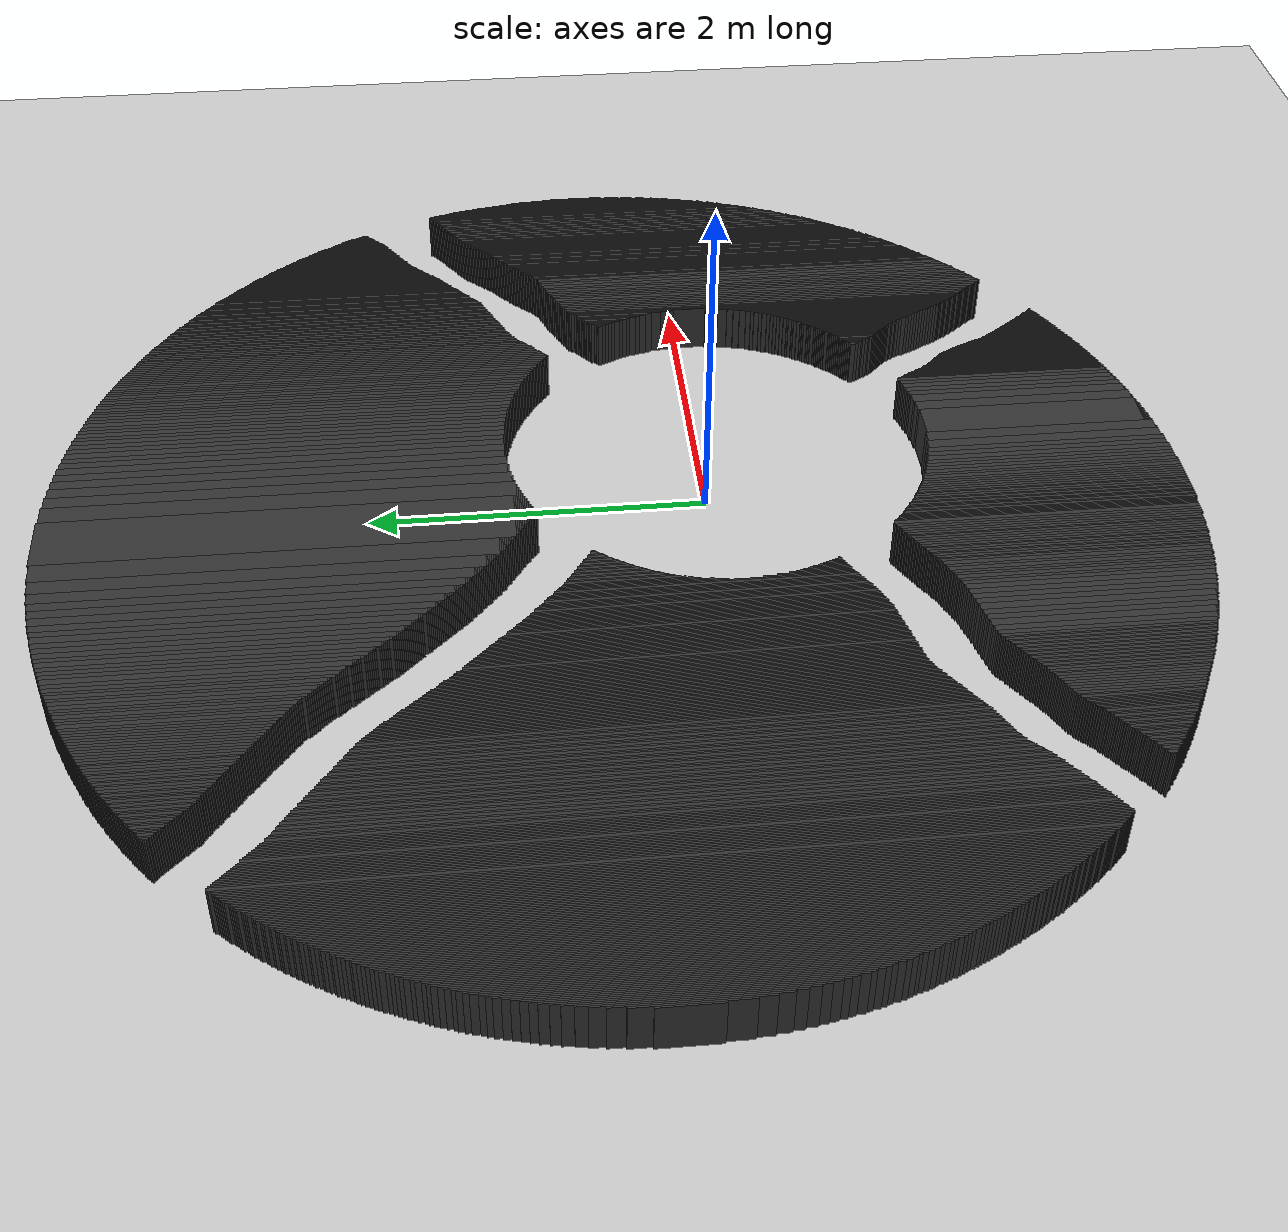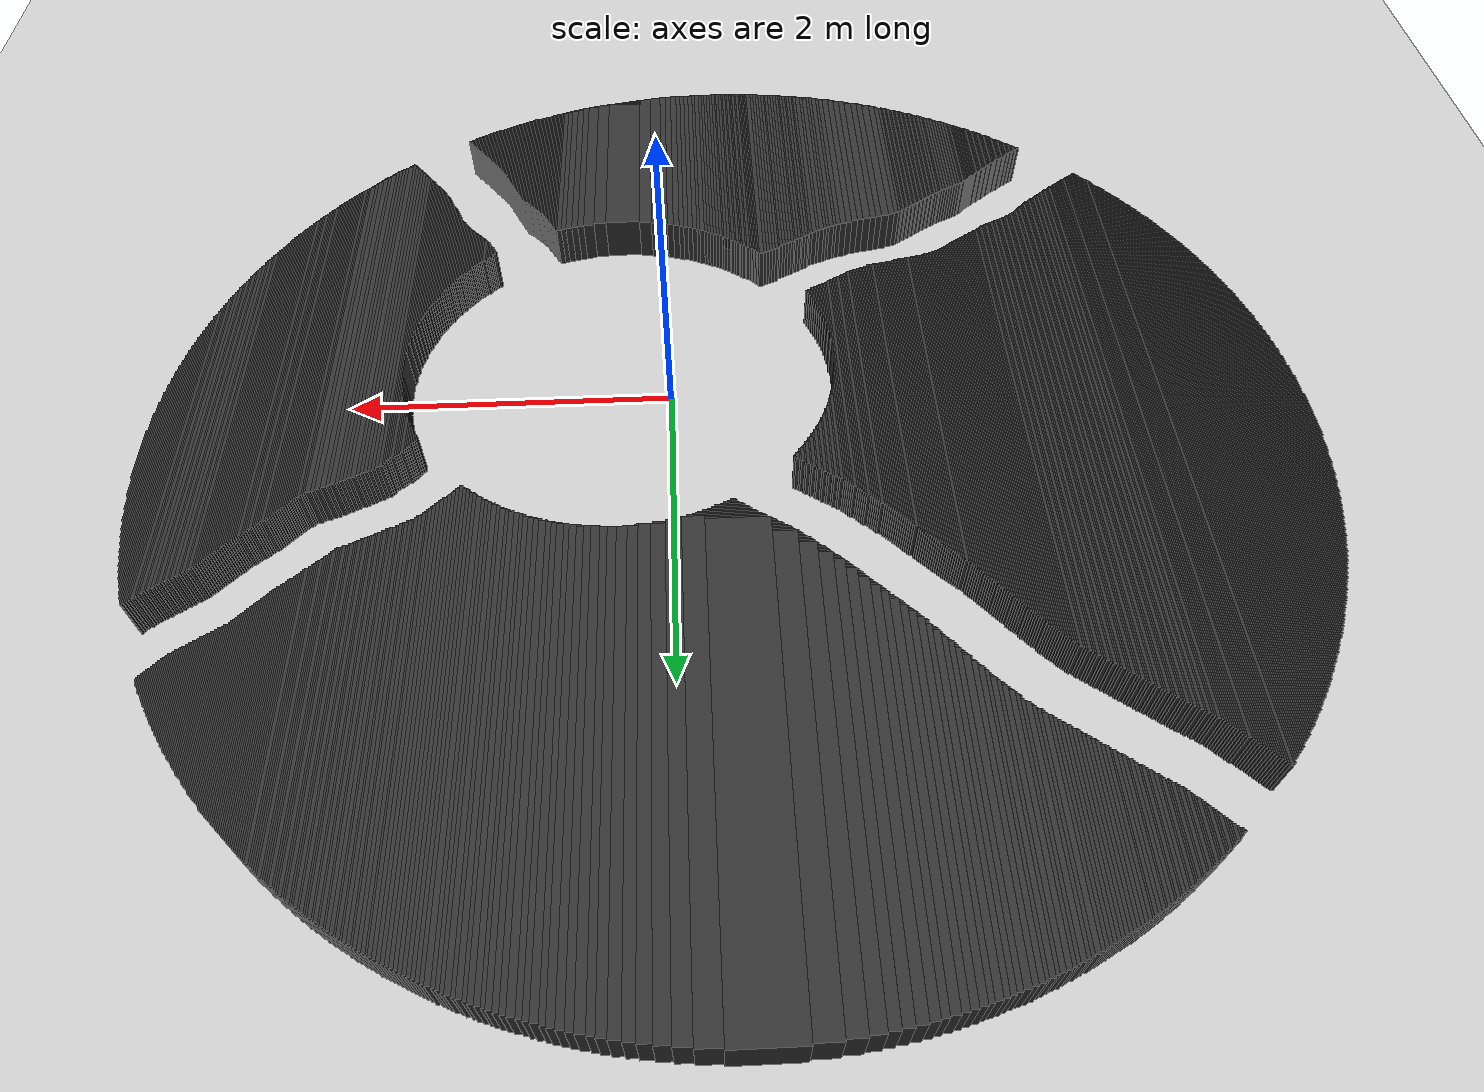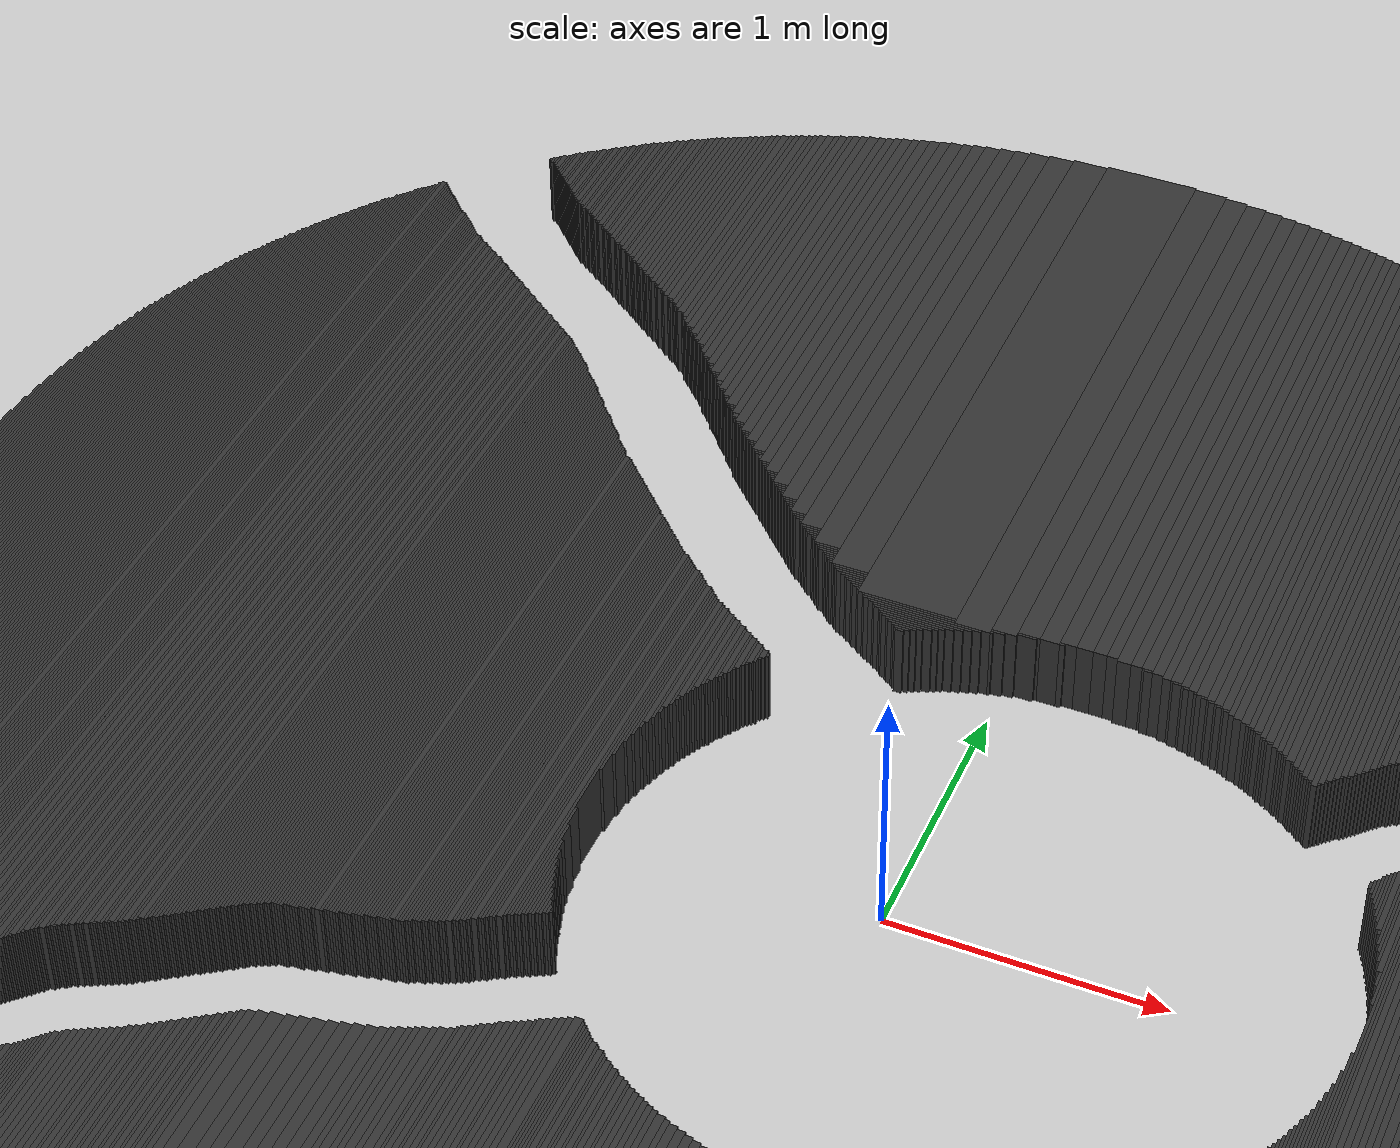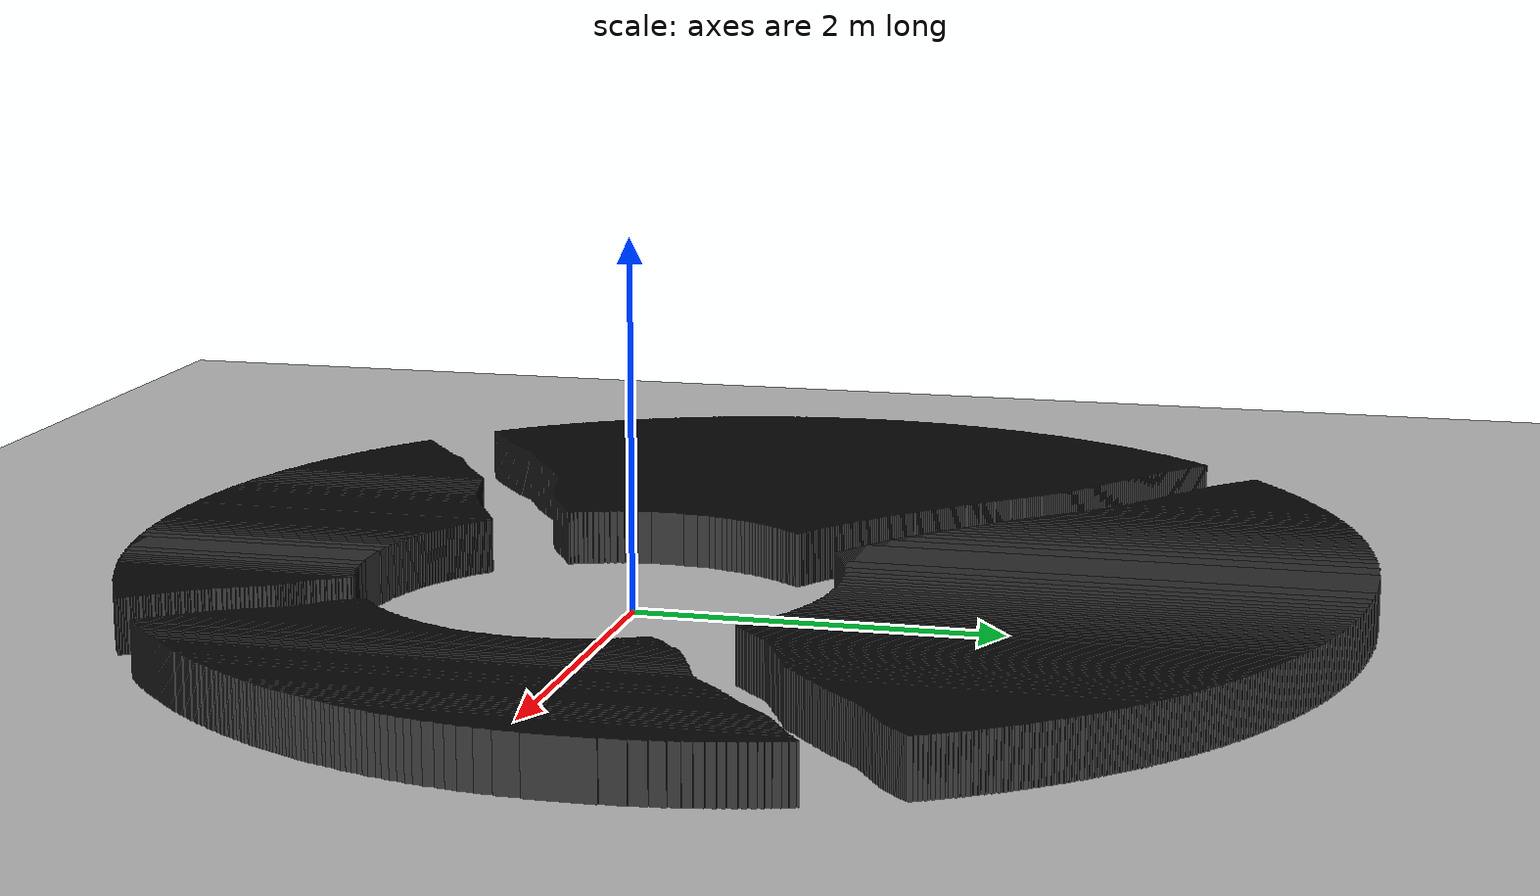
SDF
<?xml version="1.0" ?>
<sdf version="1.7">
  <world name="mapa_mundo">

  <physics type="ode">
    <max_step_size>0.001</max_step_size>  <!-- Passo da simulação (s) -->
    <real_time_update_rate>5000</real_time_update_rate>
  </physics>

    <plugin
      filename="gz-sim-physics-system"
      name="gz::sim::systems::Physics">
    </plugin>
    <plugin
      filename="gz-sim-user-commands-system"
      name="gz::sim::systems::UserCommands">
    </plugin>
    <plugin
      filename="gz-sim-scene-broadcaster-system"
      name="gz::sim::systems::SceneBroadcaster">
    </plugin>
    <plugin
      filename="gz-sim-sensors-system"
      name="gz::sim::systems::Sensors">
      <render_engine>ogre2</render_engine>
    </plugin>
    <plugin
      filename="gz-sim-imu-system"
      name="gz::sim::systems::Imu">
    </plugin>

    <!-- Luz direcional (sol) -->
    <light name='sun' type='directional'>
      <cast_shadows>true</cast_shadows>
      <pose>0 0 10 0 -0 0</pose>
      <diffuse>0.8 0.8 0.8 1</diffuse>
      <specular>0.2 0.2 0.2 1</specular>
      <direction>-0.5 0.1 -0.9</direction>
    </light>

    <!-- Plano de chão com o tamanho exato da imagem -->
    <model name='ground_plane'>
      <static>true</static>
      <link name='link'>
        <collision name='collision'>
          <geometry>
            <plane>
              <normal>0 0 1</normal>
              <size>10 10</size>
            </plane>
          </geometry>
          <surface>
            <friction>
              <ode>
                <mu>100</mu>
                <mu2>50</mu2>
              </ode>
            </friction>
          </surface>
        </collision>
        <visual name='visual'>
          <geometry>
            <plane>
              <normal>0 0 1</normal>
              <size>10 10</size>
            </plane>
          </geometry>
          <material>
            <ambient>0.8 0.8 0.8 1</ambient>
            <diffuse>0.8 0.8 0.8 1</diffuse>
            <specular>0.8 0.8 0.8 1</specular>
          </material>
        </visual>
      </link>
    </model>

    <!-- Modelos das paredes gerados a partir da imagem -->

    <model name="wall_0">
      <static>true</static>
      <link name="link">
        <collision name="collision">
          <geometry>
            <box>
              <size>0.37 2.71 0.3</size>
            </box>
          </geometry>
        </collision>
        <visual name="visual">
          <geometry>
            <box>
              <size>0.37 2.71 0.3</size>
            </box>
          </geometry>
          <material>
            <ambient>0.2 0.2 0.2 1</ambient>
            <diffuse>0.2 0.2 0.2 1</diffuse>
          </material>
        </visual>
        <pose>-0.365 2.505 0.15 0 0 0</pose>
      </link>
    </model>
    <model name="wall_1">
      <static>true</static>
      <link name="link">
        <collision name="collision">
          <geometry>
            <box>
              <size>0.14 2.6 0.3</size>
            </box>
          </geometry>
        </collision>
        <visual name="visual">
          <geometry>
            <box>
              <size>0.14 2.6 0.3</size>
            </box>
          </geometry>
          <material>
            <ambient>0.2 0.2 0.2 1</ambient>
            <diffuse>0.2 0.2 0.2 1</diffuse>
          </material>
        </visual>
        <pose>-0.62 2.5500000000000003 0.15 0 0 0</pose>
      </link>
    </model>
    <model name="wall_2">
      <static>true</static>
      <link name="link">
        <collision name="collision">
          <geometry>
            <box>
              <size>0.13 2.72 0.3</size>
            </box>
          </geometry>
        </collision>
        <visual name="visual">
          <geometry>
            <box>
              <size>0.13 2.72 0.3</size>
            </box>
          </geometry>
          <material>
            <ambient>0.2 0.2 0.2 1</ambient>
            <diffuse>0.2 0.2 0.2 1</diffuse>
          </material>
        </visual>
        <pose>-0.115 2.49 0.15 0 0 0</pose>
      </link>
    </model>
    <model name="wall_3">
      <static>true</static>
      <link name="link">
        <collision name="collision">
          <geometry>
            <box>
              <size>0.1 2.5100000000000002 0.3</size>
            </box>
          </geometry>
        </collision>
        <visual name="visual">
          <geometry>
            <box>
              <size>0.1 2.5100000000000002 0.3</size>
            </box>
          </geometry>
          <material>
            <ambient>0.2 0.2 0.2 1</ambient>
            <diffuse>0.2 0.2 0.2 1</diffuse>
          </material>
        </visual>
        <pose>-0.74 2.585 0.15 0 0 0</pose>
      </link>
    </model>
    <model name="wall_4">
      <static>true</static>
      <link name="link">
        <collision name="collision">
          <geometry>
            <box>
              <size>0.09 2.69 0.3</size>
            </box>
          </geometry>
        </collision>
        <visual name="visual">
          <geometry>
            <box>
              <size>0.09 2.69 0.3</size>
            </box>
          </geometry>
          <material>
            <ambient>0.2 0.2 0.2 1</ambient>
            <diffuse>0.2 0.2 0.2 1</diffuse>
          </material>
        </visual>
        <pose>-0.005 2.495 0.15 0 0 0</pose>
      </link>
    </model>
    <model name="wall_5">
      <static>true</static>
      <link name="link">
        <collision name="collision">
          <geometry>
            <box>
              <size>0.08 2.43 0.3</size>
            </box>
          </geometry>
        </collision>
        <visual name="visual">
          <geometry>
            <box>
              <size>0.08 2.43 0.3</size>
            </box>
          </geometry>
          <material>
            <ambient>0.2 0.2 0.2 1</ambient>
            <diffuse>0.2 0.2 0.2 1</diffuse>
          </material>
        </visual>
        <pose>-0.8300000000000001 2.615 0.15 0 0 0</pose>
      </link>
    </model>
    <model name="wall_6">
      <static>true</static>
      <link name="link">
        <collision name="collision">
          <geometry>
            <box>
              <size>0.08 2.66 0.3</size>
            </box>
          </geometry>
        </collision>
        <visual name="visual">
          <geometry>
            <box>
              <size>0.08 2.66 0.3</size>
            </box>
          </geometry>
          <material>
            <ambient>0.2 0.2 0.2 1</ambient>
            <diffuse>0.2 0.2 0.2 1</diffuse>
          </material>
        </visual>
        <pose>0.08 2.5 0.15 0 0 0</pose>
      </link>
    </model>
    <model name="wall_7">
      <static>true</static>
      <link name="link">
        <collision name="collision">
          <geometry>
            <box>
              <size>0.06 2.37 0.3</size>
            </box>
          </geometry>
        </collision>
        <visual name="visual">
          <geometry>
            <box>
              <size>0.06 2.37 0.3</size>
            </box>
          </geometry>
          <material>
            <ambient>0.2 0.2 0.2 1</ambient>
            <diffuse>0.2 0.2 0.2 1</diffuse>
          </material>
        </visual>
        <pose>-0.9 2.6350000000000002 0.15 0 0 0</pose>
      </link>
    </model>
    <model name="wall_8">
      <static>true</static>
      <link name="link">
        <collision name="collision">
          <geometry>
            <box>
              <size>0.07 2.65 0.3</size>
            </box>
          </geometry>
        </collision>
        <visual name="visual">
          <geometry>
            <box>
              <size>0.07 2.65 0.3</size>
            </box>
          </geometry>
          <material>
            <ambient>0.2 0.2 0.2 1</ambient>
            <diffuse>0.2 0.2 0.2 1</diffuse>
          </material>
        </visual>
        <pose>0.155 2.495 0.15 0 0 0</pose>
      </link>
    </model>
    <model name="wall_9">
      <static>true</static>
      <link name="link">
        <collision name="collision">
          <geometry>
            <box>
              <size>0.06 2.3000000000000003 0.3</size>
            </box>
          </geometry>
        </collision>
        <visual name="visual">
          <geometry>
            <box>
              <size>0.06 2.3000000000000003 0.3</size>
            </box>
          </geometry>
          <material>
            <ambient>0.2 0.2 0.2 1</ambient>
            <diffuse>0.2 0.2 0.2 1</diffuse>
          </material>
        </visual>
        <pose>-0.96 2.66 0.15 0 0 0</pose>
      </link>
    </model>
    <model name="wall_10">
      <static>true</static>
      <link name="link">
        <collision name="collision">
          <geometry>
            <box>
              <size>0.06 2.63 0.3</size>
            </box>
          </geometry>
        </collision>
        <visual name="visual">
          <geometry>
            <box>
              <size>0.06 2.63 0.3</size>
            </box>
          </geometry>
          <material>
            <ambient>0.2 0.2 0.2 1</ambient>
            <diffuse>0.2 0.2 0.2 1</diffuse>
          </material>
        </visual>
        <pose>0.22 2.495 0.15 0 0 0</pose>
      </link>
    </model>
    <model name="wall_11">
      <static>true</static>
      <link name="link">
        <collision name="collision">
          <geometry>
            <box>
              <size>0.06 2.23 0.3</size>
            </box>
          </geometry>
        </collision>
        <visual name="visual">
          <geometry>
            <box>
              <size>0.06 2.23 0.3</size>
            </box>
          </geometry>
          <material>
            <ambient>0.2 0.2 0.2 1</ambient>
            <diffuse>0.2 0.2 0.2 1</diffuse>
          </material>
        </visual>
        <pose>-1.02 2.685 0.15 0 0 0</pose>
      </link>
    </model>
    <model name="wall_12">
      <static>true</static>
      <link name="link">
        <collision name="collision">
          <geometry>
            <box>
              <size>0.06 2.62 0.3</size>
            </box>
          </geometry>
        </collision>
        <visual name="visual">
          <geometry>
            <box>
              <size>0.06 2.62 0.3</size>
            </box>
          </geometry>
          <material>
            <ambient>0.2 0.2 0.2 1</ambient>
            <diffuse>0.2 0.2 0.2 1</diffuse>
          </material>
        </visual>
        <pose>0.28 2.49 0.15 0 0 0</pose>
      </link>
    </model>
    <model name="wall_13">
      <static>true</static>
      <link name="link">
        <collision name="collision">
          <geometry>
            <box>
              <size>0.05 2.17 0.3</size>
            </box>
          </geometry>
        </collision>
        <visual name="visual">
          <geometry>
            <box>
              <size>0.05 2.17 0.3</size>
            </box>
          </geometry>
          <material>
            <ambient>0.2 0.2 0.2 1</ambient>
            <diffuse>0.2 0.2 0.2 1</diffuse>
          </material>
        </visual>
        <pose>-1.075 2.705 0.15 0 0 0</pose>
      </link>
    </model>
    <model name="wall_14">
      <static>true</static>
      <link name="link">
        <collision name="collision">
          <geometry>
            <box>
              <size>0.05 2.61 0.3</size>
            </box>
          </geometry>
        </collision>
        <visual name="visual">
          <geometry>
            <box>
              <size>0.05 2.61 0.3</size>
            </box>
          </geometry>
          <material>
            <ambient>0.2 0.2 0.2 1</ambient>
            <diffuse>0.2 0.2 0.2 1</diffuse>
          </material>
        </visual>
        <pose>0.335 2.485 0.15 0 0 0</pose>
      </link>
    </model>
    <model name="wall_15">
      <static>true</static>
      <link name="link">
        <collision name="collision">
          <geometry>
            <box>
              <size>0.04 2.12 0.3</size>
            </box>
          </geometry>
        </collision>
        <visual name="visual">
          <geometry>
            <box>
              <size>0.04 2.12 0.3</size>
            </box>
          </geometry>
          <material>
            <ambient>0.2 0.2 0.2 1</ambient>
            <diffuse>0.2 0.2 0.2 1</diffuse>
          </material>
        </visual>
        <pose>-1.12 2.72 0.15 0 0 0</pose>
      </link>
    </model>
    <model name="wall_16">
      <static>true</static>
      <link name="link">
        <collision name="collision">
          <geometry>
            <box>
              <size>0.04 2.6 0.3</size>
            </box>
          </geometry>
        </collision>
        <visual name="visual">
          <geometry>
            <box>
              <size>0.04 2.6 0.3</size>
            </box>
          </geometry>
          <material>
            <ambient>0.2 0.2 0.2 1</ambient>
            <diffuse>0.2 0.2 0.2 1</diffuse>
          </material>
        </visual>
        <pose>0.38 2.48 0.15 0 0 0</pose>
      </link>
    </model>
    <model name="wall_17">
      <static>true</static>
      <link name="link">
        <collision name="collision">
          <geometry>
            <box>
              <size>0.05 2.06 0.3</size>
            </box>
          </geometry>
        </collision>
        <visual name="visual">
          <geometry>
            <box>
              <size>0.05 2.06 0.3</size>
            </box>
          </geometry>
          <material>
            <ambient>0.2 0.2 0.2 1</ambient>
            <diffuse>0.2 0.2 0.2 1</diffuse>
          </material>
        </visual>
        <pose>-1.165 2.74 0.15 0 0 0</pose>
      </link>
    </model>
    <model name="wall_18">
      <static>true</static>
      <link name="link">
        <collision name="collision">
          <geometry>
            <box>
              <size>0.05 2.6 0.3</size>
            </box>
          </geometry>
        </collision>
        <visual name="visual">
          <geometry>
            <box>
              <size>0.05 2.6 0.3</size>
            </box>
          </geometry>
          <material>
            <ambient>0.2 0.2 0.2 1</ambient>
            <diffuse>0.2 0.2 0.2 1</diffuse>
          </material>
        </visual>
        <pose>0.425 2.47 0.15 0 0 0</pose>
      </link>
    </model>
    <model name="wall_19">
      <static>true</static>
      <link name="link">
        <collision name="collision">
          <geometry>
            <box>
              <size>0.04 2.0100000000000002 0.3</size>
            </box>
          </geometry>
        </collision>
        <visual name="visual">
          <geometry>
            <box>
              <size>0.04 2.0100000000000002 0.3</size>
            </box>
          </geometry>
          <material>
            <ambient>0.2 0.2 0.2 1</ambient>
            <diffuse>0.2 0.2 0.2 1</diffuse>
          </material>
        </visual>
        <pose>-1.21 2.755 0.15 0 0 0</pose>
      </link>
    </model>
    <model name="wall_20">
      <static>true</static>
      <link name="link">
        <collision name="collision">
          <geometry>
            <box>
              <size>0.04 2.59 0.3</size>
            </box>
          </geometry>
        </collision>
        <visual name="visual">
          <geometry>
            <box>
              <size>0.04 2.59 0.3</size>
            </box>
          </geometry>
          <material>
            <ambient>0.2 0.2 0.2 1</ambient>
            <diffuse>0.2 0.2 0.2 1</diffuse>
          </material>
        </visual>
        <pose>0.47000000000000003 2.465 0.15 0 0 0</pose>
      </link>
    </model>
    <model name="wall_21">
      <static>true</static>
      <link name="link">
        <collision name="collision">
          <geometry>
            <box>
              <size>0.04 1.96 0.3</size>
            </box>
          </geometry>
        </collision>
        <visual name="visual">
          <geometry>
            <box>
              <size>0.04 1.96 0.3</size>
            </box>
          </geometry>
          <material>
            <ambient>0.2 0.2 0.2 1</ambient>
            <diffuse>0.2 0.2 0.2 1</diffuse>
          </material>
        </visual>
        <pose>-1.25 2.77 0.15 0 0 0</pose>
      </link>
    </model>
    <model name="wall_22">
      <static>true</static>
      <link name="link">
        <collision name="collision">
          <geometry>
            <box>
              <size>0.04 2.58 0.3</size>
            </box>
          </geometry>
        </collision>
        <visual name="visual">
          <geometry>
            <box>
              <size>0.04 2.58 0.3</size>
            </box>
          </geometry>
          <material>
            <ambient>0.2 0.2 0.2 1</ambient>
            <diffuse>0.2 0.2 0.2 1</diffuse>
          </material>
        </visual>
        <pose>0.51 2.46 0.15 0 0 0</pose>
      </link>
    </model>
    <model name="wall_23">
      <static>true</static>
      <link name="link">
        <collision name="collision">
          <geometry>
            <box>
              <size>0.04 1.9100000000000001 0.3</size>
            </box>
          </geometry>
        </collision>
        <visual name="visual">
          <geometry>
            <box>
              <size>0.04 1.9100000000000001 0.3</size>
            </box>
          </geometry>
          <material>
            <ambient>0.2 0.2 0.2 1</ambient>
            <diffuse>0.2 0.2 0.2 1</diffuse>
          </material>
        </visual>
        <pose>-1.29 2.785 0.15 0 0 0</pose>
      </link>
    </model>
    <model name="wall_24">
      <static>true</static>
      <link name="link">
        <collision name="collision">
          <geometry>
            <box>
              <size>0.04 2.58 0.3</size>
            </box>
          </geometry>
        </collision>
        <visual name="visual">
          <geometry>
            <box>
              <size>0.04 2.58 0.3</size>
            </box>
          </geometry>
          <material>
            <ambient>0.2 0.2 0.2 1</ambient>
            <diffuse>0.2 0.2 0.2 1</diffuse>
          </material>
        </visual>
        <pose>0.55 2.45 0.15 0 0 0</pose>
      </link>
    </model>
    <model name="wall_25">
      <static>true</static>
      <link name="link">
        <collision name="collision">
          <geometry>
            <box>
              <size>0.03 1.86 0.3</size>
            </box>
          </geometry>
        </collision>
        <visual name="visual">
          <geometry>
            <box>
              <size>0.03 1.86 0.3</size>
            </box>
          </geometry>
          <material>
            <ambient>0.2 0.2 0.2 1</ambient>
            <diffuse>0.2 0.2 0.2 1</diffuse>
          </material>
        </visual>
        <pose>-1.325 2.8000000000000003 0.15 0 0 0</pose>
      </link>
    </model>
    <model name="wall_26">
      <static>true</static>
      <link name="link">
        <collision name="collision">
          <geometry>
            <box>
              <size>0.03 2.58 0.3</size>
            </box>
          </geometry>
        </collision>
        <visual name="visual">
          <geometry>
            <box>
              <size>0.03 2.58 0.3</size>
            </box>
          </geometry>
          <material>
            <ambient>0.2 0.2 0.2 1</ambient>
            <diffuse>0.2 0.2 0.2 1</diffuse>
          </material>
        </visual>
        <pose>0.585 2.44 0.15 0 0 0</pose>
      </link>
    </model>
    <model name="wall_27">
      <static>true</static>
      <link name="link">
        <collision name="collision">
          <geometry>
            <box>
              <size>0.04 1.81 0.3</size>
            </box>
          </geometry>
        </collision>
        <visual name="visual">
          <geometry>
            <box>
              <size>0.04 1.81 0.3</size>
            </box>
          </geometry>
          <material>
            <ambient>0.2 0.2 0.2 1</ambient>
            <diffuse>0.2 0.2 0.2 1</diffuse>
          </material>
        </visual>
        <pose>-1.36 2.815 0.15 0 0 0</pose>
      </link>
    </model>
    <model name="wall_28">
      <static>true</static>
      <link name="link">
        <collision name="collision">
          <geometry>
            <box>
              <size>0.04 2.57 0.3</size>
            </box>
          </geometry>
        </collision>
        <visual name="visual">
          <geometry>
            <box>
              <size>0.04 2.57 0.3</size>
            </box>
          </geometry>
          <material>
            <ambient>0.2 0.2 0.2 1</ambient>
            <diffuse>0.2 0.2 0.2 1</diffuse>
          </material>
        </visual>
        <pose>0.62 2.435 0.15 0 0 0</pose>
      </link>
    </model>
    <model name="wall_29">
      <static>true</static>
      <link name="link">
        <collision name="collision">
          <geometry>
            <box>
              <size>0.03 1.76 0.3</size>
            </box>
          </geometry>
        </collision>
        <visual name="visual">
          <geometry>
            <box>
              <size>0.03 1.76 0.3</size>
            </box>
          </geometry>
          <material>
            <ambient>0.2 0.2 0.2 1</ambient>
            <diffuse>0.2 0.2 0.2 1</diffuse>
          </material>
        </visual>
        <pose>-1.395 2.83 0.15 0 0 0</pose>
      </link>
    </model>
    <model name="wall_30">
      <static>true</static>
      <link name="link">
        <collision name="collision">
          <geometry>
            <box>
              <size>0.03 2.57 0.3</size>
            </box>
          </geometry>
        </collision>
        <visual name="visual">
          <geometry>
            <box>
              <size>0.03 2.57 0.3</size>
            </box>
          </geometry>
          <material>
            <ambient>0.2 0.2 0.2 1</ambient>
            <diffuse>0.2 0.2 0.2 1</diffuse>
          </material>
        </visual>
        <pose>0.655 2.4250000000000003 0.15 0 0 0</pose>
      </link>
    </model>
    <model name="wall_31">
      <static>true</static>
      <link name="link">
        <collision name="collision">
          <geometry>
            <box>
              <size>0.03 1.72 0.3</size>
            </box>
          </geometry>
        </collision>
        <visual name="visual">
          <geometry>
            <box>
              <size>0.03 1.72 0.3</size>
            </box>
          </geometry>
          <material>
            <ambient>0.2 0.2 0.2 1</ambient>
            <diffuse>0.2 0.2 0.2 1</diffuse>
          </material>
        </visual>
        <pose>-1.425 2.84 0.15 0 0 0</pose>
      </link>
    </model>
    <model name="wall_32">
      <static>true</static>
      <link name="link">
        <collision name="collision">
          <geometry>
            <box>
              <size>0.03 2.57 0.3</size>
            </box>
          </geometry>
        </collision>
        <visual name="visual">
          <geometry>
            <box>
              <size>0.03 2.57 0.3</size>
            </box>
          </geometry>
          <material>
            <ambient>0.2 0.2 0.2 1</ambient>
            <diffuse>0.2 0.2 0.2 1</diffuse>
          </material>
        </visual>
        <pose>0.685 2.415 0.15 0 0 0</pose>
      </link>
    </model>
    <model name="wall_33">
      <static>true</static>
      <link name="link">
        <collision name="collision">
          <geometry>
            <box>
              <size>0.03 1.67 0.3</size>
            </box>
          </geometry>
        </collision>
        <visual name="visual">
          <geometry>
            <box>
              <size>0.03 1.67 0.3</size>
            </box>
          </geometry>
          <material>
            <ambient>0.2 0.2 0.2 1</ambient>
            <diffuse>0.2 0.2 0.2 1</diffuse>
          </material>
        </visual>
        <pose>-1.455 2.855 0.15 0 0 0</pose>
      </link>
    </model>
    <model name="wall_34">
      <static>true</static>
      <link name="link">
        <collision name="collision">
          <geometry>
            <box>
              <size>0.04 2.57 0.3</size>
            </box>
          </geometry>
        </collision>
        <visual name="visual">
          <geometry>
            <box>
              <size>0.04 2.57 0.3</size>
            </box>
          </geometry>
          <material>
            <ambient>0.2 0.2 0.2 1</ambient>
            <diffuse>0.2 0.2 0.2 1</diffuse>
          </material>
        </visual>
        <pose>0.72 2.4050000000000002 0.15 0 0 0</pose>
      </link>
    </model>
    <model name="wall_35">
      <static>true</static>
      <link name="link">
        <collision name="collision">
          <geometry>
            <box>
              <size>0.04 1.62 0.3</size>
            </box>
          </geometry>
        </collision>
        <visual name="visual">
          <geometry>
            <box>
              <size>0.04 1.62 0.3</size>
            </box>
          </geometry>
          <material>
            <ambient>0.2 0.2 0.2 1</ambient>
            <diffuse>0.2 0.2 0.2 1</diffuse>
          </material>
        </visual>
        <pose>-1.49 2.87 0.15 0 0 0</pose>
      </link>
    </model>
    <model name="wall_36">
      <static>true</static>
      <link name="link">
        <collision name="collision">
          <geometry>
            <box>
              <size>0.03 2.57 0.3</size>
            </box>
          </geometry>
        </collision>
        <visual name="visual">
          <geometry>
            <box>
              <size>0.03 2.57 0.3</size>
            </box>
          </geometry>
          <material>
            <ambient>0.2 0.2 0.2 1</ambient>
            <diffuse>0.2 0.2 0.2 1</diffuse>
          </material>
        </visual>
        <pose>0.755 2.395 0.15 0 0 0</pose>
      </link>
    </model>
    <model name="wall_37">
      <static>true</static>
      <link name="link">
        <collision name="collision">
          <geometry>
            <box>
              <size>0.03 1.57 0.3</size>
            </box>
          </geometry>
        </collision>
        <visual name="visual">
          <geometry>
            <box>
              <size>0.03 1.57 0.3</size>
            </box>
          </geometry>
          <material>
            <ambient>0.2 0.2 0.2 1</ambient>
            <diffuse>0.2 0.2 0.2 1</diffuse>
          </material>
        </visual>
        <pose>-1.5250000000000001 2.8850000000000002 0.15 0 0 0</pose>
      </link>
    </model>
    <model name="wall_38">
      <static>true</static>
      <link name="link">
        <collision name="collision">
          <geometry>
            <box>
              <size>0.03 2.57 0.3</size>
            </box>
          </geometry>
        </collision>
        <visual name="visual">
          <geometry>
            <box>
              <size>0.03 2.57 0.3</size>
            </box>
          </geometry>
          <material>
            <ambient>0.2 0.2 0.2 1</ambient>
            <diffuse>0.2 0.2 0.2 1</diffuse>
          </material>
        </visual>
        <pose>0.785 2.3850000000000002 0.15 0 0 0</pose>
      </link>
    </model>
    <model name="wall_39">
      <static>true</static>
      <link name="link">
        <collision name="collision">
          <geometry>
            <box>
              <size>0.03 1.53 0.3</size>
            </box>
          </geometry>
        </collision>
        <visual name="visual">
          <geometry>
            <box>
              <size>0.03 1.53 0.3</size>
            </box>
          </geometry>
          <material>
            <ambient>0.2 0.2 0.2 1</ambient>
            <diffuse>0.2 0.2 0.2 1</diffuse>
          </material>
        </visual>
        <pose>-1.555 2.895 0.15 0 0 0</pose>
      </link>
    </model>
    <model name="wall_40">
      <static>true</static>
      <link name="link">
        <collision name="collision">
          <geometry>
            <box>
              <size>0.03 2.57 0.3</size>
            </box>
          </geometry>
        </collision>
        <visual name="visual">
          <geometry>
            <box>
              <size>0.03 2.57 0.3</size>
            </box>
          </geometry>
          <material>
            <ambient>0.2 0.2 0.2 1</ambient>
            <diffuse>0.2 0.2 0.2 1</diffuse>
          </material>
        </visual>
        <pose>0.8150000000000001 2.375 0.15 0 0 0</pose>
      </link>
    </model>
    <model name="wall_41">
      <static>true</static>
      <link name="link">
        <collision name="collision">
          <geometry>
            <box>
              <size>0.02 1.5 0.3</size>
            </box>
          </geometry>
        </collision>
        <visual name="visual">
          <geometry>
            <box>
              <size>0.02 1.5 0.3</size>
            </box>
          </geometry>
          <material>
            <ambient>0.2 0.2 0.2 1</ambient>
            <diffuse>0.2 0.2 0.2 1</diffuse>
          </material>
        </visual>
        <pose>-1.58 2.9 0.15 0 0 0</pose>
      </link>
    </model>
    <model name="wall_42">
      <static>true</static>
      <link name="link">
        <collision name="collision">
          <geometry>
            <box>
              <size>0.02 2.58 0.3</size>
            </box>
          </geometry>
        </collision>
        <visual name="visual">
          <geometry>
            <box>
              <size>0.02 2.58 0.3</size>
            </box>
          </geometry>
          <material>
            <ambient>0.2 0.2 0.2 1</ambient>
            <diffuse>0.2 0.2 0.2 1</diffuse>
          </material>
        </visual>
        <pose>0.84 2.36 0.15 0 0 0</pose>
      </link>
    </model>
    <model name="wall_43">
      <static>true</static>
      <link name="link">
        <collision name="collision">
          <geometry>
            <box>
              <size>0.03 1.45 0.3</size>
            </box>
          </geometry>
        </collision>
        <visual name="visual">
          <geometry>
            <box>
              <size>0.03 1.45 0.3</size>
            </box>
          </geometry>
          <material>
            <ambient>0.2 0.2 0.2 1</ambient>
            <diffuse>0.2 0.2 0.2 1</diffuse>
          </material>
        </visual>
        <pose>-1.605 2.915 0.15 0 0 0</pose>
      </link>
    </model>
    <model name="wall_44">
      <static>true</static>
      <link name="link">
        <collision name="collision">
          <geometry>
            <box>
              <size>0.03 2.58 0.3</size>
            </box>
          </geometry>
        </collision>
        <visual name="visual">
          <geometry>
            <box>
              <size>0.03 2.58 0.3</size>
            </box>
          </geometry>
          <material>
            <ambient>0.2 0.2 0.2 1</ambient>
            <diffuse>0.2 0.2 0.2 1</diffuse>
          </material>
        </visual>
        <pose>0.865 2.35 0.15 0 0 0</pose>
      </link>
    </model>
    <model name="wall_45">
      <static>true</static>
      <link name="link">
        <collision name="collision">
          <geometry>
            <box>
              <size>0.02 1.42 0.3</size>
            </box>
          </geometry>
        </collision>
        <visual name="visual">
          <geometry>
            <box>
              <size>0.02 1.42 0.3</size>
            </box>
          </geometry>
          <material>
            <ambient>0.2 0.2 0.2 1</ambient>
            <diffuse>0.2 0.2 0.2 1</diffuse>
          </material>
        </visual>
        <pose>-1.6300000000000001 2.92 0.15 0 0 0</pose>
      </link>
    </model>
    <model name="wall_46">
      <static>true</static>
      <link name="link">
        <collision name="collision">
          <geometry>
            <box>
              <size>0.03 2.58 0.3</size>
            </box>
          </geometry>
        </collision>
        <visual name="visual">
          <geometry>
            <box>
              <size>0.03 2.58 0.3</size>
            </box>
          </geometry>
          <material>
            <ambient>0.2 0.2 0.2 1</ambient>
            <diffuse>0.2 0.2 0.2 1</diffuse>
          </material>
        </visual>
        <pose>0.895 2.34 0.15 0 0 0</pose>
      </link>
    </model>
    <model name="wall_47">
      <static>true</static>
      <link name="link">
        <collision name="collision">
          <geometry>
            <box>
              <size>0.03 1.3800000000000001 0.3</size>
            </box>
          </geometry>
        </collision>
        <visual name="visual">
          <geometry>
            <box>
              <size>0.03 1.3800000000000001 0.3</size>
            </box>
          </geometry>
          <material>
            <ambient>0.2 0.2 0.2 1</ambient>
            <diffuse>0.2 0.2 0.2 1</diffuse>
          </material>
        </visual>
        <pose>-1.655 2.93 0.15 0 0 0</pose>
      </link>
    </model>
    <model name="wall_48">
      <static>true</static>
      <link name="link">
        <collision name="collision">
          <geometry>
            <box>
              <size>0.02 2.58 0.3</size>
            </box>
          </geometry>
        </collision>
        <visual name="visual">
          <geometry>
            <box>
              <size>0.02 2.58 0.3</size>
            </box>
          </geometry>
          <material>
            <ambient>0.2 0.2 0.2 1</ambient>
            <diffuse>0.2 0.2 0.2 1</diffuse>
          </material>
        </visual>
        <pose>0.92 2.33 0.15 0 0 0</pose>
      </link>
    </model>
    <model name="wall_49">
      <static>true</static>
      <link name="link">
        <collision name="collision">
          <geometry>
            <box>
              <size>0.03 1.34 0.3</size>
            </box>
          </geometry>
        </collision>
        <visual name="visual">
          <geometry>
            <box>
              <size>0.03 1.34 0.3</size>
            </box>
          </geometry>
          <material>
            <ambient>0.2 0.2 0.2 1</ambient>
            <diffuse>0.2 0.2 0.2 1</diffuse>
          </material>
        </visual>
        <pose>-1.685 2.94 0.15 0 0 0</pose>
      </link>
    </model>
    <model name="wall_50">
      <static>true</static>
      <link name="link">
        <collision name="collision">
          <geometry>
            <box>
              <size>0.03 2.58 0.3</size>
            </box>
          </geometry>
        </collision>
        <visual name="visual">
          <geometry>
            <box>
              <size>0.03 2.58 0.3</size>
            </box>
          </geometry>
          <material>
            <ambient>0.2 0.2 0.2 1</ambient>
            <diffuse>0.2 0.2 0.2 1</diffuse>
          </material>
        </visual>
        <pose>0.9450000000000001 2.32 0.15 0 0 0</pose>
      </link>
    </model>
    <model name="wall_51">
      <static>true</static>
      <link name="link">
        <collision name="collision">
          <geometry>
            <box>
              <size>0.02 1.31 0.3</size>
            </box>
          </geometry>
        </collision>
        <visual name="visual">
          <geometry>
            <box>
              <size>0.02 1.31 0.3</size>
            </box>
          </geometry>
          <material>
            <ambient>0.2 0.2 0.2 1</ambient>
            <diffuse>0.2 0.2 0.2 1</diffuse>
          </material>
        </visual>
        <pose>-1.71 2.945 0.15 0 0 0</pose>
      </link>
    </model>
    <model name="wall_52">
      <static>true</static>
      <link name="link">
        <collision name="collision">
          <geometry>
            <box>
              <size>0.02 2.59 0.3</size>
            </box>
          </geometry>
        </collision>
        <visual name="visual">
          <geometry>
            <box>
              <size>0.02 2.59 0.3</size>
            </box>
          </geometry>
          <material>
            <ambient>0.2 0.2 0.2 1</ambient>
            <diffuse>0.2 0.2 0.2 1</diffuse>
          </material>
        </visual>
        <pose>0.97 2.305 0.15 0 0 0</pose>
      </link>
    </model>
    <model name="wall_53">
      <static>true</static>
      <link name="link">
        <collision name="collision">
          <geometry>
            <box>
              <size>0.02 1.27 0.3</size>
            </box>
          </geometry>
        </collision>
        <visual name="visual">
          <geometry>
            <box>
              <size>0.02 1.27 0.3</size>
            </box>
          </geometry>
          <material>
            <ambient>0.2 0.2 0.2 1</ambient>
            <diffuse>0.2 0.2 0.2 1</diffuse>
          </material>
        </visual>
        <pose>-1.73 2.955 0.15 0 0 0</pose>
      </link>
    </model>
    <model name="wall_54">
      <static>true</static>
      <link name="link">
        <collision name="collision">
          <geometry>
            <box>
              <size>0.03 2.59 0.3</size>
            </box>
          </geometry>
        </collision>
        <visual name="visual">
          <geometry>
            <box>
              <size>0.03 2.59 0.3</size>
            </box>
          </geometry>
          <material>
            <ambient>0.2 0.2 0.2 1</ambient>
            <diffuse>0.2 0.2 0.2 1</diffuse>
          </material>
        </visual>
        <pose>0.995 2.295 0.15 0 0 0</pose>
      </link>
    </model>
    <model name="wall_55">
      <static>true</static>
      <link name="link">
        <collision name="collision">
          <geometry>
            <box>
              <size>0.03 1.24 0.3</size>
            </box>
          </geometry>
        </collision>
        <visual name="visual">
          <geometry>
            <box>
              <size>0.03 1.24 0.3</size>
            </box>
          </geometry>
          <material>
            <ambient>0.2 0.2 0.2 1</ambient>
            <diffuse>0.2 0.2 0.2 1</diffuse>
          </material>
        </visual>
        <pose>-1.7550000000000001 2.96 0.15 0 0 0</pose>
      </link>
    </model>
    <model name="wall_56">
      <static>true</static>
      <link name="link">
        <collision name="collision">
          <geometry>
            <box>
              <size>0.02 2.6 0.3</size>
            </box>
          </geometry>
        </collision>
        <visual name="visual">
          <geometry>
            <box>
              <size>0.02 2.6 0.3</size>
            </box>
          </geometry>
          <material>
            <ambient>0.2 0.2 0.2 1</ambient>
            <diffuse>0.2 0.2 0.2 1</diffuse>
          </material>
        </visual>
        <pose>1.02 2.2800000000000002 0.15 0 0 0</pose>
      </link>
    </model>
    <model name="wall_57">
      <static>true</static>
      <link name="link">
        <collision name="collision">
          <geometry>
            <box>
              <size>0.02 1.21 0.3</size>
            </box>
          </geometry>
        </collision>
        <visual name="visual">
          <geometry>
            <box>
              <size>0.02 1.21 0.3</size>
            </box>
          </geometry>
          <material>
            <ambient>0.2 0.2 0.2 1</ambient>
            <diffuse>0.2 0.2 0.2 1</diffuse>
          </material>
        </visual>
        <pose>-1.78 2.965 0.15 0 0 0</pose>
      </link>
    </model>
    <model name="wall_58">
      <static>true</static>
      <link name="link">
        <collision name="collision">
          <geometry>
            <box>
              <size>0.02 2.6 0.3</size>
            </box>
          </geometry>
        </collision>
        <visual name="visual">
          <geometry>
            <box>
              <size>0.02 2.6 0.3</size>
            </box>
          </geometry>
          <material>
            <ambient>0.2 0.2 0.2 1</ambient>
            <diffuse>0.2 0.2 0.2 1</diffuse>
          </material>
        </visual>
        <pose>1.04 2.27 0.15 0 0 0</pose>
      </link>
    </model>
    <model name="wall_59">
      <static>true</static>
      <link name="link">
        <collision name="collision">
          <geometry>
            <box>
              <size>0.02 1.18 0.3</size>
            </box>
          </geometry>
        </collision>
        <visual name="visual">
          <geometry>
            <box>
              <size>0.02 1.18 0.3</size>
            </box>
          </geometry>
          <material>
            <ambient>0.2 0.2 0.2 1</ambient>
            <diffuse>0.2 0.2 0.2 1</diffuse>
          </material>
        </visual>
        <pose>-1.8 2.97 0.15 0 0 0</pose>
      </link>
    </model>
    <model name="wall_60">
      <static>true</static>
      <link name="link">
        <collision name="collision">
          <geometry>
            <box>
              <size>0.02 2.6 0.3</size>
            </box>
          </geometry>
        </collision>
        <visual name="visual">
          <geometry>
            <box>
              <size>0.02 2.6 0.3</size>
            </box>
          </geometry>
          <material>
            <ambient>0.2 0.2 0.2 1</ambient>
            <diffuse>0.2 0.2 0.2 1</diffuse>
          </material>
        </visual>
        <pose>1.06 2.2600000000000002 0.15 0 0 0</pose>
      </link>
    </model>
    <model name="wall_61">
      <static>true</static>
      <link name="link">
        <collision name="collision">
          <geometry>
            <box>
              <size>0.03 1.1500000000000001 0.3</size>
            </box>
          </geometry>
        </collision>
        <visual name="visual">
          <geometry>
            <box>
              <size>0.03 1.1500000000000001 0.3</size>
            </box>
          </geometry>
          <material>
            <ambient>0.2 0.2 0.2 1</ambient>
            <diffuse>0.2 0.2 0.2 1</diffuse>
          </material>
        </visual>
        <pose>-1.825 2.975 0.15 0 0 0</pose>
      </link>
    </model>
    <model name="wall_62">
      <static>true</static>
      <link name="link">
        <collision name="collision">
          <geometry>
            <box>
              <size>0.03 2.61 0.3</size>
            </box>
          </geometry>
        </collision>
        <visual name="visual">
          <geometry>
            <box>
              <size>0.03 2.61 0.3</size>
            </box>
          </geometry>
          <material>
            <ambient>0.2 0.2 0.2 1</ambient>
            <diffuse>0.2 0.2 0.2 1</diffuse>
          </material>
        </visual>
        <pose>1.085 2.245 0.15 0 0 0</pose>
      </link>
    </model>
    <model name="wall_63">
      <static>true</static>
      <link name="link">
        <collision name="collision">
          <geometry>
            <box>
              <size>0.02 1.1300000000000001 0.3</size>
            </box>
          </geometry>
        </collision>
        <visual name="visual">
          <geometry>
            <box>
              <size>0.02 1.1300000000000001 0.3</size>
            </box>
          </geometry>
          <material>
            <ambient>0.2 0.2 0.2 1</ambient>
            <diffuse>0.2 0.2 0.2 1</diffuse>
          </material>
        </visual>
        <pose>-1.85 2.975 0.15 0 0 0</pose>
      </link>
    </model>
    <model name="wall_64">
      <static>true</static>
      <link name="link">
        <collision name="collision">
          <geometry>
            <box>
              <size>0.02 2.62 0.3</size>
            </box>
          </geometry>
        </collision>
        <visual name="visual">
          <geometry>
            <box>
              <size>0.02 2.62 0.3</size>
            </box>
          </geometry>
          <material>
            <ambient>0.2 0.2 0.2 1</ambient>
            <diffuse>0.2 0.2 0.2 1</diffuse>
          </material>
        </visual>
        <pose>1.11 2.23 0.15 0 0 0</pose>
      </link>
    </model>
    <model name="wall_65">
      <static>true</static>
      <link name="link">
        <collision name="collision">
          <geometry>
            <box>
              <size>0.02 1.1 0.3</size>
            </box>
          </geometry>
        </collision>
        <visual name="visual">
          <geometry>
            <box>
              <size>0.02 1.1 0.3</size>
            </box>
          </geometry>
          <material>
            <ambient>0.2 0.2 0.2 1</ambient>
            <diffuse>0.2 0.2 0.2 1</diffuse>
          </material>
        </visual>
        <pose>-1.87 2.98 0.15 0 0 0</pose>
      </link>
    </model>
    <model name="wall_66">
      <static>true</static>
      <link name="link">
        <collision name="collision">
          <geometry>
            <box>
              <size>0.02 2.62 0.3</size>
            </box>
          </geometry>
        </collision>
        <visual name="visual">
          <geometry>
            <box>
              <size>0.02 2.62 0.3</size>
            </box>
          </geometry>
          <material>
            <ambient>0.2 0.2 0.2 1</ambient>
            <diffuse>0.2 0.2 0.2 1</diffuse>
          </material>
        </visual>
        <pose>1.1300000000000001 2.22 0.15 0 0 0</pose>
      </link>
    </model>
    <model name="wall_67">
      <static>true</static>
      <link name="link">
        <collision name="collision">
          <geometry>
            <box>
              <size>0.02 1.08 0.3</size>
            </box>
          </geometry>
        </collision>
        <visual name="visual">
          <geometry>
            <box>
              <size>0.02 1.08 0.3</size>
            </box>
          </geometry>
          <material>
            <ambient>0.2 0.2 0.2 1</ambient>
            <diffuse>0.2 0.2 0.2 1</diffuse>
          </material>
        </visual>
        <pose>-1.8900000000000001 2.98 0.15 0 0 0</pose>
      </link>
    </model>
    <model name="wall_68">
      <static>true</static>
      <link name="link">
        <collision name="collision">
          <geometry>
            <box>
              <size>0.02 2.63 0.3</size>
            </box>
          </geometry>
        </collision>
        <visual name="visual">
          <geometry>
            <box>
              <size>0.02 2.63 0.3</size>
            </box>
          </geometry>
          <material>
            <ambient>0.2 0.2 0.2 1</ambient>
            <diffuse>0.2 0.2 0.2 1</diffuse>
          </material>
        </visual>
        <pose>1.1500000000000001 2.205 0.15 0 0 0</pose>
      </link>
    </model>
    <model name="wall_69">
      <static>true</static>
      <link name="link">
        <collision name="collision">
          <geometry>
            <box>
              <size>0.02 1.05 0.3</size>
            </box>
          </geometry>
        </collision>
        <visual name="visual">
          <geometry>
            <box>
              <size>0.02 1.05 0.3</size>
            </box>
          </geometry>
          <material>
            <ambient>0.2 0.2 0.2 1</ambient>
            <diffuse>0.2 0.2 0.2 1</diffuse>
          </material>
        </visual>
        <pose>-1.9100000000000001 2.985 0.15 0 0 0</pose>
      </link>
    </model>
    <model name="wall_70">
      <static>true</static>
      <link name="link">
        <collision name="collision">
          <geometry>
            <box>
              <size>0.02 2.63 0.3</size>
            </box>
          </geometry>
        </collision>
        <visual name="visual">
          <geometry>
            <box>
              <size>0.02 2.63 0.3</size>
            </box>
          </geometry>
          <material>
            <ambient>0.2 0.2 0.2 1</ambient>
            <diffuse>0.2 0.2 0.2 1</diffuse>
          </material>
        </visual>
        <pose>1.17 2.195 0.15 0 0 0</pose>
      </link>
    </model>
    <model name="wall_71">
      <static>true</static>
      <link name="link">
        <collision name="collision">
          <geometry>
            <box>
              <size>0.02 1.03 0.3</size>
            </box>
          </geometry>
        </collision>
        <visual name="visual">
          <geometry>
            <box>
              <size>0.02 1.03 0.3</size>
            </box>
          </geometry>
          <material>
            <ambient>0.2 0.2 0.2 1</ambient>
            <diffuse>0.2 0.2 0.2 1</diffuse>
          </material>
        </visual>
        <pose>-1.93 2.985 0.15 0 0 0</pose>
      </link>
    </model>
    <model name="wall_72">
      <static>true</static>
      <link name="link">
        <collision name="collision">
          <geometry>
            <box>
              <size>0.02 2.64 0.3</size>
            </box>
          </geometry>
        </collision>
        <visual name="visual">
          <geometry>
            <box>
              <size>0.02 2.64 0.3</size>
            </box>
          </geometry>
          <material>
            <ambient>0.2 0.2 0.2 1</ambient>
            <diffuse>0.2 0.2 0.2 1</diffuse>
          </material>
        </visual>
        <pose>1.19 2.18 0.15 0 0 0</pose>
      </link>
    </model>
    <model name="wall_73">
      <static>true</static>
      <link name="link">
        <collision name="collision">
          <geometry>
            <box>
              <size>0.02 1.0 0.3</size>
            </box>
          </geometry>
        </collision>
        <visual name="visual">
          <geometry>
            <box>
              <size>0.02 1.0 0.3</size>
            </box>
          </geometry>
          <material>
            <ambient>0.2 0.2 0.2 1</ambient>
            <diffuse>0.2 0.2 0.2 1</diffuse>
          </material>
        </visual>
        <pose>-1.95 2.99 0.15 0 0 0</pose>
      </link>
    </model>
    <model name="wall_74">
      <static>true</static>
      <link name="link">
        <collision name="collision">
          <geometry>
            <box>
              <size>0.02 2.61 0.3</size>
            </box>
          </geometry>
        </collision>
        <visual name="visual">
          <geometry>
            <box>
              <size>0.02 2.61 0.3</size>
            </box>
          </geometry>
          <material>
            <ambient>0.2 0.2 0.2 1</ambient>
            <diffuse>0.2 0.2 0.2 1</diffuse>
          </material>
        </visual>
        <pose>1.21 2.185 0.15 0 0 0</pose>
      </link>
    </model>
    <model name="wall_75">
      <static>true</static>
      <link name="link">
        <collision name="collision">
          <geometry>
            <box>
              <size>0.02 0.98 0.3</size>
            </box>
          </geometry>
        </collision>
        <visual name="visual">
          <geometry>
            <box>
              <size>0.02 0.98 0.3</size>
            </box>
          </geometry>
          <material>
            <ambient>0.2 0.2 0.2 1</ambient>
            <diffuse>0.2 0.2 0.2 1</diffuse>
          </material>
        </visual>
        <pose>-1.97 2.99 0.15 0 0 0</pose>
      </link>
    </model>
    <model name="wall_76">
      <static>true</static>
      <link name="link">
        <collision name="collision">
          <geometry>
            <box>
              <size>0.02 2.58 0.3</size>
            </box>
          </geometry>
        </collision>
        <visual name="visual">
          <geometry>
            <box>
              <size>0.02 2.58 0.3</size>
            </box>
          </geometry>
          <material>
            <ambient>0.2 0.2 0.2 1</ambient>
            <diffuse>0.2 0.2 0.2 1</diffuse>
          </material>
        </visual>
        <pose>1.23 2.19 0.15 0 0 0</pose>
      </link>
    </model>
    <model name="wall_77">
      <static>true</static>
      <link name="link">
        <collision name="collision">
          <geometry>
            <box>
              <size>0.02 0.9500000000000001 0.3</size>
            </box>
          </geometry>
        </collision>
        <visual name="visual">
          <geometry>
            <box>
              <size>0.02 0.9500000000000001 0.3</size>
            </box>
          </geometry>
          <material>
            <ambient>0.2 0.2 0.2 1</ambient>
            <diffuse>0.2 0.2 0.2 1</diffuse>
          </material>
        </visual>
        <pose>-1.99 2.995 0.15 0 0 0</pose>
      </link>
    </model>
    <model name="wall_78">
      <static>true</static>
      <link name="link">
        <collision name="collision">
          <geometry>
            <box>
              <size>0.02 2.5500000000000003 0.3</size>
            </box>
          </geometry>
        </collision>
        <visual name="visual">
          <geometry>
            <box>
              <size>0.02 2.5500000000000003 0.3</size>
            </box>
          </geometry>
          <material>
            <ambient>0.2 0.2 0.2 1</ambient>
            <diffuse>0.2 0.2 0.2 1</diffuse>
          </material>
        </visual>
        <pose>1.25 2.195 0.15 0 0 0</pose>
      </link>
    </model>
    <model name="wall_79">
      <static>true</static>
      <link name="link">
        <collision name="collision">
          <geometry>
            <box>
              <size>0.02 0.93 0.3</size>
            </box>
          </geometry>
        </collision>
        <visual name="visual">
          <geometry>
            <box>
              <size>0.02 0.93 0.3</size>
            </box>
          </geometry>
          <material>
            <ambient>0.2 0.2 0.2 1</ambient>
            <diffuse>0.2 0.2 0.2 1</diffuse>
          </material>
        </visual>
        <pose>-2.0100000000000002 2.995 0.15 0 0 0</pose>
      </link>
    </model>
    <model name="wall_80">
      <static>true</static>
      <link name="link">
        <collision name="collision">
          <geometry>
            <box>
              <size>0.02 2.52 0.3</size>
            </box>
          </geometry>
        </collision>
        <visual name="visual">
          <geometry>
            <box>
              <size>0.02 2.52 0.3</size>
            </box>
          </geometry>
          <material>
            <ambient>0.2 0.2 0.2 1</ambient>
            <diffuse>0.2 0.2 0.2 1</diffuse>
          </material>
        </visual>
        <pose>1.27 2.2 0.15 0 0 0</pose>
      </link>
    </model>
    <model name="wall_81">
      <static>true</static>
      <link name="link">
        <collision name="collision">
          <geometry>
            <box>
              <size>0.02 0.9 0.3</size>
            </box>
          </geometry>
        </collision>
        <visual name="visual">
          <geometry>
            <box>
              <size>0.02 0.9 0.3</size>
            </box>
          </geometry>
          <material>
            <ambient>0.2 0.2 0.2 1</ambient>
            <diffuse>0.2 0.2 0.2 1</diffuse>
          </material>
        </visual>
        <pose>-2.0300000000000002 3.0 0.15 0 0 0</pose>
      </link>
    </model>
    <model name="wall_82">
      <static>true</static>
      <link name="link">
        <collision name="collision">
          <geometry>
            <box>
              <size>0.02 2.5 0.3</size>
            </box>
          </geometry>
        </collision>
        <visual name="visual">
          <geometry>
            <box>
              <size>0.02 2.5 0.3</size>
            </box>
          </geometry>
          <material>
            <ambient>0.2 0.2 0.2 1</ambient>
            <diffuse>0.2 0.2 0.2 1</diffuse>
          </material>
        </visual>
        <pose>1.29 2.2 0.15 0 0 0</pose>
      </link>
    </model>
    <model name="wall_83">
      <static>true</static>
      <link name="link">
        <collision name="collision">
          <geometry>
            <box>
              <size>0.02 0.88 0.3</size>
            </box>
          </geometry>
        </collision>
        <visual name="visual">
          <geometry>
            <box>
              <size>0.02 0.88 0.3</size>
            </box>
          </geometry>
          <material>
            <ambient>0.2 0.2 0.2 1</ambient>
            <diffuse>0.2 0.2 0.2 1</diffuse>
          </material>
        </visual>
        <pose>-2.05 3.0 0.15 0 0 0</pose>
      </link>
    </model>
    <model name="wall_84">
      <static>true</static>
      <link name="link">
        <collision name="collision">
          <geometry>
            <box>
              <size>0.02 2.47 0.3</size>
            </box>
          </geometry>
        </collision>
        <visual name="visual">
          <geometry>
            <box>
              <size>0.02 2.47 0.3</size>
            </box>
          </geometry>
          <material>
            <ambient>0.2 0.2 0.2 1</ambient>
            <diffuse>0.2 0.2 0.2 1</diffuse>
          </material>
        </visual>
        <pose>1.31 2.205 0.15 0 0 0</pose>
      </link>
    </model>
    <model name="wall_85">
      <static>true</static>
      <link name="link">
        <collision name="collision">
          <geometry>
            <box>
              <size>0.02 0.85 0.3</size>
            </box>
          </geometry>
        </collision>
        <visual name="visual">
          <geometry>
            <box>
              <size>0.02 0.85 0.3</size>
            </box>
          </geometry>
          <material>
            <ambient>0.2 0.2 0.2 1</ambient>
            <diffuse>0.2 0.2 0.2 1</diffuse>
          </material>
        </visual>
        <pose>-2.07 3.005 0.15 0 0 0</pose>
      </link>
    </model>
    <model name="wall_86">
      <static>true</static>
      <link name="link">
        <collision name="collision">
          <geometry>
            <box>
              <size>0.02 2.44 0.3</size>
            </box>
          </geometry>
        </collision>
        <visual name="visual">
          <geometry>
            <box>
              <size>0.02 2.44 0.3</size>
            </box>
          </geometry>
          <material>
            <ambient>0.2 0.2 0.2 1</ambient>
            <diffuse>0.2 0.2 0.2 1</diffuse>
          </material>
        </visual>
        <pose>1.33 2.21 0.15 0 0 0</pose>
      </link>
    </model>
    <model name="wall_87">
      <static>true</static>
      <link name="link">
        <collision name="collision">
          <geometry>
            <box>
              <size>0.02 0.8300000000000001 0.3</size>
            </box>
          </geometry>
        </collision>
        <visual name="visual">
          <geometry>
            <box>
              <size>0.02 0.8300000000000001 0.3</size>
            </box>
          </geometry>
          <material>
            <ambient>0.2 0.2 0.2 1</ambient>
            <diffuse>0.2 0.2 0.2 1</diffuse>
          </material>
        </visual>
        <pose>-2.09 3.005 0.15 0 0 0</pose>
      </link>
    </model>
    <model name="wall_88">
      <static>true</static>
      <link name="link">
        <collision name="collision">
          <geometry>
            <box>
              <size>0.02 2.41 0.3</size>
            </box>
          </geometry>
        </collision>
        <visual name="visual">
          <geometry>
            <box>
              <size>0.02 2.41 0.3</size>
            </box>
          </geometry>
          <material>
            <ambient>0.2 0.2 0.2 1</ambient>
            <diffuse>0.2 0.2 0.2 1</diffuse>
          </material>
        </visual>
        <pose>1.35 2.215 0.15 0 0 0</pose>
      </link>
    </model>
    <model name="wall_89">
      <static>true</static>
      <link name="link">
        <collision name="collision">
          <geometry>
            <box>
              <size>0.01 0.81 0.3</size>
            </box>
          </geometry>
        </collision>
        <visual name="visual">
          <geometry>
            <box>
              <size>0.01 0.81 0.3</size>
            </box>
          </geometry>
          <material>
            <ambient>0.2 0.2 0.2 1</ambient>
            <diffuse>0.2 0.2 0.2 1</diffuse>
          </material>
        </visual>
        <pose>-2.105 3.005 0.15 0 0 0</pose>
      </link>
    </model>
    <model name="wall_90">
      <static>true</static>
      <link name="link">
        <collision name="collision">
          <geometry>
            <box>
              <size>0.01 2.39 0.3</size>
            </box>
          </geometry>
        </collision>
        <visual name="visual">
          <geometry>
            <box>
              <size>0.01 2.39 0.3</size>
            </box>
          </geometry>
          <material>
            <ambient>0.2 0.2 0.2 1</ambient>
            <diffuse>0.2 0.2 0.2 1</diffuse>
          </material>
        </visual>
        <pose>1.365 2.215 0.15 0 0 0</pose>
      </link>
    </model>
    <model name="wall_91">
      <static>true</static>
      <link name="link">
        <collision name="collision">
          <geometry>
            <box>
              <size>0.02 0.79 0.3</size>
            </box>
          </geometry>
        </collision>
        <visual name="visual">
          <geometry>
            <box>
              <size>0.02 0.79 0.3</size>
            </box>
          </geometry>
          <material>
            <ambient>0.2 0.2 0.2 1</ambient>
            <diffuse>0.2 0.2 0.2 1</diffuse>
          </material>
        </visual>
        <pose>-2.12 3.005 0.15 0 0 0</pose>
      </link>
    </model>
    <model name="wall_92">
      <static>true</static>
      <link name="link">
        <collision name="collision">
          <geometry>
            <box>
              <size>0.02 2.36 0.3</size>
            </box>
          </geometry>
        </collision>
        <visual name="visual">
          <geometry>
            <box>
              <size>0.02 2.36 0.3</size>
            </box>
          </geometry>
          <material>
            <ambient>0.2 0.2 0.2 1</ambient>
            <diffuse>0.2 0.2 0.2 1</diffuse>
          </material>
        </visual>
        <pose>1.3800000000000001 2.22 0.15 0 0 0</pose>
      </link>
    </model>
    <model name="wall_93">
      <static>true</static>
      <link name="link">
        <collision name="collision">
          <geometry>
            <box>
              <size>0.02 0.76 0.3</size>
            </box>
          </geometry>
        </collision>
        <visual name="visual">
          <geometry>
            <box>
              <size>0.02 0.76 0.3</size>
            </box>
          </geometry>
          <material>
            <ambient>0.2 0.2 0.2 1</ambient>
            <diffuse>0.2 0.2 0.2 1</diffuse>
          </material>
        </visual>
        <pose>-2.14 3.0100000000000002 0.15 0 0 0</pose>
      </link>
    </model>
    <model name="wall_94">
      <static>true</static>
      <link name="link">
        <collision name="collision">
          <geometry>
            <box>
              <size>0.02 2.33 0.3</size>
            </box>
          </geometry>
        </collision>
        <visual name="visual">
          <geometry>
            <box>
              <size>0.02 2.33 0.3</size>
            </box>
          </geometry>
          <material>
            <ambient>0.2 0.2 0.2 1</ambient>
            <diffuse>0.2 0.2 0.2 1</diffuse>
          </material>
        </visual>
        <pose>1.4000000000000001 2.225 0.15 0 0 0</pose>
      </link>
    </model>
    <model name="wall_95">
      <static>true</static>
      <link name="link">
        <collision name="collision">
          <geometry>
            <box>
              <size>0.02 0.74 0.3</size>
            </box>
          </geometry>
        </collision>
        <visual name="visual">
          <geometry>
            <box>
              <size>0.02 0.74 0.3</size>
            </box>
          </geometry>
          <material>
            <ambient>0.2 0.2 0.2 1</ambient>
            <diffuse>0.2 0.2 0.2 1</diffuse>
          </material>
        </visual>
        <pose>-2.16 3.0100000000000002 0.15 0 0 0</pose>
      </link>
    </model>
    <model name="wall_96">
      <static>true</static>
      <link name="link">
        <collision name="collision">
          <geometry>
            <box>
              <size>0.02 2.31 0.3</size>
            </box>
          </geometry>
        </collision>
        <visual name="visual">
          <geometry>
            <box>
              <size>0.02 2.31 0.3</size>
            </box>
          </geometry>
          <material>
            <ambient>0.2 0.2 0.2 1</ambient>
            <diffuse>0.2 0.2 0.2 1</diffuse>
          </material>
        </visual>
        <pose>1.42 2.225 0.15 0 0 0</pose>
      </link>
    </model>
    <model name="wall_97">
      <static>true</static>
      <link name="link">
        <collision name="collision">
          <geometry>
            <box>
              <size>0.01 0.72 0.3</size>
            </box>
          </geometry>
        </collision>
        <visual name="visual">
          <geometry>
            <box>
              <size>0.01 0.72 0.3</size>
            </box>
          </geometry>
          <material>
            <ambient>0.2 0.2 0.2 1</ambient>
            <diffuse>0.2 0.2 0.2 1</diffuse>
          </material>
        </visual>
        <pose>-2.1750000000000003 3.0100000000000002 0.15 0 0 0</pose>
      </link>
    </model>
    <model name="wall_98">
      <static>true</static>
      <link name="link">
        <collision name="collision">
          <geometry>
            <box>
              <size>0.01 2.29 0.3</size>
            </box>
          </geometry>
        </collision>
        <visual name="visual">
          <geometry>
            <box>
              <size>0.01 2.29 0.3</size>
            </box>
          </geometry>
          <material>
            <ambient>0.2 0.2 0.2 1</ambient>
            <diffuse>0.2 0.2 0.2 1</diffuse>
          </material>
        </visual>
        <pose>1.435 2.225 0.15 0 0 0</pose>
      </link>
    </model>
    <model name="wall_99">
      <static>true</static>
      <link name="link">
        <collision name="collision">
          <geometry>
            <box>
              <size>0.02 0.7000000000000001 0.3</size>
            </box>
          </geometry>
        </collision>
        <visual name="visual">
          <geometry>
            <box>
              <size>0.02 0.7000000000000001 0.3</size>
            </box>
          </geometry>
          <material>
            <ambient>0.2 0.2 0.2 1</ambient>
            <diffuse>0.2 0.2 0.2 1</diffuse>
          </material>
        </visual>
        <pose>-2.19 3.0100000000000002 0.15 0 0 0</pose>
      </link>
    </model>
    <model name="wall_100">
      <static>true</static>
      <link name="link">
        <collision name="collision">
          <geometry>
            <box>
              <size>0.02 2.27 0.3</size>
            </box>
          </geometry>
        </collision>
        <visual name="visual">
          <geometry>
            <box>
              <size>0.02 2.27 0.3</size>
            </box>
          </geometry>
          <material>
            <ambient>0.2 0.2 0.2 1</ambient>
            <diffuse>0.2 0.2 0.2 1</diffuse>
          </material>
        </visual>
        <pose>1.45 2.225 0.15 0 0 0</pose>
      </link>
    </model>
    <model name="wall_101">
      <static>true</static>
      <link name="link">
        <collision name="collision">
          <geometry>
            <box>
              <size>0.02 0.67 0.3</size>
            </box>
          </geometry>
        </collision>
        <visual name="visual">
          <geometry>
            <box>
              <size>0.02 0.67 0.3</size>
            </box>
          </geometry>
          <material>
            <ambient>0.2 0.2 0.2 1</ambient>
            <diffuse>0.2 0.2 0.2 1</diffuse>
          </material>
        </visual>
        <pose>-2.21 3.015 0.15 0 0 0</pose>
      </link>
    </model>
    <model name="wall_102">
      <static>true</static>
      <link name="link">
        <collision name="collision">
          <geometry>
            <box>
              <size>0.02 2.25 0.3</size>
            </box>
          </geometry>
        </collision>
        <visual name="visual">
          <geometry>
            <box>
              <size>0.02 2.25 0.3</size>
            </box>
          </geometry>
          <material>
            <ambient>0.2 0.2 0.2 1</ambient>
            <diffuse>0.2 0.2 0.2 1</diffuse>
          </material>
        </visual>
        <pose>1.47 2.225 0.15 0 0 0</pose>
      </link>
    </model>
    <model name="wall_103">
      <static>true</static>
      <link name="link">
        <collision name="collision">
          <geometry>
            <box>
              <size>0.01 0.65 0.3</size>
            </box>
          </geometry>
        </collision>
        <visual name="visual">
          <geometry>
            <box>
              <size>0.01 0.65 0.3</size>
            </box>
          </geometry>
          <material>
            <ambient>0.2 0.2 0.2 1</ambient>
            <diffuse>0.2 0.2 0.2 1</diffuse>
          </material>
        </visual>
        <pose>-2.225 3.015 0.15 0 0 0</pose>
      </link>
    </model>
    <model name="wall_104">
      <static>true</static>
      <link name="link">
        <collision name="collision">
          <geometry>
            <box>
              <size>0.01 2.24 0.3</size>
            </box>
          </geometry>
        </collision>
        <visual name="visual">
          <geometry>
            <box>
              <size>0.01 2.24 0.3</size>
            </box>
          </geometry>
          <material>
            <ambient>0.2 0.2 0.2 1</ambient>
            <diffuse>0.2 0.2 0.2 1</diffuse>
          </material>
        </visual>
        <pose>1.485 2.22 0.15 0 0 0</pose>
      </link>
    </model>
    <model name="wall_105">
      <static>true</static>
      <link name="link">
        <collision name="collision">
          <geometry>
            <box>
              <size>0.02 0.63 0.3</size>
            </box>
          </geometry>
        </collision>
        <visual name="visual">
          <geometry>
            <box>
              <size>0.02 0.63 0.3</size>
            </box>
          </geometry>
          <material>
            <ambient>0.2 0.2 0.2 1</ambient>
            <diffuse>0.2 0.2 0.2 1</diffuse>
          </material>
        </visual>
        <pose>-2.24 3.015 0.15 0 0 0</pose>
      </link>
    </model>
    <model name="wall_106">
      <static>true</static>
      <link name="link">
        <collision name="collision">
          <geometry>
            <box>
              <size>0.02 2.22 0.3</size>
            </box>
          </geometry>
        </collision>
        <visual name="visual">
          <geometry>
            <box>
              <size>0.02 2.22 0.3</size>
            </box>
          </geometry>
          <material>
            <ambient>0.2 0.2 0.2 1</ambient>
            <diffuse>0.2 0.2 0.2 1</diffuse>
          </material>
        </visual>
        <pose>1.5 2.22 0.15 0 0 0</pose>
      </link>
    </model>
    <model name="wall_107">
      <static>true</static>
      <link name="link">
        <collision name="collision">
          <geometry>
            <box>
              <size>0.01 0.61 0.3</size>
            </box>
          </geometry>
        </collision>
        <visual name="visual">
          <geometry>
            <box>
              <size>0.01 0.61 0.3</size>
            </box>
          </geometry>
          <material>
            <ambient>0.2 0.2 0.2 1</ambient>
            <diffuse>0.2 0.2 0.2 1</diffuse>
          </material>
        </visual>
        <pose>-2.255 3.015 0.15 0 0 0</pose>
      </link>
    </model>
    <model name="wall_108">
      <static>true</static>
      <link name="link">
        <collision name="collision">
          <geometry>
            <box>
              <size>0.01 2.2 0.3</size>
            </box>
          </geometry>
        </collision>
        <visual name="visual">
          <geometry>
            <box>
              <size>0.01 2.2 0.3</size>
            </box>
          </geometry>
          <material>
            <ambient>0.2 0.2 0.2 1</ambient>
            <diffuse>0.2 0.2 0.2 1</diffuse>
          </material>
        </visual>
        <pose>1.5150000000000001 2.22 0.15 0 0 0</pose>
      </link>
    </model>
    <model name="wall_109">
      <static>true</static>
      <link name="link">
        <collision name="collision">
          <geometry>
            <box>
              <size>0.02 0.59 0.3</size>
            </box>
          </geometry>
        </collision>
        <visual name="visual">
          <geometry>
            <box>
              <size>0.02 0.59 0.3</size>
            </box>
          </geometry>
          <material>
            <ambient>0.2 0.2 0.2 1</ambient>
            <diffuse>0.2 0.2 0.2 1</diffuse>
          </material>
        </visual>
        <pose>-2.27 3.015 0.15 0 0 0</pose>
      </link>
    </model>
    <model name="wall_110">
      <static>true</static>
      <link name="link">
        <collision name="collision">
          <geometry>
            <box>
              <size>0.02 2.18 0.3</size>
            </box>
          </geometry>
        </collision>
        <visual name="visual">
          <geometry>
            <box>
              <size>0.02 2.18 0.3</size>
            </box>
          </geometry>
          <material>
            <ambient>0.2 0.2 0.2 1</ambient>
            <diffuse>0.2 0.2 0.2 1</diffuse>
          </material>
        </visual>
        <pose>1.53 2.22 0.15 0 0 0</pose>
      </link>
    </model>
    <model name="wall_111">
      <static>true</static>
      <link name="link">
        <collision name="collision">
          <geometry>
            <box>
              <size>0.02 0.56 0.3</size>
            </box>
          </geometry>
        </collision>
        <visual name="visual">
          <geometry>
            <box>
              <size>0.02 0.56 0.3</size>
            </box>
          </geometry>
          <material>
            <ambient>0.2 0.2 0.2 1</ambient>
            <diffuse>0.2 0.2 0.2 1</diffuse>
          </material>
        </visual>
        <pose>-2.29 3.02 0.15 0 0 0</pose>
      </link>
    </model>
    <model name="wall_112">
      <static>true</static>
      <link name="link">
        <collision name="collision">
          <geometry>
            <box>
              <size>0.02 2.17 0.3</size>
            </box>
          </geometry>
        </collision>
        <visual name="visual">
          <geometry>
            <box>
              <size>0.02 2.17 0.3</size>
            </box>
          </geometry>
          <material>
            <ambient>0.2 0.2 0.2 1</ambient>
            <diffuse>0.2 0.2 0.2 1</diffuse>
          </material>
        </visual>
        <pose>1.55 2.215 0.15 0 0 0</pose>
      </link>
    </model>
    <model name="wall_113">
      <static>true</static>
      <link name="link">
        <collision name="collision">
          <geometry>
            <box>
              <size>0.01 0.55 0.3</size>
            </box>
          </geometry>
        </collision>
        <visual name="visual">
          <geometry>
            <box>
              <size>0.01 0.55 0.3</size>
            </box>
          </geometry>
          <material>
            <ambient>0.2 0.2 0.2 1</ambient>
            <diffuse>0.2 0.2 0.2 1</diffuse>
          </material>
        </visual>
        <pose>-2.305 3.015 0.15 0 0 0</pose>
      </link>
    </model>
    <model name="wall_114">
      <static>true</static>
      <link name="link">
        <collision name="collision">
          <geometry>
            <box>
              <size>0.01 2.15 0.3</size>
            </box>
          </geometry>
        </collision>
        <visual name="visual">
          <geometry>
            <box>
              <size>0.01 2.15 0.3</size>
            </box>
          </geometry>
          <material>
            <ambient>0.2 0.2 0.2 1</ambient>
            <diffuse>0.2 0.2 0.2 1</diffuse>
          </material>
        </visual>
        <pose>1.565 2.215 0.15 0 0 0</pose>
      </link>
    </model>
    <model name="wall_115">
      <static>true</static>
      <link name="link">
        <collision name="collision">
          <geometry>
            <box>
              <size>0.02 0.52 0.3</size>
            </box>
          </geometry>
        </collision>
        <visual name="visual">
          <geometry>
            <box>
              <size>0.02 0.52 0.3</size>
            </box>
          </geometry>
          <material>
            <ambient>0.2 0.2 0.2 1</ambient>
            <diffuse>0.2 0.2 0.2 1</diffuse>
          </material>
        </visual>
        <pose>-2.32 3.02 0.15 0 0 0</pose>
      </link>
    </model>
    <model name="wall_116">
      <static>true</static>
      <link name="link">
        <collision name="collision">
          <geometry>
            <box>
              <size>0.02 2.13 0.3</size>
            </box>
          </geometry>
        </collision>
        <visual name="visual">
          <geometry>
            <box>
              <size>0.02 2.13 0.3</size>
            </box>
          </geometry>
          <material>
            <ambient>0.2 0.2 0.2 1</ambient>
            <diffuse>0.2 0.2 0.2 1</diffuse>
          </material>
        </visual>
        <pose>1.58 2.215 0.15 0 0 0</pose>
      </link>
    </model>
    <model name="wall_117">
      <static>true</static>
      <link name="link">
        <collision name="collision">
          <geometry>
            <box>
              <size>0.01 0.5 0.3</size>
            </box>
          </geometry>
        </collision>
        <visual name="visual">
          <geometry>
            <box>
              <size>0.01 0.5 0.3</size>
            </box>
          </geometry>
          <material>
            <ambient>0.2 0.2 0.2 1</ambient>
            <diffuse>0.2 0.2 0.2 1</diffuse>
          </material>
        </visual>
        <pose>-2.335 3.02 0.15 0 0 0</pose>
      </link>
    </model>
    <model name="wall_118">
      <static>true</static>
      <link name="link">
        <collision name="collision">
          <geometry>
            <box>
              <size>0.01 2.12 0.3</size>
            </box>
          </geometry>
        </collision>
        <visual name="visual">
          <geometry>
            <box>
              <size>0.01 2.12 0.3</size>
            </box>
          </geometry>
          <material>
            <ambient>0.2 0.2 0.2 1</ambient>
            <diffuse>0.2 0.2 0.2 1</diffuse>
          </material>
        </visual>
        <pose>1.595 2.21 0.15 0 0 0</pose>
      </link>
    </model>
    <model name="wall_119">
      <static>true</static>
      <link name="link">
        <collision name="collision">
          <geometry>
            <box>
              <size>0.01 0.49 0.3</size>
            </box>
          </geometry>
        </collision>
        <visual name="visual">
          <geometry>
            <box>
              <size>0.01 0.49 0.3</size>
            </box>
          </geometry>
          <material>
            <ambient>0.2 0.2 0.2 1</ambient>
            <diffuse>0.2 0.2 0.2 1</diffuse>
          </material>
        </visual>
        <pose>-2.345 3.015 0.15 0 0 0</pose>
      </link>
    </model>
    <model name="wall_120">
      <static>true</static>
      <link name="link">
        <collision name="collision">
          <geometry>
            <box>
              <size>0.02 2.1 0.3</size>
            </box>
          </geometry>
        </collision>
        <visual name="visual">
          <geometry>
            <box>
              <size>0.02 2.1 0.3</size>
            </box>
          </geometry>
          <material>
            <ambient>0.2 0.2 0.2 1</ambient>
            <diffuse>0.2 0.2 0.2 1</diffuse>
          </material>
        </visual>
        <pose>1.61 2.21 0.15 0 0 0</pose>
      </link>
    </model>
    <model name="wall_121">
      <static>true</static>
      <link name="link">
        <collision name="collision">
          <geometry>
            <box>
              <size>0.02 0.46 0.3</size>
            </box>
          </geometry>
        </collision>
        <visual name="visual">
          <geometry>
            <box>
              <size>0.02 0.46 0.3</size>
            </box>
          </geometry>
          <material>
            <ambient>0.2 0.2 0.2 1</ambient>
            <diffuse>0.2 0.2 0.2 1</diffuse>
          </material>
        </visual>
        <pose>-2.36 3.02 0.15 0 0 0</pose>
      </link>
    </model>
    <model name="wall_122">
      <static>true</static>
      <link name="link">
        <collision name="collision">
          <geometry>
            <box>
              <size>0.01 2.08 0.3</size>
            </box>
          </geometry>
        </collision>
        <visual name="visual">
          <geometry>
            <box>
              <size>0.01 2.08 0.3</size>
            </box>
          </geometry>
          <material>
            <ambient>0.2 0.2 0.2 1</ambient>
            <diffuse>0.2 0.2 0.2 1</diffuse>
          </material>
        </visual>
        <pose>1.625 2.21 0.15 0 0 0</pose>
      </link>
    </model>
    <model name="wall_123">
      <static>true</static>
      <link name="link">
        <collision name="collision">
          <geometry>
            <box>
              <size>0.01 0.45 0.3</size>
            </box>
          </geometry>
        </collision>
        <visual name="visual">
          <geometry>
            <box>
              <size>0.01 0.45 0.3</size>
            </box>
          </geometry>
          <material>
            <ambient>0.2 0.2 0.2 1</ambient>
            <diffuse>0.2 0.2 0.2 1</diffuse>
          </material>
        </visual>
        <pose>-2.375 3.015 0.15 0 0 0</pose>
      </link>
    </model>
    <model name="wall_124">
      <static>true</static>
      <link name="link">
        <collision name="collision">
          <geometry>
            <box>
              <size>0.02 2.06 0.3</size>
            </box>
          </geometry>
        </collision>
        <visual name="visual">
          <geometry>
            <box>
              <size>0.02 2.06 0.3</size>
            </box>
          </geometry>
          <material>
            <ambient>0.2 0.2 0.2 1</ambient>
            <diffuse>0.2 0.2 0.2 1</diffuse>
          </material>
        </visual>
        <pose>1.6400000000000001 2.21 0.15 0 0 0</pose>
      </link>
    </model>
    <model name="wall_125">
      <static>true</static>
      <link name="link">
        <collision name="collision">
          <geometry>
            <box>
              <size>0.02 0.42 0.3</size>
            </box>
          </geometry>
        </collision>
        <visual name="visual">
          <geometry>
            <box>
              <size>0.02 0.42 0.3</size>
            </box>
          </geometry>
          <material>
            <ambient>0.2 0.2 0.2 1</ambient>
            <diffuse>0.2 0.2 0.2 1</diffuse>
          </material>
        </visual>
        <pose>-2.39 3.02 0.15 0 0 0</pose>
      </link>
    </model>
    <model name="wall_126">
      <static>true</static>
      <link name="link">
        <collision name="collision">
          <geometry>
            <box>
              <size>0.01 2.05 0.3</size>
            </box>
          </geometry>
        </collision>
        <visual name="visual">
          <geometry>
            <box>
              <size>0.01 2.05 0.3</size>
            </box>
          </geometry>
          <material>
            <ambient>0.2 0.2 0.2 1</ambient>
            <diffuse>0.2 0.2 0.2 1</diffuse>
          </material>
        </visual>
        <pose>1.655 2.205 0.15 0 0 0</pose>
      </link>
    </model>
    <model name="wall_127">
      <static>true</static>
      <link name="link">
        <collision name="collision">
          <geometry>
            <box>
              <size>0.01 0.41000000000000003 0.3</size>
            </box>
          </geometry>
        </collision>
        <visual name="visual">
          <geometry>
            <box>
              <size>0.01 0.41000000000000003 0.3</size>
            </box>
          </geometry>
          <material>
            <ambient>0.2 0.2 0.2 1</ambient>
            <diffuse>0.2 0.2 0.2 1</diffuse>
          </material>
        </visual>
        <pose>-2.4050000000000002 3.015 0.15 0 0 0</pose>
      </link>
    </model>
    <model name="wall_128">
      <static>true</static>
      <link name="link">
        <collision name="collision">
          <geometry>
            <box>
              <size>0.01 2.0300000000000002 0.3</size>
            </box>
          </geometry>
        </collision>
        <visual name="visual">
          <geometry>
            <box>
              <size>0.01 2.0300000000000002 0.3</size>
            </box>
          </geometry>
          <material>
            <ambient>0.2 0.2 0.2 1</ambient>
            <diffuse>0.2 0.2 0.2 1</diffuse>
          </material>
        </visual>
        <pose>1.665 2.205 0.15 0 0 0</pose>
      </link>
    </model>
    <model name="wall_129">
      <static>true</static>
      <link name="link">
        <collision name="collision">
          <geometry>
            <box>
              <size>0.02 0.38 0.3</size>
            </box>
          </geometry>
        </collision>
        <visual name="visual">
          <geometry>
            <box>
              <size>0.02 0.38 0.3</size>
            </box>
          </geometry>
          <material>
            <ambient>0.2 0.2 0.2 1</ambient>
            <diffuse>0.2 0.2 0.2 1</diffuse>
          </material>
        </visual>
        <pose>-2.42 3.02 0.15 0 0 0</pose>
      </link>
    </model>
    <model name="wall_130">
      <static>true</static>
      <link name="link">
        <collision name="collision">
          <geometry>
            <box>
              <size>0.02 2.02 0.3</size>
            </box>
          </geometry>
        </collision>
        <visual name="visual">
          <geometry>
            <box>
              <size>0.02 2.02 0.3</size>
            </box>
          </geometry>
          <material>
            <ambient>0.2 0.2 0.2 1</ambient>
            <diffuse>0.2 0.2 0.2 1</diffuse>
          </material>
        </visual>
        <pose>1.68 2.2 0.15 0 0 0</pose>
      </link>
    </model>
    <model name="wall_131">
      <static>true</static>
      <link name="link">
        <collision name="collision">
          <geometry>
            <box>
              <size>0.01 0.36 0.3</size>
            </box>
          </geometry>
        </collision>
        <visual name="visual">
          <geometry>
            <box>
              <size>0.01 0.36 0.3</size>
            </box>
          </geometry>
          <material>
            <ambient>0.2 0.2 0.2 1</ambient>
            <diffuse>0.2 0.2 0.2 1</diffuse>
          </material>
        </visual>
        <pose>-2.435 3.02 0.15 0 0 0</pose>
      </link>
    </model>
    <model name="wall_132">
      <static>true</static>
      <link name="link">
        <collision name="collision">
          <geometry>
            <box>
              <size>0.01 2.0 0.3</size>
            </box>
          </geometry>
        </collision>
        <visual name="visual">
          <geometry>
            <box>
              <size>0.01 2.0 0.3</size>
            </box>
          </geometry>
          <material>
            <ambient>0.2 0.2 0.2 1</ambient>
            <diffuse>0.2 0.2 0.2 1</diffuse>
          </material>
        </visual>
        <pose>1.695 2.2 0.15 0 0 0</pose>
      </link>
    </model>
    <model name="wall_133">
      <static>true</static>
      <link name="link">
        <collision name="collision">
          <geometry>
            <box>
              <size>0.01 0.34 0.3</size>
            </box>
          </geometry>
        </collision>
        <visual name="visual">
          <geometry>
            <box>
              <size>0.01 0.34 0.3</size>
            </box>
          </geometry>
          <material>
            <ambient>0.2 0.2 0.2 1</ambient>
            <diffuse>0.2 0.2 0.2 1</diffuse>
          </material>
        </visual>
        <pose>-2.445 3.02 0.15 0 0 0</pose>
      </link>
    </model>
    <model name="wall_134">
      <static>true</static>
      <link name="link">
        <collision name="collision">
          <geometry>
            <box>
              <size>0.02 1.98 0.3</size>
            </box>
          </geometry>
        </collision>
        <visual name="visual">
          <geometry>
            <box>
              <size>0.02 1.98 0.3</size>
            </box>
          </geometry>
          <material>
            <ambient>0.2 0.2 0.2 1</ambient>
            <diffuse>0.2 0.2 0.2 1</diffuse>
          </material>
        </visual>
        <pose>1.71 2.2 0.15 0 0 0</pose>
      </link>
    </model>
    <model name="wall_135">
      <static>true</static>
      <link name="link">
        <collision name="collision">
          <geometry>
            <box>
              <size>0.02 0.31 0.3</size>
            </box>
          </geometry>
        </collision>
        <visual name="visual">
          <geometry>
            <box>
              <size>0.02 0.31 0.3</size>
            </box>
          </geometry>
          <material>
            <ambient>0.2 0.2 0.2 1</ambient>
            <diffuse>0.2 0.2 0.2 1</diffuse>
          </material>
        </visual>
        <pose>-2.46 3.025 0.15 0 0 0</pose>
      </link>
    </model>
    <model name="wall_136">
      <static>true</static>
      <link name="link">
        <collision name="collision">
          <geometry>
            <box>
              <size>0.01 1.97 0.3</size>
            </box>
          </geometry>
        </collision>
        <visual name="visual">
          <geometry>
            <box>
              <size>0.01 1.97 0.3</size>
            </box>
          </geometry>
          <material>
            <ambient>0.2 0.2 0.2 1</ambient>
            <diffuse>0.2 0.2 0.2 1</diffuse>
          </material>
        </visual>
        <pose>1.725 2.195 0.15 0 0 0</pose>
      </link>
    </model>
    <model name="wall_137">
      <static>true</static>
      <link name="link">
        <collision name="collision">
          <geometry>
            <box>
              <size>0.01 0.29 0.3</size>
            </box>
          </geometry>
        </collision>
        <visual name="visual">
          <geometry>
            <box>
              <size>0.01 0.29 0.3</size>
            </box>
          </geometry>
          <material>
            <ambient>0.2 0.2 0.2 1</ambient>
            <diffuse>0.2 0.2 0.2 1</diffuse>
          </material>
        </visual>
        <pose>-2.475 3.025 0.15 0 0 0</pose>
      </link>
    </model>
    <model name="wall_138">
      <static>true</static>
      <link name="link">
        <collision name="collision">
          <geometry>
            <box>
              <size>0.01 1.95 0.3</size>
            </box>
          </geometry>
        </collision>
        <visual name="visual">
          <geometry>
            <box>
              <size>0.01 1.95 0.3</size>
            </box>
          </geometry>
          <material>
            <ambient>0.2 0.2 0.2 1</ambient>
            <diffuse>0.2 0.2 0.2 1</diffuse>
          </material>
        </visual>
        <pose>1.735 2.195 0.15 0 0 0</pose>
      </link>
    </model>
    <model name="wall_139">
      <static>true</static>
      <link name="link">
        <collision name="collision">
          <geometry>
            <box>
              <size>0.01 0.27 0.3</size>
            </box>
          </geometry>
        </collision>
        <visual name="visual">
          <geometry>
            <box>
              <size>0.01 0.27 0.3</size>
            </box>
          </geometry>
          <material>
            <ambient>0.2 0.2 0.2 1</ambient>
            <diffuse>0.2 0.2 0.2 1</diffuse>
          </material>
        </visual>
        <pose>-2.485 3.025 0.15 0 0 0</pose>
      </link>
    </model>
    <model name="wall_140">
      <static>true</static>
      <link name="link">
        <collision name="collision">
          <geometry>
            <box>
              <size>0.02 1.93 0.3</size>
            </box>
          </geometry>
        </collision>
        <visual name="visual">
          <geometry>
            <box>
              <size>0.02 1.93 0.3</size>
            </box>
          </geometry>
          <material>
            <ambient>0.2 0.2 0.2 1</ambient>
            <diffuse>0.2 0.2 0.2 1</diffuse>
          </material>
        </visual>
        <pose>1.75 2.195 0.15 0 0 0</pose>
      </link>
    </model>
    <model name="wall_141">
      <static>true</static>
      <link name="link">
        <collision name="collision">
          <geometry>
            <box>
              <size>0.02 0.24 0.3</size>
            </box>
          </geometry>
        </collision>
        <visual name="visual">
          <geometry>
            <box>
              <size>0.02 0.24 0.3</size>
            </box>
          </geometry>
          <material>
            <ambient>0.2 0.2 0.2 1</ambient>
            <diffuse>0.2 0.2 0.2 1</diffuse>
          </material>
        </visual>
        <pose>-2.5 3.0300000000000002 0.15 0 0 0</pose>
      </link>
    </model>
    <model name="wall_142">
      <static>true</static>
      <link name="link">
        <collision name="collision">
          <geometry>
            <box>
              <size>0.01 1.92 0.3</size>
            </box>
          </geometry>
        </collision>
        <visual name="visual">
          <geometry>
            <box>
              <size>0.01 1.92 0.3</size>
            </box>
          </geometry>
          <material>
            <ambient>0.2 0.2 0.2 1</ambient>
            <diffuse>0.2 0.2 0.2 1</diffuse>
          </material>
        </visual>
        <pose>1.7650000000000001 2.19 0.15 0 0 0</pose>
      </link>
    </model>
    <model name="wall_143">
      <static>true</static>
      <link name="link">
        <collision name="collision">
          <geometry>
            <box>
              <size>0.01 0.22 0.3</size>
            </box>
          </geometry>
        </collision>
        <visual name="visual">
          <geometry>
            <box>
              <size>0.01 0.22 0.3</size>
            </box>
          </geometry>
          <material>
            <ambient>0.2 0.2 0.2 1</ambient>
            <diffuse>0.2 0.2 0.2 1</diffuse>
          </material>
        </visual>
        <pose>-2.515 3.0300000000000002 0.15 0 0 0</pose>
      </link>
    </model>
    <model name="wall_144">
      <static>true</static>
      <link name="link">
        <collision name="collision">
          <geometry>
            <box>
              <size>0.01 1.9000000000000001 0.3</size>
            </box>
          </geometry>
        </collision>
        <visual name="visual">
          <geometry>
            <box>
              <size>0.01 1.9000000000000001 0.3</size>
            </box>
          </geometry>
          <material>
            <ambient>0.2 0.2 0.2 1</ambient>
            <diffuse>0.2 0.2 0.2 1</diffuse>
          </material>
        </visual>
        <pose>1.7750000000000001 2.19 0.15 0 0 0</pose>
      </link>
    </model>
    <model name="wall_145">
      <static>true</static>
      <link name="link">
        <collision name="collision">
          <geometry>
            <box>
              <size>0.01 0.2 0.3</size>
            </box>
          </geometry>
        </collision>
        <visual name="visual">
          <geometry>
            <box>
              <size>0.01 0.2 0.3</size>
            </box>
          </geometry>
          <material>
            <ambient>0.2 0.2 0.2 1</ambient>
            <diffuse>0.2 0.2 0.2 1</diffuse>
          </material>
        </visual>
        <pose>-2.525 3.0300000000000002 0.15 0 0 0</pose>
      </link>
    </model>
    <model name="wall_146">
      <static>true</static>
      <link name="link">
        <collision name="collision">
          <geometry>
            <box>
              <size>0.02 1.8900000000000001 0.3</size>
            </box>
          </geometry>
        </collision>
        <visual name="visual">
          <geometry>
            <box>
              <size>0.02 1.8900000000000001 0.3</size>
            </box>
          </geometry>
          <material>
            <ambient>0.2 0.2 0.2 1</ambient>
            <diffuse>0.2 0.2 0.2 1</diffuse>
          </material>
        </visual>
        <pose>1.79 2.185 0.15 0 0 0</pose>
      </link>
    </model>
    <model name="wall_147">
      <static>true</static>
      <link name="link">
        <collision name="collision">
          <geometry>
            <box>
              <size>0.02 0.17 0.3</size>
            </box>
          </geometry>
        </collision>
        <visual name="visual">
          <geometry>
            <box>
              <size>0.02 0.17 0.3</size>
            </box>
          </geometry>
          <material>
            <ambient>0.2 0.2 0.2 1</ambient>
            <diffuse>0.2 0.2 0.2 1</diffuse>
          </material>
        </visual>
        <pose>-2.54 3.035 0.15 0 0 0</pose>
      </link>
    </model>
    <model name="wall_148">
      <static>true</static>
      <link name="link">
        <collision name="collision">
          <geometry>
            <box>
              <size>0.01 1.87 0.3</size>
            </box>
          </geometry>
        </collision>
        <visual name="visual">
          <geometry>
            <box>
              <size>0.01 1.87 0.3</size>
            </box>
          </geometry>
          <material>
            <ambient>0.2 0.2 0.2 1</ambient>
            <diffuse>0.2 0.2 0.2 1</diffuse>
          </material>
        </visual>
        <pose>1.805 2.185 0.15 0 0 0</pose>
      </link>
    </model>
    <model name="wall_149">
      <static>true</static>
      <link name="link">
        <collision name="collision">
          <geometry>
            <box>
              <size>0.01 0.15 0.3</size>
            </box>
          </geometry>
        </collision>
        <visual name="visual">
          <geometry>
            <box>
              <size>0.01 0.15 0.3</size>
            </box>
          </geometry>
          <material>
            <ambient>0.2 0.2 0.2 1</ambient>
            <diffuse>0.2 0.2 0.2 1</diffuse>
          </material>
        </visual>
        <pose>-2.555 3.035 0.15 0 0 0</pose>
      </link>
    </model>
    <model name="wall_150">
      <static>true</static>
      <link name="link">
        <collision name="collision">
          <geometry>
            <box>
              <size>0.01 1.86 0.3</size>
            </box>
          </geometry>
        </collision>
        <visual name="visual">
          <geometry>
            <box>
              <size>0.01 1.86 0.3</size>
            </box>
          </geometry>
          <material>
            <ambient>0.2 0.2 0.2 1</ambient>
            <diffuse>0.2 0.2 0.2 1</diffuse>
          </material>
        </visual>
        <pose>1.815 2.18 0.15 0 0 0</pose>
      </link>
    </model>
    <model name="wall_151">
      <static>true</static>
      <link name="link">
        <collision name="collision">
          <geometry>
            <box>
              <size>0.01 0.13 0.3</size>
            </box>
          </geometry>
        </collision>
        <visual name="visual">
          <geometry>
            <box>
              <size>0.01 0.13 0.3</size>
            </box>
          </geometry>
          <material>
            <ambient>0.2 0.2 0.2 1</ambient>
            <diffuse>0.2 0.2 0.2 1</diffuse>
          </material>
        </visual>
        <pose>-2.565 3.035 0.15 0 0 0</pose>
      </link>
    </model>
    <model name="wall_152">
      <static>true</static>
      <link name="link">
        <collision name="collision">
          <geometry>
            <box>
              <size>0.01 1.85 0.3</size>
            </box>
          </geometry>
        </collision>
        <visual name="visual">
          <geometry>
            <box>
              <size>0.01 1.85 0.3</size>
            </box>
          </geometry>
          <material>
            <ambient>0.2 0.2 0.2 1</ambient>
            <diffuse>0.2 0.2 0.2 1</diffuse>
          </material>
        </visual>
        <pose>1.825 2.1750000000000003 0.15 0 0 0</pose>
      </link>
    </model>
    <model name="wall_153">
      <static>true</static>
      <link name="link">
        <collision name="collision">
          <geometry>
            <box>
              <size>0.01 0.11 0.3</size>
            </box>
          </geometry>
        </collision>
        <visual name="visual">
          <geometry>
            <box>
              <size>0.01 0.11 0.3</size>
            </box>
          </geometry>
          <material>
            <ambient>0.2 0.2 0.2 1</ambient>
            <diffuse>0.2 0.2 0.2 1</diffuse>
          </material>
        </visual>
        <pose>-2.575 3.035 0.15 0 0 0</pose>
      </link>
    </model>
    <model name="wall_154">
      <static>true</static>
      <link name="link">
        <collision name="collision">
          <geometry>
            <box>
              <size>0.02 1.82 0.3</size>
            </box>
          </geometry>
        </collision>
        <visual name="visual">
          <geometry>
            <box>
              <size>0.02 1.82 0.3</size>
            </box>
          </geometry>
          <material>
            <ambient>0.2 0.2 0.2 1</ambient>
            <diffuse>0.2 0.2 0.2 1</diffuse>
          </material>
        </visual>
        <pose>1.84 2.18 0.15 0 0 0</pose>
      </link>
    </model>
    <model name="wall_155">
      <static>true</static>
      <link name="link">
        <collision name="collision">
          <geometry>
            <box>
              <size>0.02 0.08 0.3</size>
            </box>
          </geometry>
        </collision>
        <visual name="visual">
          <geometry>
            <box>
              <size>0.02 0.08 0.3</size>
            </box>
          </geometry>
          <material>
            <ambient>0.2 0.2 0.2 1</ambient>
            <diffuse>0.2 0.2 0.2 1</diffuse>
          </material>
        </visual>
        <pose>-2.59 3.04 0.15 0 0 0</pose>
      </link>
    </model>
    <model name="wall_156">
      <static>true</static>
      <link name="link">
        <collision name="collision">
          <geometry>
            <box>
              <size>0.01 1.8 0.3</size>
            </box>
          </geometry>
        </collision>
        <visual name="visual">
          <geometry>
            <box>
              <size>0.01 1.8 0.3</size>
            </box>
          </geometry>
          <material>
            <ambient>0.2 0.2 0.2 1</ambient>
            <diffuse>0.2 0.2 0.2 1</diffuse>
          </material>
        </visual>
        <pose>1.855 2.18 0.15 0 0 0</pose>
      </link>
    </model>
    <model name="wall_157">
      <static>true</static>
      <link name="link">
        <collision name="collision">
          <geometry>
            <box>
              <size>0.01 0.06 0.3</size>
            </box>
          </geometry>
        </collision>
        <visual name="visual">
          <geometry>
            <box>
              <size>0.01 0.06 0.3</size>
            </box>
          </geometry>
          <material>
            <ambient>0.2 0.2 0.2 1</ambient>
            <diffuse>0.2 0.2 0.2 1</diffuse>
          </material>
        </visual>
        <pose>-2.605 3.04 0.15 0 0 0</pose>
      </link>
    </model>
    <model name="wall_158">
      <static>true</static>
      <link name="link">
        <collision name="collision">
          <geometry>
            <box>
              <size>0.01 1.78 0.3</size>
            </box>
          </geometry>
        </collision>
        <visual name="visual">
          <geometry>
            <box>
              <size>0.01 1.78 0.3</size>
            </box>
          </geometry>
          <material>
            <ambient>0.2 0.2 0.2 1</ambient>
            <diffuse>0.2 0.2 0.2 1</diffuse>
          </material>
        </visual>
        <pose>1.865 2.18 0.15 0 0 0</pose>
      </link>
    </model>
    <model name="wall_159">
      <static>true</static>
      <link name="link">
        <collision name="collision">
          <geometry>
            <box>
              <size>0.01 0.04 0.3</size>
            </box>
          </geometry>
        </collision>
        <visual name="visual">
          <geometry>
            <box>
              <size>0.01 0.04 0.3</size>
            </box>
          </geometry>
          <material>
            <ambient>0.2 0.2 0.2 1</ambient>
            <diffuse>0.2 0.2 0.2 1</diffuse>
          </material>
        </visual>
        <pose>-2.615 3.04 0.15 0 0 0</pose>
      </link>
    </model>
    <model name="wall_160">
      <static>true</static>
      <link name="link">
        <collision name="collision">
          <geometry>
            <box>
              <size>0.01 1.76 0.3</size>
            </box>
          </geometry>
        </collision>
        <visual name="visual">
          <geometry>
            <box>
              <size>0.01 1.76 0.3</size>
            </box>
          </geometry>
          <material>
            <ambient>0.2 0.2 0.2 1</ambient>
            <diffuse>0.2 0.2 0.2 1</diffuse>
          </material>
        </visual>
        <pose>1.875 2.18 0.15 0 0 0</pose>
      </link>
    </model>
    <model name="wall_161">
      <static>true</static>
      <link name="link">
        <collision name="collision">
          <geometry>
            <box>
              <size>0.01 0.03 0.3</size>
            </box>
          </geometry>
        </collision>
        <visual name="visual">
          <geometry>
            <box>
              <size>0.01 0.03 0.3</size>
            </box>
          </geometry>
          <material>
            <ambient>0.2 0.2 0.2 1</ambient>
            <diffuse>0.2 0.2 0.2 1</diffuse>
          </material>
        </visual>
        <pose>-2.625 3.035 0.15 0 0 0</pose>
      </link>
    </model>
    <model name="wall_162">
      <static>true</static>
      <link name="link">
        <collision name="collision">
          <geometry>
            <box>
              <size>0.01 1.74 0.3</size>
            </box>
          </geometry>
        </collision>
        <visual name="visual">
          <geometry>
            <box>
              <size>0.01 1.74 0.3</size>
            </box>
          </geometry>
          <material>
            <ambient>0.2 0.2 0.2 1</ambient>
            <diffuse>0.2 0.2 0.2 1</diffuse>
          </material>
        </visual>
        <pose>1.885 2.18 0.15 0 0 0</pose>
      </link>
    </model>
    <model name="wall_163">
      <static>true</static>
      <link name="link">
        <collision name="collision">
          <geometry>
            <box>
              <size>0.01 0.01 0.3</size>
            </box>
          </geometry>
        </collision>
        <visual name="visual">
          <geometry>
            <box>
              <size>0.01 0.01 0.3</size>
            </box>
          </geometry>
          <material>
            <ambient>0.2 0.2 0.2 1</ambient>
            <diffuse>0.2 0.2 0.2 1</diffuse>
          </material>
        </visual>
        <pose>-2.6350000000000002 3.035 0.15 0 0 0</pose>
      </link>
    </model>
    <model name="wall_164">
      <static>true</static>
      <link name="link">
        <collision name="collision">
          <geometry>
            <box>
              <size>0.02 1.71 0.3</size>
            </box>
          </geometry>
        </collision>
        <visual name="visual">
          <geometry>
            <box>
              <size>0.02 1.71 0.3</size>
            </box>
          </geometry>
          <material>
            <ambient>0.2 0.2 0.2 1</ambient>
            <diffuse>0.2 0.2 0.2 1</diffuse>
          </material>
        </visual>
        <pose>1.9000000000000001 2.185 0.15 0 0 0</pose>
      </link>
    </model>
    <model name="wall_165">
      <static>true</static>
      <link name="link">
        <collision name="collision">
          <geometry>
            <box>
              <size>0.01 1.7 0.3</size>
            </box>
          </geometry>
        </collision>
        <visual name="visual">
          <geometry>
            <box>
              <size>0.01 1.7 0.3</size>
            </box>
          </geometry>
          <material>
            <ambient>0.2 0.2 0.2 1</ambient>
            <diffuse>0.2 0.2 0.2 1</diffuse>
          </material>
        </visual>
        <pose>1.915 2.18 0.15 0 0 0</pose>
      </link>
    </model>
    <model name="wall_166">
      <static>true</static>
      <link name="link">
        <collision name="collision">
          <geometry>
            <box>
              <size>0.01 1.68 0.3</size>
            </box>
          </geometry>
        </collision>
        <visual name="visual">
          <geometry>
            <box>
              <size>0.01 1.68 0.3</size>
            </box>
          </geometry>
          <material>
            <ambient>0.2 0.2 0.2 1</ambient>
            <diffuse>0.2 0.2 0.2 1</diffuse>
          </material>
        </visual>
        <pose>1.925 2.18 0.15 0 0 0</pose>
      </link>
    </model>
    <model name="wall_167">
      <static>true</static>
      <link name="link">
        <collision name="collision">
          <geometry>
            <box>
              <size>0.01 1.6600000000000001 0.3</size>
            </box>
          </geometry>
        </collision>
        <visual name="visual">
          <geometry>
            <box>
              <size>0.01 1.6600000000000001 0.3</size>
            </box>
          </geometry>
          <material>
            <ambient>0.2 0.2 0.2 1</ambient>
            <diffuse>0.2 0.2 0.2 1</diffuse>
          </material>
        </visual>
        <pose>1.935 2.18 0.15 0 0 0</pose>
      </link>
    </model>
    <model name="wall_168">
      <static>true</static>
      <link name="link">
        <collision name="collision">
          <geometry>
            <box>
              <size>0.01 0.01 0.3</size>
            </box>
          </geometry>
        </collision>
        <visual name="visual">
          <geometry>
            <box>
              <size>0.01 0.01 0.3</size>
            </box>
          </geometry>
          <material>
            <ambient>0.2 0.2 0.2 1</ambient>
            <diffuse>0.2 0.2 0.2 1</diffuse>
          </material>
        </visual>
        <pose>-2.585 2.995 0.15 0 0 0</pose>
      </link>
    </model>
    <model name="wall_169">
      <static>true</static>
      <link name="link">
        <collision name="collision">
          <geometry>
            <box>
              <size>0.01 1.6400000000000001 0.3</size>
            </box>
          </geometry>
        </collision>
        <visual name="visual">
          <geometry>
            <box>
              <size>0.01 1.6400000000000001 0.3</size>
            </box>
          </geometry>
          <material>
            <ambient>0.2 0.2 0.2 1</ambient>
            <diffuse>0.2 0.2 0.2 1</diffuse>
          </material>
        </visual>
        <pose>1.945 2.18 0.15 0 0 0</pose>
      </link>
    </model>
    <model name="wall_170">
      <static>true</static>
      <link name="link">
        <collision name="collision">
          <geometry>
            <box>
              <size>0.01 1.62 0.3</size>
            </box>
          </geometry>
        </collision>
        <visual name="visual">
          <geometry>
            <box>
              <size>0.01 1.62 0.3</size>
            </box>
          </geometry>
          <material>
            <ambient>0.2 0.2 0.2 1</ambient>
            <diffuse>0.2 0.2 0.2 1</diffuse>
          </material>
        </visual>
        <pose>1.955 2.18 0.15 0 0 0</pose>
      </link>
    </model>
    <model name="wall_171">
      <static>true</static>
      <link name="link">
        <collision name="collision">
          <geometry>
            <box>
              <size>0.02 1.6 0.3</size>
            </box>
          </geometry>
        </collision>
        <visual name="visual">
          <geometry>
            <box>
              <size>0.02 1.6 0.3</size>
            </box>
          </geometry>
          <material>
            <ambient>0.2 0.2 0.2 1</ambient>
            <diffuse>0.2 0.2 0.2 1</diffuse>
          </material>
        </visual>
        <pose>1.97 2.18 0.15 0 0 0</pose>
      </link>
    </model>
    <model name="wall_172">
      <static>true</static>
      <link name="link">
        <collision name="collision">
          <geometry>
            <box>
              <size>0.01 1.58 0.3</size>
            </box>
          </geometry>
        </collision>
        <visual name="visual">
          <geometry>
            <box>
              <size>0.01 1.58 0.3</size>
            </box>
          </geometry>
          <material>
            <ambient>0.2 0.2 0.2 1</ambient>
            <diffuse>0.2 0.2 0.2 1</diffuse>
          </material>
        </visual>
        <pose>1.985 2.18 0.15 0 0 0</pose>
      </link>
    </model>
    <model name="wall_173">
      <static>true</static>
      <link name="link">
        <collision name="collision">
          <geometry>
            <box>
              <size>0.01 1.56 0.3</size>
            </box>
          </geometry>
        </collision>
        <visual name="visual">
          <geometry>
            <box>
              <size>0.01 1.56 0.3</size>
            </box>
          </geometry>
          <material>
            <ambient>0.2 0.2 0.2 1</ambient>
            <diffuse>0.2 0.2 0.2 1</diffuse>
          </material>
        </visual>
        <pose>1.995 2.18 0.15 0 0 0</pose>
      </link>
    </model>
    <model name="wall_174">
      <static>true</static>
      <link name="link">
        <collision name="collision">
          <geometry>
            <box>
              <size>0.01 0.01 0.3</size>
            </box>
          </geometry>
        </collision>
        <visual name="visual">
          <geometry>
            <box>
              <size>0.01 0.01 0.3</size>
            </box>
          </geometry>
          <material>
            <ambient>0.2 0.2 0.2 1</ambient>
            <diffuse>0.2 0.2 0.2 1</diffuse>
          </material>
        </visual>
        <pose>-2.535 2.945 0.15 0 0 0</pose>
      </link>
    </model>
    <model name="wall_175">
      <static>true</static>
      <link name="link">
        <collision name="collision">
          <geometry>
            <box>
              <size>0.01 1.54 0.3</size>
            </box>
          </geometry>
        </collision>
        <visual name="visual">
          <geometry>
            <box>
              <size>0.01 1.54 0.3</size>
            </box>
          </geometry>
          <material>
            <ambient>0.2 0.2 0.2 1</ambient>
            <diffuse>0.2 0.2 0.2 1</diffuse>
          </material>
        </visual>
        <pose>2.005 2.18 0.15 0 0 0</pose>
      </link>
    </model>
    <model name="wall_176">
      <static>true</static>
      <link name="link">
        <collision name="collision">
          <geometry>
            <box>
              <size>0.01 1.52 0.3</size>
            </box>
          </geometry>
        </collision>
        <visual name="visual">
          <geometry>
            <box>
              <size>0.01 1.52 0.3</size>
            </box>
          </geometry>
          <material>
            <ambient>0.2 0.2 0.2 1</ambient>
            <diffuse>0.2 0.2 0.2 1</diffuse>
          </material>
        </visual>
        <pose>2.015 2.18 0.15 0 0 0</pose>
      </link>
    </model>
    <model name="wall_177">
      <static>true</static>
      <link name="link">
        <collision name="collision">
          <geometry>
            <box>
              <size>0.01 1.5 0.3</size>
            </box>
          </geometry>
        </collision>
        <visual name="visual">
          <geometry>
            <box>
              <size>0.01 1.5 0.3</size>
            </box>
          </geometry>
          <material>
            <ambient>0.2 0.2 0.2 1</ambient>
            <diffuse>0.2 0.2 0.2 1</diffuse>
          </material>
        </visual>
        <pose>2.025 2.18 0.15 0 0 0</pose>
      </link>
    </model>
    <model name="wall_178">
      <static>true</static>
      <link name="link">
        <collision name="collision">
          <geometry>
            <box>
              <size>0.01 1.48 0.3</size>
            </box>
          </geometry>
        </collision>
        <visual name="visual">
          <geometry>
            <box>
              <size>0.01 1.48 0.3</size>
            </box>
          </geometry>
          <material>
            <ambient>0.2 0.2 0.2 1</ambient>
            <diffuse>0.2 0.2 0.2 1</diffuse>
          </material>
        </visual>
        <pose>2.035 2.18 0.15 0 0 0</pose>
      </link>
    </model>
    <model name="wall_179">
      <static>true</static>
      <link name="link">
        <collision name="collision">
          <geometry>
            <box>
              <size>0.01 0.01 0.3</size>
            </box>
          </geometry>
        </collision>
        <visual name="visual">
          <geometry>
            <box>
              <size>0.01 0.01 0.3</size>
            </box>
          </geometry>
          <material>
            <ambient>0.2 0.2 0.2 1</ambient>
            <diffuse>0.2 0.2 0.2 1</diffuse>
          </material>
        </visual>
        <pose>-2.495 2.9050000000000002 0.15 0 0 0</pose>
      </link>
    </model>
    <model name="wall_180">
      <static>true</static>
      <link name="link">
        <collision name="collision">
          <geometry>
            <box>
              <size>0.01 1.47 0.3</size>
            </box>
          </geometry>
        </collision>
        <visual name="visual">
          <geometry>
            <box>
              <size>0.01 1.47 0.3</size>
            </box>
          </geometry>
          <material>
            <ambient>0.2 0.2 0.2 1</ambient>
            <diffuse>0.2 0.2 0.2 1</diffuse>
          </material>
        </visual>
        <pose>2.045 2.1750000000000003 0.15 0 0 0</pose>
      </link>
    </model>
    <model name="wall_181">
      <static>true</static>
      <link name="link">
        <collision name="collision">
          <geometry>
            <box>
              <size>0.01 1.45 0.3</size>
            </box>
          </geometry>
        </collision>
        <visual name="visual">
          <geometry>
            <box>
              <size>0.01 1.45 0.3</size>
            </box>
          </geometry>
          <material>
            <ambient>0.2 0.2 0.2 1</ambient>
            <diffuse>0.2 0.2 0.2 1</diffuse>
          </material>
        </visual>
        <pose>2.055 2.1750000000000003 0.15 0 0 0</pose>
      </link>
    </model>
    <model name="wall_182">
      <static>true</static>
      <link name="link">
        <collision name="collision">
          <geometry>
            <box>
              <size>0.01 1.43 0.3</size>
            </box>
          </geometry>
        </collision>
        <visual name="visual">
          <geometry>
            <box>
              <size>0.01 1.43 0.3</size>
            </box>
          </geometry>
          <material>
            <ambient>0.2 0.2 0.2 1</ambient>
            <diffuse>0.2 0.2 0.2 1</diffuse>
          </material>
        </visual>
        <pose>2.065 2.1750000000000003 0.15 0 0 0</pose>
      </link>
    </model>
    <model name="wall_183">
      <static>true</static>
      <link name="link">
        <collision name="collision">
          <geometry>
            <box>
              <size>0.01 1.41 0.3</size>
            </box>
          </geometry>
        </collision>
        <visual name="visual">
          <geometry>
            <box>
              <size>0.01 1.41 0.3</size>
            </box>
          </geometry>
          <material>
            <ambient>0.2 0.2 0.2 1</ambient>
            <diffuse>0.2 0.2 0.2 1</diffuse>
          </material>
        </visual>
        <pose>2.075 2.1750000000000003 0.15 0 0 0</pose>
      </link>
    </model>
    <model name="wall_184">
      <static>true</static>
      <link name="link">
        <collision name="collision">
          <geometry>
            <box>
              <size>0.01 0.01 0.3</size>
            </box>
          </geometry>
        </collision>
        <visual name="visual">
          <geometry>
            <box>
              <size>0.01 0.01 0.3</size>
            </box>
          </geometry>
          <material>
            <ambient>0.2 0.2 0.2 1</ambient>
            <diffuse>0.2 0.2 0.2 1</diffuse>
          </material>
        </visual>
        <pose>-2.455 2.865 0.15 0 0 0</pose>
      </link>
    </model>
    <model name="wall_185">
      <static>true</static>
      <link name="link">
        <collision name="collision">
          <geometry>
            <box>
              <size>0.01 1.3900000000000001 0.3</size>
            </box>
          </geometry>
        </collision>
        <visual name="visual">
          <geometry>
            <box>
              <size>0.01 1.3900000000000001 0.3</size>
            </box>
          </geometry>
          <material>
            <ambient>0.2 0.2 0.2 1</ambient>
            <diffuse>0.2 0.2 0.2 1</diffuse>
          </material>
        </visual>
        <pose>2.085 2.1750000000000003 0.15 0 0 0</pose>
      </link>
    </model>
    <model name="wall_186">
      <static>true</static>
      <link name="link">
        <collision name="collision">
          <geometry>
            <box>
              <size>0.01 1.37 0.3</size>
            </box>
          </geometry>
        </collision>
        <visual name="visual">
          <geometry>
            <box>
              <size>0.01 1.37 0.3</size>
            </box>
          </geometry>
          <material>
            <ambient>0.2 0.2 0.2 1</ambient>
            <diffuse>0.2 0.2 0.2 1</diffuse>
          </material>
        </visual>
        <pose>2.095 2.1750000000000003 0.15 0 0 0</pose>
      </link>
    </model>
    <model name="wall_187">
      <static>true</static>
      <link name="link">
        <collision name="collision">
          <geometry>
            <box>
              <size>0.01 1.36 0.3</size>
            </box>
          </geometry>
        </collision>
        <visual name="visual">
          <geometry>
            <box>
              <size>0.01 1.36 0.3</size>
            </box>
          </geometry>
          <material>
            <ambient>0.2 0.2 0.2 1</ambient>
            <diffuse>0.2 0.2 0.2 1</diffuse>
          </material>
        </visual>
        <pose>2.105 2.17 0.15 0 0 0</pose>
      </link>
    </model>
    <model name="wall_188">
      <static>true</static>
      <link name="link">
        <collision name="collision">
          <geometry>
            <box>
              <size>0.01 1.34 0.3</size>
            </box>
          </geometry>
        </collision>
        <visual name="visual">
          <geometry>
            <box>
              <size>0.01 1.34 0.3</size>
            </box>
          </geometry>
          <material>
            <ambient>0.2 0.2 0.2 1</ambient>
            <diffuse>0.2 0.2 0.2 1</diffuse>
          </material>
        </visual>
        <pose>2.115 2.17 0.15 0 0 0</pose>
      </link>
    </model>
    <model name="wall_189">
      <static>true</static>
      <link name="link">
        <collision name="collision">
          <geometry>
            <box>
              <size>0.01 0.01 0.3</size>
            </box>
          </geometry>
        </collision>
        <visual name="visual">
          <geometry>
            <box>
              <size>0.01 0.01 0.3</size>
            </box>
          </geometry>
          <material>
            <ambient>0.2 0.2 0.2 1</ambient>
            <diffuse>0.2 0.2 0.2 1</diffuse>
          </material>
        </visual>
        <pose>-2.415 2.825 0.15 0 0 0</pose>
      </link>
    </model>
    <model name="wall_190">
      <static>true</static>
      <link name="link">
        <collision name="collision">
          <geometry>
            <box>
              <size>0.01 1.32 0.3</size>
            </box>
          </geometry>
        </collision>
        <visual name="visual">
          <geometry>
            <box>
              <size>0.01 1.32 0.3</size>
            </box>
          </geometry>
          <material>
            <ambient>0.2 0.2 0.2 1</ambient>
            <diffuse>0.2 0.2 0.2 1</diffuse>
          </material>
        </visual>
        <pose>2.125 2.17 0.15 0 0 0</pose>
      </link>
    </model>
    <model name="wall_191">
      <static>true</static>
      <link name="link">
        <collision name="collision">
          <geometry>
            <box>
              <size>0.01 1.3 0.3</size>
            </box>
          </geometry>
        </collision>
        <visual name="visual">
          <geometry>
            <box>
              <size>0.01 1.3 0.3</size>
            </box>
          </geometry>
          <material>
            <ambient>0.2 0.2 0.2 1</ambient>
            <diffuse>0.2 0.2 0.2 1</diffuse>
          </material>
        </visual>
        <pose>2.1350000000000002 2.17 0.15 0 0 0</pose>
      </link>
    </model>
    <model name="wall_192">
      <static>true</static>
      <link name="link">
        <collision name="collision">
          <geometry>
            <box>
              <size>0.01 0.01 0.3</size>
            </box>
          </geometry>
        </collision>
        <visual name="visual">
          <geometry>
            <box>
              <size>0.01 0.01 0.3</size>
            </box>
          </geometry>
          <material>
            <ambient>0.2 0.2 0.2 1</ambient>
            <diffuse>0.2 0.2 0.2 1</diffuse>
          </material>
        </visual>
        <pose>-2.3850000000000002 2.805 0.15 0 0 0</pose>
      </link>
    </model>
    <model name="wall_193">
      <static>true</static>
      <link name="link">
        <collision name="collision">
          <geometry>
            <box>
              <size>0.01 1.28 0.3</size>
            </box>
          </geometry>
        </collision>
        <visual name="visual">
          <geometry>
            <box>
              <size>0.01 1.28 0.3</size>
            </box>
          </geometry>
          <material>
            <ambient>0.2 0.2 0.2 1</ambient>
            <diffuse>0.2 0.2 0.2 1</diffuse>
          </material>
        </visual>
        <pose>2.145 2.17 0.15 0 0 0</pose>
      </link>
    </model>
    <model name="wall_194">
      <static>true</static>
      <link name="link">
        <collision name="collision">
          <geometry>
            <box>
              <size>0.01 1.26 0.3</size>
            </box>
          </geometry>
        </collision>
        <visual name="visual">
          <geometry>
            <box>
              <size>0.01 1.26 0.3</size>
            </box>
          </geometry>
          <material>
            <ambient>0.2 0.2 0.2 1</ambient>
            <diffuse>0.2 0.2 0.2 1</diffuse>
          </material>
        </visual>
        <pose>2.1550000000000002 2.17 0.15 0 0 0</pose>
      </link>
    </model>
    <model name="wall_195">
      <static>true</static>
      <link name="link">
        <collision name="collision">
          <geometry>
            <box>
              <size>0.01 0.01 0.3</size>
            </box>
          </geometry>
        </collision>
        <visual name="visual">
          <geometry>
            <box>
              <size>0.01 0.01 0.3</size>
            </box>
          </geometry>
          <material>
            <ambient>0.2 0.2 0.2 1</ambient>
            <diffuse>0.2 0.2 0.2 1</diffuse>
          </material>
        </visual>
        <pose>-2.355 2.785 0.15 0 0 0</pose>
      </link>
    </model>
    <model name="wall_196">
      <static>true</static>
      <link name="link">
        <collision name="collision">
          <geometry>
            <box>
              <size>0.01 1.24 0.3</size>
            </box>
          </geometry>
        </collision>
        <visual name="visual">
          <geometry>
            <box>
              <size>0.01 1.24 0.3</size>
            </box>
          </geometry>
          <material>
            <ambient>0.2 0.2 0.2 1</ambient>
            <diffuse>0.2 0.2 0.2 1</diffuse>
          </material>
        </visual>
        <pose>2.165 2.17 0.15 0 0 0</pose>
      </link>
    </model>
    <model name="wall_197">
      <static>true</static>
      <link name="link">
        <collision name="collision">
          <geometry>
            <box>
              <size>0.01 1.22 0.3</size>
            </box>
          </geometry>
        </collision>
        <visual name="visual">
          <geometry>
            <box>
              <size>0.01 1.22 0.3</size>
            </box>
          </geometry>
          <material>
            <ambient>0.2 0.2 0.2 1</ambient>
            <diffuse>0.2 0.2 0.2 1</diffuse>
          </material>
        </visual>
        <pose>2.1750000000000003 2.17 0.15 0 0 0</pose>
      </link>
    </model>
    <model name="wall_198">
      <static>true</static>
      <link name="link">
        <collision name="collision">
          <geometry>
            <box>
              <size>0.01 1.2 0.3</size>
            </box>
          </geometry>
        </collision>
        <visual name="visual">
          <geometry>
            <box>
              <size>0.01 1.2 0.3</size>
            </box>
          </geometry>
          <material>
            <ambient>0.2 0.2 0.2 1</ambient>
            <diffuse>0.2 0.2 0.2 1</diffuse>
          </material>
        </visual>
        <pose>2.185 2.17 0.15 0 0 0</pose>
      </link>
    </model>
    <model name="wall_199">
      <static>true</static>
      <link name="link">
        <collision name="collision">
          <geometry>
            <box>
              <size>0.01 0.01 0.3</size>
            </box>
          </geometry>
        </collision>
        <visual name="visual">
          <geometry>
            <box>
              <size>0.01 0.01 0.3</size>
            </box>
          </geometry>
          <material>
            <ambient>0.2 0.2 0.2 1</ambient>
            <diffuse>0.2 0.2 0.2 1</diffuse>
          </material>
        </visual>
        <pose>-2.315 2.755 0.15 0 0 0</pose>
      </link>
    </model>
    <model name="wall_200">
      <static>true</static>
      <link name="link">
        <collision name="collision">
          <geometry>
            <box>
              <size>0.01 1.18 0.3</size>
            </box>
          </geometry>
        </collision>
        <visual name="visual">
          <geometry>
            <box>
              <size>0.01 1.18 0.3</size>
            </box>
          </geometry>
          <material>
            <ambient>0.2 0.2 0.2 1</ambient>
            <diffuse>0.2 0.2 0.2 1</diffuse>
          </material>
        </visual>
        <pose>2.195 2.17 0.15 0 0 0</pose>
      </link>
    </model>
    <model name="wall_201">
      <static>true</static>
      <link name="link">
        <collision name="collision">
          <geometry>
            <box>
              <size>0.01 1.16 0.3</size>
            </box>
          </geometry>
        </collision>
        <visual name="visual">
          <geometry>
            <box>
              <size>0.01 1.16 0.3</size>
            </box>
          </geometry>
          <material>
            <ambient>0.2 0.2 0.2 1</ambient>
            <diffuse>0.2 0.2 0.2 1</diffuse>
          </material>
        </visual>
        <pose>2.205 2.17 0.15 0 0 0</pose>
      </link>
    </model>
    <model name="wall_202">
      <static>true</static>
      <link name="link">
        <collision name="collision">
          <geometry>
            <box>
              <size>0.01 0.01 0.3</size>
            </box>
          </geometry>
        </collision>
        <visual name="visual">
          <geometry>
            <box>
              <size>0.01 0.01 0.3</size>
            </box>
          </geometry>
          <material>
            <ambient>0.2 0.2 0.2 1</ambient>
            <diffuse>0.2 0.2 0.2 1</diffuse>
          </material>
        </visual>
        <pose>-2.285 2.735 0.15 0 0 0</pose>
      </link>
    </model>
    <model name="wall_203">
      <static>true</static>
      <link name="link">
        <collision name="collision">
          <geometry>
            <box>
              <size>0.01 1.1400000000000001 0.3</size>
            </box>
          </geometry>
        </collision>
        <visual name="visual">
          <geometry>
            <box>
              <size>0.01 1.1400000000000001 0.3</size>
            </box>
          </geometry>
          <material>
            <ambient>0.2 0.2 0.2 1</ambient>
            <diffuse>0.2 0.2 0.2 1</diffuse>
          </material>
        </visual>
        <pose>2.215 2.17 0.15 0 0 0</pose>
      </link>
    </model>
    <model name="wall_204">
      <static>true</static>
      <link name="link">
        <collision name="collision">
          <geometry>
            <box>
              <size>0.02 4.37 0.3</size>
            </box>
          </geometry>
        </collision>
        <visual name="visual">
          <geometry>
            <box>
              <size>0.02 4.37 0.3</size>
            </box>
          </geometry>
          <material>
            <ambient>0.2 0.2 0.2 1</ambient>
            <diffuse>0.2 0.2 0.2 1</diffuse>
          </material>
        </visual>
        <pose>-2.96 0.545 0.15 0 0 0</pose>
      </link>
    </model>
    <model name="wall_205">
      <static>true</static>
      <link name="link">
        <collision name="collision">
          <geometry>
            <box>
              <size>0.01 1.12 0.3</size>
            </box>
          </geometry>
        </collision>
        <visual name="visual">
          <geometry>
            <box>
              <size>0.01 1.12 0.3</size>
            </box>
          </geometry>
          <material>
            <ambient>0.2 0.2 0.2 1</ambient>
            <diffuse>0.2 0.2 0.2 1</diffuse>
          </material>
        </visual>
        <pose>2.225 2.17 0.15 0 0 0</pose>
      </link>
    </model>
    <model name="wall_206">
      <static>true</static>
      <link name="link">
        <collision name="collision">
          <geometry>
            <box>
              <size>0.01 4.3500000000000005 0.3</size>
            </box>
          </geometry>
        </collision>
        <visual name="visual">
          <geometry>
            <box>
              <size>0.01 4.3500000000000005 0.3</size>
            </box>
          </geometry>
          <material>
            <ambient>0.2 0.2 0.2 1</ambient>
            <diffuse>0.2 0.2 0.2 1</diffuse>
          </material>
        </visual>
        <pose>-2.975 0.545 0.15 0 0 0</pose>
      </link>
    </model>
    <model name="wall_207">
      <static>true</static>
      <link name="link">
        <collision name="collision">
          <geometry>
            <box>
              <size>0.01 4.38 0.3</size>
            </box>
          </geometry>
        </collision>
        <visual name="visual">
          <geometry>
            <box>
              <size>0.01 4.38 0.3</size>
            </box>
          </geometry>
          <material>
            <ambient>0.2 0.2 0.2 1</ambient>
            <diffuse>0.2 0.2 0.2 1</diffuse>
          </material>
        </visual>
        <pose>-2.945 0.53 0.15 0 0 0</pose>
      </link>
    </model>
    <model name="wall_208">
      <static>true</static>
      <link name="link">
        <collision name="collision">
          <geometry>
            <box>
              <size>0.01 1.1 0.3</size>
            </box>
          </geometry>
        </collision>
        <visual name="visual">
          <geometry>
            <box>
              <size>0.01 1.1 0.3</size>
            </box>
          </geometry>
          <material>
            <ambient>0.2 0.2 0.2 1</ambient>
            <diffuse>0.2 0.2 0.2 1</diffuse>
          </material>
        </visual>
        <pose>2.235 2.17 0.15 0 0 0</pose>
      </link>
    </model>
    <model name="wall_209">
      <static>true</static>
      <link name="link">
        <collision name="collision">
          <geometry>
            <box>
              <size>0.01 4.38 0.3</size>
            </box>
          </geometry>
        </collision>
        <visual name="visual">
          <geometry>
            <box>
              <size>0.01 4.38 0.3</size>
            </box>
          </geometry>
          <material>
            <ambient>0.2 0.2 0.2 1</ambient>
            <diffuse>0.2 0.2 0.2 1</diffuse>
          </material>
        </visual>
        <pose>-2.935 0.52 0.15 0 0 0</pose>
      </link>
    </model>
    <model name="wall_210">
      <static>true</static>
      <link name="link">
        <collision name="collision">
          <geometry>
            <box>
              <size>0.01 1.08 0.3</size>
            </box>
          </geometry>
        </collision>
        <visual name="visual">
          <geometry>
            <box>
              <size>0.01 1.08 0.3</size>
            </box>
          </geometry>
          <material>
            <ambient>0.2 0.2 0.2 1</ambient>
            <diffuse>0.2 0.2 0.2 1</diffuse>
          </material>
        </visual>
        <pose>2.245 2.17 0.15 0 0 0</pose>
      </link>
    </model>
    <model name="wall_211">
      <static>true</static>
      <link name="link">
        <collision name="collision">
          <geometry>
            <box>
              <size>0.01 4.32 0.3</size>
            </box>
          </geometry>
        </collision>
        <visual name="visual">
          <geometry>
            <box>
              <size>0.01 4.32 0.3</size>
            </box>
          </geometry>
          <material>
            <ambient>0.2 0.2 0.2 1</ambient>
            <diffuse>0.2 0.2 0.2 1</diffuse>
          </material>
        </visual>
        <pose>-2.985 0.54 0.15 0 0 0</pose>
      </link>
    </model>
    <model name="wall_212">
      <static>true</static>
      <link name="link">
        <collision name="collision">
          <geometry>
            <box>
              <size>0.01 4.38 0.3</size>
            </box>
          </geometry>
        </collision>
        <visual name="visual">
          <geometry>
            <box>
              <size>0.01 4.38 0.3</size>
            </box>
          </geometry>
          <material>
            <ambient>0.2 0.2 0.2 1</ambient>
            <diffuse>0.2 0.2 0.2 1</diffuse>
          </material>
        </visual>
        <pose>-2.9250000000000003 0.51 0.15 0 0 0</pose>
      </link>
    </model>
    <model name="wall_213">
      <static>true</static>
      <link name="link">
        <collision name="collision">
          <geometry>
            <box>
              <size>0.01 0.01 0.3</size>
            </box>
          </geometry>
        </collision>
        <visual name="visual">
          <geometry>
            <box>
              <size>0.01 0.01 0.3</size>
            </box>
          </geometry>
          <material>
            <ambient>0.2 0.2 0.2 1</ambient>
            <diffuse>0.2 0.2 0.2 1</diffuse>
          </material>
        </visual>
        <pose>-2.235 2.695 0.15 0 0 0</pose>
      </link>
    </model>
    <model name="wall_214">
      <static>true</static>
      <link name="link">
        <collision name="collision">
          <geometry>
            <box>
              <size>0.01 4.29 0.3</size>
            </box>
          </geometry>
        </collision>
        <visual name="visual">
          <geometry>
            <box>
              <size>0.01 4.29 0.3</size>
            </box>
          </geometry>
          <material>
            <ambient>0.2 0.2 0.2 1</ambient>
            <diffuse>0.2 0.2 0.2 1</diffuse>
          </material>
        </visual>
        <pose>-2.995 0.545 0.15 0 0 0</pose>
      </link>
    </model>
    <model name="wall_215">
      <static>true</static>
      <link name="link">
        <collision name="collision">
          <geometry>
            <box>
              <size>0.01 4.38 0.3</size>
            </box>
          </geometry>
        </collision>
        <visual name="visual">
          <geometry>
            <box>
              <size>0.01 4.38 0.3</size>
            </box>
          </geometry>
          <material>
            <ambient>0.2 0.2 0.2 1</ambient>
            <diffuse>0.2 0.2 0.2 1</diffuse>
          </material>
        </visual>
        <pose>-2.915 0.5 0.15 0 0 0</pose>
      </link>
    </model>
    <model name="wall_216">
      <static>true</static>
      <link name="link">
        <collision name="collision">
          <geometry>
            <box>
              <size>0.01 1.05 0.3</size>
            </box>
          </geometry>
        </collision>
        <visual name="visual">
          <geometry>
            <box>
              <size>0.01 1.05 0.3</size>
            </box>
          </geometry>
          <material>
            <ambient>0.2 0.2 0.2 1</ambient>
            <diffuse>0.2 0.2 0.2 1</diffuse>
          </material>
        </visual>
        <pose>2.255 2.165 0.15 0 0 0</pose>
      </link>
    </model>
    <model name="wall_217">
      <static>true</static>
      <link name="link">
        <collision name="collision">
          <geometry>
            <box>
              <size>0.01 4.2700000000000005 0.3</size>
            </box>
          </geometry>
        </collision>
        <visual name="visual">
          <geometry>
            <box>
              <size>0.01 4.2700000000000005 0.3</size>
            </box>
          </geometry>
          <material>
            <ambient>0.2 0.2 0.2 1</ambient>
            <diffuse>0.2 0.2 0.2 1</diffuse>
          </material>
        </visual>
        <pose>-3.005 0.545 0.15 0 0 0</pose>
      </link>
    </model>
    <model name="wall_218">
      <static>true</static>
      <link name="link">
        <collision name="collision">
          <geometry>
            <box>
              <size>0.01 4.38 0.3</size>
            </box>
          </geometry>
        </collision>
        <visual name="visual">
          <geometry>
            <box>
              <size>0.01 4.38 0.3</size>
            </box>
          </geometry>
          <material>
            <ambient>0.2 0.2 0.2 1</ambient>
            <diffuse>0.2 0.2 0.2 1</diffuse>
          </material>
        </visual>
        <pose>-2.9050000000000002 0.49 0.15 0 0 0</pose>
      </link>
    </model>
    <model name="wall_219">
      <static>true</static>
      <link name="link">
        <collision name="collision">
          <geometry>
            <box>
              <size>0.01 0.01 0.3</size>
            </box>
          </geometry>
        </collision>
        <visual name="visual">
          <geometry>
            <box>
              <size>0.01 0.01 0.3</size>
            </box>
          </geometry>
          <material>
            <ambient>0.2 0.2 0.2 1</ambient>
            <diffuse>0.2 0.2 0.2 1</diffuse>
          </material>
        </visual>
        <pose>-2.205 2.6750000000000003 0.15 0 0 0</pose>
      </link>
    </model>
    <model name="wall_220">
      <static>true</static>
      <link name="link">
        <collision name="collision">
          <geometry>
            <box>
              <size>0.01 1.03 0.3</size>
            </box>
          </geometry>
        </collision>
        <visual name="visual">
          <geometry>
            <box>
              <size>0.01 1.03 0.3</size>
            </box>
          </geometry>
          <material>
            <ambient>0.2 0.2 0.2 1</ambient>
            <diffuse>0.2 0.2 0.2 1</diffuse>
          </material>
        </visual>
        <pose>2.265 2.165 0.15 0 0 0</pose>
      </link>
    </model>
    <model name="wall_221">
      <static>true</static>
      <link name="link">
        <collision name="collision">
          <geometry>
            <box>
              <size>0.01 4.25 0.3</size>
            </box>
          </geometry>
        </collision>
        <visual name="visual">
          <geometry>
            <box>
              <size>0.01 4.25 0.3</size>
            </box>
          </geometry>
          <material>
            <ambient>0.2 0.2 0.2 1</ambient>
            <diffuse>0.2 0.2 0.2 1</diffuse>
          </material>
        </visual>
        <pose>-3.015 0.545 0.15 0 0 0</pose>
      </link>
    </model>
    <model name="wall_222">
      <static>true</static>
      <link name="link">
        <collision name="collision">
          <geometry>
            <box>
              <size>0.01 4.38 0.3</size>
            </box>
          </geometry>
        </collision>
        <visual name="visual">
          <geometry>
            <box>
              <size>0.01 4.38 0.3</size>
            </box>
          </geometry>
          <material>
            <ambient>0.2 0.2 0.2 1</ambient>
            <diffuse>0.2 0.2 0.2 1</diffuse>
          </material>
        </visual>
        <pose>-2.895 0.48 0.15 0 0 0</pose>
      </link>
    </model>
    <model name="wall_223">
      <static>true</static>
      <link name="link">
        <collision name="collision">
          <geometry>
            <box>
              <size>0.01 1.01 0.3</size>
            </box>
          </geometry>
        </collision>
        <visual name="visual">
          <geometry>
            <box>
              <size>0.01 1.01 0.3</size>
            </box>
          </geometry>
          <material>
            <ambient>0.2 0.2 0.2 1</ambient>
            <diffuse>0.2 0.2 0.2 1</diffuse>
          </material>
        </visual>
        <pose>2.275 2.165 0.15 0 0 0</pose>
      </link>
    </model>
    <model name="wall_224">
      <static>true</static>
      <link name="link">
        <collision name="collision">
          <geometry>
            <box>
              <size>0.01 4.23 0.3</size>
            </box>
          </geometry>
        </collision>
        <visual name="visual">
          <geometry>
            <box>
              <size>0.01 4.23 0.3</size>
            </box>
          </geometry>
          <material>
            <ambient>0.2 0.2 0.2 1</ambient>
            <diffuse>0.2 0.2 0.2 1</diffuse>
          </material>
        </visual>
        <pose>-3.025 0.545 0.15 0 0 0</pose>
      </link>
    </model>
    <model name="wall_225">
      <static>true</static>
      <link name="link">
        <collision name="collision">
          <geometry>
            <box>
              <size>0.01 4.38 0.3</size>
            </box>
          </geometry>
        </collision>
        <visual name="visual">
          <geometry>
            <box>
              <size>0.01 4.38 0.3</size>
            </box>
          </geometry>
          <material>
            <ambient>0.2 0.2 0.2 1</ambient>
            <diffuse>0.2 0.2 0.2 1</diffuse>
          </material>
        </visual>
        <pose>-2.8850000000000002 0.47000000000000003 0.15 0 0 0</pose>
      </link>
    </model>
    <model name="wall_226">
      <static>true</static>
      <link name="link">
        <collision name="collision">
          <geometry>
            <box>
              <size>0.01 0.99 0.3</size>
            </box>
          </geometry>
        </collision>
        <visual name="visual">
          <geometry>
            <box>
              <size>0.01 0.99 0.3</size>
            </box>
          </geometry>
          <material>
            <ambient>0.2 0.2 0.2 1</ambient>
            <diffuse>0.2 0.2 0.2 1</diffuse>
          </material>
        </visual>
        <pose>2.285 2.165 0.15 0 0 0</pose>
      </link>
    </model>
    <model name="wall_227">
      <static>true</static>
      <link name="link">
        <collision name="collision">
          <geometry>
            <box>
              <size>0.01 4.21 0.3</size>
            </box>
          </geometry>
        </collision>
        <visual name="visual">
          <geometry>
            <box>
              <size>0.01 4.21 0.3</size>
            </box>
          </geometry>
          <material>
            <ambient>0.2 0.2 0.2 1</ambient>
            <diffuse>0.2 0.2 0.2 1</diffuse>
          </material>
        </visual>
        <pose>-3.035 0.545 0.15 0 0 0</pose>
      </link>
    </model>
    <model name="wall_228">
      <static>true</static>
      <link name="link">
        <collision name="collision">
          <geometry>
            <box>
              <size>0.01 4.37 0.3</size>
            </box>
          </geometry>
        </collision>
        <visual name="visual">
          <geometry>
            <box>
              <size>0.01 4.37 0.3</size>
            </box>
          </geometry>
          <material>
            <ambient>0.2 0.2 0.2 1</ambient>
            <diffuse>0.2 0.2 0.2 1</diffuse>
          </material>
        </visual>
        <pose>-2.875 0.465 0.15 0 0 0</pose>
      </link>
    </model>
    <model name="wall_229">
      <static>true</static>
      <link name="link">
        <collision name="collision">
          <geometry>
            <box>
              <size>0.01 0.97 0.3</size>
            </box>
          </geometry>
        </collision>
        <visual name="visual">
          <geometry>
            <box>
              <size>0.01 0.97 0.3</size>
            </box>
          </geometry>
          <material>
            <ambient>0.2 0.2 0.2 1</ambient>
            <diffuse>0.2 0.2 0.2 1</diffuse>
          </material>
        </visual>
        <pose>2.295 2.165 0.15 0 0 0</pose>
      </link>
    </model>
    <model name="wall_230">
      <static>true</static>
      <link name="link">
        <collision name="collision">
          <geometry>
            <box>
              <size>0.01 4.19 0.3</size>
            </box>
          </geometry>
        </collision>
        <visual name="visual">
          <geometry>
            <box>
              <size>0.01 4.19 0.3</size>
            </box>
          </geometry>
          <material>
            <ambient>0.2 0.2 0.2 1</ambient>
            <diffuse>0.2 0.2 0.2 1</diffuse>
          </material>
        </visual>
        <pose>-3.045 0.545 0.15 0 0 0</pose>
      </link>
    </model>
    <model name="wall_231">
      <static>true</static>
      <link name="link">
        <collision name="collision">
          <geometry>
            <box>
              <size>0.01 4.3500000000000005 0.3</size>
            </box>
          </geometry>
        </collision>
        <visual name="visual">
          <geometry>
            <box>
              <size>0.01 4.3500000000000005 0.3</size>
            </box>
          </geometry>
          <material>
            <ambient>0.2 0.2 0.2 1</ambient>
            <diffuse>0.2 0.2 0.2 1</diffuse>
          </material>
        </visual>
        <pose>-2.865 0.465 0.15 0 0 0</pose>
      </link>
    </model>
    <model name="wall_232">
      <static>true</static>
      <link name="link">
        <collision name="collision">
          <geometry>
            <box>
              <size>0.01 0.01 0.3</size>
            </box>
          </geometry>
        </collision>
        <visual name="visual">
          <geometry>
            <box>
              <size>0.01 0.01 0.3</size>
            </box>
          </geometry>
          <material>
            <ambient>0.2 0.2 0.2 1</ambient>
            <diffuse>0.2 0.2 0.2 1</diffuse>
          </material>
        </visual>
        <pose>-2.1550000000000002 2.6350000000000002 0.15 0 0 0</pose>
      </link>
    </model>
    <model name="wall_233">
      <static>true</static>
      <link name="link">
        <collision name="collision">
          <geometry>
            <box>
              <size>0.01 0.9500000000000001 0.3</size>
            </box>
          </geometry>
        </collision>
        <visual name="visual">
          <geometry>
            <box>
              <size>0.01 0.9500000000000001 0.3</size>
            </box>
          </geometry>
          <material>
            <ambient>0.2 0.2 0.2 1</ambient>
            <diffuse>0.2 0.2 0.2 1</diffuse>
          </material>
        </visual>
        <pose>2.305 2.165 0.15 0 0 0</pose>
      </link>
    </model>
    <model name="wall_234">
      <static>true</static>
      <link name="link">
        <collision name="collision">
          <geometry>
            <box>
              <size>0.01 4.33 0.3</size>
            </box>
          </geometry>
        </collision>
        <visual name="visual">
          <geometry>
            <box>
              <size>0.01 4.33 0.3</size>
            </box>
          </geometry>
          <material>
            <ambient>0.2 0.2 0.2 1</ambient>
            <diffuse>0.2 0.2 0.2 1</diffuse>
          </material>
        </visual>
        <pose>-2.855 0.465 0.15 0 0 0</pose>
      </link>
    </model>
    <model name="wall_235">
      <static>true</static>
      <link name="link">
        <collision name="collision">
          <geometry>
            <box>
              <size>0.01 0.01 0.3</size>
            </box>
          </geometry>
        </collision>
        <visual name="visual">
          <geometry>
            <box>
              <size>0.01 0.01 0.3</size>
            </box>
          </geometry>
          <material>
            <ambient>0.2 0.2 0.2 1</ambient>
            <diffuse>0.2 0.2 0.2 1</diffuse>
          </material>
        </visual>
        <pose>-2.1350000000000002 2.625 0.15 0 0 0</pose>
      </link>
    </model>
    <model name="wall_236">
      <static>true</static>
      <link name="link">
        <collision name="collision">
          <geometry>
            <box>
              <size>0.01 0.93 0.3</size>
            </box>
          </geometry>
        </collision>
        <visual name="visual">
          <geometry>
            <box>
              <size>0.01 0.93 0.3</size>
            </box>
          </geometry>
          <material>
            <ambient>0.2 0.2 0.2 1</ambient>
            <diffuse>0.2 0.2 0.2 1</diffuse>
          </material>
        </visual>
        <pose>2.315 2.165 0.15 0 0 0</pose>
      </link>
    </model>
    <model name="wall_237">
      <static>true</static>
      <link name="link">
        <collision name="collision">
          <geometry>
            <box>
              <size>0.01 4.16 0.3</size>
            </box>
          </geometry>
        </collision>
        <visual name="visual">
          <geometry>
            <box>
              <size>0.01 4.16 0.3</size>
            </box>
          </geometry>
          <material>
            <ambient>0.2 0.2 0.2 1</ambient>
            <diffuse>0.2 0.2 0.2 1</diffuse>
          </material>
        </visual>
        <pose>-3.055 0.54 0.15 0 0 0</pose>
      </link>
    </model>
    <model name="wall_238">
      <static>true</static>
      <link name="link">
        <collision name="collision">
          <geometry>
            <box>
              <size>0.01 4.32 0.3</size>
            </box>
          </geometry>
        </collision>
        <visual name="visual">
          <geometry>
            <box>
              <size>0.01 4.32 0.3</size>
            </box>
          </geometry>
          <material>
            <ambient>0.2 0.2 0.2 1</ambient>
            <diffuse>0.2 0.2 0.2 1</diffuse>
          </material>
        </visual>
        <pose>-2.845 0.46 0.15 0 0 0</pose>
      </link>
    </model>
    <model name="wall_239">
      <static>true</static>
      <link name="link">
        <collision name="collision">
          <geometry>
            <box>
              <size>0.01 4.13 0.3</size>
            </box>
          </geometry>
        </collision>
        <visual name="visual">
          <geometry>
            <box>
              <size>0.01 4.13 0.3</size>
            </box>
          </geometry>
          <material>
            <ambient>0.2 0.2 0.2 1</ambient>
            <diffuse>0.2 0.2 0.2 1</diffuse>
          </material>
        </visual>
        <pose>-3.065 0.545 0.15 0 0 0</pose>
      </link>
    </model>
    <model name="wall_240">
      <static>true</static>
      <link name="link">
        <collision name="collision">
          <geometry>
            <box>
              <size>0.01 4.3 0.3</size>
            </box>
          </geometry>
        </collision>
        <visual name="visual">
          <geometry>
            <box>
              <size>0.01 4.3 0.3</size>
            </box>
          </geometry>
          <material>
            <ambient>0.2 0.2 0.2 1</ambient>
            <diffuse>0.2 0.2 0.2 1</diffuse>
          </material>
        </visual>
        <pose>-2.835 0.46 0.15 0 0 0</pose>
      </link>
    </model>
    <model name="wall_241">
      <static>true</static>
      <link name="link">
        <collision name="collision">
          <geometry>
            <box>
              <size>0.01 0.9 0.3</size>
            </box>
          </geometry>
        </collision>
        <visual name="visual">
          <geometry>
            <box>
              <size>0.01 0.9 0.3</size>
            </box>
          </geometry>
          <material>
            <ambient>0.2 0.2 0.2 1</ambient>
            <diffuse>0.2 0.2 0.2 1</diffuse>
          </material>
        </visual>
        <pose>2.325 2.16 0.15 0 0 0</pose>
      </link>
    </model>
    <model name="wall_242">
      <static>true</static>
      <link name="link">
        <collision name="collision">
          <geometry>
            <box>
              <size>0.01 4.11 0.3</size>
            </box>
          </geometry>
        </collision>
        <visual name="visual">
          <geometry>
            <box>
              <size>0.01 4.11 0.3</size>
            </box>
          </geometry>
          <material>
            <ambient>0.2 0.2 0.2 1</ambient>
            <diffuse>0.2 0.2 0.2 1</diffuse>
          </material>
        </visual>
        <pose>-3.075 0.545 0.15 0 0 0</pose>
      </link>
    </model>
    <model name="wall_243">
      <static>true</static>
      <link name="link">
        <collision name="collision">
          <geometry>
            <box>
              <size>0.01 4.28 0.3</size>
            </box>
          </geometry>
        </collision>
        <visual name="visual">
          <geometry>
            <box>
              <size>0.01 4.28 0.3</size>
            </box>
          </geometry>
          <material>
            <ambient>0.2 0.2 0.2 1</ambient>
            <diffuse>0.2 0.2 0.2 1</diffuse>
          </material>
        </visual>
        <pose>-2.825 0.46 0.15 0 0 0</pose>
      </link>
    </model>
    <model name="wall_244">
      <static>true</static>
      <link name="link">
        <collision name="collision">
          <geometry>
            <box>
              <size>0.01 0.89 0.3</size>
            </box>
          </geometry>
        </collision>
        <visual name="visual">
          <geometry>
            <box>
              <size>0.01 0.89 0.3</size>
            </box>
          </geometry>
          <material>
            <ambient>0.2 0.2 0.2 1</ambient>
            <diffuse>0.2 0.2 0.2 1</diffuse>
          </material>
        </visual>
        <pose>2.335 2.1550000000000002 0.15 0 0 0</pose>
      </link>
    </model>
    <model name="wall_245">
      <static>true</static>
      <link name="link">
        <collision name="collision">
          <geometry>
            <box>
              <size>0.01 4.09 0.3</size>
            </box>
          </geometry>
        </collision>
        <visual name="visual">
          <geometry>
            <box>
              <size>0.01 4.09 0.3</size>
            </box>
          </geometry>
          <material>
            <ambient>0.2 0.2 0.2 1</ambient>
            <diffuse>0.2 0.2 0.2 1</diffuse>
          </material>
        </visual>
        <pose>-3.085 0.545 0.15 0 0 0</pose>
      </link>
    </model>
    <model name="wall_246">
      <static>true</static>
      <link name="link">
        <collision name="collision">
          <geometry>
            <box>
              <size>0.01 4.2700000000000005 0.3</size>
            </box>
          </geometry>
        </collision>
        <visual name="visual">
          <geometry>
            <box>
              <size>0.01 4.2700000000000005 0.3</size>
            </box>
          </geometry>
          <material>
            <ambient>0.2 0.2 0.2 1</ambient>
            <diffuse>0.2 0.2 0.2 1</diffuse>
          </material>
        </visual>
        <pose>-2.815 0.455 0.15 0 0 0</pose>
      </link>
    </model>
    <model name="wall_247">
      <static>true</static>
      <link name="link">
        <collision name="collision">
          <geometry>
            <box>
              <size>0.01 0.01 0.3</size>
            </box>
          </geometry>
        </collision>
        <visual name="visual">
          <geometry>
            <box>
              <size>0.01 0.01 0.3</size>
            </box>
          </geometry>
          <material>
            <ambient>0.2 0.2 0.2 1</ambient>
            <diffuse>0.2 0.2 0.2 1</diffuse>
          </material>
        </visual>
        <pose>-2.085 2.585 0.15 0 0 0</pose>
      </link>
    </model>
    <model name="wall_248">
      <static>true</static>
      <link name="link">
        <collision name="collision">
          <geometry>
            <box>
              <size>0.01 0.87 0.3</size>
            </box>
          </geometry>
        </collision>
        <visual name="visual">
          <geometry>
            <box>
              <size>0.01 0.87 0.3</size>
            </box>
          </geometry>
          <material>
            <ambient>0.2 0.2 0.2 1</ambient>
            <diffuse>0.2 0.2 0.2 1</diffuse>
          </material>
        </visual>
        <pose>2.345 2.1550000000000002 0.15 0 0 0</pose>
      </link>
    </model>
    <model name="wall_249">
      <static>true</static>
      <link name="link">
        <collision name="collision">
          <geometry>
            <box>
              <size>0.01 4.07 0.3</size>
            </box>
          </geometry>
        </collision>
        <visual name="visual">
          <geometry>
            <box>
              <size>0.01 4.07 0.3</size>
            </box>
          </geometry>
          <material>
            <ambient>0.2 0.2 0.2 1</ambient>
            <diffuse>0.2 0.2 0.2 1</diffuse>
          </material>
        </visual>
        <pose>-3.095 0.545 0.15 0 0 0</pose>
      </link>
    </model>
    <model name="wall_250">
      <static>true</static>
      <link name="link">
        <collision name="collision">
          <geometry>
            <box>
              <size>0.02 4.24 0.3</size>
            </box>
          </geometry>
        </collision>
        <visual name="visual">
          <geometry>
            <box>
              <size>0.02 4.24 0.3</size>
            </box>
          </geometry>
          <material>
            <ambient>0.2 0.2 0.2 1</ambient>
            <diffuse>0.2 0.2 0.2 1</diffuse>
          </material>
        </visual>
        <pose>-2.8000000000000003 0.46 0.15 0 0 0</pose>
      </link>
    </model>
    <model name="wall_251">
      <static>true</static>
      <link name="link">
        <collision name="collision">
          <geometry>
            <box>
              <size>0.01 0.01 0.3</size>
            </box>
          </geometry>
        </collision>
        <visual name="visual">
          <geometry>
            <box>
              <size>0.01 0.01 0.3</size>
            </box>
          </geometry>
          <material>
            <ambient>0.2 0.2 0.2 1</ambient>
            <diffuse>0.2 0.2 0.2 1</diffuse>
          </material>
        </visual>
        <pose>-2.065 2.575 0.15 0 0 0</pose>
      </link>
    </model>
    <model name="wall_252">
      <static>true</static>
      <link name="link">
        <collision name="collision">
          <geometry>
            <box>
              <size>0.01 0.85 0.3</size>
            </box>
          </geometry>
        </collision>
        <visual name="visual">
          <geometry>
            <box>
              <size>0.01 0.85 0.3</size>
            </box>
          </geometry>
          <material>
            <ambient>0.2 0.2 0.2 1</ambient>
            <diffuse>0.2 0.2 0.2 1</diffuse>
          </material>
        </visual>
        <pose>2.355 2.1550000000000002 0.15 0 0 0</pose>
      </link>
    </model>
    <model name="wall_253">
      <static>true</static>
      <link name="link">
        <collision name="collision">
          <geometry>
            <box>
              <size>0.01 4.23 0.3</size>
            </box>
          </geometry>
        </collision>
        <visual name="visual">
          <geometry>
            <box>
              <size>0.01 4.23 0.3</size>
            </box>
          </geometry>
          <material>
            <ambient>0.2 0.2 0.2 1</ambient>
            <diffuse>0.2 0.2 0.2 1</diffuse>
          </material>
        </visual>
        <pose>-2.785 0.455 0.15 0 0 0</pose>
      </link>
    </model>
    <model name="wall_254">
      <static>true</static>
      <link name="link">
        <collision name="collision">
          <geometry>
            <box>
              <size>0.01 4.03 0.3</size>
            </box>
          </geometry>
        </collision>
        <visual name="visual">
          <geometry>
            <box>
              <size>0.01 4.03 0.3</size>
            </box>
          </geometry>
          <material>
            <ambient>0.2 0.2 0.2 1</ambient>
            <diffuse>0.2 0.2 0.2 1</diffuse>
          </material>
        </visual>
        <pose>-3.105 0.545 0.15 0 0 0</pose>
      </link>
    </model>
    <model name="wall_255">
      <static>true</static>
      <link name="link">
        <collision name="collision">
          <geometry>
            <box>
              <size>0.01 4.21 0.3</size>
            </box>
          </geometry>
        </collision>
        <visual name="visual">
          <geometry>
            <box>
              <size>0.01 4.21 0.3</size>
            </box>
          </geometry>
          <material>
            <ambient>0.2 0.2 0.2 1</ambient>
            <diffuse>0.2 0.2 0.2 1</diffuse>
          </material>
        </visual>
        <pose>-2.775 0.455 0.15 0 0 0</pose>
      </link>
    </model>
    <model name="wall_256">
      <static>true</static>
      <link name="link">
        <collision name="collision">
          <geometry>
            <box>
              <size>0.01 0.01 0.3</size>
            </box>
          </geometry>
        </collision>
        <visual name="visual">
          <geometry>
            <box>
              <size>0.01 0.01 0.3</size>
            </box>
          </geometry>
          <material>
            <ambient>0.2 0.2 0.2 1</ambient>
            <diffuse>0.2 0.2 0.2 1</diffuse>
          </material>
        </visual>
        <pose>-2.045 2.555 0.15 0 0 0</pose>
      </link>
    </model>
    <model name="wall_257">
      <static>true</static>
      <link name="link">
        <collision name="collision">
          <geometry>
            <box>
              <size>0.01 0.8300000000000001 0.3</size>
            </box>
          </geometry>
        </collision>
        <visual name="visual">
          <geometry>
            <box>
              <size>0.01 0.8300000000000001 0.3</size>
            </box>
          </geometry>
          <material>
            <ambient>0.2 0.2 0.2 1</ambient>
            <diffuse>0.2 0.2 0.2 1</diffuse>
          </material>
        </visual>
        <pose>2.365 2.145 0.15 0 0 0</pose>
      </link>
    </model>
    <model name="wall_258">
      <static>true</static>
      <link name="link">
        <collision name="collision">
          <geometry>
            <box>
              <size>0.01 4.01 0.3</size>
            </box>
          </geometry>
        </collision>
        <visual name="visual">
          <geometry>
            <box>
              <size>0.01 4.01 0.3</size>
            </box>
          </geometry>
          <material>
            <ambient>0.2 0.2 0.2 1</ambient>
            <diffuse>0.2 0.2 0.2 1</diffuse>
          </material>
        </visual>
        <pose>-3.115 0.545 0.15 0 0 0</pose>
      </link>
    </model>
    <model name="wall_259">
      <static>true</static>
      <link name="link">
        <collision name="collision">
          <geometry>
            <box>
              <size>0.01 4.19 0.3</size>
            </box>
          </geometry>
        </collision>
        <visual name="visual">
          <geometry>
            <box>
              <size>0.01 4.19 0.3</size>
            </box>
          </geometry>
          <material>
            <ambient>0.2 0.2 0.2 1</ambient>
            <diffuse>0.2 0.2 0.2 1</diffuse>
          </material>
        </visual>
        <pose>-2.765 0.455 0.15 0 0 0</pose>
      </link>
    </model>
    <model name="wall_260">
      <static>true</static>
      <link name="link">
        <collision name="collision">
          <geometry>
            <box>
              <size>0.01 0.01 0.3</size>
            </box>
          </geometry>
        </collision>
        <visual name="visual">
          <geometry>
            <box>
              <size>0.01 0.01 0.3</size>
            </box>
          </geometry>
          <material>
            <ambient>0.2 0.2 0.2 1</ambient>
            <diffuse>0.2 0.2 0.2 1</diffuse>
          </material>
        </visual>
        <pose>-2.025 2.545 0.15 0 0 0</pose>
      </link>
    </model>
    <model name="wall_261">
      <static>true</static>
      <link name="link">
        <collision name="collision">
          <geometry>
            <box>
              <size>0.01 0.81 0.3</size>
            </box>
          </geometry>
        </collision>
        <visual name="visual">
          <geometry>
            <box>
              <size>0.01 0.81 0.3</size>
            </box>
          </geometry>
          <material>
            <ambient>0.2 0.2 0.2 1</ambient>
            <diffuse>0.2 0.2 0.2 1</diffuse>
          </material>
        </visual>
        <pose>2.375 2.145 0.15 0 0 0</pose>
      </link>
    </model>
    <model name="wall_262">
      <static>true</static>
      <link name="link">
        <collision name="collision">
          <geometry>
            <box>
              <size>0.01 3.99 0.3</size>
            </box>
          </geometry>
        </collision>
        <visual name="visual">
          <geometry>
            <box>
              <size>0.01 3.99 0.3</size>
            </box>
          </geometry>
          <material>
            <ambient>0.2 0.2 0.2 1</ambient>
            <diffuse>0.2 0.2 0.2 1</diffuse>
          </material>
        </visual>
        <pose>-3.125 0.545 0.15 0 0 0</pose>
      </link>
    </model>
    <model name="wall_263">
      <static>true</static>
      <link name="link">
        <collision name="collision">
          <geometry>
            <box>
              <size>0.01 4.18 0.3</size>
            </box>
          </geometry>
        </collision>
        <visual name="visual">
          <geometry>
            <box>
              <size>0.01 4.18 0.3</size>
            </box>
          </geometry>
          <material>
            <ambient>0.2 0.2 0.2 1</ambient>
            <diffuse>0.2 0.2 0.2 1</diffuse>
          </material>
        </visual>
        <pose>-2.755 0.45 0.15 0 0 0</pose>
      </link>
    </model>
    <model name="wall_264">
      <static>true</static>
      <link name="link">
        <collision name="collision">
          <geometry>
            <box>
              <size>0.01 0.79 0.3</size>
            </box>
          </geometry>
        </collision>
        <visual name="visual">
          <geometry>
            <box>
              <size>0.01 0.79 0.3</size>
            </box>
          </geometry>
          <material>
            <ambient>0.2 0.2 0.2 1</ambient>
            <diffuse>0.2 0.2 0.2 1</diffuse>
          </material>
        </visual>
        <pose>2.3850000000000002 2.145 0.15 0 0 0</pose>
      </link>
    </model>
    <model name="wall_265">
      <static>true</static>
      <link name="link">
        <collision name="collision">
          <geometry>
            <box>
              <size>0.01 3.97 0.3</size>
            </box>
          </geometry>
        </collision>
        <visual name="visual">
          <geometry>
            <box>
              <size>0.01 3.97 0.3</size>
            </box>
          </geometry>
          <material>
            <ambient>0.2 0.2 0.2 1</ambient>
            <diffuse>0.2 0.2 0.2 1</diffuse>
          </material>
        </visual>
        <pose>-3.1350000000000002 0.545 0.15 0 0 0</pose>
      </link>
    </model>
    <model name="wall_266">
      <static>true</static>
      <link name="link">
        <collision name="collision">
          <geometry>
            <box>
              <size>0.01 4.16 0.3</size>
            </box>
          </geometry>
        </collision>
        <visual name="visual">
          <geometry>
            <box>
              <size>0.01 4.16 0.3</size>
            </box>
          </geometry>
          <material>
            <ambient>0.2 0.2 0.2 1</ambient>
            <diffuse>0.2 0.2 0.2 1</diffuse>
          </material>
        </visual>
        <pose>-2.745 0.45 0.15 0 0 0</pose>
      </link>
    </model>
    <model name="wall_267">
      <static>true</static>
      <link name="link">
        <collision name="collision">
          <geometry>
            <box>
              <size>0.01 0.01 0.3</size>
            </box>
          </geometry>
        </collision>
        <visual name="visual">
          <geometry>
            <box>
              <size>0.01 0.01 0.3</size>
            </box>
          </geometry>
          <material>
            <ambient>0.2 0.2 0.2 1</ambient>
            <diffuse>0.2 0.2 0.2 1</diffuse>
          </material>
        </visual>
        <pose>-2.005 2.525 0.15 0 0 0</pose>
      </link>
    </model>
    <model name="wall_268">
      <static>true</static>
      <link name="link">
        <collision name="collision">
          <geometry>
            <box>
              <size>0.01 0.78 0.3</size>
            </box>
          </geometry>
        </collision>
        <visual name="visual">
          <geometry>
            <box>
              <size>0.01 0.78 0.3</size>
            </box>
          </geometry>
          <material>
            <ambient>0.2 0.2 0.2 1</ambient>
            <diffuse>0.2 0.2 0.2 1</diffuse>
          </material>
        </visual>
        <pose>2.395 2.14 0.15 0 0 0</pose>
      </link>
    </model>
    <model name="wall_269">
      <static>true</static>
      <link name="link">
        <collision name="collision">
          <geometry>
            <box>
              <size>0.01 4.14 0.3</size>
            </box>
          </geometry>
        </collision>
        <visual name="visual">
          <geometry>
            <box>
              <size>0.01 4.14 0.3</size>
            </box>
          </geometry>
          <material>
            <ambient>0.2 0.2 0.2 1</ambient>
            <diffuse>0.2 0.2 0.2 1</diffuse>
          </material>
        </visual>
        <pose>-2.735 0.45 0.15 0 0 0</pose>
      </link>
    </model>
    <model name="wall_270">
      <static>true</static>
      <link name="link">
        <collision name="collision">
          <geometry>
            <box>
              <size>0.01 0.01 0.3</size>
            </box>
          </geometry>
        </collision>
        <visual name="visual">
          <geometry>
            <box>
              <size>0.01 0.01 0.3</size>
            </box>
          </geometry>
          <material>
            <ambient>0.2 0.2 0.2 1</ambient>
            <diffuse>0.2 0.2 0.2 1</diffuse>
          </material>
        </visual>
        <pose>-1.985 2.515 0.15 0 0 0</pose>
      </link>
    </model>
    <model name="wall_271">
      <static>true</static>
      <link name="link">
        <collision name="collision">
          <geometry>
            <box>
              <size>0.01 3.93 0.3</size>
            </box>
          </geometry>
        </collision>
        <visual name="visual">
          <geometry>
            <box>
              <size>0.01 3.93 0.3</size>
            </box>
          </geometry>
          <material>
            <ambient>0.2 0.2 0.2 1</ambient>
            <diffuse>0.2 0.2 0.2 1</diffuse>
          </material>
        </visual>
        <pose>-3.145 0.545 0.15 0 0 0</pose>
      </link>
    </model>
    <model name="wall_272">
      <static>true</static>
      <link name="link">
        <collision name="collision">
          <geometry>
            <box>
              <size>0.01 4.12 0.3</size>
            </box>
          </geometry>
        </collision>
        <visual name="visual">
          <geometry>
            <box>
              <size>0.01 4.12 0.3</size>
            </box>
          </geometry>
          <material>
            <ambient>0.2 0.2 0.2 1</ambient>
            <diffuse>0.2 0.2 0.2 1</diffuse>
          </material>
        </visual>
        <pose>-2.725 0.45 0.15 0 0 0</pose>
      </link>
    </model>
    <model name="wall_273">
      <static>true</static>
      <link name="link">
        <collision name="collision">
          <geometry>
            <box>
              <size>0.01 0.75 0.3</size>
            </box>
          </geometry>
        </collision>
        <visual name="visual">
          <geometry>
            <box>
              <size>0.01 0.75 0.3</size>
            </box>
          </geometry>
          <material>
            <ambient>0.2 0.2 0.2 1</ambient>
            <diffuse>0.2 0.2 0.2 1</diffuse>
          </material>
        </visual>
        <pose>2.4050000000000002 2.1350000000000002 0.15 0 0 0</pose>
      </link>
    </model>
    <model name="wall_274">
      <static>true</static>
      <link name="link">
        <collision name="collision">
          <geometry>
            <box>
              <size>0.01 3.91 0.3</size>
            </box>
          </geometry>
        </collision>
        <visual name="visual">
          <geometry>
            <box>
              <size>0.01 3.91 0.3</size>
            </box>
          </geometry>
          <material>
            <ambient>0.2 0.2 0.2 1</ambient>
            <diffuse>0.2 0.2 0.2 1</diffuse>
          </material>
        </visual>
        <pose>-3.1550000000000002 0.545 0.15 0 0 0</pose>
      </link>
    </model>
    <model name="wall_275">
      <static>true</static>
      <link name="link">
        <collision name="collision">
          <geometry>
            <box>
              <size>0.01 4.11 0.3</size>
            </box>
          </geometry>
        </collision>
        <visual name="visual">
          <geometry>
            <box>
              <size>0.01 4.11 0.3</size>
            </box>
          </geometry>
          <material>
            <ambient>0.2 0.2 0.2 1</ambient>
            <diffuse>0.2 0.2 0.2 1</diffuse>
          </material>
        </visual>
        <pose>-2.715 0.445 0.15 0 0 0</pose>
      </link>
    </model>
    <model name="wall_276">
      <static>true</static>
      <link name="link">
        <collision name="collision">
          <geometry>
            <box>
              <size>0.01 0.01 0.3</size>
            </box>
          </geometry>
        </collision>
        <visual name="visual">
          <geometry>
            <box>
              <size>0.01 0.01 0.3</size>
            </box>
          </geometry>
          <material>
            <ambient>0.2 0.2 0.2 1</ambient>
            <diffuse>0.2 0.2 0.2 1</diffuse>
          </material>
        </visual>
        <pose>-1.965 2.495 0.15 0 0 0</pose>
      </link>
    </model>
    <model name="wall_277">
      <static>true</static>
      <link name="link">
        <collision name="collision">
          <geometry>
            <box>
              <size>0.01 0.74 0.3</size>
            </box>
          </geometry>
        </collision>
        <visual name="visual">
          <geometry>
            <box>
              <size>0.01 0.74 0.3</size>
            </box>
          </geometry>
          <material>
            <ambient>0.2 0.2 0.2 1</ambient>
            <diffuse>0.2 0.2 0.2 1</diffuse>
          </material>
        </visual>
        <pose>2.415 2.13 0.15 0 0 0</pose>
      </link>
    </model>
    <model name="wall_278">
      <static>true</static>
      <link name="link">
        <collision name="collision">
          <geometry>
            <box>
              <size>0.01 3.89 0.3</size>
            </box>
          </geometry>
        </collision>
        <visual name="visual">
          <geometry>
            <box>
              <size>0.01 3.89 0.3</size>
            </box>
          </geometry>
          <material>
            <ambient>0.2 0.2 0.2 1</ambient>
            <diffuse>0.2 0.2 0.2 1</diffuse>
          </material>
        </visual>
        <pose>-3.165 0.545 0.15 0 0 0</pose>
      </link>
    </model>
    <model name="wall_279">
      <static>true</static>
      <link name="link">
        <collision name="collision">
          <geometry>
            <box>
              <size>0.01 4.09 0.3</size>
            </box>
          </geometry>
        </collision>
        <visual name="visual">
          <geometry>
            <box>
              <size>0.01 4.09 0.3</size>
            </box>
          </geometry>
          <material>
            <ambient>0.2 0.2 0.2 1</ambient>
            <diffuse>0.2 0.2 0.2 1</diffuse>
          </material>
        </visual>
        <pose>-2.705 0.445 0.15 0 0 0</pose>
      </link>
    </model>
    <model name="wall_280">
      <static>true</static>
      <link name="link">
        <collision name="collision">
          <geometry>
            <box>
              <size>0.01 0.01 0.3</size>
            </box>
          </geometry>
        </collision>
        <visual name="visual">
          <geometry>
            <box>
              <size>0.01 0.01 0.3</size>
            </box>
          </geometry>
          <material>
            <ambient>0.2 0.2 0.2 1</ambient>
            <diffuse>0.2 0.2 0.2 1</diffuse>
          </material>
        </visual>
        <pose>-1.945 2.485 0.15 0 0 0</pose>
      </link>
    </model>
    <model name="wall_281">
      <static>true</static>
      <link name="link">
        <collision name="collision">
          <geometry>
            <box>
              <size>0.01 0.72 0.3</size>
            </box>
          </geometry>
        </collision>
        <visual name="visual">
          <geometry>
            <box>
              <size>0.01 0.72 0.3</size>
            </box>
          </geometry>
          <material>
            <ambient>0.2 0.2 0.2 1</ambient>
            <diffuse>0.2 0.2 0.2 1</diffuse>
          </material>
        </visual>
        <pose>2.4250000000000003 2.13 0.15 0 0 0</pose>
      </link>
    </model>
    <model name="wall_282">
      <static>true</static>
      <link name="link">
        <collision name="collision">
          <geometry>
            <box>
              <size>0.01 4.07 0.3</size>
            </box>
          </geometry>
        </collision>
        <visual name="visual">
          <geometry>
            <box>
              <size>0.01 4.07 0.3</size>
            </box>
          </geometry>
          <material>
            <ambient>0.2 0.2 0.2 1</ambient>
            <diffuse>0.2 0.2 0.2 1</diffuse>
          </material>
        </visual>
        <pose>-2.695 0.445 0.15 0 0 0</pose>
      </link>
    </model>
    <model name="wall_283">
      <static>true</static>
      <link name="link">
        <collision name="collision">
          <geometry>
            <box>
              <size>0.01 3.85 0.3</size>
            </box>
          </geometry>
        </collision>
        <visual name="visual">
          <geometry>
            <box>
              <size>0.01 3.85 0.3</size>
            </box>
          </geometry>
          <material>
            <ambient>0.2 0.2 0.2 1</ambient>
            <diffuse>0.2 0.2 0.2 1</diffuse>
          </material>
        </visual>
        <pose>-3.1750000000000003 0.545 0.15 0 0 0</pose>
      </link>
    </model>
    <model name="wall_284">
      <static>true</static>
      <link name="link">
        <collision name="collision">
          <geometry>
            <box>
              <size>0.02 4.05 0.3</size>
            </box>
          </geometry>
        </collision>
        <visual name="visual">
          <geometry>
            <box>
              <size>0.02 4.05 0.3</size>
            </box>
          </geometry>
          <material>
            <ambient>0.2 0.2 0.2 1</ambient>
            <diffuse>0.2 0.2 0.2 1</diffuse>
          </material>
        </visual>
        <pose>-2.68 0.445 0.15 0 0 0</pose>
      </link>
    </model>
    <model name="wall_285">
      <static>true</static>
      <link name="link">
        <collision name="collision">
          <geometry>
            <box>
              <size>0.01 0.6900000000000001 0.3</size>
            </box>
          </geometry>
        </collision>
        <visual name="visual">
          <geometry>
            <box>
              <size>0.01 0.6900000000000001 0.3</size>
            </box>
          </geometry>
          <material>
            <ambient>0.2 0.2 0.2 1</ambient>
            <diffuse>0.2 0.2 0.2 1</diffuse>
          </material>
        </visual>
        <pose>2.435 2.125 0.15 0 0 0</pose>
      </link>
    </model>
    <model name="wall_286">
      <static>true</static>
      <link name="link">
        <collision name="collision">
          <geometry>
            <box>
              <size>0.01 3.83 0.3</size>
            </box>
          </geometry>
        </collision>
        <visual name="visual">
          <geometry>
            <box>
              <size>0.01 3.83 0.3</size>
            </box>
          </geometry>
          <material>
            <ambient>0.2 0.2 0.2 1</ambient>
            <diffuse>0.2 0.2 0.2 1</diffuse>
          </material>
        </visual>
        <pose>-3.185 0.545 0.15 0 0 0</pose>
      </link>
    </model>
    <model name="wall_287">
      <static>true</static>
      <link name="link">
        <collision name="collision">
          <geometry>
            <box>
              <size>0.01 4.03 0.3</size>
            </box>
          </geometry>
        </collision>
        <visual name="visual">
          <geometry>
            <box>
              <size>0.01 4.03 0.3</size>
            </box>
          </geometry>
          <material>
            <ambient>0.2 0.2 0.2 1</ambient>
            <diffuse>0.2 0.2 0.2 1</diffuse>
          </material>
        </visual>
        <pose>-2.665 0.445 0.15 0 0 0</pose>
      </link>
    </model>
    <model name="wall_288">
      <static>true</static>
      <link name="link">
        <collision name="collision">
          <geometry>
            <box>
              <size>0.01 0.01 0.3</size>
            </box>
          </geometry>
        </collision>
        <visual name="visual">
          <geometry>
            <box>
              <size>0.01 0.01 0.3</size>
            </box>
          </geometry>
          <material>
            <ambient>0.2 0.2 0.2 1</ambient>
            <diffuse>0.2 0.2 0.2 1</diffuse>
          </material>
        </visual>
        <pose>-1.905 2.455 0.15 0 0 0</pose>
      </link>
    </model>
    <model name="wall_289">
      <static>true</static>
      <link name="link">
        <collision name="collision">
          <geometry>
            <box>
              <size>0.01 0.68 0.3</size>
            </box>
          </geometry>
        </collision>
        <visual name="visual">
          <geometry>
            <box>
              <size>0.01 0.68 0.3</size>
            </box>
          </geometry>
          <material>
            <ambient>0.2 0.2 0.2 1</ambient>
            <diffuse>0.2 0.2 0.2 1</diffuse>
          </material>
        </visual>
        <pose>2.445 2.12 0.15 0 0 0</pose>
      </link>
    </model>
    <model name="wall_290">
      <static>true</static>
      <link name="link">
        <collision name="collision">
          <geometry>
            <box>
              <size>0.01 3.81 0.3</size>
            </box>
          </geometry>
        </collision>
        <visual name="visual">
          <geometry>
            <box>
              <size>0.01 3.81 0.3</size>
            </box>
          </geometry>
          <material>
            <ambient>0.2 0.2 0.2 1</ambient>
            <diffuse>0.2 0.2 0.2 1</diffuse>
          </material>
        </visual>
        <pose>-3.1950000000000003 0.545 0.15 0 0 0</pose>
      </link>
    </model>
    <model name="wall_291">
      <static>true</static>
      <link name="link">
        <collision name="collision">
          <geometry>
            <box>
              <size>0.01 4.01 0.3</size>
            </box>
          </geometry>
        </collision>
        <visual name="visual">
          <geometry>
            <box>
              <size>0.01 4.01 0.3</size>
            </box>
          </geometry>
          <material>
            <ambient>0.2 0.2 0.2 1</ambient>
            <diffuse>0.2 0.2 0.2 1</diffuse>
          </material>
        </visual>
        <pose>-2.6550000000000002 0.445 0.15 0 0 0</pose>
      </link>
    </model>
    <model name="wall_292">
      <static>true</static>
      <link name="link">
        <collision name="collision">
          <geometry>
            <box>
              <size>0.01 0.66 0.3</size>
            </box>
          </geometry>
        </collision>
        <visual name="visual">
          <geometry>
            <box>
              <size>0.01 0.66 0.3</size>
            </box>
          </geometry>
          <material>
            <ambient>0.2 0.2 0.2 1</ambient>
            <diffuse>0.2 0.2 0.2 1</diffuse>
          </material>
        </visual>
        <pose>2.455 2.12 0.15 0 0 0</pose>
      </link>
    </model>
    <model name="wall_293">
      <static>true</static>
      <link name="link">
        <collision name="collision">
          <geometry>
            <box>
              <size>0.02 3.99 0.3</size>
            </box>
          </geometry>
        </collision>
        <visual name="visual">
          <geometry>
            <box>
              <size>0.02 3.99 0.3</size>
            </box>
          </geometry>
          <material>
            <ambient>0.2 0.2 0.2 1</ambient>
            <diffuse>0.2 0.2 0.2 1</diffuse>
          </material>
        </visual>
        <pose>-2.64 0.445 0.15 0 0 0</pose>
      </link>
    </model>
    <model name="wall_294">
      <static>true</static>
      <link name="link">
        <collision name="collision">
          <geometry>
            <box>
              <size>0.01 3.77 0.3</size>
            </box>
          </geometry>
        </collision>
        <visual name="visual">
          <geometry>
            <box>
              <size>0.01 3.77 0.3</size>
            </box>
          </geometry>
          <material>
            <ambient>0.2 0.2 0.2 1</ambient>
            <diffuse>0.2 0.2 0.2 1</diffuse>
          </material>
        </visual>
        <pose>-3.205 0.545 0.15 0 0 0</pose>
      </link>
    </model>
    <model name="wall_295">
      <static>true</static>
      <link name="link">
        <collision name="collision">
          <geometry>
            <box>
              <size>0.01 3.97 0.3</size>
            </box>
          </geometry>
        </collision>
        <visual name="visual">
          <geometry>
            <box>
              <size>0.01 3.97 0.3</size>
            </box>
          </geometry>
          <material>
            <ambient>0.2 0.2 0.2 1</ambient>
            <diffuse>0.2 0.2 0.2 1</diffuse>
          </material>
        </visual>
        <pose>-2.625 0.445 0.15 0 0 0</pose>
      </link>
    </model>
    <model name="wall_296">
      <static>true</static>
      <link name="link">
        <collision name="collision">
          <geometry>
            <box>
              <size>0.01 0.01 0.3</size>
            </box>
          </geometry>
        </collision>
        <visual name="visual">
          <geometry>
            <box>
              <size>0.01 0.01 0.3</size>
            </box>
          </geometry>
          <material>
            <ambient>0.2 0.2 0.2 1</ambient>
            <diffuse>0.2 0.2 0.2 1</diffuse>
          </material>
        </visual>
        <pose>-1.865 2.4250000000000003 0.15 0 0 0</pose>
      </link>
    </model>
    <model name="wall_297">
      <static>true</static>
      <link name="link">
        <collision name="collision">
          <geometry>
            <box>
              <size>0.01 0.63 0.3</size>
            </box>
          </geometry>
        </collision>
        <visual name="visual">
          <geometry>
            <box>
              <size>0.01 0.63 0.3</size>
            </box>
          </geometry>
          <material>
            <ambient>0.2 0.2 0.2 1</ambient>
            <diffuse>0.2 0.2 0.2 1</diffuse>
          </material>
        </visual>
        <pose>2.465 2.115 0.15 0 0 0</pose>
      </link>
    </model>
    <model name="wall_298">
      <static>true</static>
      <link name="link">
        <collision name="collision">
          <geometry>
            <box>
              <size>0.01 3.75 0.3</size>
            </box>
          </geometry>
        </collision>
        <visual name="visual">
          <geometry>
            <box>
              <size>0.01 3.75 0.3</size>
            </box>
          </geometry>
          <material>
            <ambient>0.2 0.2 0.2 1</ambient>
            <diffuse>0.2 0.2 0.2 1</diffuse>
          </material>
        </visual>
        <pose>-3.215 0.545 0.15 0 0 0</pose>
      </link>
    </model>
    <model name="wall_299">
      <static>true</static>
      <link name="link">
        <collision name="collision">
          <geometry>
            <box>
              <size>0.02 3.95 0.3</size>
            </box>
          </geometry>
        </collision>
        <visual name="visual">
          <geometry>
            <box>
              <size>0.02 3.95 0.3</size>
            </box>
          </geometry>
          <material>
            <ambient>0.2 0.2 0.2 1</ambient>
            <diffuse>0.2 0.2 0.2 1</diffuse>
          </material>
        </visual>
        <pose>-2.61 0.445 0.15 0 0 0</pose>
      </link>
    </model>
    <model name="wall_300">
      <static>true</static>
      <link name="link">
        <collision name="collision">
          <geometry>
            <box>
              <size>0.01 0.62 0.3</size>
            </box>
          </geometry>
        </collision>
        <visual name="visual">
          <geometry>
            <box>
              <size>0.01 0.62 0.3</size>
            </box>
          </geometry>
          <material>
            <ambient>0.2 0.2 0.2 1</ambient>
            <diffuse>0.2 0.2 0.2 1</diffuse>
          </material>
        </visual>
        <pose>2.475 2.11 0.15 0 0 0</pose>
      </link>
    </model>
    <model name="wall_301">
      <static>true</static>
      <link name="link">
        <collision name="collision">
          <geometry>
            <box>
              <size>0.01 3.93 0.3</size>
            </box>
          </geometry>
        </collision>
        <visual name="visual">
          <geometry>
            <box>
              <size>0.01 3.93 0.3</size>
            </box>
          </geometry>
          <material>
            <ambient>0.2 0.2 0.2 1</ambient>
            <diffuse>0.2 0.2 0.2 1</diffuse>
          </material>
        </visual>
        <pose>-2.595 0.445 0.15 0 0 0</pose>
      </link>
    </model>
    <model name="wall_302">
      <static>true</static>
      <link name="link">
        <collision name="collision">
          <geometry>
            <box>
              <size>0.01 0.6 0.3</size>
            </box>
          </geometry>
        </collision>
        <visual name="visual">
          <geometry>
            <box>
              <size>0.01 0.6 0.3</size>
            </box>
          </geometry>
          <material>
            <ambient>0.2 0.2 0.2 1</ambient>
            <diffuse>0.2 0.2 0.2 1</diffuse>
          </material>
        </visual>
        <pose>2.485 2.11 0.15 0 0 0</pose>
      </link>
    </model>
    <model name="wall_303">
      <static>true</static>
      <link name="link">
        <collision name="collision">
          <geometry>
            <box>
              <size>0.01 3.72 0.3</size>
            </box>
          </geometry>
        </collision>
        <visual name="visual">
          <geometry>
            <box>
              <size>0.01 3.72 0.3</size>
            </box>
          </geometry>
          <material>
            <ambient>0.2 0.2 0.2 1</ambient>
            <diffuse>0.2 0.2 0.2 1</diffuse>
          </material>
        </visual>
        <pose>-3.225 0.54 0.15 0 0 0</pose>
      </link>
    </model>
    <model name="wall_304">
      <static>true</static>
      <link name="link">
        <collision name="collision">
          <geometry>
            <box>
              <size>0.02 3.9 0.3</size>
            </box>
          </geometry>
        </collision>
        <visual name="visual">
          <geometry>
            <box>
              <size>0.02 3.9 0.3</size>
            </box>
          </geometry>
          <material>
            <ambient>0.2 0.2 0.2 1</ambient>
            <diffuse>0.2 0.2 0.2 1</diffuse>
          </material>
        </visual>
        <pose>-2.58 0.45 0.15 0 0 0</pose>
      </link>
    </model>
    <model name="wall_305">
      <static>true</static>
      <link name="link">
        <collision name="collision">
          <geometry>
            <box>
              <size>0.02 0.01 0.3</size>
            </box>
          </geometry>
        </collision>
        <visual name="visual">
          <geometry>
            <box>
              <size>0.02 0.01 0.3</size>
            </box>
          </geometry>
          <material>
            <ambient>0.2 0.2 0.2 1</ambient>
            <diffuse>0.2 0.2 0.2 1</diffuse>
          </material>
        </visual>
        <pose>-1.82 2.395 0.15 0 0 0</pose>
      </link>
    </model>
    <model name="wall_306">
      <static>true</static>
      <link name="link">
        <collision name="collision">
          <geometry>
            <box>
              <size>0.01 3.69 0.3</size>
            </box>
          </geometry>
        </collision>
        <visual name="visual">
          <geometry>
            <box>
              <size>0.01 3.69 0.3</size>
            </box>
          </geometry>
          <material>
            <ambient>0.2 0.2 0.2 1</ambient>
            <diffuse>0.2 0.2 0.2 1</diffuse>
          </material>
        </visual>
        <pose>-3.235 0.545 0.15 0 0 0</pose>
      </link>
    </model>
    <model name="wall_307">
      <static>true</static>
      <link name="link">
        <collision name="collision">
          <geometry>
            <box>
              <size>0.01 3.89 0.3</size>
            </box>
          </geometry>
        </collision>
        <visual name="visual">
          <geometry>
            <box>
              <size>0.01 3.89 0.3</size>
            </box>
          </geometry>
          <material>
            <ambient>0.2 0.2 0.2 1</ambient>
            <diffuse>0.2 0.2 0.2 1</diffuse>
          </material>
        </visual>
        <pose>-2.565 0.445 0.15 0 0 0</pose>
      </link>
    </model>
    <model name="wall_308">
      <static>true</static>
      <link name="link">
        <collision name="collision">
          <geometry>
            <box>
              <size>0.01 0.01 0.3</size>
            </box>
          </geometry>
        </collision>
        <visual name="visual">
          <geometry>
            <box>
              <size>0.01 0.01 0.3</size>
            </box>
          </geometry>
          <material>
            <ambient>0.2 0.2 0.2 1</ambient>
            <diffuse>0.2 0.2 0.2 1</diffuse>
          </material>
        </visual>
        <pose>-1.815 2.3850000000000002 0.15 0 0 0</pose>
      </link>
    </model>
    <model name="wall_309">
      <static>true</static>
      <link name="link">
        <collision name="collision">
          <geometry>
            <box>
              <size>0.01 0.58 0.3</size>
            </box>
          </geometry>
        </collision>
        <visual name="visual">
          <geometry>
            <box>
              <size>0.01 0.58 0.3</size>
            </box>
          </geometry>
          <material>
            <ambient>0.2 0.2 0.2 1</ambient>
            <diffuse>0.2 0.2 0.2 1</diffuse>
          </material>
        </visual>
        <pose>2.495 2.1 0.15 0 0 0</pose>
      </link>
    </model>
    <model name="wall_310">
      <static>true</static>
      <link name="link">
        <collision name="collision">
          <geometry>
            <box>
              <size>0.01 3.67 0.3</size>
            </box>
          </geometry>
        </collision>
        <visual name="visual">
          <geometry>
            <box>
              <size>0.01 3.67 0.3</size>
            </box>
          </geometry>
          <material>
            <ambient>0.2 0.2 0.2 1</ambient>
            <diffuse>0.2 0.2 0.2 1</diffuse>
          </material>
        </visual>
        <pose>-3.245 0.545 0.15 0 0 0</pose>
      </link>
    </model>
    <model name="wall_311">
      <static>true</static>
      <link name="link">
        <collision name="collision">
          <geometry>
            <box>
              <size>0.02 3.86 0.3</size>
            </box>
          </geometry>
        </collision>
        <visual name="visual">
          <geometry>
            <box>
              <size>0.02 3.86 0.3</size>
            </box>
          </geometry>
          <material>
            <ambient>0.2 0.2 0.2 1</ambient>
            <diffuse>0.2 0.2 0.2 1</diffuse>
          </material>
        </visual>
        <pose>-2.5500000000000003 0.45 0.15 0 0 0</pose>
      </link>
    </model>
    <model name="wall_312">
      <static>true</static>
      <link name="link">
        <collision name="collision">
          <geometry>
            <box>
              <size>0.01 0.01 0.3</size>
            </box>
          </geometry>
        </collision>
        <visual name="visual">
          <geometry>
            <box>
              <size>0.01 0.01 0.3</size>
            </box>
          </geometry>
          <material>
            <ambient>0.2 0.2 0.2 1</ambient>
            <diffuse>0.2 0.2 0.2 1</diffuse>
          </material>
        </visual>
        <pose>-1.795 2.375 0.15 0 0 0</pose>
      </link>
    </model>
    <model name="wall_313">
      <static>true</static>
      <link name="link">
        <collision name="collision">
          <geometry>
            <box>
              <size>0.01 0.56 0.3</size>
            </box>
          </geometry>
        </collision>
        <visual name="visual">
          <geometry>
            <box>
              <size>0.01 0.56 0.3</size>
            </box>
          </geometry>
          <material>
            <ambient>0.2 0.2 0.2 1</ambient>
            <diffuse>0.2 0.2 0.2 1</diffuse>
          </material>
        </visual>
        <pose>2.505 2.1 0.15 0 0 0</pose>
      </link>
    </model>
    <model name="wall_314">
      <static>true</static>
      <link name="link">
        <collision name="collision">
          <geometry>
            <box>
              <size>0.01 3.84 0.3</size>
            </box>
          </geometry>
        </collision>
        <visual name="visual">
          <geometry>
            <box>
              <size>0.01 3.84 0.3</size>
            </box>
          </geometry>
          <material>
            <ambient>0.2 0.2 0.2 1</ambient>
            <diffuse>0.2 0.2 0.2 1</diffuse>
          </material>
        </visual>
        <pose>-2.535 0.45 0.15 0 0 0</pose>
      </link>
    </model>
    <model name="wall_315">
      <static>true</static>
      <link name="link">
        <collision name="collision">
          <geometry>
            <box>
              <size>0.01 3.63 0.3</size>
            </box>
          </geometry>
        </collision>
        <visual name="visual">
          <geometry>
            <box>
              <size>0.01 3.63 0.3</size>
            </box>
          </geometry>
          <material>
            <ambient>0.2 0.2 0.2 1</ambient>
            <diffuse>0.2 0.2 0.2 1</diffuse>
          </material>
        </visual>
        <pose>-3.255 0.545 0.15 0 0 0</pose>
      </link>
    </model>
    <model name="wall_316">
      <static>true</static>
      <link name="link">
        <collision name="collision">
          <geometry>
            <box>
              <size>0.01 3.83 0.3</size>
            </box>
          </geometry>
        </collision>
        <visual name="visual">
          <geometry>
            <box>
              <size>0.01 3.83 0.3</size>
            </box>
          </geometry>
          <material>
            <ambient>0.2 0.2 0.2 1</ambient>
            <diffuse>0.2 0.2 0.2 1</diffuse>
          </material>
        </visual>
        <pose>-2.525 0.445 0.15 0 0 0</pose>
      </link>
    </model>
    <model name="wall_317">
      <static>true</static>
      <link name="link">
        <collision name="collision">
          <geometry>
            <box>
              <size>0.01 0.01 0.3</size>
            </box>
          </geometry>
        </collision>
        <visual name="visual">
          <geometry>
            <box>
              <size>0.01 0.01 0.3</size>
            </box>
          </geometry>
          <material>
            <ambient>0.2 0.2 0.2 1</ambient>
            <diffuse>0.2 0.2 0.2 1</diffuse>
          </material>
        </visual>
        <pose>-1.7750000000000001 2.355 0.15 0 0 0</pose>
      </link>
    </model>
    <model name="wall_318">
      <static>true</static>
      <link name="link">
        <collision name="collision">
          <geometry>
            <box>
              <size>0.01 0.53 0.3</size>
            </box>
          </geometry>
        </collision>
        <visual name="visual">
          <geometry>
            <box>
              <size>0.01 0.53 0.3</size>
            </box>
          </geometry>
          <material>
            <ambient>0.2 0.2 0.2 1</ambient>
            <diffuse>0.2 0.2 0.2 1</diffuse>
          </material>
        </visual>
        <pose>2.515 2.095 0.15 0 0 0</pose>
      </link>
    </model>
    <model name="wall_319">
      <static>true</static>
      <link name="link">
        <collision name="collision">
          <geometry>
            <box>
              <size>0.01 3.61 0.3</size>
            </box>
          </geometry>
        </collision>
        <visual name="visual">
          <geometry>
            <box>
              <size>0.01 3.61 0.3</size>
            </box>
          </geometry>
          <material>
            <ambient>0.2 0.2 0.2 1</ambient>
            <diffuse>0.2 0.2 0.2 1</diffuse>
          </material>
        </visual>
        <pose>-3.265 0.545 0.15 0 0 0</pose>
      </link>
    </model>
    <model name="wall_320">
      <static>true</static>
      <link name="link">
        <collision name="collision">
          <geometry>
            <box>
              <size>0.02 3.8000000000000003 0.3</size>
            </box>
          </geometry>
        </collision>
        <visual name="visual">
          <geometry>
            <box>
              <size>0.02 3.8000000000000003 0.3</size>
            </box>
          </geometry>
          <material>
            <ambient>0.2 0.2 0.2 1</ambient>
            <diffuse>0.2 0.2 0.2 1</diffuse>
          </material>
        </visual>
        <pose>-2.5100000000000002 0.45 0.15 0 0 0</pose>
      </link>
    </model>
    <model name="wall_321">
      <static>true</static>
      <link name="link">
        <collision name="collision">
          <geometry>
            <box>
              <size>0.01 0.52 0.3</size>
            </box>
          </geometry>
        </collision>
        <visual name="visual">
          <geometry>
            <box>
              <size>0.01 0.52 0.3</size>
            </box>
          </geometry>
          <material>
            <ambient>0.2 0.2 0.2 1</ambient>
            <diffuse>0.2 0.2 0.2 1</diffuse>
          </material>
        </visual>
        <pose>2.525 2.09 0.15 0 0 0</pose>
      </link>
    </model>
    <model name="wall_322">
      <static>true</static>
      <link name="link">
        <collision name="collision">
          <geometry>
            <box>
              <size>0.01 3.7800000000000002 0.3</size>
            </box>
          </geometry>
        </collision>
        <visual name="visual">
          <geometry>
            <box>
              <size>0.01 3.7800000000000002 0.3</size>
            </box>
          </geometry>
          <material>
            <ambient>0.2 0.2 0.2 1</ambient>
            <diffuse>0.2 0.2 0.2 1</diffuse>
          </material>
        </visual>
        <pose>-2.495 0.45 0.15 0 0 0</pose>
      </link>
    </model>
    <model name="wall_323">
      <static>true</static>
      <link name="link">
        <collision name="collision">
          <geometry>
            <box>
              <size>0.01 0.01 0.3</size>
            </box>
          </geometry>
        </collision>
        <visual name="visual">
          <geometry>
            <box>
              <size>0.01 0.01 0.3</size>
            </box>
          </geometry>
          <material>
            <ambient>0.2 0.2 0.2 1</ambient>
            <diffuse>0.2 0.2 0.2 1</diffuse>
          </material>
        </visual>
        <pose>-1.745 2.335 0.15 0 0 0</pose>
      </link>
    </model>
    <model name="wall_324">
      <static>true</static>
      <link name="link">
        <collision name="collision">
          <geometry>
            <box>
              <size>0.01 3.5700000000000003 0.3</size>
            </box>
          </geometry>
        </collision>
        <visual name="visual">
          <geometry>
            <box>
              <size>0.01 3.5700000000000003 0.3</size>
            </box>
          </geometry>
          <material>
            <ambient>0.2 0.2 0.2 1</ambient>
            <diffuse>0.2 0.2 0.2 1</diffuse>
          </material>
        </visual>
        <pose>-3.275 0.545 0.15 0 0 0</pose>
      </link>
    </model>
    <model name="wall_325">
      <static>true</static>
      <link name="link">
        <collision name="collision">
          <geometry>
            <box>
              <size>0.01 3.77 0.3</size>
            </box>
          </geometry>
        </collision>
        <visual name="visual">
          <geometry>
            <box>
              <size>0.01 3.77 0.3</size>
            </box>
          </geometry>
          <material>
            <ambient>0.2 0.2 0.2 1</ambient>
            <diffuse>0.2 0.2 0.2 1</diffuse>
          </material>
        </visual>
        <pose>-2.485 0.445 0.15 0 0 0</pose>
      </link>
    </model>
    <model name="wall_326">
      <static>true</static>
      <link name="link">
        <collision name="collision">
          <geometry>
            <box>
              <size>0.01 0.49 0.3</size>
            </box>
          </geometry>
        </collision>
        <visual name="visual">
          <geometry>
            <box>
              <size>0.01 0.49 0.3</size>
            </box>
          </geometry>
          <material>
            <ambient>0.2 0.2 0.2 1</ambient>
            <diffuse>0.2 0.2 0.2 1</diffuse>
          </material>
        </visual>
        <pose>2.535 2.085 0.15 0 0 0</pose>
      </link>
    </model>
    <model name="wall_327">
      <static>true</static>
      <link name="link">
        <collision name="collision">
          <geometry>
            <box>
              <size>0.01 3.5500000000000003 0.3</size>
            </box>
          </geometry>
        </collision>
        <visual name="visual">
          <geometry>
            <box>
              <size>0.01 3.5500000000000003 0.3</size>
            </box>
          </geometry>
          <material>
            <ambient>0.2 0.2 0.2 1</ambient>
            <diffuse>0.2 0.2 0.2 1</diffuse>
          </material>
        </visual>
        <pose>-3.285 0.545 0.15 0 0 0</pose>
      </link>
    </model>
    <model name="wall_328">
      <static>true</static>
      <link name="link">
        <collision name="collision">
          <geometry>
            <box>
              <size>0.02 3.74 0.3</size>
            </box>
          </geometry>
        </collision>
        <visual name="visual">
          <geometry>
            <box>
              <size>0.02 3.74 0.3</size>
            </box>
          </geometry>
          <material>
            <ambient>0.2 0.2 0.2 1</ambient>
            <diffuse>0.2 0.2 0.2 1</diffuse>
          </material>
        </visual>
        <pose>-2.47 0.45 0.15 0 0 0</pose>
      </link>
    </model>
    <model name="wall_329">
      <static>true</static>
      <link name="link">
        <collision name="collision">
          <geometry>
            <box>
              <size>0.01 0.02 0.3</size>
            </box>
          </geometry>
        </collision>
        <visual name="visual">
          <geometry>
            <box>
              <size>0.01 0.02 0.3</size>
            </box>
          </geometry>
          <material>
            <ambient>0.2 0.2 0.2 1</ambient>
            <diffuse>0.2 0.2 0.2 1</diffuse>
          </material>
        </visual>
        <pose>-1.725 2.31 0.15 0 0 0</pose>
      </link>
    </model>
    <model name="wall_330">
      <static>true</static>
      <link name="link">
        <collision name="collision">
          <geometry>
            <box>
              <size>0.01 0.47000000000000003 0.3</size>
            </box>
          </geometry>
        </collision>
        <visual name="visual">
          <geometry>
            <box>
              <size>0.01 0.47000000000000003 0.3</size>
            </box>
          </geometry>
          <material>
            <ambient>0.2 0.2 0.2 1</ambient>
            <diffuse>0.2 0.2 0.2 1</diffuse>
          </material>
        </visual>
        <pose>2.545 2.085 0.15 0 0 0</pose>
      </link>
    </model>
    <model name="wall_331">
      <static>true</static>
      <link name="link">
        <collision name="collision">
          <geometry>
            <box>
              <size>0.01 3.72 0.3</size>
            </box>
          </geometry>
        </collision>
        <visual name="visual">
          <geometry>
            <box>
              <size>0.01 3.72 0.3</size>
            </box>
          </geometry>
          <material>
            <ambient>0.2 0.2 0.2 1</ambient>
            <diffuse>0.2 0.2 0.2 1</diffuse>
          </material>
        </visual>
        <pose>-2.455 0.45 0.15 0 0 0</pose>
      </link>
    </model>
    <model name="wall_332">
      <static>true</static>
      <link name="link">
        <collision name="collision">
          <geometry>
            <box>
              <size>0.01 3.5100000000000002 0.3</size>
            </box>
          </geometry>
        </collision>
        <visual name="visual">
          <geometry>
            <box>
              <size>0.01 3.5100000000000002 0.3</size>
            </box>
          </geometry>
          <material>
            <ambient>0.2 0.2 0.2 1</ambient>
            <diffuse>0.2 0.2 0.2 1</diffuse>
          </material>
        </visual>
        <pose>-3.295 0.545 0.15 0 0 0</pose>
      </link>
    </model>
    <model name="wall_333">
      <static>true</static>
      <link name="link">
        <collision name="collision">
          <geometry>
            <box>
              <size>0.01 3.7 0.3</size>
            </box>
          </geometry>
        </collision>
        <visual name="visual">
          <geometry>
            <box>
              <size>0.01 3.7 0.3</size>
            </box>
          </geometry>
          <material>
            <ambient>0.2 0.2 0.2 1</ambient>
            <diffuse>0.2 0.2 0.2 1</diffuse>
          </material>
        </visual>
        <pose>-2.445 0.45 0.15 0 0 0</pose>
      </link>
    </model>
    <model name="wall_334">
      <static>true</static>
      <link name="link">
        <collision name="collision">
          <geometry>
            <box>
              <size>0.01 0.45 0.3</size>
            </box>
          </geometry>
        </collision>
        <visual name="visual">
          <geometry>
            <box>
              <size>0.01 0.45 0.3</size>
            </box>
          </geometry>
          <material>
            <ambient>0.2 0.2 0.2 1</ambient>
            <diffuse>0.2 0.2 0.2 1</diffuse>
          </material>
        </visual>
        <pose>2.555 2.075 0.15 0 0 0</pose>
      </link>
    </model>
    <model name="wall_335">
      <static>true</static>
      <link name="link">
        <collision name="collision">
          <geometry>
            <box>
              <size>0.01 3.49 0.3</size>
            </box>
          </geometry>
        </collision>
        <visual name="visual">
          <geometry>
            <box>
              <size>0.01 3.49 0.3</size>
            </box>
          </geometry>
          <material>
            <ambient>0.2 0.2 0.2 1</ambient>
            <diffuse>0.2 0.2 0.2 1</diffuse>
          </material>
        </visual>
        <pose>-3.305 0.545 0.15 0 0 0</pose>
      </link>
    </model>
    <model name="wall_336">
      <static>true</static>
      <link name="link">
        <collision name="collision">
          <geometry>
            <box>
              <size>0.02 3.67 0.3</size>
            </box>
          </geometry>
        </collision>
        <visual name="visual">
          <geometry>
            <box>
              <size>0.02 3.67 0.3</size>
            </box>
          </geometry>
          <material>
            <ambient>0.2 0.2 0.2 1</ambient>
            <diffuse>0.2 0.2 0.2 1</diffuse>
          </material>
        </visual>
        <pose>-2.43 0.455 0.15 0 0 0</pose>
      </link>
    </model>
    <model name="wall_337">
      <static>true</static>
      <link name="link">
        <collision name="collision">
          <geometry>
            <box>
              <size>0.01 0.01 0.3</size>
            </box>
          </geometry>
        </collision>
        <visual name="visual">
          <geometry>
            <box>
              <size>0.01 0.01 0.3</size>
            </box>
          </geometry>
          <material>
            <ambient>0.2 0.2 0.2 1</ambient>
            <diffuse>0.2 0.2 0.2 1</diffuse>
          </material>
        </visual>
        <pose>-1.705 2.285 0.15 0 0 0</pose>
      </link>
    </model>
    <model name="wall_338">
      <static>true</static>
      <link name="link">
        <collision name="collision">
          <geometry>
            <box>
              <size>0.01 0.43 0.3</size>
            </box>
          </geometry>
        </collision>
        <visual name="visual">
          <geometry>
            <box>
              <size>0.01 0.43 0.3</size>
            </box>
          </geometry>
          <material>
            <ambient>0.2 0.2 0.2 1</ambient>
            <diffuse>0.2 0.2 0.2 1</diffuse>
          </material>
        </visual>
        <pose>2.565 2.075 0.15 0 0 0</pose>
      </link>
    </model>
    <model name="wall_339">
      <static>true</static>
      <link name="link">
        <collision name="collision">
          <geometry>
            <box>
              <size>0.01 3.65 0.3</size>
            </box>
          </geometry>
        </collision>
        <visual name="visual">
          <geometry>
            <box>
              <size>0.01 3.65 0.3</size>
            </box>
          </geometry>
          <material>
            <ambient>0.2 0.2 0.2 1</ambient>
            <diffuse>0.2 0.2 0.2 1</diffuse>
          </material>
        </visual>
        <pose>-2.415 0.455 0.15 0 0 0</pose>
      </link>
    </model>
    <model name="wall_340">
      <static>true</static>
      <link name="link">
        <collision name="collision">
          <geometry>
            <box>
              <size>0.01 3.45 0.3</size>
            </box>
          </geometry>
        </collision>
        <visual name="visual">
          <geometry>
            <box>
              <size>0.01 3.45 0.3</size>
            </box>
          </geometry>
          <material>
            <ambient>0.2 0.2 0.2 1</ambient>
            <diffuse>0.2 0.2 0.2 1</diffuse>
          </material>
        </visual>
        <pose>-3.315 0.545 0.15 0 0 0</pose>
      </link>
    </model>
    <model name="wall_341">
      <static>true</static>
      <link name="link">
        <collision name="collision">
          <geometry>
            <box>
              <size>0.02 3.62 0.3</size>
            </box>
          </geometry>
        </collision>
        <visual name="visual">
          <geometry>
            <box>
              <size>0.02 3.62 0.3</size>
            </box>
          </geometry>
          <material>
            <ambient>0.2 0.2 0.2 1</ambient>
            <diffuse>0.2 0.2 0.2 1</diffuse>
          </material>
        </visual>
        <pose>-2.4 0.46 0.15 0 0 0</pose>
      </link>
    </model>
    <model name="wall_342">
      <static>true</static>
      <link name="link">
        <collision name="collision">
          <geometry>
            <box>
              <size>0.02 0.01 0.3</size>
            </box>
          </geometry>
        </collision>
        <visual name="visual">
          <geometry>
            <box>
              <size>0.02 0.01 0.3</size>
            </box>
          </geometry>
          <material>
            <ambient>0.2 0.2 0.2 1</ambient>
            <diffuse>0.2 0.2 0.2 1</diffuse>
          </material>
        </visual>
        <pose>-1.68 2.265 0.15 0 0 0</pose>
      </link>
    </model>
    <model name="wall_343">
      <static>true</static>
      <link name="link">
        <collision name="collision">
          <geometry>
            <box>
              <size>0.01 0.4 0.3</size>
            </box>
          </geometry>
        </collision>
        <visual name="visual">
          <geometry>
            <box>
              <size>0.01 0.4 0.3</size>
            </box>
          </geometry>
          <material>
            <ambient>0.2 0.2 0.2 1</ambient>
            <diffuse>0.2 0.2 0.2 1</diffuse>
          </material>
        </visual>
        <pose>2.575 2.07 0.15 0 0 0</pose>
      </link>
    </model>
    <model name="wall_344">
      <static>true</static>
      <link name="link">
        <collision name="collision">
          <geometry>
            <box>
              <size>0.01 3.6 0.3</size>
            </box>
          </geometry>
        </collision>
        <visual name="visual">
          <geometry>
            <box>
              <size>0.01 3.6 0.3</size>
            </box>
          </geometry>
          <material>
            <ambient>0.2 0.2 0.2 1</ambient>
            <diffuse>0.2 0.2 0.2 1</diffuse>
          </material>
        </visual>
        <pose>-2.3850000000000002 0.46 0.15 0 0 0</pose>
      </link>
    </model>
    <model name="wall_345">
      <static>true</static>
      <link name="link">
        <collision name="collision">
          <geometry>
            <box>
              <size>0.01 0.01 0.3</size>
            </box>
          </geometry>
        </collision>
        <visual name="visual">
          <geometry>
            <box>
              <size>0.01 0.01 0.3</size>
            </box>
          </geometry>
          <material>
            <ambient>0.2 0.2 0.2 1</ambient>
            <diffuse>0.2 0.2 0.2 1</diffuse>
          </material>
        </visual>
        <pose>-1.675 2.255 0.15 0 0 0</pose>
      </link>
    </model>
    <model name="wall_346">
      <static>true</static>
      <link name="link">
        <collision name="collision">
          <geometry>
            <box>
              <size>0.01 0.39 0.3</size>
            </box>
          </geometry>
        </collision>
        <visual name="visual">
          <geometry>
            <box>
              <size>0.01 0.39 0.3</size>
            </box>
          </geometry>
          <material>
            <ambient>0.2 0.2 0.2 1</ambient>
            <diffuse>0.2 0.2 0.2 1</diffuse>
          </material>
        </visual>
        <pose>2.585 2.065 0.15 0 0 0</pose>
      </link>
    </model>
    <model name="wall_347">
      <static>true</static>
      <link name="link">
        <collision name="collision">
          <geometry>
            <box>
              <size>0.01 3.42 0.3</size>
            </box>
          </geometry>
        </collision>
        <visual name="visual">
          <geometry>
            <box>
              <size>0.01 3.42 0.3</size>
            </box>
          </geometry>
          <material>
            <ambient>0.2 0.2 0.2 1</ambient>
            <diffuse>0.2 0.2 0.2 1</diffuse>
          </material>
        </visual>
        <pose>-3.325 0.54 0.15 0 0 0</pose>
      </link>
    </model>
    <model name="wall_348">
      <static>true</static>
      <link name="link">
        <collision name="collision">
          <geometry>
            <box>
              <size>0.01 3.58 0.3</size>
            </box>
          </geometry>
        </collision>
        <visual name="visual">
          <geometry>
            <box>
              <size>0.01 3.58 0.3</size>
            </box>
          </geometry>
          <material>
            <ambient>0.2 0.2 0.2 1</ambient>
            <diffuse>0.2 0.2 0.2 1</diffuse>
          </material>
        </visual>
        <pose>-2.375 0.46 0.15 0 0 0</pose>
      </link>
    </model>
    <model name="wall_349">
      <static>true</static>
      <link name="link">
        <collision name="collision">
          <geometry>
            <box>
              <size>0.01 3.39 0.3</size>
            </box>
          </geometry>
        </collision>
        <visual name="visual">
          <geometry>
            <box>
              <size>0.01 3.39 0.3</size>
            </box>
          </geometry>
          <material>
            <ambient>0.2 0.2 0.2 1</ambient>
            <diffuse>0.2 0.2 0.2 1</diffuse>
          </material>
        </visual>
        <pose>-3.335 0.545 0.15 0 0 0</pose>
      </link>
    </model>
    <model name="wall_350">
      <static>true</static>
      <link name="link">
        <collision name="collision">
          <geometry>
            <box>
              <size>0.02 3.56 0.3</size>
            </box>
          </geometry>
        </collision>
        <visual name="visual">
          <geometry>
            <box>
              <size>0.02 3.56 0.3</size>
            </box>
          </geometry>
          <material>
            <ambient>0.2 0.2 0.2 1</ambient>
            <diffuse>0.2 0.2 0.2 1</diffuse>
          </material>
        </visual>
        <pose>-2.36 0.46 0.15 0 0 0</pose>
      </link>
    </model>
    <model name="wall_351">
      <static>true</static>
      <link name="link">
        <collision name="collision">
          <geometry>
            <box>
              <size>0.02 0.01 0.3</size>
            </box>
          </geometry>
        </collision>
        <visual name="visual">
          <geometry>
            <box>
              <size>0.02 0.01 0.3</size>
            </box>
          </geometry>
          <material>
            <ambient>0.2 0.2 0.2 1</ambient>
            <diffuse>0.2 0.2 0.2 1</diffuse>
          </material>
        </visual>
        <pose>-1.6500000000000001 2.235 0.15 0 0 0</pose>
      </link>
    </model>
    <model name="wall_352">
      <static>true</static>
      <link name="link">
        <collision name="collision">
          <geometry>
            <box>
              <size>0.01 0.36 0.3</size>
            </box>
          </geometry>
        </collision>
        <visual name="visual">
          <geometry>
            <box>
              <size>0.01 0.36 0.3</size>
            </box>
          </geometry>
          <material>
            <ambient>0.2 0.2 0.2 1</ambient>
            <diffuse>0.2 0.2 0.2 1</diffuse>
          </material>
        </visual>
        <pose>2.595 2.06 0.15 0 0 0</pose>
      </link>
    </model>
    <model name="wall_353">
      <static>true</static>
      <link name="link">
        <collision name="collision">
          <geometry>
            <box>
              <size>0.01 3.54 0.3</size>
            </box>
          </geometry>
        </collision>
        <visual name="visual">
          <geometry>
            <box>
              <size>0.01 3.54 0.3</size>
            </box>
          </geometry>
          <material>
            <ambient>0.2 0.2 0.2 1</ambient>
            <diffuse>0.2 0.2 0.2 1</diffuse>
          </material>
        </visual>
        <pose>-2.345 0.46 0.15 0 0 0</pose>
      </link>
    </model>
    <model name="wall_354">
      <static>true</static>
      <link name="link">
        <collision name="collision">
          <geometry>
            <box>
              <size>0.01 0.01 0.3</size>
            </box>
          </geometry>
        </collision>
        <visual name="visual">
          <geometry>
            <box>
              <size>0.01 0.01 0.3</size>
            </box>
          </geometry>
          <material>
            <ambient>0.2 0.2 0.2 1</ambient>
            <diffuse>0.2 0.2 0.2 1</diffuse>
          </material>
        </visual>
        <pose>-1.645 2.225 0.15 0 0 0</pose>
      </link>
    </model>
    <model name="wall_355">
      <static>true</static>
      <link name="link">
        <collision name="collision">
          <geometry>
            <box>
              <size>0.01 3.35 0.3</size>
            </box>
          </geometry>
        </collision>
        <visual name="visual">
          <geometry>
            <box>
              <size>0.01 3.35 0.3</size>
            </box>
          </geometry>
          <material>
            <ambient>0.2 0.2 0.2 1</ambient>
            <diffuse>0.2 0.2 0.2 1</diffuse>
          </material>
        </visual>
        <pose>-3.345 0.545 0.15 0 0 0</pose>
      </link>
    </model>
    <model name="wall_356">
      <static>true</static>
      <link name="link">
        <collision name="collision">
          <geometry>
            <box>
              <size>0.01 3.52 0.3</size>
            </box>
          </geometry>
        </collision>
        <visual name="visual">
          <geometry>
            <box>
              <size>0.01 3.52 0.3</size>
            </box>
          </geometry>
          <material>
            <ambient>0.2 0.2 0.2 1</ambient>
            <diffuse>0.2 0.2 0.2 1</diffuse>
          </material>
        </visual>
        <pose>-2.335 0.46 0.15 0 0 0</pose>
      </link>
    </model>
    <model name="wall_357">
      <static>true</static>
      <link name="link">
        <collision name="collision">
          <geometry>
            <box>
              <size>0.01 0.33 0.3</size>
            </box>
          </geometry>
        </collision>
        <visual name="visual">
          <geometry>
            <box>
              <size>0.01 0.33 0.3</size>
            </box>
          </geometry>
          <material>
            <ambient>0.2 0.2 0.2 1</ambient>
            <diffuse>0.2 0.2 0.2 1</diffuse>
          </material>
        </visual>
        <pose>2.605 2.055 0.15 0 0 0</pose>
      </link>
    </model>
    <model name="wall_358">
      <static>true</static>
      <link name="link">
        <collision name="collision">
          <geometry>
            <box>
              <size>0.02 3.5 0.3</size>
            </box>
          </geometry>
        </collision>
        <visual name="visual">
          <geometry>
            <box>
              <size>0.02 3.5 0.3</size>
            </box>
          </geometry>
          <material>
            <ambient>0.2 0.2 0.2 1</ambient>
            <diffuse>0.2 0.2 0.2 1</diffuse>
          </material>
        </visual>
        <pose>-2.32 0.46 0.15 0 0 0</pose>
      </link>
    </model>
    <model name="wall_359">
      <static>true</static>
      <link name="link">
        <collision name="collision">
          <geometry>
            <box>
              <size>0.01 0.01 0.3</size>
            </box>
          </geometry>
        </collision>
        <visual name="visual">
          <geometry>
            <box>
              <size>0.01 0.01 0.3</size>
            </box>
          </geometry>
          <material>
            <ambient>0.2 0.2 0.2 1</ambient>
            <diffuse>0.2 0.2 0.2 1</diffuse>
          </material>
        </visual>
        <pose>-1.625 2.205 0.15 0 0 0</pose>
      </link>
    </model>
    <model name="wall_360">
      <static>true</static>
      <link name="link">
        <collision name="collision">
          <geometry>
            <box>
              <size>0.01 0.31 0.3</size>
            </box>
          </geometry>
        </collision>
        <visual name="visual">
          <geometry>
            <box>
              <size>0.01 0.31 0.3</size>
            </box>
          </geometry>
          <material>
            <ambient>0.2 0.2 0.2 1</ambient>
            <diffuse>0.2 0.2 0.2 1</diffuse>
          </material>
        </visual>
        <pose>2.615 2.055 0.15 0 0 0</pose>
      </link>
    </model>
    <model name="wall_361">
      <static>true</static>
      <link name="link">
        <collision name="collision">
          <geometry>
            <box>
              <size>0.01 3.3200000000000003 0.3</size>
            </box>
          </geometry>
        </collision>
        <visual name="visual">
          <geometry>
            <box>
              <size>0.01 3.3200000000000003 0.3</size>
            </box>
          </geometry>
          <material>
            <ambient>0.2 0.2 0.2 1</ambient>
            <diffuse>0.2 0.2 0.2 1</diffuse>
          </material>
        </visual>
        <pose>-3.355 0.54 0.15 0 0 0</pose>
      </link>
    </model>
    <model name="wall_362">
      <static>true</static>
      <link name="link">
        <collision name="collision">
          <geometry>
            <box>
              <size>0.01 3.48 0.3</size>
            </box>
          </geometry>
        </collision>
        <visual name="visual">
          <geometry>
            <box>
              <size>0.01 3.48 0.3</size>
            </box>
          </geometry>
          <material>
            <ambient>0.2 0.2 0.2 1</ambient>
            <diffuse>0.2 0.2 0.2 1</diffuse>
          </material>
        </visual>
        <pose>-2.305 0.46 0.15 0 0 0</pose>
      </link>
    </model>
    <model name="wall_363">
      <static>true</static>
      <link name="link">
        <collision name="collision">
          <geometry>
            <box>
              <size>0.01 3.29 0.3</size>
            </box>
          </geometry>
        </collision>
        <visual name="visual">
          <geometry>
            <box>
              <size>0.01 3.29 0.3</size>
            </box>
          </geometry>
          <material>
            <ambient>0.2 0.2 0.2 1</ambient>
            <diffuse>0.2 0.2 0.2 1</diffuse>
          </material>
        </visual>
        <pose>-3.365 0.545 0.15 0 0 0</pose>
      </link>
    </model>
    <model name="wall_364">
      <static>true</static>
      <link name="link">
        <collision name="collision">
          <geometry>
            <box>
              <size>0.01 3.47 0.3</size>
            </box>
          </geometry>
        </collision>
        <visual name="visual">
          <geometry>
            <box>
              <size>0.01 3.47 0.3</size>
            </box>
          </geometry>
          <material>
            <ambient>0.2 0.2 0.2 1</ambient>
            <diffuse>0.2 0.2 0.2 1</diffuse>
          </material>
        </visual>
        <pose>-2.295 0.455 0.15 0 0 0</pose>
      </link>
    </model>
    <model name="wall_365">
      <static>true</static>
      <link name="link">
        <collision name="collision">
          <geometry>
            <box>
              <size>0.02 0.01 0.3</size>
            </box>
          </geometry>
        </collision>
        <visual name="visual">
          <geometry>
            <box>
              <size>0.02 0.01 0.3</size>
            </box>
          </geometry>
          <material>
            <ambient>0.2 0.2 0.2 1</ambient>
            <diffuse>0.2 0.2 0.2 1</diffuse>
          </material>
        </visual>
        <pose>-1.6 2.185 0.15 0 0 0</pose>
      </link>
    </model>
    <model name="wall_366">
      <static>true</static>
      <link name="link">
        <collision name="collision">
          <geometry>
            <box>
              <size>0.01 0.28 0.3</size>
            </box>
          </geometry>
        </collision>
        <visual name="visual">
          <geometry>
            <box>
              <size>0.01 0.28 0.3</size>
            </box>
          </geometry>
          <material>
            <ambient>0.2 0.2 0.2 1</ambient>
            <diffuse>0.2 0.2 0.2 1</diffuse>
          </material>
        </visual>
        <pose>2.625 2.05 0.15 0 0 0</pose>
      </link>
    </model>
    <model name="wall_367">
      <static>true</static>
      <link name="link">
        <collision name="collision">
          <geometry>
            <box>
              <size>0.02 3.45 0.3</size>
            </box>
          </geometry>
        </collision>
        <visual name="visual">
          <geometry>
            <box>
              <size>0.02 3.45 0.3</size>
            </box>
          </geometry>
          <material>
            <ambient>0.2 0.2 0.2 1</ambient>
            <diffuse>0.2 0.2 0.2 1</diffuse>
          </material>
        </visual>
        <pose>-2.2800000000000002 0.455 0.15 0 0 0</pose>
      </link>
    </model>
    <model name="wall_368">
      <static>true</static>
      <link name="link">
        <collision name="collision">
          <geometry>
            <box>
              <size>0.01 0.01 0.3</size>
            </box>
          </geometry>
        </collision>
        <visual name="visual">
          <geometry>
            <box>
              <size>0.01 0.01 0.3</size>
            </box>
          </geometry>
          <material>
            <ambient>0.2 0.2 0.2 1</ambient>
            <diffuse>0.2 0.2 0.2 1</diffuse>
          </material>
        </visual>
        <pose>-1.595 2.1750000000000003 0.15 0 0 0</pose>
      </link>
    </model>
    <model name="wall_369">
      <static>true</static>
      <link name="link">
        <collision name="collision">
          <geometry>
            <box>
              <size>0.01 3.25 0.3</size>
            </box>
          </geometry>
        </collision>
        <visual name="visual">
          <geometry>
            <box>
              <size>0.01 3.25 0.3</size>
            </box>
          </geometry>
          <material>
            <ambient>0.2 0.2 0.2 1</ambient>
            <diffuse>0.2 0.2 0.2 1</diffuse>
          </material>
        </visual>
        <pose>-3.375 0.545 0.15 0 0 0</pose>
      </link>
    </model>
    <model name="wall_370">
      <static>true</static>
      <link name="link">
        <collision name="collision">
          <geometry>
            <box>
              <size>0.01 3.43 0.3</size>
            </box>
          </geometry>
        </collision>
        <visual name="visual">
          <geometry>
            <box>
              <size>0.01 3.43 0.3</size>
            </box>
          </geometry>
          <material>
            <ambient>0.2 0.2 0.2 1</ambient>
            <diffuse>0.2 0.2 0.2 1</diffuse>
          </material>
        </visual>
        <pose>-2.265 0.455 0.15 0 0 0</pose>
      </link>
    </model>
    <model name="wall_371">
      <static>true</static>
      <link name="link">
        <collision name="collision">
          <geometry>
            <box>
              <size>0.01 0.25 0.3</size>
            </box>
          </geometry>
        </collision>
        <visual name="visual">
          <geometry>
            <box>
              <size>0.01 0.25 0.3</size>
            </box>
          </geometry>
          <material>
            <ambient>0.2 0.2 0.2 1</ambient>
            <diffuse>0.2 0.2 0.2 1</diffuse>
          </material>
        </visual>
        <pose>2.6350000000000002 2.045 0.15 0 0 0</pose>
      </link>
    </model>
    <model name="wall_372">
      <static>true</static>
      <link name="link">
        <collision name="collision">
          <geometry>
            <box>
              <size>0.01 3.42 0.3</size>
            </box>
          </geometry>
        </collision>
        <visual name="visual">
          <geometry>
            <box>
              <size>0.01 3.42 0.3</size>
            </box>
          </geometry>
          <material>
            <ambient>0.2 0.2 0.2 1</ambient>
            <diffuse>0.2 0.2 0.2 1</diffuse>
          </material>
        </visual>
        <pose>-2.255 0.45 0.15 0 0 0</pose>
      </link>
    </model>
    <model name="wall_373">
      <static>true</static>
      <link name="link">
        <collision name="collision">
          <geometry>
            <box>
              <size>0.01 0.23 0.3</size>
            </box>
          </geometry>
        </collision>
        <visual name="visual">
          <geometry>
            <box>
              <size>0.01 0.23 0.3</size>
            </box>
          </geometry>
          <material>
            <ambient>0.2 0.2 0.2 1</ambient>
            <diffuse>0.2 0.2 0.2 1</diffuse>
          </material>
        </visual>
        <pose>2.645 2.045 0.15 0 0 0</pose>
      </link>
    </model>
    <model name="wall_374">
      <static>true</static>
      <link name="link">
        <collision name="collision">
          <geometry>
            <box>
              <size>0.01 3.22 0.3</size>
            </box>
          </geometry>
        </collision>
        <visual name="visual">
          <geometry>
            <box>
              <size>0.01 3.22 0.3</size>
            </box>
          </geometry>
          <material>
            <ambient>0.2 0.2 0.2 1</ambient>
            <diffuse>0.2 0.2 0.2 1</diffuse>
          </material>
        </visual>
        <pose>-3.3850000000000002 0.54 0.15 0 0 0</pose>
      </link>
    </model>
    <model name="wall_375">
      <static>true</static>
      <link name="link">
        <collision name="collision">
          <geometry>
            <box>
              <size>0.02 3.4 0.3</size>
            </box>
          </geometry>
        </collision>
        <visual name="visual">
          <geometry>
            <box>
              <size>0.02 3.4 0.3</size>
            </box>
          </geometry>
          <material>
            <ambient>0.2 0.2 0.2 1</ambient>
            <diffuse>0.2 0.2 0.2 1</diffuse>
          </material>
        </visual>
        <pose>-2.24 0.45 0.15 0 0 0</pose>
      </link>
    </model>
    <model name="wall_376">
      <static>true</static>
      <link name="link">
        <collision name="collision">
          <geometry>
            <box>
              <size>0.01 0.01 0.3</size>
            </box>
          </geometry>
        </collision>
        <visual name="visual">
          <geometry>
            <box>
              <size>0.01 0.01 0.3</size>
            </box>
          </geometry>
          <material>
            <ambient>0.2 0.2 0.2 1</ambient>
            <diffuse>0.2 0.2 0.2 1</diffuse>
          </material>
        </visual>
        <pose>-1.575 2.145 0.15 0 0 0</pose>
      </link>
    </model>
    <model name="wall_377">
      <static>true</static>
      <link name="link">
        <collision name="collision">
          <geometry>
            <box>
              <size>0.01 3.19 0.3</size>
            </box>
          </geometry>
        </collision>
        <visual name="visual">
          <geometry>
            <box>
              <size>0.01 3.19 0.3</size>
            </box>
          </geometry>
          <material>
            <ambient>0.2 0.2 0.2 1</ambient>
            <diffuse>0.2 0.2 0.2 1</diffuse>
          </material>
        </visual>
        <pose>-3.395 0.545 0.15 0 0 0</pose>
      </link>
    </model>
    <model name="wall_378">
      <static>true</static>
      <link name="link">
        <collision name="collision">
          <geometry>
            <box>
              <size>0.01 3.38 0.3</size>
            </box>
          </geometry>
        </collision>
        <visual name="visual">
          <geometry>
            <box>
              <size>0.01 3.38 0.3</size>
            </box>
          </geometry>
          <material>
            <ambient>0.2 0.2 0.2 1</ambient>
            <diffuse>0.2 0.2 0.2 1</diffuse>
          </material>
        </visual>
        <pose>-2.225 0.45 0.15 0 0 0</pose>
      </link>
    </model>
    <model name="wall_379">
      <static>true</static>
      <link name="link">
        <collision name="collision">
          <geometry>
            <box>
              <size>0.01 0.2 0.3</size>
            </box>
          </geometry>
        </collision>
        <visual name="visual">
          <geometry>
            <box>
              <size>0.01 0.2 0.3</size>
            </box>
          </geometry>
          <material>
            <ambient>0.2 0.2 0.2 1</ambient>
            <diffuse>0.2 0.2 0.2 1</diffuse>
          </material>
        </visual>
        <pose>2.6550000000000002 2.04 0.15 0 0 0</pose>
      </link>
    </model>
    <model name="wall_380">
      <static>true</static>
      <link name="link">
        <collision name="collision">
          <geometry>
            <box>
              <size>0.02 3.36 0.3</size>
            </box>
          </geometry>
        </collision>
        <visual name="visual">
          <geometry>
            <box>
              <size>0.02 3.36 0.3</size>
            </box>
          </geometry>
          <material>
            <ambient>0.2 0.2 0.2 1</ambient>
            <diffuse>0.2 0.2 0.2 1</diffuse>
          </material>
        </visual>
        <pose>-2.21 0.45 0.15 0 0 0</pose>
      </link>
    </model>
    <model name="wall_381">
      <static>true</static>
      <link name="link">
        <collision name="collision">
          <geometry>
            <box>
              <size>0.02 0.01 0.3</size>
            </box>
          </geometry>
        </collision>
        <visual name="visual">
          <geometry>
            <box>
              <size>0.02 0.01 0.3</size>
            </box>
          </geometry>
          <material>
            <ambient>0.2 0.2 0.2 1</ambient>
            <diffuse>0.2 0.2 0.2 1</diffuse>
          </material>
        </visual>
        <pose>-1.55 2.125 0.15 0 0 0</pose>
      </link>
    </model>
    <model name="wall_382">
      <static>true</static>
      <link name="link">
        <collision name="collision">
          <geometry>
            <box>
              <size>0.01 3.15 0.3</size>
            </box>
          </geometry>
        </collision>
        <visual name="visual">
          <geometry>
            <box>
              <size>0.01 3.15 0.3</size>
            </box>
          </geometry>
          <material>
            <ambient>0.2 0.2 0.2 1</ambient>
            <diffuse>0.2 0.2 0.2 1</diffuse>
          </material>
        </visual>
        <pose>-3.4050000000000002 0.545 0.15 0 0 0</pose>
      </link>
    </model>
    <model name="wall_383">
      <static>true</static>
      <link name="link">
        <collision name="collision">
          <geometry>
            <box>
              <size>0.01 3.35 0.3</size>
            </box>
          </geometry>
        </collision>
        <visual name="visual">
          <geometry>
            <box>
              <size>0.01 3.35 0.3</size>
            </box>
          </geometry>
          <material>
            <ambient>0.2 0.2 0.2 1</ambient>
            <diffuse>0.2 0.2 0.2 1</diffuse>
          </material>
        </visual>
        <pose>-2.195 0.445 0.15 0 0 0</pose>
      </link>
    </model>
    <model name="wall_384">
      <static>true</static>
      <link name="link">
        <collision name="collision">
          <geometry>
            <box>
              <size>0.01 0.01 0.3</size>
            </box>
          </geometry>
        </collision>
        <visual name="visual">
          <geometry>
            <box>
              <size>0.01 0.01 0.3</size>
            </box>
          </geometry>
          <material>
            <ambient>0.2 0.2 0.2 1</ambient>
            <diffuse>0.2 0.2 0.2 1</diffuse>
          </material>
        </visual>
        <pose>-1.545 2.115 0.15 0 0 0</pose>
      </link>
    </model>
    <model name="wall_385">
      <static>true</static>
      <link name="link">
        <collision name="collision">
          <geometry>
            <box>
              <size>0.01 0.17 0.3</size>
            </box>
          </geometry>
        </collision>
        <visual name="visual">
          <geometry>
            <box>
              <size>0.01 0.17 0.3</size>
            </box>
          </geometry>
          <material>
            <ambient>0.2 0.2 0.2 1</ambient>
            <diffuse>0.2 0.2 0.2 1</diffuse>
          </material>
        </visual>
        <pose>2.665 2.035 0.15 0 0 0</pose>
      </link>
    </model>
    <model name="wall_386">
      <static>true</static>
      <link name="link">
        <collision name="collision">
          <geometry>
            <box>
              <size>0.01 3.33 0.3</size>
            </box>
          </geometry>
        </collision>
        <visual name="visual">
          <geometry>
            <box>
              <size>0.01 3.33 0.3</size>
            </box>
          </geometry>
          <material>
            <ambient>0.2 0.2 0.2 1</ambient>
            <diffuse>0.2 0.2 0.2 1</diffuse>
          </material>
        </visual>
        <pose>-2.185 0.445 0.15 0 0 0</pose>
      </link>
    </model>
    <model name="wall_387">
      <static>true</static>
      <link name="link">
        <collision name="collision">
          <geometry>
            <box>
              <size>0.01 3.11 0.3</size>
            </box>
          </geometry>
        </collision>
        <visual name="visual">
          <geometry>
            <box>
              <size>0.01 3.11 0.3</size>
            </box>
          </geometry>
          <material>
            <ambient>0.2 0.2 0.2 1</ambient>
            <diffuse>0.2 0.2 0.2 1</diffuse>
          </material>
        </visual>
        <pose>-3.415 0.545 0.15 0 0 0</pose>
      </link>
    </model>
    <model name="wall_388">
      <static>true</static>
      <link name="link">
        <collision name="collision">
          <geometry>
            <box>
              <size>0.02 3.31 0.3</size>
            </box>
          </geometry>
        </collision>
        <visual name="visual">
          <geometry>
            <box>
              <size>0.02 3.31 0.3</size>
            </box>
          </geometry>
          <material>
            <ambient>0.2 0.2 0.2 1</ambient>
            <diffuse>0.2 0.2 0.2 1</diffuse>
          </material>
        </visual>
        <pose>-2.17 0.445 0.15 0 0 0</pose>
      </link>
    </model>
    <model name="wall_389">
      <static>true</static>
      <link name="link">
        <collision name="collision">
          <geometry>
            <box>
              <size>0.02 0.01 0.3</size>
            </box>
          </geometry>
        </collision>
        <visual name="visual">
          <geometry>
            <box>
              <size>0.02 0.01 0.3</size>
            </box>
          </geometry>
          <material>
            <ambient>0.2 0.2 0.2 1</ambient>
            <diffuse>0.2 0.2 0.2 1</diffuse>
          </material>
        </visual>
        <pose>-1.52 2.095 0.15 0 0 0</pose>
      </link>
    </model>
    <model name="wall_390">
      <static>true</static>
      <link name="link">
        <collision name="collision">
          <geometry>
            <box>
              <size>0.01 0.14 0.3</size>
            </box>
          </geometry>
        </collision>
        <visual name="visual">
          <geometry>
            <box>
              <size>0.01 0.14 0.3</size>
            </box>
          </geometry>
          <material>
            <ambient>0.2 0.2 0.2 1</ambient>
            <diffuse>0.2 0.2 0.2 1</diffuse>
          </material>
        </visual>
        <pose>2.6750000000000003 2.0300000000000002 0.15 0 0 0</pose>
      </link>
    </model>
    <model name="wall_391">
      <static>true</static>
      <link name="link">
        <collision name="collision">
          <geometry>
            <box>
              <size>0.01 3.3000000000000003 0.3</size>
            </box>
          </geometry>
        </collision>
        <visual name="visual">
          <geometry>
            <box>
              <size>0.01 3.3000000000000003 0.3</size>
            </box>
          </geometry>
          <material>
            <ambient>0.2 0.2 0.2 1</ambient>
            <diffuse>0.2 0.2 0.2 1</diffuse>
          </material>
        </visual>
        <pose>-2.1550000000000002 0.44 0.15 0 0 0</pose>
      </link>
    </model>
    <model name="wall_392">
      <static>true</static>
      <link name="link">
        <collision name="collision">
          <geometry>
            <box>
              <size>0.01 0.02 0.3</size>
            </box>
          </geometry>
        </collision>
        <visual name="visual">
          <geometry>
            <box>
              <size>0.01 0.02 0.3</size>
            </box>
          </geometry>
          <material>
            <ambient>0.2 0.2 0.2 1</ambient>
            <diffuse>0.2 0.2 0.2 1</diffuse>
          </material>
        </visual>
        <pose>-1.5150000000000001 2.08 0.15 0 0 0</pose>
      </link>
    </model>
    <model name="wall_393">
      <static>true</static>
      <link name="link">
        <collision name="collision">
          <geometry>
            <box>
              <size>0.01 0.12 0.3</size>
            </box>
          </geometry>
        </collision>
        <visual name="visual">
          <geometry>
            <box>
              <size>0.01 0.12 0.3</size>
            </box>
          </geometry>
          <material>
            <ambient>0.2 0.2 0.2 1</ambient>
            <diffuse>0.2 0.2 0.2 1</diffuse>
          </material>
        </visual>
        <pose>2.685 2.0300000000000002 0.15 0 0 0</pose>
      </link>
    </model>
    <model name="wall_394">
      <static>true</static>
      <link name="link">
        <collision name="collision">
          <geometry>
            <box>
              <size>0.01 3.0700000000000003 0.3</size>
            </box>
          </geometry>
        </collision>
        <visual name="visual">
          <geometry>
            <box>
              <size>0.01 3.0700000000000003 0.3</size>
            </box>
          </geometry>
          <material>
            <ambient>0.2 0.2 0.2 1</ambient>
            <diffuse>0.2 0.2 0.2 1</diffuse>
          </material>
        </visual>
        <pose>-3.4250000000000003 0.545 0.15 0 0 0</pose>
      </link>
    </model>
    <model name="wall_395">
      <static>true</static>
      <link name="link">
        <collision name="collision">
          <geometry>
            <box>
              <size>0.01 3.2800000000000002 0.3</size>
            </box>
          </geometry>
        </collision>
        <visual name="visual">
          <geometry>
            <box>
              <size>0.01 3.2800000000000002 0.3</size>
            </box>
          </geometry>
          <material>
            <ambient>0.2 0.2 0.2 1</ambient>
            <diffuse>0.2 0.2 0.2 1</diffuse>
          </material>
        </visual>
        <pose>-2.145 0.44 0.15 0 0 0</pose>
      </link>
    </model>
    <model name="wall_396">
      <static>true</static>
      <link name="link">
        <collision name="collision">
          <geometry>
            <box>
              <size>0.02 3.2600000000000002 0.3</size>
            </box>
          </geometry>
        </collision>
        <visual name="visual">
          <geometry>
            <box>
              <size>0.02 3.2600000000000002 0.3</size>
            </box>
          </geometry>
          <material>
            <ambient>0.2 0.2 0.2 1</ambient>
            <diffuse>0.2 0.2 0.2 1</diffuse>
          </material>
        </visual>
        <pose>-2.13 0.44 0.15 0 0 0</pose>
      </link>
    </model>
    <model name="wall_397">
      <static>true</static>
      <link name="link">
        <collision name="collision">
          <geometry>
            <box>
              <size>0.01 0.09 0.3</size>
            </box>
          </geometry>
        </collision>
        <visual name="visual">
          <geometry>
            <box>
              <size>0.01 0.09 0.3</size>
            </box>
          </geometry>
          <material>
            <ambient>0.2 0.2 0.2 1</ambient>
            <diffuse>0.2 0.2 0.2 1</diffuse>
          </material>
        </visual>
        <pose>2.695 2.025 0.15 0 0 0</pose>
      </link>
    </model>
    <model name="wall_398">
      <static>true</static>
      <link name="link">
        <collision name="collision">
          <geometry>
            <box>
              <size>0.01 3.04 0.3</size>
            </box>
          </geometry>
        </collision>
        <visual name="visual">
          <geometry>
            <box>
              <size>0.01 3.04 0.3</size>
            </box>
          </geometry>
          <material>
            <ambient>0.2 0.2 0.2 1</ambient>
            <diffuse>0.2 0.2 0.2 1</diffuse>
          </material>
        </visual>
        <pose>-3.435 0.54 0.15 0 0 0</pose>
      </link>
    </model>
    <model name="wall_399">
      <static>true</static>
      <link name="link">
        <collision name="collision">
          <geometry>
            <box>
              <size>0.01 3.24 0.3</size>
            </box>
          </geometry>
        </collision>
        <visual name="visual">
          <geometry>
            <box>
              <size>0.01 3.24 0.3</size>
            </box>
          </geometry>
          <material>
            <ambient>0.2 0.2 0.2 1</ambient>
            <diffuse>0.2 0.2 0.2 1</diffuse>
          </material>
        </visual>
        <pose>-2.115 0.44 0.15 0 0 0</pose>
      </link>
    </model>
    <model name="wall_400">
      <static>true</static>
      <link name="link">
        <collision name="collision">
          <geometry>
            <box>
              <size>0.03 0.01 0.3</size>
            </box>
          </geometry>
        </collision>
        <visual name="visual">
          <geometry>
            <box>
              <size>0.03 0.01 0.3</size>
            </box>
          </geometry>
          <material>
            <ambient>0.2 0.2 0.2 1</ambient>
            <diffuse>0.2 0.2 0.2 1</diffuse>
          </material>
        </visual>
        <pose>-1.485 2.055 0.15 0 0 0</pose>
      </link>
    </model>
    <model name="wall_401">
      <static>true</static>
      <link name="link">
        <collision name="collision">
          <geometry>
            <box>
              <size>0.01 3.0100000000000002 0.3</size>
            </box>
          </geometry>
        </collision>
        <visual name="visual">
          <geometry>
            <box>
              <size>0.01 3.0100000000000002 0.3</size>
            </box>
          </geometry>
          <material>
            <ambient>0.2 0.2 0.2 1</ambient>
            <diffuse>0.2 0.2 0.2 1</diffuse>
          </material>
        </visual>
        <pose>-3.4450000000000003 0.545 0.15 0 0 0</pose>
      </link>
    </model>
    <model name="wall_402">
      <static>true</static>
      <link name="link">
        <collision name="collision">
          <geometry>
            <box>
              <size>0.01 3.23 0.3</size>
            </box>
          </geometry>
        </collision>
        <visual name="visual">
          <geometry>
            <box>
              <size>0.01 3.23 0.3</size>
            </box>
          </geometry>
          <material>
            <ambient>0.2 0.2 0.2 1</ambient>
            <diffuse>0.2 0.2 0.2 1</diffuse>
          </material>
        </visual>
        <pose>-2.105 0.435 0.15 0 0 0</pose>
      </link>
    </model>
    <model name="wall_403">
      <static>true</static>
      <link name="link">
        <collision name="collision">
          <geometry>
            <box>
              <size>0.02 0.01 0.3</size>
            </box>
          </geometry>
        </collision>
        <visual name="visual">
          <geometry>
            <box>
              <size>0.02 0.01 0.3</size>
            </box>
          </geometry>
          <material>
            <ambient>0.2 0.2 0.2 1</ambient>
            <diffuse>0.2 0.2 0.2 1</diffuse>
          </material>
        </visual>
        <pose>-1.48 2.045 0.15 0 0 0</pose>
      </link>
    </model>
    <model name="wall_404">
      <static>true</static>
      <link name="link">
        <collision name="collision">
          <geometry>
            <box>
              <size>0.01 0.06 0.3</size>
            </box>
          </geometry>
        </collision>
        <visual name="visual">
          <geometry>
            <box>
              <size>0.01 0.06 0.3</size>
            </box>
          </geometry>
          <material>
            <ambient>0.2 0.2 0.2 1</ambient>
            <diffuse>0.2 0.2 0.2 1</diffuse>
          </material>
        </visual>
        <pose>2.705 2.02 0.15 0 0 0</pose>
      </link>
    </model>
    <model name="wall_405">
      <static>true</static>
      <link name="link">
        <collision name="collision">
          <geometry>
            <box>
              <size>0.02 3.2 0.3</size>
            </box>
          </geometry>
        </collision>
        <visual name="visual">
          <geometry>
            <box>
              <size>0.02 3.2 0.3</size>
            </box>
          </geometry>
          <material>
            <ambient>0.2 0.2 0.2 1</ambient>
            <diffuse>0.2 0.2 0.2 1</diffuse>
          </material>
        </visual>
        <pose>-2.09 0.44 0.15 0 0 0</pose>
      </link>
    </model>
    <model name="wall_406">
      <static>true</static>
      <link name="link">
        <collision name="collision">
          <geometry>
            <box>
              <size>0.01 0.01 0.3</size>
            </box>
          </geometry>
        </collision>
        <visual name="visual">
          <geometry>
            <box>
              <size>0.01 0.01 0.3</size>
            </box>
          </geometry>
          <material>
            <ambient>0.2 0.2 0.2 1</ambient>
            <diffuse>0.2 0.2 0.2 1</diffuse>
          </material>
        </visual>
        <pose>-1.475 2.035 0.15 0 0 0</pose>
      </link>
    </model>
    <model name="wall_407">
      <static>true</static>
      <link name="link">
        <collision name="collision">
          <geometry>
            <box>
              <size>0.01 2.97 0.3</size>
            </box>
          </geometry>
        </collision>
        <visual name="visual">
          <geometry>
            <box>
              <size>0.01 2.97 0.3</size>
            </box>
          </geometry>
          <material>
            <ambient>0.2 0.2 0.2 1</ambient>
            <diffuse>0.2 0.2 0.2 1</diffuse>
          </material>
        </visual>
        <pose>-3.455 0.545 0.15 0 0 0</pose>
      </link>
    </model>
    <model name="wall_408">
      <static>true</static>
      <link name="link">
        <collision name="collision">
          <geometry>
            <box>
              <size>0.01 3.19 0.3</size>
            </box>
          </geometry>
        </collision>
        <visual name="visual">
          <geometry>
            <box>
              <size>0.01 3.19 0.3</size>
            </box>
          </geometry>
          <material>
            <ambient>0.2 0.2 0.2 1</ambient>
            <diffuse>0.2 0.2 0.2 1</diffuse>
          </material>
        </visual>
        <pose>-2.075 0.435 0.15 0 0 0</pose>
      </link>
    </model>
    <model name="wall_409">
      <static>true</static>
      <link name="link">
        <collision name="collision">
          <geometry>
            <box>
              <size>0.01 0.03 0.3</size>
            </box>
          </geometry>
        </collision>
        <visual name="visual">
          <geometry>
            <box>
              <size>0.01 0.03 0.3</size>
            </box>
          </geometry>
          <material>
            <ambient>0.2 0.2 0.2 1</ambient>
            <diffuse>0.2 0.2 0.2 1</diffuse>
          </material>
        </visual>
        <pose>2.715 2.015 0.15 0 0 0</pose>
      </link>
    </model>
    <model name="wall_410">
      <static>true</static>
      <link name="link">
        <collision name="collision">
          <geometry>
            <box>
              <size>0.01 3.17 0.3</size>
            </box>
          </geometry>
        </collision>
        <visual name="visual">
          <geometry>
            <box>
              <size>0.01 3.17 0.3</size>
            </box>
          </geometry>
          <material>
            <ambient>0.2 0.2 0.2 1</ambient>
            <diffuse>0.2 0.2 0.2 1</diffuse>
          </material>
        </visual>
        <pose>-2.065 0.435 0.15 0 0 0</pose>
      </link>
    </model>
    <model name="wall_411">
      <static>true</static>
      <link name="link">
        <collision name="collision">
          <geometry>
            <box>
              <size>0.02 0.02 0.3</size>
            </box>
          </geometry>
        </collision>
        <visual name="visual">
          <geometry>
            <box>
              <size>0.02 0.02 0.3</size>
            </box>
          </geometry>
          <material>
            <ambient>0.2 0.2 0.2 1</ambient>
            <diffuse>0.2 0.2 0.2 1</diffuse>
          </material>
        </visual>
        <pose>-1.45 2.0100000000000002 0.15 0 0 0</pose>
      </link>
    </model>
    <model name="wall_412">
      <static>true</static>
      <link name="link">
        <collision name="collision">
          <geometry>
            <box>
              <size>0.01 2.93 0.3</size>
            </box>
          </geometry>
        </collision>
        <visual name="visual">
          <geometry>
            <box>
              <size>0.01 2.93 0.3</size>
            </box>
          </geometry>
          <material>
            <ambient>0.2 0.2 0.2 1</ambient>
            <diffuse>0.2 0.2 0.2 1</diffuse>
          </material>
        </visual>
        <pose>-3.465 0.545 0.15 0 0 0</pose>
      </link>
    </model>
    <model name="wall_413">
      <static>true</static>
      <link name="link">
        <collision name="collision">
          <geometry>
            <box>
              <size>0.01 3.15 0.3</size>
            </box>
          </geometry>
        </collision>
        <visual name="visual">
          <geometry>
            <box>
              <size>0.01 3.15 0.3</size>
            </box>
          </geometry>
          <material>
            <ambient>0.2 0.2 0.2 1</ambient>
            <diffuse>0.2 0.2 0.2 1</diffuse>
          </material>
        </visual>
        <pose>-2.055 0.435 0.15 0 0 0</pose>
      </link>
    </model>
    <model name="wall_414">
      <static>true</static>
      <link name="link">
        <collision name="collision">
          <geometry>
            <box>
              <size>0.01 3.14 0.3</size>
            </box>
          </geometry>
        </collision>
        <visual name="visual">
          <geometry>
            <box>
              <size>0.01 3.14 0.3</size>
            </box>
          </geometry>
          <material>
            <ambient>0.2 0.2 0.2 1</ambient>
            <diffuse>0.2 0.2 0.2 1</diffuse>
          </material>
        </visual>
        <pose>-2.045 0.43 0.15 0 0 0</pose>
      </link>
    </model>
    <model name="wall_415">
      <static>true</static>
      <link name="link">
        <collision name="collision">
          <geometry>
            <box>
              <size>0.01 0.01 0.3</size>
            </box>
          </geometry>
        </collision>
        <visual name="visual">
          <geometry>
            <box>
              <size>0.01 0.01 0.3</size>
            </box>
          </geometry>
          <material>
            <ambient>0.2 0.2 0.2 1</ambient>
            <diffuse>0.2 0.2 0.2 1</diffuse>
          </material>
        </visual>
        <pose>-1.445 1.995 0.15 0 0 0</pose>
      </link>
    </model>
    <model name="wall_416">
      <static>true</static>
      <link name="link">
        <collision name="collision">
          <geometry>
            <box>
              <size>0.01 2.89 0.3</size>
            </box>
          </geometry>
        </collision>
        <visual name="visual">
          <geometry>
            <box>
              <size>0.01 2.89 0.3</size>
            </box>
          </geometry>
          <material>
            <ambient>0.2 0.2 0.2 1</ambient>
            <diffuse>0.2 0.2 0.2 1</diffuse>
          </material>
        </visual>
        <pose>-3.475 0.545 0.15 0 0 0</pose>
      </link>
    </model>
    <model name="wall_417">
      <static>true</static>
      <link name="link">
        <collision name="collision">
          <geometry>
            <box>
              <size>0.01 3.12 0.3</size>
            </box>
          </geometry>
        </collision>
        <visual name="visual">
          <geometry>
            <box>
              <size>0.01 3.12 0.3</size>
            </box>
          </geometry>
          <material>
            <ambient>0.2 0.2 0.2 1</ambient>
            <diffuse>0.2 0.2 0.2 1</diffuse>
          </material>
        </visual>
        <pose>-2.035 0.43 0.15 0 0 0</pose>
      </link>
    </model>
    <model name="wall_418">
      <static>true</static>
      <link name="link">
        <collision name="collision">
          <geometry>
            <box>
              <size>0.01 3.1 0.3</size>
            </box>
          </geometry>
        </collision>
        <visual name="visual">
          <geometry>
            <box>
              <size>0.01 3.1 0.3</size>
            </box>
          </geometry>
          <material>
            <ambient>0.2 0.2 0.2 1</ambient>
            <diffuse>0.2 0.2 0.2 1</diffuse>
          </material>
        </visual>
        <pose>-2.025 0.43 0.15 0 0 0</pose>
      </link>
    </model>
    <model name="wall_419">
      <static>true</static>
      <link name="link">
        <collision name="collision">
          <geometry>
            <box>
              <size>0.02 0.01 0.3</size>
            </box>
          </geometry>
        </collision>
        <visual name="visual">
          <geometry>
            <box>
              <size>0.02 0.01 0.3</size>
            </box>
          </geometry>
          <material>
            <ambient>0.2 0.2 0.2 1</ambient>
            <diffuse>0.2 0.2 0.2 1</diffuse>
          </material>
        </visual>
        <pose>-1.42 1.975 0.15 0 0 0</pose>
      </link>
    </model>
    <model name="wall_420">
      <static>true</static>
      <link name="link">
        <collision name="collision">
          <geometry>
            <box>
              <size>0.01 2.85 0.3</size>
            </box>
          </geometry>
        </collision>
        <visual name="visual">
          <geometry>
            <box>
              <size>0.01 2.85 0.3</size>
            </box>
          </geometry>
          <material>
            <ambient>0.2 0.2 0.2 1</ambient>
            <diffuse>0.2 0.2 0.2 1</diffuse>
          </material>
        </visual>
        <pose>-3.485 0.545 0.15 0 0 0</pose>
      </link>
    </model>
    <model name="wall_421">
      <static>true</static>
      <link name="link">
        <collision name="collision">
          <geometry>
            <box>
              <size>0.01 3.09 0.3</size>
            </box>
          </geometry>
        </collision>
        <visual name="visual">
          <geometry>
            <box>
              <size>0.01 3.09 0.3</size>
            </box>
          </geometry>
          <material>
            <ambient>0.2 0.2 0.2 1</ambient>
            <diffuse>0.2 0.2 0.2 1</diffuse>
          </material>
        </visual>
        <pose>-2.015 0.425 0.15 0 0 0</pose>
      </link>
    </model>
    <model name="wall_422">
      <static>true</static>
      <link name="link">
        <collision name="collision">
          <geometry>
            <box>
              <size>0.01 0.01 0.3</size>
            </box>
          </geometry>
        </collision>
        <visual name="visual">
          <geometry>
            <box>
              <size>0.01 0.01 0.3</size>
            </box>
          </geometry>
          <material>
            <ambient>0.2 0.2 0.2 1</ambient>
            <diffuse>0.2 0.2 0.2 1</diffuse>
          </material>
        </visual>
        <pose>-1.415 1.965 0.15 0 0 0</pose>
      </link>
    </model>
    <model name="wall_423">
      <static>true</static>
      <link name="link">
        <collision name="collision">
          <geometry>
            <box>
              <size>0.01 3.0700000000000003 0.3</size>
            </box>
          </geometry>
        </collision>
        <visual name="visual">
          <geometry>
            <box>
              <size>0.01 3.0700000000000003 0.3</size>
            </box>
          </geometry>
          <material>
            <ambient>0.2 0.2 0.2 1</ambient>
            <diffuse>0.2 0.2 0.2 1</diffuse>
          </material>
        </visual>
        <pose>-2.005 0.425 0.15 0 0 0</pose>
      </link>
    </model>
    <model name="wall_424">
      <static>true</static>
      <link name="link">
        <collision name="collision">
          <geometry>
            <box>
              <size>0.01 2.81 0.3</size>
            </box>
          </geometry>
        </collision>
        <visual name="visual">
          <geometry>
            <box>
              <size>0.01 2.81 0.3</size>
            </box>
          </geometry>
          <material>
            <ambient>0.2 0.2 0.2 1</ambient>
            <diffuse>0.2 0.2 0.2 1</diffuse>
          </material>
        </visual>
        <pose>-3.495 0.545 0.15 0 0 0</pose>
      </link>
    </model>
    <model name="wall_425">
      <static>true</static>
      <link name="link">
        <collision name="collision">
          <geometry>
            <box>
              <size>0.01 3.0500000000000003 0.3</size>
            </box>
          </geometry>
        </collision>
        <visual name="visual">
          <geometry>
            <box>
              <size>0.01 3.0500000000000003 0.3</size>
            </box>
          </geometry>
          <material>
            <ambient>0.2 0.2 0.2 1</ambient>
            <diffuse>0.2 0.2 0.2 1</diffuse>
          </material>
        </visual>
        <pose>-1.995 0.425 0.15 0 0 0</pose>
      </link>
    </model>
    <model name="wall_426">
      <static>true</static>
      <link name="link">
        <collision name="collision">
          <geometry>
            <box>
              <size>0.02 0.01 0.3</size>
            </box>
          </geometry>
        </collision>
        <visual name="visual">
          <geometry>
            <box>
              <size>0.02 0.01 0.3</size>
            </box>
          </geometry>
          <material>
            <ambient>0.2 0.2 0.2 1</ambient>
            <diffuse>0.2 0.2 0.2 1</diffuse>
          </material>
        </visual>
        <pose>-1.3900000000000001 1.945 0.15 0 0 0</pose>
      </link>
    </model>
    <model name="wall_427">
      <static>true</static>
      <link name="link">
        <collision name="collision">
          <geometry>
            <box>
              <size>0.01 3.04 0.3</size>
            </box>
          </geometry>
        </collision>
        <visual name="visual">
          <geometry>
            <box>
              <size>0.01 3.04 0.3</size>
            </box>
          </geometry>
          <material>
            <ambient>0.2 0.2 0.2 1</ambient>
            <diffuse>0.2 0.2 0.2 1</diffuse>
          </material>
        </visual>
        <pose>-1.985 0.42 0.15 0 0 0</pose>
      </link>
    </model>
    <model name="wall_428">
      <static>true</static>
      <link name="link">
        <collision name="collision">
          <geometry>
            <box>
              <size>0.01 0.02 0.3</size>
            </box>
          </geometry>
        </collision>
        <visual name="visual">
          <geometry>
            <box>
              <size>0.01 0.02 0.3</size>
            </box>
          </geometry>
          <material>
            <ambient>0.2 0.2 0.2 1</ambient>
            <diffuse>0.2 0.2 0.2 1</diffuse>
          </material>
        </visual>
        <pose>-1.385 1.93 0.15 0 0 0</pose>
      </link>
    </model>
    <model name="wall_429">
      <static>true</static>
      <link name="link">
        <collision name="collision">
          <geometry>
            <box>
              <size>0.01 2.77 0.3</size>
            </box>
          </geometry>
        </collision>
        <visual name="visual">
          <geometry>
            <box>
              <size>0.01 2.77 0.3</size>
            </box>
          </geometry>
          <material>
            <ambient>0.2 0.2 0.2 1</ambient>
            <diffuse>0.2 0.2 0.2 1</diffuse>
          </material>
        </visual>
        <pose>-3.505 0.545 0.15 0 0 0</pose>
      </link>
    </model>
    <model name="wall_430">
      <static>true</static>
      <link name="link">
        <collision name="collision">
          <geometry>
            <box>
              <size>0.01 3.02 0.3</size>
            </box>
          </geometry>
        </collision>
        <visual name="visual">
          <geometry>
            <box>
              <size>0.01 3.02 0.3</size>
            </box>
          </geometry>
          <material>
            <ambient>0.2 0.2 0.2 1</ambient>
            <diffuse>0.2 0.2 0.2 1</diffuse>
          </material>
        </visual>
        <pose>-1.975 0.42 0.15 0 0 0</pose>
      </link>
    </model>
    <model name="wall_431">
      <static>true</static>
      <link name="link">
        <collision name="collision">
          <geometry>
            <box>
              <size>0.01 3.0 0.3</size>
            </box>
          </geometry>
        </collision>
        <visual name="visual">
          <geometry>
            <box>
              <size>0.01 3.0 0.3</size>
            </box>
          </geometry>
          <material>
            <ambient>0.2 0.2 0.2 1</ambient>
            <diffuse>0.2 0.2 0.2 1</diffuse>
          </material>
        </visual>
        <pose>-1.965 0.42 0.15 0 0 0</pose>
      </link>
    </model>
    <model name="wall_432">
      <static>true</static>
      <link name="link">
        <collision name="collision">
          <geometry>
            <box>
              <size>0.01 2.99 0.3</size>
            </box>
          </geometry>
        </collision>
        <visual name="visual">
          <geometry>
            <box>
              <size>0.01 2.99 0.3</size>
            </box>
          </geometry>
          <material>
            <ambient>0.2 0.2 0.2 1</ambient>
            <diffuse>0.2 0.2 0.2 1</diffuse>
          </material>
        </visual>
        <pose>-1.955 0.41500000000000004 0.15 0 0 0</pose>
      </link>
    </model>
    <model name="wall_433">
      <static>true</static>
      <link name="link">
        <collision name="collision">
          <geometry>
            <box>
              <size>0.03 0.01 0.3</size>
            </box>
          </geometry>
        </collision>
        <visual name="visual">
          <geometry>
            <box>
              <size>0.03 0.01 0.3</size>
            </box>
          </geometry>
          <material>
            <ambient>0.2 0.2 0.2 1</ambient>
            <diffuse>0.2 0.2 0.2 1</diffuse>
          </material>
        </visual>
        <pose>-1.355 1.905 0.15 0 0 0</pose>
      </link>
    </model>
    <model name="wall_434">
      <static>true</static>
      <link name="link">
        <collision name="collision">
          <geometry>
            <box>
              <size>0.01 2.72 0.3</size>
            </box>
          </geometry>
        </collision>
        <visual name="visual">
          <geometry>
            <box>
              <size>0.01 2.72 0.3</size>
            </box>
          </geometry>
          <material>
            <ambient>0.2 0.2 0.2 1</ambient>
            <diffuse>0.2 0.2 0.2 1</diffuse>
          </material>
        </visual>
        <pose>-3.515 0.54 0.15 0 0 0</pose>
      </link>
    </model>
    <model name="wall_435">
      <static>true</static>
      <link name="link">
        <collision name="collision">
          <geometry>
            <box>
              <size>0.01 2.97 0.3</size>
            </box>
          </geometry>
        </collision>
        <visual name="visual">
          <geometry>
            <box>
              <size>0.01 2.97 0.3</size>
            </box>
          </geometry>
          <material>
            <ambient>0.2 0.2 0.2 1</ambient>
            <diffuse>0.2 0.2 0.2 1</diffuse>
          </material>
        </visual>
        <pose>-1.945 0.41500000000000004 0.15 0 0 0</pose>
      </link>
    </model>
    <model name="wall_436">
      <static>true</static>
      <link name="link">
        <collision name="collision">
          <geometry>
            <box>
              <size>0.02 0.01 0.3</size>
            </box>
          </geometry>
        </collision>
        <visual name="visual">
          <geometry>
            <box>
              <size>0.02 0.01 0.3</size>
            </box>
          </geometry>
          <material>
            <ambient>0.2 0.2 0.2 1</ambient>
            <diffuse>0.2 0.2 0.2 1</diffuse>
          </material>
        </visual>
        <pose>-1.35 1.895 0.15 0 0 0</pose>
      </link>
    </model>
    <model name="wall_437">
      <static>true</static>
      <link name="link">
        <collision name="collision">
          <geometry>
            <box>
              <size>0.01 0.01 0.3</size>
            </box>
          </geometry>
        </collision>
        <visual name="visual">
          <geometry>
            <box>
              <size>0.01 0.01 0.3</size>
            </box>
          </geometry>
          <material>
            <ambient>0.2 0.2 0.2 1</ambient>
            <diffuse>0.2 0.2 0.2 1</diffuse>
          </material>
        </visual>
        <pose>-1.345 1.885 0.15 0 0 0</pose>
      </link>
    </model>
    <model name="wall_438">
      <static>true</static>
      <link name="link">
        <collision name="collision">
          <geometry>
            <box>
              <size>0.01 2.67 0.3</size>
            </box>
          </geometry>
        </collision>
        <visual name="visual">
          <geometry>
            <box>
              <size>0.01 2.67 0.3</size>
            </box>
          </geometry>
          <material>
            <ambient>0.2 0.2 0.2 1</ambient>
            <diffuse>0.2 0.2 0.2 1</diffuse>
          </material>
        </visual>
        <pose>-3.525 0.545 0.15 0 0 0</pose>
      </link>
    </model>
    <model name="wall_439">
      <static>true</static>
      <link name="link">
        <collision name="collision">
          <geometry>
            <box>
              <size>0.01 2.94 0.3</size>
            </box>
          </geometry>
        </collision>
        <visual name="visual">
          <geometry>
            <box>
              <size>0.01 2.94 0.3</size>
            </box>
          </geometry>
          <material>
            <ambient>0.2 0.2 0.2 1</ambient>
            <diffuse>0.2 0.2 0.2 1</diffuse>
          </material>
        </visual>
        <pose>-1.935 0.41000000000000003 0.15 0 0 0</pose>
      </link>
    </model>
    <model name="wall_440">
      <static>true</static>
      <link name="link">
        <collision name="collision">
          <geometry>
            <box>
              <size>0.01 2.93 0.3</size>
            </box>
          </geometry>
        </collision>
        <visual name="visual">
          <geometry>
            <box>
              <size>0.01 2.93 0.3</size>
            </box>
          </geometry>
          <material>
            <ambient>0.2 0.2 0.2 1</ambient>
            <diffuse>0.2 0.2 0.2 1</diffuse>
          </material>
        </visual>
        <pose>-1.925 0.405 0.15 0 0 0</pose>
      </link>
    </model>
    <model name="wall_441">
      <static>true</static>
      <link name="link">
        <collision name="collision">
          <geometry>
            <box>
              <size>0.02 0.02 0.3</size>
            </box>
          </geometry>
        </collision>
        <visual name="visual">
          <geometry>
            <box>
              <size>0.02 0.02 0.3</size>
            </box>
          </geometry>
          <material>
            <ambient>0.2 0.2 0.2 1</ambient>
            <diffuse>0.2 0.2 0.2 1</diffuse>
          </material>
        </visual>
        <pose>-1.32 1.86 0.15 0 0 0</pose>
      </link>
    </model>
    <model name="wall_442">
      <static>true</static>
      <link name="link">
        <collision name="collision">
          <geometry>
            <box>
              <size>0.01 2.63 0.3</size>
            </box>
          </geometry>
        </collision>
        <visual name="visual">
          <geometry>
            <box>
              <size>0.01 2.63 0.3</size>
            </box>
          </geometry>
          <material>
            <ambient>0.2 0.2 0.2 1</ambient>
            <diffuse>0.2 0.2 0.2 1</diffuse>
          </material>
        </visual>
        <pose>-3.535 0.545 0.15 0 0 0</pose>
      </link>
    </model>
    <model name="wall_443">
      <static>true</static>
      <link name="link">
        <collision name="collision">
          <geometry>
            <box>
              <size>0.01 2.91 0.3</size>
            </box>
          </geometry>
        </collision>
        <visual name="visual">
          <geometry>
            <box>
              <size>0.01 2.91 0.3</size>
            </box>
          </geometry>
          <material>
            <ambient>0.2 0.2 0.2 1</ambient>
            <diffuse>0.2 0.2 0.2 1</diffuse>
          </material>
        </visual>
        <pose>-1.915 0.405 0.15 0 0 0</pose>
      </link>
    </model>
    <model name="wall_444">
      <static>true</static>
      <link name="link">
        <collision name="collision">
          <geometry>
            <box>
              <size>0.01 2.89 0.3</size>
            </box>
          </geometry>
        </collision>
        <visual name="visual">
          <geometry>
            <box>
              <size>0.01 2.89 0.3</size>
            </box>
          </geometry>
          <material>
            <ambient>0.2 0.2 0.2 1</ambient>
            <diffuse>0.2 0.2 0.2 1</diffuse>
          </material>
        </visual>
        <pose>-1.905 0.405 0.15 0 0 0</pose>
      </link>
    </model>
    <model name="wall_445">
      <static>true</static>
      <link name="link">
        <collision name="collision">
          <geometry>
            <box>
              <size>0.01 0.01 0.3</size>
            </box>
          </geometry>
        </collision>
        <visual name="visual">
          <geometry>
            <box>
              <size>0.01 0.01 0.3</size>
            </box>
          </geometry>
          <material>
            <ambient>0.2 0.2 0.2 1</ambient>
            <diffuse>0.2 0.2 0.2 1</diffuse>
          </material>
        </visual>
        <pose>-1.315 1.845 0.15 0 0 0</pose>
      </link>
    </model>
    <model name="wall_446">
      <static>true</static>
      <link name="link">
        <collision name="collision">
          <geometry>
            <box>
              <size>0.01 2.59 0.3</size>
            </box>
          </geometry>
        </collision>
        <visual name="visual">
          <geometry>
            <box>
              <size>0.01 2.59 0.3</size>
            </box>
          </geometry>
          <material>
            <ambient>0.2 0.2 0.2 1</ambient>
            <diffuse>0.2 0.2 0.2 1</diffuse>
          </material>
        </visual>
        <pose>-3.545 0.545 0.15 0 0 0</pose>
      </link>
    </model>
    <model name="wall_447">
      <static>true</static>
      <link name="link">
        <collision name="collision">
          <geometry>
            <box>
              <size>0.01 2.88 0.3</size>
            </box>
          </geometry>
        </collision>
        <visual name="visual">
          <geometry>
            <box>
              <size>0.01 2.88 0.3</size>
            </box>
          </geometry>
          <material>
            <ambient>0.2 0.2 0.2 1</ambient>
            <diffuse>0.2 0.2 0.2 1</diffuse>
          </material>
        </visual>
        <pose>-1.895 0.4 0.15 0 0 0</pose>
      </link>
    </model>
    <model name="wall_448">
      <static>true</static>
      <link name="link">
        <collision name="collision">
          <geometry>
            <box>
              <size>0.01 2.86 0.3</size>
            </box>
          </geometry>
        </collision>
        <visual name="visual">
          <geometry>
            <box>
              <size>0.01 2.86 0.3</size>
            </box>
          </geometry>
          <material>
            <ambient>0.2 0.2 0.2 1</ambient>
            <diffuse>0.2 0.2 0.2 1</diffuse>
          </material>
        </visual>
        <pose>-1.885 0.4 0.15 0 0 0</pose>
      </link>
    </model>
    <model name="wall_449">
      <static>true</static>
      <link name="link">
        <collision name="collision">
          <geometry>
            <box>
              <size>0.03 0.01 0.3</size>
            </box>
          </geometry>
        </collision>
        <visual name="visual">
          <geometry>
            <box>
              <size>0.03 0.01 0.3</size>
            </box>
          </geometry>
          <material>
            <ambient>0.2 0.2 0.2 1</ambient>
            <diffuse>0.2 0.2 0.2 1</diffuse>
          </material>
        </visual>
        <pose>-1.285 1.825 0.15 0 0 0</pose>
      </link>
    </model>
    <model name="wall_450">
      <static>true</static>
      <link name="link">
        <collision name="collision">
          <geometry>
            <box>
              <size>0.01 2.5500000000000003 0.3</size>
            </box>
          </geometry>
        </collision>
        <visual name="visual">
          <geometry>
            <box>
              <size>0.01 2.5500000000000003 0.3</size>
            </box>
          </geometry>
          <material>
            <ambient>0.2 0.2 0.2 1</ambient>
            <diffuse>0.2 0.2 0.2 1</diffuse>
          </material>
        </visual>
        <pose>-3.555 0.545 0.15 0 0 0</pose>
      </link>
    </model>
    <model name="wall_451">
      <static>true</static>
      <link name="link">
        <collision name="collision">
          <geometry>
            <box>
              <size>0.01 2.84 0.3</size>
            </box>
          </geometry>
        </collision>
        <visual name="visual">
          <geometry>
            <box>
              <size>0.01 2.84 0.3</size>
            </box>
          </geometry>
          <material>
            <ambient>0.2 0.2 0.2 1</ambient>
            <diffuse>0.2 0.2 0.2 1</diffuse>
          </material>
        </visual>
        <pose>-1.875 0.4 0.15 0 0 0</pose>
      </link>
    </model>
    <model name="wall_452">
      <static>true</static>
      <link name="link">
        <collision name="collision">
          <geometry>
            <box>
              <size>0.02 0.01 0.3</size>
            </box>
          </geometry>
        </collision>
        <visual name="visual">
          <geometry>
            <box>
              <size>0.02 0.01 0.3</size>
            </box>
          </geometry>
          <material>
            <ambient>0.2 0.2 0.2 1</ambient>
            <diffuse>0.2 0.2 0.2 1</diffuse>
          </material>
        </visual>
        <pose>-1.28 1.815 0.15 0 0 0</pose>
      </link>
    </model>
    <model name="wall_453">
      <static>true</static>
      <link name="link">
        <collision name="collision">
          <geometry>
            <box>
              <size>0.01 2.83 0.3</size>
            </box>
          </geometry>
        </collision>
        <visual name="visual">
          <geometry>
            <box>
              <size>0.01 2.83 0.3</size>
            </box>
          </geometry>
          <material>
            <ambient>0.2 0.2 0.2 1</ambient>
            <diffuse>0.2 0.2 0.2 1</diffuse>
          </material>
        </visual>
        <pose>-1.865 0.395 0.15 0 0 0</pose>
      </link>
    </model>
    <model name="wall_454">
      <static>true</static>
      <link name="link">
        <collision name="collision">
          <geometry>
            <box>
              <size>0.01 0.01 0.3</size>
            </box>
          </geometry>
        </collision>
        <visual name="visual">
          <geometry>
            <box>
              <size>0.01 0.01 0.3</size>
            </box>
          </geometry>
          <material>
            <ambient>0.2 0.2 0.2 1</ambient>
            <diffuse>0.2 0.2 0.2 1</diffuse>
          </material>
        </visual>
        <pose>-1.2750000000000001 1.805 0.15 0 0 0</pose>
      </link>
    </model>
    <model name="wall_455">
      <static>true</static>
      <link name="link">
        <collision name="collision">
          <geometry>
            <box>
              <size>0.01 2.49 0.3</size>
            </box>
          </geometry>
        </collision>
        <visual name="visual">
          <geometry>
            <box>
              <size>0.01 2.49 0.3</size>
            </box>
          </geometry>
          <material>
            <ambient>0.2 0.2 0.2 1</ambient>
            <diffuse>0.2 0.2 0.2 1</diffuse>
          </material>
        </visual>
        <pose>-3.565 0.545 0.15 0 0 0</pose>
      </link>
    </model>
    <model name="wall_456">
      <static>true</static>
      <link name="link">
        <collision name="collision">
          <geometry>
            <box>
              <size>0.01 2.8000000000000003 0.3</size>
            </box>
          </geometry>
        </collision>
        <visual name="visual">
          <geometry>
            <box>
              <size>0.01 2.8000000000000003 0.3</size>
            </box>
          </geometry>
          <material>
            <ambient>0.2 0.2 0.2 1</ambient>
            <diffuse>0.2 0.2 0.2 1</diffuse>
          </material>
        </visual>
        <pose>-1.855 0.39 0.15 0 0 0</pose>
      </link>
    </model>
    <model name="wall_457">
      <static>true</static>
      <link name="link">
        <collision name="collision">
          <geometry>
            <box>
              <size>0.03 0.01 0.3</size>
            </box>
          </geometry>
        </collision>
        <visual name="visual">
          <geometry>
            <box>
              <size>0.03 0.01 0.3</size>
            </box>
          </geometry>
          <material>
            <ambient>0.2 0.2 0.2 1</ambient>
            <diffuse>0.2 0.2 0.2 1</diffuse>
          </material>
        </visual>
        <pose>-1.245 1.7850000000000001 0.15 0 0 0</pose>
      </link>
    </model>
    <model name="wall_458">
      <static>true</static>
      <link name="link">
        <collision name="collision">
          <geometry>
            <box>
              <size>0.01 2.7800000000000002 0.3</size>
            </box>
          </geometry>
        </collision>
        <visual name="visual">
          <geometry>
            <box>
              <size>0.01 2.7800000000000002 0.3</size>
            </box>
          </geometry>
          <material>
            <ambient>0.2 0.2 0.2 1</ambient>
            <diffuse>0.2 0.2 0.2 1</diffuse>
          </material>
        </visual>
        <pose>-1.845 0.39 0.15 0 0 0</pose>
      </link>
    </model>
    <model name="wall_459">
      <static>true</static>
      <link name="link">
        <collision name="collision">
          <geometry>
            <box>
              <size>0.02 0.01 0.3</size>
            </box>
          </geometry>
        </collision>
        <visual name="visual">
          <geometry>
            <box>
              <size>0.02 0.01 0.3</size>
            </box>
          </geometry>
          <material>
            <ambient>0.2 0.2 0.2 1</ambient>
            <diffuse>0.2 0.2 0.2 1</diffuse>
          </material>
        </visual>
        <pose>-1.24 1.7750000000000001 0.15 0 0 0</pose>
      </link>
    </model>
    <model name="wall_460">
      <static>true</static>
      <link name="link">
        <collision name="collision">
          <geometry>
            <box>
              <size>0.01 2.45 0.3</size>
            </box>
          </geometry>
        </collision>
        <visual name="visual">
          <geometry>
            <box>
              <size>0.01 2.45 0.3</size>
            </box>
          </geometry>
          <material>
            <ambient>0.2 0.2 0.2 1</ambient>
            <diffuse>0.2 0.2 0.2 1</diffuse>
          </material>
        </visual>
        <pose>-3.575 0.545 0.15 0 0 0</pose>
      </link>
    </model>
    <model name="wall_461">
      <static>true</static>
      <link name="link">
        <collision name="collision">
          <geometry>
            <box>
              <size>0.01 2.77 0.3</size>
            </box>
          </geometry>
        </collision>
        <visual name="visual">
          <geometry>
            <box>
              <size>0.01 2.77 0.3</size>
            </box>
          </geometry>
          <material>
            <ambient>0.2 0.2 0.2 1</ambient>
            <diffuse>0.2 0.2 0.2 1</diffuse>
          </material>
        </visual>
        <pose>-1.835 0.385 0.15 0 0 0</pose>
      </link>
    </model>
    <model name="wall_462">
      <static>true</static>
      <link name="link">
        <collision name="collision">
          <geometry>
            <box>
              <size>0.01 0.01 0.3</size>
            </box>
          </geometry>
        </collision>
        <visual name="visual">
          <geometry>
            <box>
              <size>0.01 0.01 0.3</size>
            </box>
          </geometry>
          <material>
            <ambient>0.2 0.2 0.2 1</ambient>
            <diffuse>0.2 0.2 0.2 1</diffuse>
          </material>
        </visual>
        <pose>-1.235 1.7650000000000001 0.15 0 0 0</pose>
      </link>
    </model>
    <model name="wall_463">
      <static>true</static>
      <link name="link">
        <collision name="collision">
          <geometry>
            <box>
              <size>0.01 2.75 0.3</size>
            </box>
          </geometry>
        </collision>
        <visual name="visual">
          <geometry>
            <box>
              <size>0.01 2.75 0.3</size>
            </box>
          </geometry>
          <material>
            <ambient>0.2 0.2 0.2 1</ambient>
            <diffuse>0.2 0.2 0.2 1</diffuse>
          </material>
        </visual>
        <pose>-1.825 0.385 0.15 0 0 0</pose>
      </link>
    </model>
    <model name="wall_464">
      <static>true</static>
      <link name="link">
        <collision name="collision">
          <geometry>
            <box>
              <size>0.01 2.73 0.3</size>
            </box>
          </geometry>
        </collision>
        <visual name="visual">
          <geometry>
            <box>
              <size>0.01 2.73 0.3</size>
            </box>
          </geometry>
          <material>
            <ambient>0.2 0.2 0.2 1</ambient>
            <diffuse>0.2 0.2 0.2 1</diffuse>
          </material>
        </visual>
        <pose>-1.815 0.385 0.15 0 0 0</pose>
      </link>
    </model>
    <model name="wall_465">
      <static>true</static>
      <link name="link">
        <collision name="collision">
          <geometry>
            <box>
              <size>0.03 0.01 0.3</size>
            </box>
          </geometry>
        </collision>
        <visual name="visual">
          <geometry>
            <box>
              <size>0.03 0.01 0.3</size>
            </box>
          </geometry>
          <material>
            <ambient>0.2 0.2 0.2 1</ambient>
            <diffuse>0.2 0.2 0.2 1</diffuse>
          </material>
        </visual>
        <pose>-1.205 1.745 0.15 0 0 0</pose>
      </link>
    </model>
    <model name="wall_466">
      <static>true</static>
      <link name="link">
        <collision name="collision">
          <geometry>
            <box>
              <size>0.01 2.4 0.3</size>
            </box>
          </geometry>
        </collision>
        <visual name="visual">
          <geometry>
            <box>
              <size>0.01 2.4 0.3</size>
            </box>
          </geometry>
          <material>
            <ambient>0.2 0.2 0.2 1</ambient>
            <diffuse>0.2 0.2 0.2 1</diffuse>
          </material>
        </visual>
        <pose>-3.585 0.54 0.15 0 0 0</pose>
      </link>
    </model>
    <model name="wall_467">
      <static>true</static>
      <link name="link">
        <collision name="collision">
          <geometry>
            <box>
              <size>0.01 2.72 0.3</size>
            </box>
          </geometry>
        </collision>
        <visual name="visual">
          <geometry>
            <box>
              <size>0.01 2.72 0.3</size>
            </box>
          </geometry>
          <material>
            <ambient>0.2 0.2 0.2 1</ambient>
            <diffuse>0.2 0.2 0.2 1</diffuse>
          </material>
        </visual>
        <pose>-1.805 0.38 0.15 0 0 0</pose>
      </link>
    </model>
    <model name="wall_468">
      <static>true</static>
      <link name="link">
        <collision name="collision">
          <geometry>
            <box>
              <size>0.02 0.01 0.3</size>
            </box>
          </geometry>
        </collision>
        <visual name="visual">
          <geometry>
            <box>
              <size>0.02 0.01 0.3</size>
            </box>
          </geometry>
          <material>
            <ambient>0.2 0.2 0.2 1</ambient>
            <diffuse>0.2 0.2 0.2 1</diffuse>
          </material>
        </visual>
        <pose>-1.2 1.735 0.15 0 0 0</pose>
      </link>
    </model>
    <model name="wall_469">
      <static>true</static>
      <link name="link">
        <collision name="collision">
          <geometry>
            <box>
              <size>0.01 0.01 0.3</size>
            </box>
          </geometry>
        </collision>
        <visual name="visual">
          <geometry>
            <box>
              <size>0.01 0.01 0.3</size>
            </box>
          </geometry>
          <material>
            <ambient>0.2 0.2 0.2 1</ambient>
            <diffuse>0.2 0.2 0.2 1</diffuse>
          </material>
        </visual>
        <pose>-1.195 1.725 0.15 0 0 0</pose>
      </link>
    </model>
    <model name="wall_470">
      <static>true</static>
      <link name="link">
        <collision name="collision">
          <geometry>
            <box>
              <size>0.01 2.35 0.3</size>
            </box>
          </geometry>
        </collision>
        <visual name="visual">
          <geometry>
            <box>
              <size>0.01 2.35 0.3</size>
            </box>
          </geometry>
          <material>
            <ambient>0.2 0.2 0.2 1</ambient>
            <diffuse>0.2 0.2 0.2 1</diffuse>
          </material>
        </visual>
        <pose>-3.595 0.545 0.15 0 0 0</pose>
      </link>
    </model>
    <model name="wall_471">
      <static>true</static>
      <link name="link">
        <collision name="collision">
          <geometry>
            <box>
              <size>0.01 2.69 0.3</size>
            </box>
          </geometry>
        </collision>
        <visual name="visual">
          <geometry>
            <box>
              <size>0.01 2.69 0.3</size>
            </box>
          </geometry>
          <material>
            <ambient>0.2 0.2 0.2 1</ambient>
            <diffuse>0.2 0.2 0.2 1</diffuse>
          </material>
        </visual>
        <pose>-1.795 0.375 0.15 0 0 0</pose>
      </link>
    </model>
    <model name="wall_472">
      <static>true</static>
      <link name="link">
        <collision name="collision">
          <geometry>
            <box>
              <size>0.01 2.68 0.3</size>
            </box>
          </geometry>
        </collision>
        <visual name="visual">
          <geometry>
            <box>
              <size>0.01 2.68 0.3</size>
            </box>
          </geometry>
          <material>
            <ambient>0.2 0.2 0.2 1</ambient>
            <diffuse>0.2 0.2 0.2 1</diffuse>
          </material>
        </visual>
        <pose>-1.7850000000000001 0.37 0.15 0 0 0</pose>
      </link>
    </model>
    <model name="wall_473">
      <static>true</static>
      <link name="link">
        <collision name="collision">
          <geometry>
            <box>
              <size>0.04 0.01 0.3</size>
            </box>
          </geometry>
        </collision>
        <visual name="visual">
          <geometry>
            <box>
              <size>0.04 0.01 0.3</size>
            </box>
          </geometry>
          <material>
            <ambient>0.2 0.2 0.2 1</ambient>
            <diffuse>0.2 0.2 0.2 1</diffuse>
          </material>
        </visual>
        <pose>-1.16 1.705 0.15 0 0 0</pose>
      </link>
    </model>
    <model name="wall_474">
      <static>true</static>
      <link name="link">
        <collision name="collision">
          <geometry>
            <box>
              <size>0.01 2.31 0.3</size>
            </box>
          </geometry>
        </collision>
        <visual name="visual">
          <geometry>
            <box>
              <size>0.01 2.31 0.3</size>
            </box>
          </geometry>
          <material>
            <ambient>0.2 0.2 0.2 1</ambient>
            <diffuse>0.2 0.2 0.2 1</diffuse>
          </material>
        </visual>
        <pose>-3.605 0.545 0.15 0 0 0</pose>
      </link>
    </model>
    <model name="wall_475">
      <static>true</static>
      <link name="link">
        <collision name="collision">
          <geometry>
            <box>
              <size>0.01 2.66 0.3</size>
            </box>
          </geometry>
        </collision>
        <visual name="visual">
          <geometry>
            <box>
              <size>0.01 2.66 0.3</size>
            </box>
          </geometry>
          <material>
            <ambient>0.2 0.2 0.2 1</ambient>
            <diffuse>0.2 0.2 0.2 1</diffuse>
          </material>
        </visual>
        <pose>-1.7750000000000001 0.37 0.15 0 0 0</pose>
      </link>
    </model>
    <model name="wall_476">
      <static>true</static>
      <link name="link">
        <collision name="collision">
          <geometry>
            <box>
              <size>0.03 0.01 0.3</size>
            </box>
          </geometry>
        </collision>
        <visual name="visual">
          <geometry>
            <box>
              <size>0.03 0.01 0.3</size>
            </box>
          </geometry>
          <material>
            <ambient>0.2 0.2 0.2 1</ambient>
            <diffuse>0.2 0.2 0.2 1</diffuse>
          </material>
        </visual>
        <pose>-1.155 1.695 0.15 0 0 0</pose>
      </link>
    </model>
    <model name="wall_477">
      <static>true</static>
      <link name="link">
        <collision name="collision">
          <geometry>
            <box>
              <size>0.01 2.65 0.3</size>
            </box>
          </geometry>
        </collision>
        <visual name="visual">
          <geometry>
            <box>
              <size>0.01 2.65 0.3</size>
            </box>
          </geometry>
          <material>
            <ambient>0.2 0.2 0.2 1</ambient>
            <diffuse>0.2 0.2 0.2 1</diffuse>
          </material>
        </visual>
        <pose>-1.7650000000000001 0.365 0.15 0 0 0</pose>
      </link>
    </model>
    <model name="wall_478">
      <static>true</static>
      <link name="link">
        <collision name="collision">
          <geometry>
            <box>
              <size>0.01 0.02 0.3</size>
            </box>
          </geometry>
        </collision>
        <visual name="visual">
          <geometry>
            <box>
              <size>0.01 0.02 0.3</size>
            </box>
          </geometry>
          <material>
            <ambient>0.2 0.2 0.2 1</ambient>
            <diffuse>0.2 0.2 0.2 1</diffuse>
          </material>
        </visual>
        <pose>-1.145 1.68 0.15 0 0 0</pose>
      </link>
    </model>
    <model name="wall_479">
      <static>true</static>
      <link name="link">
        <collision name="collision">
          <geometry>
            <box>
              <size>0.01 2.63 0.3</size>
            </box>
          </geometry>
        </collision>
        <visual name="visual">
          <geometry>
            <box>
              <size>0.01 2.63 0.3</size>
            </box>
          </geometry>
          <material>
            <ambient>0.2 0.2 0.2 1</ambient>
            <diffuse>0.2 0.2 0.2 1</diffuse>
          </material>
        </visual>
        <pose>-1.7550000000000001 0.365 0.15 0 0 0</pose>
      </link>
    </model>
    <model name="wall_480">
      <static>true</static>
      <link name="link">
        <collision name="collision">
          <geometry>
            <box>
              <size>0.01 2.25 0.3</size>
            </box>
          </geometry>
        </collision>
        <visual name="visual">
          <geometry>
            <box>
              <size>0.01 2.25 0.3</size>
            </box>
          </geometry>
          <material>
            <ambient>0.2 0.2 0.2 1</ambient>
            <diffuse>0.2 0.2 0.2 1</diffuse>
          </material>
        </visual>
        <pose>-3.615 0.545 0.15 0 0 0</pose>
      </link>
    </model>
    <model name="wall_481">
      <static>true</static>
      <link name="link">
        <collision name="collision">
          <geometry>
            <box>
              <size>0.01 2.62 0.3</size>
            </box>
          </geometry>
        </collision>
        <visual name="visual">
          <geometry>
            <box>
              <size>0.01 2.62 0.3</size>
            </box>
          </geometry>
          <material>
            <ambient>0.2 0.2 0.2 1</ambient>
            <diffuse>0.2 0.2 0.2 1</diffuse>
          </material>
        </visual>
        <pose>-1.745 0.36 0.15 0 0 0</pose>
      </link>
    </model>
    <model name="wall_482">
      <static>true</static>
      <link name="link">
        <collision name="collision">
          <geometry>
            <box>
              <size>0.01 2.6 0.3</size>
            </box>
          </geometry>
        </collision>
        <visual name="visual">
          <geometry>
            <box>
              <size>0.01 2.6 0.3</size>
            </box>
          </geometry>
          <material>
            <ambient>0.2 0.2 0.2 1</ambient>
            <diffuse>0.2 0.2 0.2 1</diffuse>
          </material>
        </visual>
        <pose>-1.735 0.36 0.15 0 0 0</pose>
      </link>
    </model>
    <model name="wall_483">
      <static>true</static>
      <link name="link">
        <collision name="collision">
          <geometry>
            <box>
              <size>0.03 0.01 0.3</size>
            </box>
          </geometry>
        </collision>
        <visual name="visual">
          <geometry>
            <box>
              <size>0.03 0.01 0.3</size>
            </box>
          </geometry>
          <material>
            <ambient>0.2 0.2 0.2 1</ambient>
            <diffuse>0.2 0.2 0.2 1</diffuse>
          </material>
        </visual>
        <pose>-1.115 1.655 0.15 0 0 0</pose>
      </link>
    </model>
    <model name="wall_484">
      <static>true</static>
      <link name="link">
        <collision name="collision">
          <geometry>
            <box>
              <size>0.02 0.01 0.3</size>
            </box>
          </geometry>
        </collision>
        <visual name="visual">
          <geometry>
            <box>
              <size>0.02 0.01 0.3</size>
            </box>
          </geometry>
          <material>
            <ambient>0.2 0.2 0.2 1</ambient>
            <diffuse>0.2 0.2 0.2 1</diffuse>
          </material>
        </visual>
        <pose>-1.11 1.645 0.15 0 0 0</pose>
      </link>
    </model>
    <model name="wall_485">
      <static>true</static>
      <link name="link">
        <collision name="collision">
          <geometry>
            <box>
              <size>0.01 2.19 0.3</size>
            </box>
          </geometry>
        </collision>
        <visual name="visual">
          <geometry>
            <box>
              <size>0.01 2.19 0.3</size>
            </box>
          </geometry>
          <material>
            <ambient>0.2 0.2 0.2 1</ambient>
            <diffuse>0.2 0.2 0.2 1</diffuse>
          </material>
        </visual>
        <pose>-3.625 0.545 0.15 0 0 0</pose>
      </link>
    </model>
    <model name="wall_486">
      <static>true</static>
      <link name="link">
        <collision name="collision">
          <geometry>
            <box>
              <size>0.01 2.58 0.3</size>
            </box>
          </geometry>
        </collision>
        <visual name="visual">
          <geometry>
            <box>
              <size>0.01 2.58 0.3</size>
            </box>
          </geometry>
          <material>
            <ambient>0.2 0.2 0.2 1</ambient>
            <diffuse>0.2 0.2 0.2 1</diffuse>
          </material>
        </visual>
        <pose>-1.725 0.35000000000000003 0.15 0 0 0</pose>
      </link>
    </model>
    <model name="wall_487">
      <static>true</static>
      <link name="link">
        <collision name="collision">
          <geometry>
            <box>
              <size>0.01 0.01 0.3</size>
            </box>
          </geometry>
        </collision>
        <visual name="visual">
          <geometry>
            <box>
              <size>0.01 0.01 0.3</size>
            </box>
          </geometry>
          <material>
            <ambient>0.2 0.2 0.2 1</ambient>
            <diffuse>0.2 0.2 0.2 1</diffuse>
          </material>
        </visual>
        <pose>-1.105 1.635 0.15 0 0 0</pose>
      </link>
    </model>
    <model name="wall_488">
      <static>true</static>
      <link name="link">
        <collision name="collision">
          <geometry>
            <box>
              <size>0.01 2.57 0.3</size>
            </box>
          </geometry>
        </collision>
        <visual name="visual">
          <geometry>
            <box>
              <size>0.01 2.57 0.3</size>
            </box>
          </geometry>
          <material>
            <ambient>0.2 0.2 0.2 1</ambient>
            <diffuse>0.2 0.2 0.2 1</diffuse>
          </material>
        </visual>
        <pose>-1.715 0.34500000000000003 0.15 0 0 0</pose>
      </link>
    </model>
    <model name="wall_489">
      <static>true</static>
      <link name="link">
        <collision name="collision">
          <geometry>
            <box>
              <size>0.01 2.56 0.3</size>
            </box>
          </geometry>
        </collision>
        <visual name="visual">
          <geometry>
            <box>
              <size>0.01 2.56 0.3</size>
            </box>
          </geometry>
          <material>
            <ambient>0.2 0.2 0.2 1</ambient>
            <diffuse>0.2 0.2 0.2 1</diffuse>
          </material>
        </visual>
        <pose>-1.705 0.34 0.15 0 0 0</pose>
      </link>
    </model>
    <model name="wall_490">
      <static>true</static>
      <link name="link">
        <collision name="collision">
          <geometry>
            <box>
              <size>0.04 0.01 0.3</size>
            </box>
          </geometry>
        </collision>
        <visual name="visual">
          <geometry>
            <box>
              <size>0.04 0.01 0.3</size>
            </box>
          </geometry>
          <material>
            <ambient>0.2 0.2 0.2 1</ambient>
            <diffuse>0.2 0.2 0.2 1</diffuse>
          </material>
        </visual>
        <pose>-1.07 1.615 0.15 0 0 0</pose>
      </link>
    </model>
    <model name="wall_491">
      <static>true</static>
      <link name="link">
        <collision name="collision">
          <geometry>
            <box>
              <size>0.01 2.13 0.3</size>
            </box>
          </geometry>
        </collision>
        <visual name="visual">
          <geometry>
            <box>
              <size>0.01 2.13 0.3</size>
            </box>
          </geometry>
          <material>
            <ambient>0.2 0.2 0.2 1</ambient>
            <diffuse>0.2 0.2 0.2 1</diffuse>
          </material>
        </visual>
        <pose>-3.6350000000000002 0.545 0.15 0 0 0</pose>
      </link>
    </model>
    <model name="wall_492">
      <static>true</static>
      <link name="link">
        <collision name="collision">
          <geometry>
            <box>
              <size>0.01 2.54 0.3</size>
            </box>
          </geometry>
        </collision>
        <visual name="visual">
          <geometry>
            <box>
              <size>0.01 2.54 0.3</size>
            </box>
          </geometry>
          <material>
            <ambient>0.2 0.2 0.2 1</ambient>
            <diffuse>0.2 0.2 0.2 1</diffuse>
          </material>
        </visual>
        <pose>-1.695 0.34 0.15 0 0 0</pose>
      </link>
    </model>
    <model name="wall_493">
      <static>true</static>
      <link name="link">
        <collision name="collision">
          <geometry>
            <box>
              <size>0.03 0.01 0.3</size>
            </box>
          </geometry>
        </collision>
        <visual name="visual">
          <geometry>
            <box>
              <size>0.03 0.01 0.3</size>
            </box>
          </geometry>
          <material>
            <ambient>0.2 0.2 0.2 1</ambient>
            <diffuse>0.2 0.2 0.2 1</diffuse>
          </material>
        </visual>
        <pose>-1.065 1.605 0.15 0 0 0</pose>
      </link>
    </model>
    <model name="wall_494">
      <static>true</static>
      <link name="link">
        <collision name="collision">
          <geometry>
            <box>
              <size>0.01 2.5300000000000002 0.3</size>
            </box>
          </geometry>
        </collision>
        <visual name="visual">
          <geometry>
            <box>
              <size>0.01 2.5300000000000002 0.3</size>
            </box>
          </geometry>
          <material>
            <ambient>0.2 0.2 0.2 1</ambient>
            <diffuse>0.2 0.2 0.2 1</diffuse>
          </material>
        </visual>
        <pose>-1.685 0.335 0.15 0 0 0</pose>
      </link>
    </model>
    <model name="wall_495">
      <static>true</static>
      <link name="link">
        <collision name="collision">
          <geometry>
            <box>
              <size>0.02 0.01 0.3</size>
            </box>
          </geometry>
        </collision>
        <visual name="visual">
          <geometry>
            <box>
              <size>0.02 0.01 0.3</size>
            </box>
          </geometry>
          <material>
            <ambient>0.2 0.2 0.2 1</ambient>
            <diffuse>0.2 0.2 0.2 1</diffuse>
          </material>
        </visual>
        <pose>-1.06 1.595 0.15 0 0 0</pose>
      </link>
    </model>
    <model name="wall_496">
      <static>true</static>
      <link name="link">
        <collision name="collision">
          <geometry>
            <box>
              <size>0.01 2.09 0.3</size>
            </box>
          </geometry>
        </collision>
        <visual name="visual">
          <geometry>
            <box>
              <size>0.01 2.09 0.3</size>
            </box>
          </geometry>
          <material>
            <ambient>0.2 0.2 0.2 1</ambient>
            <diffuse>0.2 0.2 0.2 1</diffuse>
          </material>
        </visual>
        <pose>-3.645 0.545 0.15 0 0 0</pose>
      </link>
    </model>
    <model name="wall_497">
      <static>true</static>
      <link name="link">
        <collision name="collision">
          <geometry>
            <box>
              <size>0.01 2.52 0.3</size>
            </box>
          </geometry>
        </collision>
        <visual name="visual">
          <geometry>
            <box>
              <size>0.01 2.52 0.3</size>
            </box>
          </geometry>
          <material>
            <ambient>0.2 0.2 0.2 1</ambient>
            <diffuse>0.2 0.2 0.2 1</diffuse>
          </material>
        </visual>
        <pose>-1.675 0.33 0.15 0 0 0</pose>
      </link>
    </model>
    <model name="wall_498">
      <static>true</static>
      <link name="link">
        <collision name="collision">
          <geometry>
            <box>
              <size>0.01 0.01 0.3</size>
            </box>
          </geometry>
        </collision>
        <visual name="visual">
          <geometry>
            <box>
              <size>0.01 0.01 0.3</size>
            </box>
          </geometry>
          <material>
            <ambient>0.2 0.2 0.2 1</ambient>
            <diffuse>0.2 0.2 0.2 1</diffuse>
          </material>
        </visual>
        <pose>-1.055 1.585 0.15 0 0 0</pose>
      </link>
    </model>
    <model name="wall_499">
      <static>true</static>
      <link name="link">
        <collision name="collision">
          <geometry>
            <box>
              <size>0.01 2.5 0.3</size>
            </box>
          </geometry>
        </collision>
        <visual name="visual">
          <geometry>
            <box>
              <size>0.01 2.5 0.3</size>
            </box>
          </geometry>
          <material>
            <ambient>0.2 0.2 0.2 1</ambient>
            <diffuse>0.2 0.2 0.2 1</diffuse>
          </material>
        </visual>
        <pose>-1.665 0.32 0.15 0 0 0</pose>
      </link>
    </model>
    <model name="wall_500">
      <static>true</static>
      <link name="link">
        <collision name="collision">
          <geometry>
            <box>
              <size>0.05 0.01 0.3</size>
            </box>
          </geometry>
        </collision>
        <visual name="visual">
          <geometry>
            <box>
              <size>0.05 0.01 0.3</size>
            </box>
          </geometry>
          <material>
            <ambient>0.2 0.2 0.2 1</ambient>
            <diffuse>0.2 0.2 0.2 1</diffuse>
          </material>
        </visual>
        <pose>-1.0150000000000001 1.565 0.15 0 0 0</pose>
      </link>
    </model>
    <model name="wall_501">
      <static>true</static>
      <link name="link">
        <collision name="collision">
          <geometry>
            <box>
              <size>0.01 2.07 0.3</size>
            </box>
          </geometry>
        </collision>
        <visual name="visual">
          <geometry>
            <box>
              <size>0.01 2.07 0.3</size>
            </box>
          </geometry>
          <material>
            <ambient>0.2 0.2 0.2 1</ambient>
            <diffuse>0.2 0.2 0.2 1</diffuse>
          </material>
        </visual>
        <pose>2.9050000000000002 0.535 0.15 0 0 0</pose>
      </link>
    </model>
    <model name="wall_502">
      <static>true</static>
      <link name="link">
        <collision name="collision">
          <geometry>
            <box>
              <size>0.01 2.0300000000000002 0.3</size>
            </box>
          </geometry>
        </collision>
        <visual name="visual">
          <geometry>
            <box>
              <size>0.01 2.0300000000000002 0.3</size>
            </box>
          </geometry>
          <material>
            <ambient>0.2 0.2 0.2 1</ambient>
            <diffuse>0.2 0.2 0.2 1</diffuse>
          </material>
        </visual>
        <pose>-3.6550000000000002 0.545 0.15 0 0 0</pose>
      </link>
    </model>
    <model name="wall_503">
      <static>true</static>
      <link name="link">
        <collision name="collision">
          <geometry>
            <box>
              <size>0.01 2.49 0.3</size>
            </box>
          </geometry>
        </collision>
        <visual name="visual">
          <geometry>
            <box>
              <size>0.01 2.49 0.3</size>
            </box>
          </geometry>
          <material>
            <ambient>0.2 0.2 0.2 1</ambient>
            <diffuse>0.2 0.2 0.2 1</diffuse>
          </material>
        </visual>
        <pose>-1.655 0.315 0.15 0 0 0</pose>
      </link>
    </model>
    <model name="wall_504">
      <static>true</static>
      <link name="link">
        <collision name="collision">
          <geometry>
            <box>
              <size>0.04 0.01 0.3</size>
            </box>
          </geometry>
        </collision>
        <visual name="visual">
          <geometry>
            <box>
              <size>0.04 0.01 0.3</size>
            </box>
          </geometry>
          <material>
            <ambient>0.2 0.2 0.2 1</ambient>
            <diffuse>0.2 0.2 0.2 1</diffuse>
          </material>
        </visual>
        <pose>-1.01 1.555 0.15 0 0 0</pose>
      </link>
    </model>
    <model name="wall_505">
      <static>true</static>
      <link name="link">
        <collision name="collision">
          <geometry>
            <box>
              <size>0.01 2.09 0.3</size>
            </box>
          </geometry>
        </collision>
        <visual name="visual">
          <geometry>
            <box>
              <size>0.01 2.09 0.3</size>
            </box>
          </geometry>
          <material>
            <ambient>0.2 0.2 0.2 1</ambient>
            <diffuse>0.2 0.2 0.2 1</diffuse>
          </material>
        </visual>
        <pose>2.895 0.515 0.15 0 0 0</pose>
      </link>
    </model>
    <model name="wall_506">
      <static>true</static>
      <link name="link">
        <collision name="collision">
          <geometry>
            <box>
              <size>0.01 2.0300000000000002 0.3</size>
            </box>
          </geometry>
        </collision>
        <visual name="visual">
          <geometry>
            <box>
              <size>0.01 2.0300000000000002 0.3</size>
            </box>
          </geometry>
          <material>
            <ambient>0.2 0.2 0.2 1</ambient>
            <diffuse>0.2 0.2 0.2 1</diffuse>
          </material>
        </visual>
        <pose>2.915 0.545 0.15 0 0 0</pose>
      </link>
    </model>
    <model name="wall_507">
      <static>true</static>
      <link name="link">
        <collision name="collision">
          <geometry>
            <box>
              <size>0.01 2.47 0.3</size>
            </box>
          </geometry>
        </collision>
        <visual name="visual">
          <geometry>
            <box>
              <size>0.01 2.47 0.3</size>
            </box>
          </geometry>
          <material>
            <ambient>0.2 0.2 0.2 1</ambient>
            <diffuse>0.2 0.2 0.2 1</diffuse>
          </material>
        </visual>
        <pose>-1.645 0.315 0.15 0 0 0</pose>
      </link>
    </model>
    <model name="wall_508">
      <static>true</static>
      <link name="link">
        <collision name="collision">
          <geometry>
            <box>
              <size>0.03 0.01 0.3</size>
            </box>
          </geometry>
        </collision>
        <visual name="visual">
          <geometry>
            <box>
              <size>0.03 0.01 0.3</size>
            </box>
          </geometry>
          <material>
            <ambient>0.2 0.2 0.2 1</ambient>
            <diffuse>0.2 0.2 0.2 1</diffuse>
          </material>
        </visual>
        <pose>-1.0050000000000001 1.545 0.15 0 0 0</pose>
      </link>
    </model>
    <model name="wall_509">
      <static>true</static>
      <link name="link">
        <collision name="collision">
          <geometry>
            <box>
              <size>0.01 2.11 0.3</size>
            </box>
          </geometry>
        </collision>
        <visual name="visual">
          <geometry>
            <box>
              <size>0.01 2.11 0.3</size>
            </box>
          </geometry>
          <material>
            <ambient>0.2 0.2 0.2 1</ambient>
            <diffuse>0.2 0.2 0.2 1</diffuse>
          </material>
        </visual>
        <pose>2.8850000000000002 0.495 0.15 0 0 0</pose>
      </link>
    </model>
    <model name="wall_510">
      <static>true</static>
      <link name="link">
        <collision name="collision">
          <geometry>
            <box>
              <size>0.01 2.46 0.3</size>
            </box>
          </geometry>
        </collision>
        <visual name="visual">
          <geometry>
            <box>
              <size>0.01 2.46 0.3</size>
            </box>
          </geometry>
          <material>
            <ambient>0.2 0.2 0.2 1</ambient>
            <diffuse>0.2 0.2 0.2 1</diffuse>
          </material>
        </visual>
        <pose>-1.635 0.31 0.15 0 0 0</pose>
      </link>
    </model>
    <model name="wall_511">
      <static>true</static>
      <link name="link">
        <collision name="collision">
          <geometry>
            <box>
              <size>0.02 0.01 0.3</size>
            </box>
          </geometry>
        </collision>
        <visual name="visual">
          <geometry>
            <box>
              <size>0.02 0.01 0.3</size>
            </box>
          </geometry>
          <material>
            <ambient>0.2 0.2 0.2 1</ambient>
            <diffuse>0.2 0.2 0.2 1</diffuse>
          </material>
        </visual>
        <pose>-1.0 1.5350000000000001 0.15 0 0 0</pose>
      </link>
    </model>
    <model name="wall_512">
      <static>true</static>
      <link name="link">
        <collision name="collision">
          <geometry>
            <box>
              <size>0.01 2.12 0.3</size>
            </box>
          </geometry>
        </collision>
        <visual name="visual">
          <geometry>
            <box>
              <size>0.01 2.12 0.3</size>
            </box>
          </geometry>
          <material>
            <ambient>0.2 0.2 0.2 1</ambient>
            <diffuse>0.2 0.2 0.2 1</diffuse>
          </material>
        </visual>
        <pose>2.875 0.48 0.15 0 0 0</pose>
      </link>
    </model>
    <model name="wall_513">
      <static>true</static>
      <link name="link">
        <collision name="collision">
          <geometry>
            <box>
              <size>0.01 1.97 0.3</size>
            </box>
          </geometry>
        </collision>
        <visual name="visual">
          <geometry>
            <box>
              <size>0.01 1.97 0.3</size>
            </box>
          </geometry>
          <material>
            <ambient>0.2 0.2 0.2 1</ambient>
            <diffuse>0.2 0.2 0.2 1</diffuse>
          </material>
        </visual>
        <pose>-3.665 0.545 0.15 0 0 0</pose>
      </link>
    </model>
    <model name="wall_514">
      <static>true</static>
      <link name="link">
        <collision name="collision">
          <geometry>
            <box>
              <size>0.01 2.45 0.3</size>
            </box>
          </geometry>
        </collision>
        <visual name="visual">
          <geometry>
            <box>
              <size>0.01 2.45 0.3</size>
            </box>
          </geometry>
          <material>
            <ambient>0.2 0.2 0.2 1</ambient>
            <diffuse>0.2 0.2 0.2 1</diffuse>
          </material>
        </visual>
        <pose>-1.625 0.305 0.15 0 0 0</pose>
      </link>
    </model>
    <model name="wall_515">
      <static>true</static>
      <link name="link">
        <collision name="collision">
          <geometry>
            <box>
              <size>0.01 0.01 0.3</size>
            </box>
          </geometry>
        </collision>
        <visual name="visual">
          <geometry>
            <box>
              <size>0.01 0.01 0.3</size>
            </box>
          </geometry>
          <material>
            <ambient>0.2 0.2 0.2 1</ambient>
            <diffuse>0.2 0.2 0.2 1</diffuse>
          </material>
        </visual>
        <pose>-0.995 1.5250000000000001 0.15 0 0 0</pose>
      </link>
    </model>
    <model name="wall_516">
      <static>true</static>
      <link name="link">
        <collision name="collision">
          <geometry>
            <box>
              <size>0.02 2.14 0.3</size>
            </box>
          </geometry>
        </collision>
        <visual name="visual">
          <geometry>
            <box>
              <size>0.02 2.14 0.3</size>
            </box>
          </geometry>
          <material>
            <ambient>0.2 0.2 0.2 1</ambient>
            <diffuse>0.2 0.2 0.2 1</diffuse>
          </material>
        </visual>
        <pose>2.86 0.46 0.15 0 0 0</pose>
      </link>
    </model>
    <model name="wall_517">
      <static>true</static>
      <link name="link">
        <collision name="collision">
          <geometry>
            <box>
              <size>0.01 1.97 0.3</size>
            </box>
          </geometry>
        </collision>
        <visual name="visual">
          <geometry>
            <box>
              <size>0.01 1.97 0.3</size>
            </box>
          </geometry>
          <material>
            <ambient>0.2 0.2 0.2 1</ambient>
            <diffuse>0.2 0.2 0.2 1</diffuse>
          </material>
        </visual>
        <pose>2.9250000000000003 0.545 0.15 0 0 0</pose>
      </link>
    </model>
    <model name="wall_518">
      <static>true</static>
      <link name="link">
        <collision name="collision">
          <geometry>
            <box>
              <size>0.01 2.44 0.3</size>
            </box>
          </geometry>
        </collision>
        <visual name="visual">
          <geometry>
            <box>
              <size>0.01 2.44 0.3</size>
            </box>
          </geometry>
          <material>
            <ambient>0.2 0.2 0.2 1</ambient>
            <diffuse>0.2 0.2 0.2 1</diffuse>
          </material>
        </visual>
        <pose>-1.615 0.3 0.15 0 0 0</pose>
      </link>
    </model>
    <model name="wall_519">
      <static>true</static>
      <link name="link">
        <collision name="collision">
          <geometry>
            <box>
              <size>0.01 2.18 0.3</size>
            </box>
          </geometry>
        </collision>
        <visual name="visual">
          <geometry>
            <box>
              <size>0.01 2.18 0.3</size>
            </box>
          </geometry>
          <material>
            <ambient>0.2 0.2 0.2 1</ambient>
            <diffuse>0.2 0.2 0.2 1</diffuse>
          </material>
        </visual>
        <pose>2.845 0.43 0.15 0 0 0</pose>
      </link>
    </model>
    <model name="wall_520">
      <static>true</static>
      <link name="link">
        <collision name="collision">
          <geometry>
            <box>
              <size>0.05 0.01 0.3</size>
            </box>
          </geometry>
        </collision>
        <visual name="visual">
          <geometry>
            <box>
              <size>0.05 0.01 0.3</size>
            </box>
          </geometry>
          <material>
            <ambient>0.2 0.2 0.2 1</ambient>
            <diffuse>0.2 0.2 0.2 1</diffuse>
          </material>
        </visual>
        <pose>-0.9550000000000001 1.5050000000000001 0.15 0 0 0</pose>
      </link>
    </model>
    <model name="wall_521">
      <static>true</static>
      <link name="link">
        <collision name="collision">
          <geometry>
            <box>
              <size>0.01 2.19 0.3</size>
            </box>
          </geometry>
        </collision>
        <visual name="visual">
          <geometry>
            <box>
              <size>0.01 2.19 0.3</size>
            </box>
          </geometry>
          <material>
            <ambient>0.2 0.2 0.2 1</ambient>
            <diffuse>0.2 0.2 0.2 1</diffuse>
          </material>
        </visual>
        <pose>2.835 0.41500000000000004 0.15 0 0 0</pose>
      </link>
    </model>
    <model name="wall_522">
      <static>true</static>
      <link name="link">
        <collision name="collision">
          <geometry>
            <box>
              <size>0.01 2.41 0.3</size>
            </box>
          </geometry>
        </collision>
        <visual name="visual">
          <geometry>
            <box>
              <size>0.01 2.41 0.3</size>
            </box>
          </geometry>
          <material>
            <ambient>0.2 0.2 0.2 1</ambient>
            <diffuse>0.2 0.2 0.2 1</diffuse>
          </material>
        </visual>
        <pose>-1.605 0.295 0.15 0 0 0</pose>
      </link>
    </model>
    <model name="wall_523">
      <static>true</static>
      <link name="link">
        <collision name="collision">
          <geometry>
            <box>
              <size>0.04 0.01 0.3</size>
            </box>
          </geometry>
        </collision>
        <visual name="visual">
          <geometry>
            <box>
              <size>0.04 0.01 0.3</size>
            </box>
          </geometry>
          <material>
            <ambient>0.2 0.2 0.2 1</ambient>
            <diffuse>0.2 0.2 0.2 1</diffuse>
          </material>
        </visual>
        <pose>-0.9500000000000001 1.495 0.15 0 0 0</pose>
      </link>
    </model>
    <model name="wall_524">
      <static>true</static>
      <link name="link">
        <collision name="collision">
          <geometry>
            <box>
              <size>0.02 2.21 0.3</size>
            </box>
          </geometry>
        </collision>
        <visual name="visual">
          <geometry>
            <box>
              <size>0.02 2.21 0.3</size>
            </box>
          </geometry>
          <material>
            <ambient>0.2 0.2 0.2 1</ambient>
            <diffuse>0.2 0.2 0.2 1</diffuse>
          </material>
        </visual>
        <pose>2.82 0.395 0.15 0 0 0</pose>
      </link>
    </model>
    <model name="wall_525">
      <static>true</static>
      <link name="link">
        <collision name="collision">
          <geometry>
            <box>
              <size>0.01 1.9100000000000001 0.3</size>
            </box>
          </geometry>
        </collision>
        <visual name="visual">
          <geometry>
            <box>
              <size>0.01 1.9100000000000001 0.3</size>
            </box>
          </geometry>
          <material>
            <ambient>0.2 0.2 0.2 1</ambient>
            <diffuse>0.2 0.2 0.2 1</diffuse>
          </material>
        </visual>
        <pose>2.935 0.545 0.15 0 0 0</pose>
      </link>
    </model>
    <model name="wall_526">
      <static>true</static>
      <link name="link">
        <collision name="collision">
          <geometry>
            <box>
              <size>0.01 1.8900000000000001 0.3</size>
            </box>
          </geometry>
        </collision>
        <visual name="visual">
          <geometry>
            <box>
              <size>0.01 1.8900000000000001 0.3</size>
            </box>
          </geometry>
          <material>
            <ambient>0.2 0.2 0.2 1</ambient>
            <diffuse>0.2 0.2 0.2 1</diffuse>
          </material>
        </visual>
        <pose>-3.6750000000000003 0.545 0.15 0 0 0</pose>
      </link>
    </model>
    <model name="wall_527">
      <static>true</static>
      <link name="link">
        <collision name="collision">
          <geometry>
            <box>
              <size>0.02 2.4 0.3</size>
            </box>
          </geometry>
        </collision>
        <visual name="visual">
          <geometry>
            <box>
              <size>0.02 2.4 0.3</size>
            </box>
          </geometry>
          <material>
            <ambient>0.2 0.2 0.2 1</ambient>
            <diffuse>0.2 0.2 0.2 1</diffuse>
          </material>
        </visual>
        <pose>-1.59 0.29 0.15 0 0 0</pose>
      </link>
    </model>
    <model name="wall_528">
      <static>true</static>
      <link name="link">
        <collision name="collision">
          <geometry>
            <box>
              <size>0.03 0.01 0.3</size>
            </box>
          </geometry>
        </collision>
        <visual name="visual">
          <geometry>
            <box>
              <size>0.03 0.01 0.3</size>
            </box>
          </geometry>
          <material>
            <ambient>0.2 0.2 0.2 1</ambient>
            <diffuse>0.2 0.2 0.2 1</diffuse>
          </material>
        </visual>
        <pose>-0.9450000000000001 1.485 0.15 0 0 0</pose>
      </link>
    </model>
    <model name="wall_529">
      <static>true</static>
      <link name="link">
        <collision name="collision">
          <geometry>
            <box>
              <size>0.01 2.24 0.3</size>
            </box>
          </geometry>
        </collision>
        <visual name="visual">
          <geometry>
            <box>
              <size>0.01 2.24 0.3</size>
            </box>
          </geometry>
          <material>
            <ambient>0.2 0.2 0.2 1</ambient>
            <diffuse>0.2 0.2 0.2 1</diffuse>
          </material>
        </visual>
        <pose>2.805 0.37 0.15 0 0 0</pose>
      </link>
    </model>
    <model name="wall_530">
      <static>true</static>
      <link name="link">
        <collision name="collision">
          <geometry>
            <box>
              <size>0.01 2.39 0.3</size>
            </box>
          </geometry>
        </collision>
        <visual name="visual">
          <geometry>
            <box>
              <size>0.01 2.39 0.3</size>
            </box>
          </geometry>
          <material>
            <ambient>0.2 0.2 0.2 1</ambient>
            <diffuse>0.2 0.2 0.2 1</diffuse>
          </material>
        </visual>
        <pose>-1.575 0.28500000000000003 0.15 0 0 0</pose>
      </link>
    </model>
    <model name="wall_531">
      <static>true</static>
      <link name="link">
        <collision name="collision">
          <geometry>
            <box>
              <size>0.02 0.01 0.3</size>
            </box>
          </geometry>
        </collision>
        <visual name="visual">
          <geometry>
            <box>
              <size>0.02 0.01 0.3</size>
            </box>
          </geometry>
          <material>
            <ambient>0.2 0.2 0.2 1</ambient>
            <diffuse>0.2 0.2 0.2 1</diffuse>
          </material>
        </visual>
        <pose>-0.9400000000000001 1.475 0.15 0 0 0</pose>
      </link>
    </model>
    <model name="wall_532">
      <static>true</static>
      <link name="link">
        <collision name="collision">
          <geometry>
            <box>
              <size>0.02 2.2600000000000002 0.3</size>
            </box>
          </geometry>
        </collision>
        <visual name="visual">
          <geometry>
            <box>
              <size>0.02 2.2600000000000002 0.3</size>
            </box>
          </geometry>
          <material>
            <ambient>0.2 0.2 0.2 1</ambient>
            <diffuse>0.2 0.2 0.2 1</diffuse>
          </material>
        </visual>
        <pose>2.79 0.35000000000000003 0.15 0 0 0</pose>
      </link>
    </model>
    <model name="wall_533">
      <static>true</static>
      <link name="link">
        <collision name="collision">
          <geometry>
            <box>
              <size>0.01 2.37 0.3</size>
            </box>
          </geometry>
        </collision>
        <visual name="visual">
          <geometry>
            <box>
              <size>0.01 2.37 0.3</size>
            </box>
          </geometry>
          <material>
            <ambient>0.2 0.2 0.2 1</ambient>
            <diffuse>0.2 0.2 0.2 1</diffuse>
          </material>
        </visual>
        <pose>-1.565 0.28500000000000003 0.15 0 0 0</pose>
      </link>
    </model>
    <model name="wall_534">
      <static>true</static>
      <link name="link">
        <collision name="collision">
          <geometry>
            <box>
              <size>0.01 0.01 0.3</size>
            </box>
          </geometry>
        </collision>
        <visual name="visual">
          <geometry>
            <box>
              <size>0.01 0.01 0.3</size>
            </box>
          </geometry>
          <material>
            <ambient>0.2 0.2 0.2 1</ambient>
            <diffuse>0.2 0.2 0.2 1</diffuse>
          </material>
        </visual>
        <pose>-0.935 1.465 0.15 0 0 0</pose>
      </link>
    </model>
    <model name="wall_535">
      <static>true</static>
      <link name="link">
        <collision name="collision">
          <geometry>
            <box>
              <size>0.02 2.29 0.3</size>
            </box>
          </geometry>
        </collision>
        <visual name="visual">
          <geometry>
            <box>
              <size>0.02 2.29 0.3</size>
            </box>
          </geometry>
          <material>
            <ambient>0.2 0.2 0.2 1</ambient>
            <diffuse>0.2 0.2 0.2 1</diffuse>
          </material>
        </visual>
        <pose>2.77 0.325 0.15 0 0 0</pose>
      </link>
    </model>
    <model name="wall_536">
      <static>true</static>
      <link name="link">
        <collision name="collision">
          <geometry>
            <box>
              <size>0.01 1.83 0.3</size>
            </box>
          </geometry>
        </collision>
        <visual name="visual">
          <geometry>
            <box>
              <size>0.01 1.83 0.3</size>
            </box>
          </geometry>
          <material>
            <ambient>0.2 0.2 0.2 1</ambient>
            <diffuse>0.2 0.2 0.2 1</diffuse>
          </material>
        </visual>
        <pose>-3.685 0.545 0.15 0 0 0</pose>
      </link>
    </model>
    <model name="wall_537">
      <static>true</static>
      <link name="link">
        <collision name="collision">
          <geometry>
            <box>
              <size>0.01 2.36 0.3</size>
            </box>
          </geometry>
        </collision>
        <visual name="visual">
          <geometry>
            <box>
              <size>0.01 2.36 0.3</size>
            </box>
          </geometry>
          <material>
            <ambient>0.2 0.2 0.2 1</ambient>
            <diffuse>0.2 0.2 0.2 1</diffuse>
          </material>
        </visual>
        <pose>-1.555 0.28 0.15 0 0 0</pose>
      </link>
    </model>
    <model name="wall_538">
      <static>true</static>
      <link name="link">
        <collision name="collision">
          <geometry>
            <box>
              <size>0.01 2.32 0.3</size>
            </box>
          </geometry>
        </collision>
        <visual name="visual">
          <geometry>
            <box>
              <size>0.01 2.32 0.3</size>
            </box>
          </geometry>
          <material>
            <ambient>0.2 0.2 0.2 1</ambient>
            <diffuse>0.2 0.2 0.2 1</diffuse>
          </material>
        </visual>
        <pose>2.755 0.3 0.15 0 0 0</pose>
      </link>
    </model>
    <model name="wall_539">
      <static>true</static>
      <link name="link">
        <collision name="collision">
          <geometry>
            <box>
              <size>0.01 1.84 0.3</size>
            </box>
          </geometry>
        </collision>
        <visual name="visual">
          <geometry>
            <box>
              <size>0.01 1.84 0.3</size>
            </box>
          </geometry>
          <material>
            <ambient>0.2 0.2 0.2 1</ambient>
            <diffuse>0.2 0.2 0.2 1</diffuse>
          </material>
        </visual>
        <pose>2.945 0.54 0.15 0 0 0</pose>
      </link>
    </model>
    <model name="wall_540">
      <static>true</static>
      <link name="link">
        <collision name="collision">
          <geometry>
            <box>
              <size>0.01 2.35 0.3</size>
            </box>
          </geometry>
        </collision>
        <visual name="visual">
          <geometry>
            <box>
              <size>0.01 2.35 0.3</size>
            </box>
          </geometry>
          <material>
            <ambient>0.2 0.2 0.2 1</ambient>
            <diffuse>0.2 0.2 0.2 1</diffuse>
          </material>
        </visual>
        <pose>-1.545 0.275 0.15 0 0 0</pose>
      </link>
    </model>
    <model name="wall_541">
      <static>true</static>
      <link name="link">
        <collision name="collision">
          <geometry>
            <box>
              <size>0.05 0.01 0.3</size>
            </box>
          </geometry>
        </collision>
        <visual name="visual">
          <geometry>
            <box>
              <size>0.05 0.01 0.3</size>
            </box>
          </geometry>
          <material>
            <ambient>0.2 0.2 0.2 1</ambient>
            <diffuse>0.2 0.2 0.2 1</diffuse>
          </material>
        </visual>
        <pose>-0.895 1.445 0.15 0 0 0</pose>
      </link>
    </model>
    <model name="wall_542">
      <static>true</static>
      <link name="link">
        <collision name="collision">
          <geometry>
            <box>
              <size>0.02 2.33 0.3</size>
            </box>
          </geometry>
        </collision>
        <visual name="visual">
          <geometry>
            <box>
              <size>0.02 2.33 0.3</size>
            </box>
          </geometry>
          <material>
            <ambient>0.2 0.2 0.2 1</ambient>
            <diffuse>0.2 0.2 0.2 1</diffuse>
          </material>
        </visual>
        <pose>2.74 0.28500000000000003 0.15 0 0 0</pose>
      </link>
    </model>
    <model name="wall_543">
      <static>true</static>
      <link name="link">
        <collision name="collision">
          <geometry>
            <box>
              <size>0.01 2.34 0.3</size>
            </box>
          </geometry>
        </collision>
        <visual name="visual">
          <geometry>
            <box>
              <size>0.01 2.34 0.3</size>
            </box>
          </geometry>
          <material>
            <ambient>0.2 0.2 0.2 1</ambient>
            <diffuse>0.2 0.2 0.2 1</diffuse>
          </material>
        </visual>
        <pose>-1.5350000000000001 0.27 0.15 0 0 0</pose>
      </link>
    </model>
    <model name="wall_544">
      <static>true</static>
      <link name="link">
        <collision name="collision">
          <geometry>
            <box>
              <size>0.04 0.01 0.3</size>
            </box>
          </geometry>
        </collision>
        <visual name="visual">
          <geometry>
            <box>
              <size>0.04 0.01 0.3</size>
            </box>
          </geometry>
          <material>
            <ambient>0.2 0.2 0.2 1</ambient>
            <diffuse>0.2 0.2 0.2 1</diffuse>
          </material>
        </visual>
        <pose>-0.89 1.435 0.15 0 0 0</pose>
      </link>
    </model>
    <model name="wall_545">
      <static>true</static>
      <link name="link">
        <collision name="collision">
          <geometry>
            <box>
              <size>0.01 2.36 0.3</size>
            </box>
          </geometry>
        </collision>
        <visual name="visual">
          <geometry>
            <box>
              <size>0.01 2.36 0.3</size>
            </box>
          </geometry>
          <material>
            <ambient>0.2 0.2 0.2 1</ambient>
            <diffuse>0.2 0.2 0.2 1</diffuse>
          </material>
        </visual>
        <pose>2.725 0.26 0.15 0 0 0</pose>
      </link>
    </model>
    <model name="wall_546">
      <static>true</static>
      <link name="link">
        <collision name="collision">
          <geometry>
            <box>
              <size>0.01 1.77 0.3</size>
            </box>
          </geometry>
        </collision>
        <visual name="visual">
          <geometry>
            <box>
              <size>0.01 1.77 0.3</size>
            </box>
          </geometry>
          <material>
            <ambient>0.2 0.2 0.2 1</ambient>
            <diffuse>0.2 0.2 0.2 1</diffuse>
          </material>
        </visual>
        <pose>-3.6950000000000003 0.545 0.15 0 0 0</pose>
      </link>
    </model>
    <model name="wall_547">
      <static>true</static>
      <link name="link">
        <collision name="collision">
          <geometry>
            <box>
              <size>0.01 2.33 0.3</size>
            </box>
          </geometry>
        </collision>
        <visual name="visual">
          <geometry>
            <box>
              <size>0.01 2.33 0.3</size>
            </box>
          </geometry>
          <material>
            <ambient>0.2 0.2 0.2 1</ambient>
            <diffuse>0.2 0.2 0.2 1</diffuse>
          </material>
        </visual>
        <pose>-1.5250000000000001 0.265 0.15 0 0 0</pose>
      </link>
    </model>
    <model name="wall_548">
      <static>true</static>
      <link name="link">
        <collision name="collision">
          <geometry>
            <box>
              <size>0.03 0.01 0.3</size>
            </box>
          </geometry>
        </collision>
        <visual name="visual">
          <geometry>
            <box>
              <size>0.03 0.01 0.3</size>
            </box>
          </geometry>
          <material>
            <ambient>0.2 0.2 0.2 1</ambient>
            <diffuse>0.2 0.2 0.2 1</diffuse>
          </material>
        </visual>
        <pose>-0.885 1.425 0.15 0 0 0</pose>
      </link>
    </model>
    <model name="wall_549">
      <static>true</static>
      <link name="link">
        <collision name="collision">
          <geometry>
            <box>
              <size>0.02 2.37 0.3</size>
            </box>
          </geometry>
        </collision>
        <visual name="visual">
          <geometry>
            <box>
              <size>0.02 2.37 0.3</size>
            </box>
          </geometry>
          <material>
            <ambient>0.2 0.2 0.2 1</ambient>
            <diffuse>0.2 0.2 0.2 1</diffuse>
          </material>
        </visual>
        <pose>2.71 0.245 0.15 0 0 0</pose>
      </link>
    </model>
    <model name="wall_550">
      <static>true</static>
      <link name="link">
        <collision name="collision">
          <geometry>
            <box>
              <size>0.01 1.77 0.3</size>
            </box>
          </geometry>
        </collision>
        <visual name="visual">
          <geometry>
            <box>
              <size>0.01 1.77 0.3</size>
            </box>
          </geometry>
          <material>
            <ambient>0.2 0.2 0.2 1</ambient>
            <diffuse>0.2 0.2 0.2 1</diffuse>
          </material>
        </visual>
        <pose>2.955 0.545 0.15 0 0 0</pose>
      </link>
    </model>
    <model name="wall_551">
      <static>true</static>
      <link name="link">
        <collision name="collision">
          <geometry>
            <box>
              <size>0.01 2.31 0.3</size>
            </box>
          </geometry>
        </collision>
        <visual name="visual">
          <geometry>
            <box>
              <size>0.01 2.31 0.3</size>
            </box>
          </geometry>
          <material>
            <ambient>0.2 0.2 0.2 1</ambient>
            <diffuse>0.2 0.2 0.2 1</diffuse>
          </material>
        </visual>
        <pose>-1.5150000000000001 0.265 0.15 0 0 0</pose>
      </link>
    </model>
    <model name="wall_552">
      <static>true</static>
      <link name="link">
        <collision name="collision">
          <geometry>
            <box>
              <size>0.01 0.01 0.3</size>
            </box>
          </geometry>
        </collision>
        <visual name="visual">
          <geometry>
            <box>
              <size>0.01 0.01 0.3</size>
            </box>
          </geometry>
          <material>
            <ambient>0.2 0.2 0.2 1</ambient>
            <diffuse>0.2 0.2 0.2 1</diffuse>
          </material>
        </visual>
        <pose>-0.875 1.415 0.15 0 0 0</pose>
      </link>
    </model>
    <model name="wall_553">
      <static>true</static>
      <link name="link">
        <collision name="collision">
          <geometry>
            <box>
              <size>0.01 2.4 0.3</size>
            </box>
          </geometry>
        </collision>
        <visual name="visual">
          <geometry>
            <box>
              <size>0.01 2.4 0.3</size>
            </box>
          </geometry>
          <material>
            <ambient>0.2 0.2 0.2 1</ambient>
            <diffuse>0.2 0.2 0.2 1</diffuse>
          </material>
        </visual>
        <pose>2.695 0.22 0.15 0 0 0</pose>
      </link>
    </model>
    <model name="wall_554">
      <static>true</static>
      <link name="link">
        <collision name="collision">
          <geometry>
            <box>
              <size>0.01 2.3000000000000003 0.3</size>
            </box>
          </geometry>
        </collision>
        <visual name="visual">
          <geometry>
            <box>
              <size>0.01 2.3000000000000003 0.3</size>
            </box>
          </geometry>
          <material>
            <ambient>0.2 0.2 0.2 1</ambient>
            <diffuse>0.2 0.2 0.2 1</diffuse>
          </material>
        </visual>
        <pose>-1.5050000000000001 0.26 0.15 0 0 0</pose>
      </link>
    </model>
    <model name="wall_555">
      <static>true</static>
      <link name="link">
        <collision name="collision">
          <geometry>
            <box>
              <size>0.02 2.41 0.3</size>
            </box>
          </geometry>
        </collision>
        <visual name="visual">
          <geometry>
            <box>
              <size>0.02 2.41 0.3</size>
            </box>
          </geometry>
          <material>
            <ambient>0.2 0.2 0.2 1</ambient>
            <diffuse>0.2 0.2 0.2 1</diffuse>
          </material>
        </visual>
        <pose>2.68 0.20500000000000002 0.15 0 0 0</pose>
      </link>
    </model>
    <model name="wall_556">
      <static>true</static>
      <link name="link">
        <collision name="collision">
          <geometry>
            <box>
              <size>0.01 2.29 0.3</size>
            </box>
          </geometry>
        </collision>
        <visual name="visual">
          <geometry>
            <box>
              <size>0.01 2.29 0.3</size>
            </box>
          </geometry>
          <material>
            <ambient>0.2 0.2 0.2 1</ambient>
            <diffuse>0.2 0.2 0.2 1</diffuse>
          </material>
        </visual>
        <pose>-1.495 0.255 0.15 0 0 0</pose>
      </link>
    </model>
    <model name="wall_557">
      <static>true</static>
      <link name="link">
        <collision name="collision">
          <geometry>
            <box>
              <size>0.07 0.01 0.3</size>
            </box>
          </geometry>
        </collision>
        <visual name="visual">
          <geometry>
            <box>
              <size>0.07 0.01 0.3</size>
            </box>
          </geometry>
          <material>
            <ambient>0.2 0.2 0.2 1</ambient>
            <diffuse>0.2 0.2 0.2 1</diffuse>
          </material>
        </visual>
        <pose>-0.8250000000000001 1.395 0.15 0 0 0</pose>
      </link>
    </model>
    <model name="wall_558">
      <static>true</static>
      <link name="link">
        <collision name="collision">
          <geometry>
            <box>
              <size>0.02 2.43 0.3</size>
            </box>
          </geometry>
        </collision>
        <visual name="visual">
          <geometry>
            <box>
              <size>0.02 2.43 0.3</size>
            </box>
          </geometry>
          <material>
            <ambient>0.2 0.2 0.2 1</ambient>
            <diffuse>0.2 0.2 0.2 1</diffuse>
          </material>
        </visual>
        <pose>2.66 0.185 0.15 0 0 0</pose>
      </link>
    </model>
    <model name="wall_559">
      <static>true</static>
      <link name="link">
        <collision name="collision">
          <geometry>
            <box>
              <size>0.01 1.71 0.3</size>
            </box>
          </geometry>
        </collision>
        <visual name="visual">
          <geometry>
            <box>
              <size>0.01 1.71 0.3</size>
            </box>
          </geometry>
          <material>
            <ambient>0.2 0.2 0.2 1</ambient>
            <diffuse>0.2 0.2 0.2 1</diffuse>
          </material>
        </visual>
        <pose>2.965 0.545 0.15 0 0 0</pose>
      </link>
    </model>
    <model name="wall_560">
      <static>true</static>
      <link name="link">
        <collision name="collision">
          <geometry>
            <box>
              <size>0.01 1.69 0.3</size>
            </box>
          </geometry>
        </collision>
        <visual name="visual">
          <geometry>
            <box>
              <size>0.01 1.69 0.3</size>
            </box>
          </geometry>
          <material>
            <ambient>0.2 0.2 0.2 1</ambient>
            <diffuse>0.2 0.2 0.2 1</diffuse>
          </material>
        </visual>
        <pose>-3.705 0.545 0.15 0 0 0</pose>
      </link>
    </model>
    <model name="wall_561">
      <static>true</static>
      <link name="link">
        <collision name="collision">
          <geometry>
            <box>
              <size>0.01 2.2800000000000002 0.3</size>
            </box>
          </geometry>
        </collision>
        <visual name="visual">
          <geometry>
            <box>
              <size>0.01 2.2800000000000002 0.3</size>
            </box>
          </geometry>
          <material>
            <ambient>0.2 0.2 0.2 1</ambient>
            <diffuse>0.2 0.2 0.2 1</diffuse>
          </material>
        </visual>
        <pose>-1.485 0.25 0.15 0 0 0</pose>
      </link>
    </model>
    <model name="wall_562">
      <static>true</static>
      <link name="link">
        <collision name="collision">
          <geometry>
            <box>
              <size>0.06 0.01 0.3</size>
            </box>
          </geometry>
        </collision>
        <visual name="visual">
          <geometry>
            <box>
              <size>0.06 0.01 0.3</size>
            </box>
          </geometry>
          <material>
            <ambient>0.2 0.2 0.2 1</ambient>
            <diffuse>0.2 0.2 0.2 1</diffuse>
          </material>
        </visual>
        <pose>-0.8200000000000001 1.385 0.15 0 0 0</pose>
      </link>
    </model>
    <model name="wall_563">
      <static>true</static>
      <link name="link">
        <collision name="collision">
          <geometry>
            <box>
              <size>0.01 2.46 0.3</size>
            </box>
          </geometry>
        </collision>
        <visual name="visual">
          <geometry>
            <box>
              <size>0.01 2.46 0.3</size>
            </box>
          </geometry>
          <material>
            <ambient>0.2 0.2 0.2 1</ambient>
            <diffuse>0.2 0.2 0.2 1</diffuse>
          </material>
        </visual>
        <pose>2.645 0.16 0.15 0 0 0</pose>
      </link>
    </model>
    <model name="wall_564">
      <static>true</static>
      <link name="link">
        <collision name="collision">
          <geometry>
            <box>
              <size>0.01 2.2600000000000002 0.3</size>
            </box>
          </geometry>
        </collision>
        <visual name="visual">
          <geometry>
            <box>
              <size>0.01 2.2600000000000002 0.3</size>
            </box>
          </geometry>
          <material>
            <ambient>0.2 0.2 0.2 1</ambient>
            <diffuse>0.2 0.2 0.2 1</diffuse>
          </material>
        </visual>
        <pose>-1.475 0.25 0.15 0 0 0</pose>
      </link>
    </model>
    <model name="wall_565">
      <static>true</static>
      <link name="link">
        <collision name="collision">
          <geometry>
            <box>
              <size>0.05 0.01 0.3</size>
            </box>
          </geometry>
        </collision>
        <visual name="visual">
          <geometry>
            <box>
              <size>0.05 0.01 0.3</size>
            </box>
          </geometry>
          <material>
            <ambient>0.2 0.2 0.2 1</ambient>
            <diffuse>0.2 0.2 0.2 1</diffuse>
          </material>
        </visual>
        <pose>-0.8150000000000001 1.375 0.15 0 0 0</pose>
      </link>
    </model>
    <model name="wall_566">
      <static>true</static>
      <link name="link">
        <collision name="collision">
          <geometry>
            <box>
              <size>0.02 2.46 0.3</size>
            </box>
          </geometry>
        </collision>
        <visual name="visual">
          <geometry>
            <box>
              <size>0.02 2.46 0.3</size>
            </box>
          </geometry>
          <material>
            <ambient>0.2 0.2 0.2 1</ambient>
            <diffuse>0.2 0.2 0.2 1</diffuse>
          </material>
        </visual>
        <pose>2.63 0.15 0.15 0 0 0</pose>
      </link>
    </model>
    <model name="wall_567">
      <static>true</static>
      <link name="link">
        <collision name="collision">
          <geometry>
            <box>
              <size>0.01 2.25 0.3</size>
            </box>
          </geometry>
        </collision>
        <visual name="visual">
          <geometry>
            <box>
              <size>0.01 2.25 0.3</size>
            </box>
          </geometry>
          <material>
            <ambient>0.2 0.2 0.2 1</ambient>
            <diffuse>0.2 0.2 0.2 1</diffuse>
          </material>
        </visual>
        <pose>-1.465 0.245 0.15 0 0 0</pose>
      </link>
    </model>
    <model name="wall_568">
      <static>true</static>
      <link name="link">
        <collision name="collision">
          <geometry>
            <box>
              <size>0.04 0.01 0.3</size>
            </box>
          </geometry>
        </collision>
        <visual name="visual">
          <geometry>
            <box>
              <size>0.04 0.01 0.3</size>
            </box>
          </geometry>
          <material>
            <ambient>0.2 0.2 0.2 1</ambient>
            <diffuse>0.2 0.2 0.2 1</diffuse>
          </material>
        </visual>
        <pose>-0.81 1.365 0.15 0 0 0</pose>
      </link>
    </model>
    <model name="wall_569">
      <static>true</static>
      <link name="link">
        <collision name="collision">
          <geometry>
            <box>
              <size>0.01 2.49 0.3</size>
            </box>
          </geometry>
        </collision>
        <visual name="visual">
          <geometry>
            <box>
              <size>0.01 2.49 0.3</size>
            </box>
          </geometry>
          <material>
            <ambient>0.2 0.2 0.2 1</ambient>
            <diffuse>0.2 0.2 0.2 1</diffuse>
          </material>
        </visual>
        <pose>2.615 0.125 0.15 0 0 0</pose>
      </link>
    </model>
    <model name="wall_570">
      <static>true</static>
      <link name="link">
        <collision name="collision">
          <geometry>
            <box>
              <size>0.01 2.24 0.3</size>
            </box>
          </geometry>
        </collision>
        <visual name="visual">
          <geometry>
            <box>
              <size>0.01 2.24 0.3</size>
            </box>
          </geometry>
          <material>
            <ambient>0.2 0.2 0.2 1</ambient>
            <diffuse>0.2 0.2 0.2 1</diffuse>
          </material>
        </visual>
        <pose>-1.455 0.24 0.15 0 0 0</pose>
      </link>
    </model>
    <model name="wall_571">
      <static>true</static>
      <link name="link">
        <collision name="collision">
          <geometry>
            <box>
              <size>0.02 0.01 0.3</size>
            </box>
          </geometry>
        </collision>
        <visual name="visual">
          <geometry>
            <box>
              <size>0.02 0.01 0.3</size>
            </box>
          </geometry>
          <material>
            <ambient>0.2 0.2 0.2 1</ambient>
            <diffuse>0.2 0.2 0.2 1</diffuse>
          </material>
        </visual>
        <pose>-0.8 1.355 0.15 0 0 0</pose>
      </link>
    </model>
    <model name="wall_572">
      <static>true</static>
      <link name="link">
        <collision name="collision">
          <geometry>
            <box>
              <size>0.02 2.49 0.3</size>
            </box>
          </geometry>
        </collision>
        <visual name="visual">
          <geometry>
            <box>
              <size>0.02 2.49 0.3</size>
            </box>
          </geometry>
          <material>
            <ambient>0.2 0.2 0.2 1</ambient>
            <diffuse>0.2 0.2 0.2 1</diffuse>
          </material>
        </visual>
        <pose>2.6 0.115 0.15 0 0 0</pose>
      </link>
    </model>
    <model name="wall_573">
      <static>true</static>
      <link name="link">
        <collision name="collision">
          <geometry>
            <box>
              <size>0.01 1.6300000000000001 0.3</size>
            </box>
          </geometry>
        </collision>
        <visual name="visual">
          <geometry>
            <box>
              <size>0.01 1.6300000000000001 0.3</size>
            </box>
          </geometry>
          <material>
            <ambient>0.2 0.2 0.2 1</ambient>
            <diffuse>0.2 0.2 0.2 1</diffuse>
          </material>
        </visual>
        <pose>2.975 0.545 0.15 0 0 0</pose>
      </link>
    </model>
    <model name="wall_574">
      <static>true</static>
      <link name="link">
        <collision name="collision">
          <geometry>
            <box>
              <size>0.01 1.62 0.3</size>
            </box>
          </geometry>
        </collision>
        <visual name="visual">
          <geometry>
            <box>
              <size>0.01 1.62 0.3</size>
            </box>
          </geometry>
          <material>
            <ambient>0.2 0.2 0.2 1</ambient>
            <diffuse>0.2 0.2 0.2 1</diffuse>
          </material>
        </visual>
        <pose>-3.715 0.54 0.15 0 0 0</pose>
      </link>
    </model>
    <model name="wall_575">
      <static>true</static>
      <link name="link">
        <collision name="collision">
          <geometry>
            <box>
              <size>0.01 2.23 0.3</size>
            </box>
          </geometry>
        </collision>
        <visual name="visual">
          <geometry>
            <box>
              <size>0.01 2.23 0.3</size>
            </box>
          </geometry>
          <material>
            <ambient>0.2 0.2 0.2 1</ambient>
            <diffuse>0.2 0.2 0.2 1</diffuse>
          </material>
        </visual>
        <pose>-1.445 0.23500000000000001 0.15 0 0 0</pose>
      </link>
    </model>
    <model name="wall_576">
      <static>true</static>
      <link name="link">
        <collision name="collision">
          <geometry>
            <box>
              <size>0.01 0.01 0.3</size>
            </box>
          </geometry>
        </collision>
        <visual name="visual">
          <geometry>
            <box>
              <size>0.01 0.01 0.3</size>
            </box>
          </geometry>
          <material>
            <ambient>0.2 0.2 0.2 1</ambient>
            <diffuse>0.2 0.2 0.2 1</diffuse>
          </material>
        </visual>
        <pose>-0.795 1.345 0.15 0 0 0</pose>
      </link>
    </model>
    <model name="wall_577">
      <static>true</static>
      <link name="link">
        <collision name="collision">
          <geometry>
            <box>
              <size>0.01 2.52 0.3</size>
            </box>
          </geometry>
        </collision>
        <visual name="visual">
          <geometry>
            <box>
              <size>0.01 2.52 0.3</size>
            </box>
          </geometry>
          <material>
            <ambient>0.2 0.2 0.2 1</ambient>
            <diffuse>0.2 0.2 0.2 1</diffuse>
          </material>
        </visual>
        <pose>2.585 0.09 0.15 0 0 0</pose>
      </link>
    </model>
    <model name="wall_578">
      <static>true</static>
      <link name="link">
        <collision name="collision">
          <geometry>
            <box>
              <size>0.01 2.21 0.3</size>
            </box>
          </geometry>
        </collision>
        <visual name="visual">
          <geometry>
            <box>
              <size>0.01 2.21 0.3</size>
            </box>
          </geometry>
          <material>
            <ambient>0.2 0.2 0.2 1</ambient>
            <diffuse>0.2 0.2 0.2 1</diffuse>
          </material>
        </visual>
        <pose>-1.435 0.23500000000000001 0.15 0 0 0</pose>
      </link>
    </model>
    <model name="wall_579">
      <static>true</static>
      <link name="link">
        <collision name="collision">
          <geometry>
            <box>
              <size>0.01 2.52 0.3</size>
            </box>
          </geometry>
        </collision>
        <visual name="visual">
          <geometry>
            <box>
              <size>0.01 2.52 0.3</size>
            </box>
          </geometry>
          <material>
            <ambient>0.2 0.2 0.2 1</ambient>
            <diffuse>0.2 0.2 0.2 1</diffuse>
          </material>
        </visual>
        <pose>2.575 0.08 0.15 0 0 0</pose>
      </link>
    </model>
    <model name="wall_580">
      <static>true</static>
      <link name="link">
        <collision name="collision">
          <geometry>
            <box>
              <size>0.01 2.2 0.3</size>
            </box>
          </geometry>
        </collision>
        <visual name="visual">
          <geometry>
            <box>
              <size>0.01 2.2 0.3</size>
            </box>
          </geometry>
          <material>
            <ambient>0.2 0.2 0.2 1</ambient>
            <diffuse>0.2 0.2 0.2 1</diffuse>
          </material>
        </visual>
        <pose>-1.425 0.23 0.15 0 0 0</pose>
      </link>
    </model>
    <model name="wall_581">
      <static>true</static>
      <link name="link">
        <collision name="collision">
          <geometry>
            <box>
              <size>0.09 0.01 0.3</size>
            </box>
          </geometry>
        </collision>
        <visual name="visual">
          <geometry>
            <box>
              <size>0.09 0.01 0.3</size>
            </box>
          </geometry>
          <material>
            <ambient>0.2 0.2 0.2 1</ambient>
            <diffuse>0.2 0.2 0.2 1</diffuse>
          </material>
        </visual>
        <pose>-0.735 1.325 0.15 0 0 0</pose>
      </link>
    </model>
    <model name="wall_582">
      <static>true</static>
      <link name="link">
        <collision name="collision">
          <geometry>
            <box>
              <size>0.01 0.01 0.3</size>
            </box>
          </geometry>
        </collision>
        <visual name="visual">
          <geometry>
            <box>
              <size>0.01 0.01 0.3</size>
            </box>
          </geometry>
          <material>
            <ambient>0.2 0.2 0.2 1</ambient>
            <diffuse>0.2 0.2 0.2 1</diffuse>
          </material>
        </visual>
        <pose>1.895 1.325 0.15 0 0 0</pose>
      </link>
    </model>
    <model name="wall_583">
      <static>true</static>
      <link name="link">
        <collision name="collision">
          <geometry>
            <box>
              <size>0.01 2.5300000000000002 0.3</size>
            </box>
          </geometry>
        </collision>
        <visual name="visual">
          <geometry>
            <box>
              <size>0.01 2.5300000000000002 0.3</size>
            </box>
          </geometry>
          <material>
            <ambient>0.2 0.2 0.2 1</ambient>
            <diffuse>0.2 0.2 0.2 1</diffuse>
          </material>
        </visual>
        <pose>2.565 0.065 0.15 0 0 0</pose>
      </link>
    </model>
    <model name="wall_584">
      <static>true</static>
      <link name="link">
        <collision name="collision">
          <geometry>
            <box>
              <size>0.01 2.19 0.3</size>
            </box>
          </geometry>
        </collision>
        <visual name="visual">
          <geometry>
            <box>
              <size>0.01 2.19 0.3</size>
            </box>
          </geometry>
          <material>
            <ambient>0.2 0.2 0.2 1</ambient>
            <diffuse>0.2 0.2 0.2 1</diffuse>
          </material>
        </visual>
        <pose>-1.415 0.225 0.15 0 0 0</pose>
      </link>
    </model>
    <model name="wall_585">
      <static>true</static>
      <link name="link">
        <collision name="collision">
          <geometry>
            <box>
              <size>0.08 0.01 0.3</size>
            </box>
          </geometry>
        </collision>
        <visual name="visual">
          <geometry>
            <box>
              <size>0.08 0.01 0.3</size>
            </box>
          </geometry>
          <material>
            <ambient>0.2 0.2 0.2 1</ambient>
            <diffuse>0.2 0.2 0.2 1</diffuse>
          </material>
        </visual>
        <pose>-0.73 1.315 0.15 0 0 0</pose>
      </link>
    </model>
    <model name="wall_586">
      <static>true</static>
      <link name="link">
        <collision name="collision">
          <geometry>
            <box>
              <size>0.01 2.5300000000000002 0.3</size>
            </box>
          </geometry>
        </collision>
        <visual name="visual">
          <geometry>
            <box>
              <size>0.01 2.5300000000000002 0.3</size>
            </box>
          </geometry>
          <material>
            <ambient>0.2 0.2 0.2 1</ambient>
            <diffuse>0.2 0.2 0.2 1</diffuse>
          </material>
        </visual>
        <pose>2.555 0.055 0.15 0 0 0</pose>
      </link>
    </model>
    <model name="wall_587">
      <static>true</static>
      <link name="link">
        <collision name="collision">
          <geometry>
            <box>
              <size>0.01 1.55 0.3</size>
            </box>
          </geometry>
        </collision>
        <visual name="visual">
          <geometry>
            <box>
              <size>0.01 1.55 0.3</size>
            </box>
          </geometry>
          <material>
            <ambient>0.2 0.2 0.2 1</ambient>
            <diffuse>0.2 0.2 0.2 1</diffuse>
          </material>
        </visual>
        <pose>2.985 0.545 0.15 0 0 0</pose>
      </link>
    </model>
    <model name="wall_588">
      <static>true</static>
      <link name="link">
        <collision name="collision">
          <geometry>
            <box>
              <size>0.01 1.53 0.3</size>
            </box>
          </geometry>
        </collision>
        <visual name="visual">
          <geometry>
            <box>
              <size>0.01 1.53 0.3</size>
            </box>
          </geometry>
          <material>
            <ambient>0.2 0.2 0.2 1</ambient>
            <diffuse>0.2 0.2 0.2 1</diffuse>
          </material>
        </visual>
        <pose>-3.725 0.545 0.15 0 0 0</pose>
      </link>
    </model>
    <model name="wall_589">
      <static>true</static>
      <link name="link">
        <collision name="collision">
          <geometry>
            <box>
              <size>0.01 2.18 0.3</size>
            </box>
          </geometry>
        </collision>
        <visual name="visual">
          <geometry>
            <box>
              <size>0.01 2.18 0.3</size>
            </box>
          </geometry>
          <material>
            <ambient>0.2 0.2 0.2 1</ambient>
            <diffuse>0.2 0.2 0.2 1</diffuse>
          </material>
        </visual>
        <pose>-1.405 0.22 0.15 0 0 0</pose>
      </link>
    </model>
    <model name="wall_590">
      <static>true</static>
      <link name="link">
        <collision name="collision">
          <geometry>
            <box>
              <size>0.07 0.01 0.3</size>
            </box>
          </geometry>
        </collision>
        <visual name="visual">
          <geometry>
            <box>
              <size>0.07 0.01 0.3</size>
            </box>
          </geometry>
          <material>
            <ambient>0.2 0.2 0.2 1</ambient>
            <diffuse>0.2 0.2 0.2 1</diffuse>
          </material>
        </visual>
        <pose>-0.725 1.305 0.15 0 0 0</pose>
      </link>
    </model>
    <model name="wall_591">
      <static>true</static>
      <link name="link">
        <collision name="collision">
          <geometry>
            <box>
              <size>0.01 2.54 0.3</size>
            </box>
          </geometry>
        </collision>
        <visual name="visual">
          <geometry>
            <box>
              <size>0.01 2.54 0.3</size>
            </box>
          </geometry>
          <material>
            <ambient>0.2 0.2 0.2 1</ambient>
            <diffuse>0.2 0.2 0.2 1</diffuse>
          </material>
        </visual>
        <pose>2.545 0.04 0.15 0 0 0</pose>
      </link>
    </model>
    <model name="wall_592">
      <static>true</static>
      <link name="link">
        <collision name="collision">
          <geometry>
            <box>
              <size>0.01 2.16 0.3</size>
            </box>
          </geometry>
        </collision>
        <visual name="visual">
          <geometry>
            <box>
              <size>0.01 2.16 0.3</size>
            </box>
          </geometry>
          <material>
            <ambient>0.2 0.2 0.2 1</ambient>
            <diffuse>0.2 0.2 0.2 1</diffuse>
          </material>
        </visual>
        <pose>-1.395 0.22 0.15 0 0 0</pose>
      </link>
    </model>
    <model name="wall_593">
      <static>true</static>
      <link name="link">
        <collision name="collision">
          <geometry>
            <box>
              <size>0.05 0.01 0.3</size>
            </box>
          </geometry>
        </collision>
        <visual name="visual">
          <geometry>
            <box>
              <size>0.05 0.01 0.3</size>
            </box>
          </geometry>
          <material>
            <ambient>0.2 0.2 0.2 1</ambient>
            <diffuse>0.2 0.2 0.2 1</diffuse>
          </material>
        </visual>
        <pose>-0.715 1.295 0.15 0 0 0</pose>
      </link>
    </model>
    <model name="wall_594">
      <static>true</static>
      <link name="link">
        <collision name="collision">
          <geometry>
            <box>
              <size>0.01 2.54 0.3</size>
            </box>
          </geometry>
        </collision>
        <visual name="visual">
          <geometry>
            <box>
              <size>0.01 2.54 0.3</size>
            </box>
          </geometry>
          <material>
            <ambient>0.2 0.2 0.2 1</ambient>
            <diffuse>0.2 0.2 0.2 1</diffuse>
          </material>
        </visual>
        <pose>2.535 0.03 0.15 0 0 0</pose>
      </link>
    </model>
    <model name="wall_595">
      <static>true</static>
      <link name="link">
        <collision name="collision">
          <geometry>
            <box>
              <size>0.01 2.15 0.3</size>
            </box>
          </geometry>
        </collision>
        <visual name="visual">
          <geometry>
            <box>
              <size>0.01 2.15 0.3</size>
            </box>
          </geometry>
          <material>
            <ambient>0.2 0.2 0.2 1</ambient>
            <diffuse>0.2 0.2 0.2 1</diffuse>
          </material>
        </visual>
        <pose>-1.385 0.215 0.15 0 0 0</pose>
      </link>
    </model>
    <model name="wall_596">
      <static>true</static>
      <link name="link">
        <collision name="collision">
          <geometry>
            <box>
              <size>0.04 0.01 0.3</size>
            </box>
          </geometry>
        </collision>
        <visual name="visual">
          <geometry>
            <box>
              <size>0.04 0.01 0.3</size>
            </box>
          </geometry>
          <material>
            <ambient>0.2 0.2 0.2 1</ambient>
            <diffuse>0.2 0.2 0.2 1</diffuse>
          </material>
        </visual>
        <pose>-0.71 1.285 0.15 0 0 0</pose>
      </link>
    </model>
    <model name="wall_597">
      <static>true</static>
      <link name="link">
        <collision name="collision">
          <geometry>
            <box>
              <size>0.01 2.5500000000000003 0.3</size>
            </box>
          </geometry>
        </collision>
        <visual name="visual">
          <geometry>
            <box>
              <size>0.01 2.5500000000000003 0.3</size>
            </box>
          </geometry>
          <material>
            <ambient>0.2 0.2 0.2 1</ambient>
            <diffuse>0.2 0.2 0.2 1</diffuse>
          </material>
        </visual>
        <pose>2.525 0.015 0.15 0 0 0</pose>
      </link>
    </model>
    <model name="wall_598">
      <static>true</static>
      <link name="link">
        <collision name="collision">
          <geometry>
            <box>
              <size>0.01 2.14 0.3</size>
            </box>
          </geometry>
        </collision>
        <visual name="visual">
          <geometry>
            <box>
              <size>0.01 2.14 0.3</size>
            </box>
          </geometry>
          <material>
            <ambient>0.2 0.2 0.2 1</ambient>
            <diffuse>0.2 0.2 0.2 1</diffuse>
          </material>
        </visual>
        <pose>-1.375 0.21 0.15 0 0 0</pose>
      </link>
    </model>
    <model name="wall_599">
      <static>true</static>
      <link name="link">
        <collision name="collision">
          <geometry>
            <box>
              <size>0.03 0.01 0.3</size>
            </box>
          </geometry>
        </collision>
        <visual name="visual">
          <geometry>
            <box>
              <size>0.03 0.01 0.3</size>
            </box>
          </geometry>
          <material>
            <ambient>0.2 0.2 0.2 1</ambient>
            <diffuse>0.2 0.2 0.2 1</diffuse>
          </material>
        </visual>
        <pose>-0.705 1.2750000000000001 0.15 0 0 0</pose>
      </link>
    </model>
    <model name="wall_600">
      <static>true</static>
      <link name="link">
        <collision name="collision">
          <geometry>
            <box>
              <size>0.01 2.5500000000000003 0.3</size>
            </box>
          </geometry>
        </collision>
        <visual name="visual">
          <geometry>
            <box>
              <size>0.01 2.5500000000000003 0.3</size>
            </box>
          </geometry>
          <material>
            <ambient>0.2 0.2 0.2 1</ambient>
            <diffuse>0.2 0.2 0.2 1</diffuse>
          </material>
        </visual>
        <pose>2.515 0.005 0.15 0 0 0</pose>
      </link>
    </model>
    <model name="wall_601">
      <static>true</static>
      <link name="link">
        <collision name="collision">
          <geometry>
            <box>
              <size>0.01 1.45 0.3</size>
            </box>
          </geometry>
        </collision>
        <visual name="visual">
          <geometry>
            <box>
              <size>0.01 1.45 0.3</size>
            </box>
          </geometry>
          <material>
            <ambient>0.2 0.2 0.2 1</ambient>
            <diffuse>0.2 0.2 0.2 1</diffuse>
          </material>
        </visual>
        <pose>-3.735 0.545 0.15 0 0 0</pose>
      </link>
    </model>
    <model name="wall_602">
      <static>true</static>
      <link name="link">
        <collision name="collision">
          <geometry>
            <box>
              <size>0.01 2.13 0.3</size>
            </box>
          </geometry>
        </collision>
        <visual name="visual">
          <geometry>
            <box>
              <size>0.01 2.13 0.3</size>
            </box>
          </geometry>
          <material>
            <ambient>0.2 0.2 0.2 1</ambient>
            <diffuse>0.2 0.2 0.2 1</diffuse>
          </material>
        </visual>
        <pose>-1.365 0.20500000000000002 0.15 0 0 0</pose>
      </link>
    </model>
    <model name="wall_603">
      <static>true</static>
      <link name="link">
        <collision name="collision">
          <geometry>
            <box>
              <size>0.02 0.01 0.3</size>
            </box>
          </geometry>
        </collision>
        <visual name="visual">
          <geometry>
            <box>
              <size>0.02 0.01 0.3</size>
            </box>
          </geometry>
          <material>
            <ambient>0.2 0.2 0.2 1</ambient>
            <diffuse>0.2 0.2 0.2 1</diffuse>
          </material>
        </visual>
        <pose>-0.7000000000000001 1.2650000000000001 0.15 0 0 0</pose>
      </link>
    </model>
    <model name="wall_604">
      <static>true</static>
      <link name="link">
        <collision name="collision">
          <geometry>
            <box>
              <size>0.01 0.01 0.3</size>
            </box>
          </geometry>
        </collision>
        <visual name="visual">
          <geometry>
            <box>
              <size>0.01 0.01 0.3</size>
            </box>
          </geometry>
          <material>
            <ambient>0.2 0.2 0.2 1</ambient>
            <diffuse>0.2 0.2 0.2 1</diffuse>
          </material>
        </visual>
        <pose>1.835 1.2650000000000001 0.15 0 0 0</pose>
      </link>
    </model>
    <model name="wall_605">
      <static>true</static>
      <link name="link">
        <collision name="collision">
          <geometry>
            <box>
              <size>0.01 2.56 0.3</size>
            </box>
          </geometry>
        </collision>
        <visual name="visual">
          <geometry>
            <box>
              <size>0.01 2.56 0.3</size>
            </box>
          </geometry>
          <material>
            <ambient>0.2 0.2 0.2 1</ambient>
            <diffuse>0.2 0.2 0.2 1</diffuse>
          </material>
        </visual>
        <pose>2.505 -0.01 0.15 0 0 0</pose>
      </link>
    </model>
    <model name="wall_606">
      <static>true</static>
      <link name="link">
        <collision name="collision">
          <geometry>
            <box>
              <size>0.01 1.46 0.3</size>
            </box>
          </geometry>
        </collision>
        <visual name="visual">
          <geometry>
            <box>
              <size>0.01 1.46 0.3</size>
            </box>
          </geometry>
          <material>
            <ambient>0.2 0.2 0.2 1</ambient>
            <diffuse>0.2 0.2 0.2 1</diffuse>
          </material>
        </visual>
        <pose>2.995 0.54 0.15 0 0 0</pose>
      </link>
    </model>
    <model name="wall_607">
      <static>true</static>
      <link name="link">
        <collision name="collision">
          <geometry>
            <box>
              <size>0.01 0.01 0.3</size>
            </box>
          </geometry>
        </collision>
        <visual name="visual">
          <geometry>
            <box>
              <size>0.01 0.01 0.3</size>
            </box>
          </geometry>
          <material>
            <ambient>0.2 0.2 0.2 1</ambient>
            <diffuse>0.2 0.2 0.2 1</diffuse>
          </material>
        </visual>
        <pose>-0.6950000000000001 1.2550000000000001 0.15 0 0 0</pose>
      </link>
    </model>
    <model name="wall_608">
      <static>true</static>
      <link name="link">
        <collision name="collision">
          <geometry>
            <box>
              <size>0.01 2.56 0.3</size>
            </box>
          </geometry>
        </collision>
        <visual name="visual">
          <geometry>
            <box>
              <size>0.01 2.56 0.3</size>
            </box>
          </geometry>
          <material>
            <ambient>0.2 0.2 0.2 1</ambient>
            <diffuse>0.2 0.2 0.2 1</diffuse>
          </material>
        </visual>
        <pose>2.495 -0.02 0.15 0 0 0</pose>
      </link>
    </model>
    <model name="wall_609">
      <static>true</static>
      <link name="link">
        <collision name="collision">
          <geometry>
            <box>
              <size>0.02 2.1 0.3</size>
            </box>
          </geometry>
        </collision>
        <visual name="visual">
          <geometry>
            <box>
              <size>0.02 2.1 0.3</size>
            </box>
          </geometry>
          <material>
            <ambient>0.2 0.2 0.2 1</ambient>
            <diffuse>0.2 0.2 0.2 1</diffuse>
          </material>
        </visual>
        <pose>-1.35 0.2 0.15 0 0 0</pose>
      </link>
    </model>
    <model name="wall_610">
      <static>true</static>
      <link name="link">
        <collision name="collision">
          <geometry>
            <box>
              <size>0.13 0.01 0.3</size>
            </box>
          </geometry>
        </collision>
        <visual name="visual">
          <geometry>
            <box>
              <size>0.13 0.01 0.3</size>
            </box>
          </geometry>
          <material>
            <ambient>0.2 0.2 0.2 1</ambient>
            <diffuse>0.2 0.2 0.2 1</diffuse>
          </material>
        </visual>
        <pose>-0.615 1.245 0.15 0 0 0</pose>
      </link>
    </model>
    <model name="wall_611">
      <static>true</static>
      <link name="link">
        <collision name="collision">
          <geometry>
            <box>
              <size>0.01 2.57 0.3</size>
            </box>
          </geometry>
        </collision>
        <visual name="visual">
          <geometry>
            <box>
              <size>0.01 2.57 0.3</size>
            </box>
          </geometry>
          <material>
            <ambient>0.2 0.2 0.2 1</ambient>
            <diffuse>0.2 0.2 0.2 1</diffuse>
          </material>
        </visual>
        <pose>2.485 -0.035 0.15 0 0 0</pose>
      </link>
    </model>
    <model name="wall_612">
      <static>true</static>
      <link name="link">
        <collision name="collision">
          <geometry>
            <box>
              <size>0.01 2.09 0.3</size>
            </box>
          </geometry>
        </collision>
        <visual name="visual">
          <geometry>
            <box>
              <size>0.01 2.09 0.3</size>
            </box>
          </geometry>
          <material>
            <ambient>0.2 0.2 0.2 1</ambient>
            <diffuse>0.2 0.2 0.2 1</diffuse>
          </material>
        </visual>
        <pose>-1.335 0.195 0.15 0 0 0</pose>
      </link>
    </model>
    <model name="wall_613">
      <static>true</static>
      <link name="link">
        <collision name="collision">
          <geometry>
            <box>
              <size>0.12 0.01 0.3</size>
            </box>
          </geometry>
        </collision>
        <visual name="visual">
          <geometry>
            <box>
              <size>0.12 0.01 0.3</size>
            </box>
          </geometry>
          <material>
            <ambient>0.2 0.2 0.2 1</ambient>
            <diffuse>0.2 0.2 0.2 1</diffuse>
          </material>
        </visual>
        <pose>-0.61 1.235 0.15 0 0 0</pose>
      </link>
    </model>
    <model name="wall_614">
      <static>true</static>
      <link name="link">
        <collision name="collision">
          <geometry>
            <box>
              <size>0.01 2.57 0.3</size>
            </box>
          </geometry>
        </collision>
        <visual name="visual">
          <geometry>
            <box>
              <size>0.01 2.57 0.3</size>
            </box>
          </geometry>
          <material>
            <ambient>0.2 0.2 0.2 1</ambient>
            <diffuse>0.2 0.2 0.2 1</diffuse>
          </material>
        </visual>
        <pose>2.475 -0.045 0.15 0 0 0</pose>
      </link>
    </model>
    <model name="wall_615">
      <static>true</static>
      <link name="link">
        <collision name="collision">
          <geometry>
            <box>
              <size>0.01 1.37 0.3</size>
            </box>
          </geometry>
        </collision>
        <visual name="visual">
          <geometry>
            <box>
              <size>0.01 1.37 0.3</size>
            </box>
          </geometry>
          <material>
            <ambient>0.2 0.2 0.2 1</ambient>
            <diffuse>0.2 0.2 0.2 1</diffuse>
          </material>
        </visual>
        <pose>-3.745 0.545 0.15 0 0 0</pose>
      </link>
    </model>
    <model name="wall_616">
      <static>true</static>
      <link name="link">
        <collision name="collision">
          <geometry>
            <box>
              <size>0.01 2.08 0.3</size>
            </box>
          </geometry>
        </collision>
        <visual name="visual">
          <geometry>
            <box>
              <size>0.01 2.08 0.3</size>
            </box>
          </geometry>
          <material>
            <ambient>0.2 0.2 0.2 1</ambient>
            <diffuse>0.2 0.2 0.2 1</diffuse>
          </material>
        </visual>
        <pose>-1.325 0.19 0.15 0 0 0</pose>
      </link>
    </model>
    <model name="wall_617">
      <static>true</static>
      <link name="link">
        <collision name="collision">
          <geometry>
            <box>
              <size>0.11 0.01 0.3</size>
            </box>
          </geometry>
        </collision>
        <visual name="visual">
          <geometry>
            <box>
              <size>0.11 0.01 0.3</size>
            </box>
          </geometry>
          <material>
            <ambient>0.2 0.2 0.2 1</ambient>
            <diffuse>0.2 0.2 0.2 1</diffuse>
          </material>
        </visual>
        <pose>-0.605 1.225 0.15 0 0 0</pose>
      </link>
    </model>
    <model name="wall_618">
      <static>true</static>
      <link name="link">
        <collision name="collision">
          <geometry>
            <box>
              <size>0.01 0.01 0.3</size>
            </box>
          </geometry>
        </collision>
        <visual name="visual">
          <geometry>
            <box>
              <size>0.01 0.01 0.3</size>
            </box>
          </geometry>
          <material>
            <ambient>0.2 0.2 0.2 1</ambient>
            <diffuse>0.2 0.2 0.2 1</diffuse>
          </material>
        </visual>
        <pose>1.745 1.225 0.15 0 0 0</pose>
      </link>
    </model>
    <model name="wall_619">
      <static>true</static>
      <link name="link">
        <collision name="collision">
          <geometry>
            <box>
              <size>0.01 2.57 0.3</size>
            </box>
          </geometry>
        </collision>
        <visual name="visual">
          <geometry>
            <box>
              <size>0.01 2.57 0.3</size>
            </box>
          </geometry>
          <material>
            <ambient>0.2 0.2 0.2 1</ambient>
            <diffuse>0.2 0.2 0.2 1</diffuse>
          </material>
        </visual>
        <pose>2.465 -0.055 0.15 0 0 0</pose>
      </link>
    </model>
    <model name="wall_620">
      <static>true</static>
      <link name="link">
        <collision name="collision">
          <geometry>
            <box>
              <size>0.01 1.3800000000000001 0.3</size>
            </box>
          </geometry>
        </collision>
        <visual name="visual">
          <geometry>
            <box>
              <size>0.01 1.3800000000000001 0.3</size>
            </box>
          </geometry>
          <material>
            <ambient>0.2 0.2 0.2 1</ambient>
            <diffuse>0.2 0.2 0.2 1</diffuse>
          </material>
        </visual>
        <pose>3.005 0.54 0.15 0 0 0</pose>
      </link>
    </model>
    <model name="wall_621">
      <static>true</static>
      <link name="link">
        <collision name="collision">
          <geometry>
            <box>
              <size>0.01 2.07 0.3</size>
            </box>
          </geometry>
        </collision>
        <visual name="visual">
          <geometry>
            <box>
              <size>0.01 2.07 0.3</size>
            </box>
          </geometry>
          <material>
            <ambient>0.2 0.2 0.2 1</ambient>
            <diffuse>0.2 0.2 0.2 1</diffuse>
          </material>
        </visual>
        <pose>-1.315 0.185 0.15 0 0 0</pose>
      </link>
    </model>
    <model name="wall_622">
      <static>true</static>
      <link name="link">
        <collision name="collision">
          <geometry>
            <box>
              <size>0.09 0.01 0.3</size>
            </box>
          </geometry>
        </collision>
        <visual name="visual">
          <geometry>
            <box>
              <size>0.09 0.01 0.3</size>
            </box>
          </geometry>
          <material>
            <ambient>0.2 0.2 0.2 1</ambient>
            <diffuse>0.2 0.2 0.2 1</diffuse>
          </material>
        </visual>
        <pose>-0.595 1.215 0.15 0 0 0</pose>
      </link>
    </model>
    <model name="wall_623">
      <static>true</static>
      <link name="link">
        <collision name="collision">
          <geometry>
            <box>
              <size>0.01 2.58 0.3</size>
            </box>
          </geometry>
        </collision>
        <visual name="visual">
          <geometry>
            <box>
              <size>0.01 2.58 0.3</size>
            </box>
          </geometry>
          <material>
            <ambient>0.2 0.2 0.2 1</ambient>
            <diffuse>0.2 0.2 0.2 1</diffuse>
          </material>
        </visual>
        <pose>2.455 -0.07 0.15 0 0 0</pose>
      </link>
    </model>
    <model name="wall_624">
      <static>true</static>
      <link name="link">
        <collision name="collision">
          <geometry>
            <box>
              <size>0.01 2.05 0.3</size>
            </box>
          </geometry>
        </collision>
        <visual name="visual">
          <geometry>
            <box>
              <size>0.01 2.05 0.3</size>
            </box>
          </geometry>
          <material>
            <ambient>0.2 0.2 0.2 1</ambient>
            <diffuse>0.2 0.2 0.2 1</diffuse>
          </material>
        </visual>
        <pose>-1.305 0.185 0.15 0 0 0</pose>
      </link>
    </model>
    <model name="wall_625">
      <static>true</static>
      <link name="link">
        <collision name="collision">
          <geometry>
            <box>
              <size>0.07 0.01 0.3</size>
            </box>
          </geometry>
        </collision>
        <visual name="visual">
          <geometry>
            <box>
              <size>0.07 0.01 0.3</size>
            </box>
          </geometry>
          <material>
            <ambient>0.2 0.2 0.2 1</ambient>
            <diffuse>0.2 0.2 0.2 1</diffuse>
          </material>
        </visual>
        <pose>-0.585 1.205 0.15 0 0 0</pose>
      </link>
    </model>
    <model name="wall_626">
      <static>true</static>
      <link name="link">
        <collision name="collision">
          <geometry>
            <box>
              <size>0.01 0.01 0.3</size>
            </box>
          </geometry>
        </collision>
        <visual name="visual">
          <geometry>
            <box>
              <size>0.01 0.01 0.3</size>
            </box>
          </geometry>
          <material>
            <ambient>0.2 0.2 0.2 1</ambient>
            <diffuse>0.2 0.2 0.2 1</diffuse>
          </material>
        </visual>
        <pose>1.705 1.205 0.15 0 0 0</pose>
      </link>
    </model>
    <model name="wall_627">
      <static>true</static>
      <link name="link">
        <collision name="collision">
          <geometry>
            <box>
              <size>0.01 2.58 0.3</size>
            </box>
          </geometry>
        </collision>
        <visual name="visual">
          <geometry>
            <box>
              <size>0.01 2.58 0.3</size>
            </box>
          </geometry>
          <material>
            <ambient>0.2 0.2 0.2 1</ambient>
            <diffuse>0.2 0.2 0.2 1</diffuse>
          </material>
        </visual>
        <pose>2.445 -0.08 0.15 0 0 0</pose>
      </link>
    </model>
    <model name="wall_628">
      <static>true</static>
      <link name="link">
        <collision name="collision">
          <geometry>
            <box>
              <size>0.01 2.04 0.3</size>
            </box>
          </geometry>
        </collision>
        <visual name="visual">
          <geometry>
            <box>
              <size>0.01 2.04 0.3</size>
            </box>
          </geometry>
          <material>
            <ambient>0.2 0.2 0.2 1</ambient>
            <diffuse>0.2 0.2 0.2 1</diffuse>
          </material>
        </visual>
        <pose>-1.295 0.18 0.15 0 0 0</pose>
      </link>
    </model>
    <model name="wall_629">
      <static>true</static>
      <link name="link">
        <collision name="collision">
          <geometry>
            <box>
              <size>0.06 0.01 0.3</size>
            </box>
          </geometry>
        </collision>
        <visual name="visual">
          <geometry>
            <box>
              <size>0.06 0.01 0.3</size>
            </box>
          </geometry>
          <material>
            <ambient>0.2 0.2 0.2 1</ambient>
            <diffuse>0.2 0.2 0.2 1</diffuse>
          </material>
        </visual>
        <pose>-0.58 1.195 0.15 0 0 0</pose>
      </link>
    </model>
    <model name="wall_630">
      <static>true</static>
      <link name="link">
        <collision name="collision">
          <geometry>
            <box>
              <size>0.01 2.58 0.3</size>
            </box>
          </geometry>
        </collision>
        <visual name="visual">
          <geometry>
            <box>
              <size>0.01 2.58 0.3</size>
            </box>
          </geometry>
          <material>
            <ambient>0.2 0.2 0.2 1</ambient>
            <diffuse>0.2 0.2 0.2 1</diffuse>
          </material>
        </visual>
        <pose>2.435 -0.09 0.15 0 0 0</pose>
      </link>
    </model>
    <model name="wall_631">
      <static>true</static>
      <link name="link">
        <collision name="collision">
          <geometry>
            <box>
              <size>0.01 2.02 0.3</size>
            </box>
          </geometry>
        </collision>
        <visual name="visual">
          <geometry>
            <box>
              <size>0.01 2.02 0.3</size>
            </box>
          </geometry>
          <material>
            <ambient>0.2 0.2 0.2 1</ambient>
            <diffuse>0.2 0.2 0.2 1</diffuse>
          </material>
        </visual>
        <pose>-1.285 0.18 0.15 0 0 0</pose>
      </link>
    </model>
    <model name="wall_632">
      <static>true</static>
      <link name="link">
        <collision name="collision">
          <geometry>
            <box>
              <size>0.04 0.01 0.3</size>
            </box>
          </geometry>
        </collision>
        <visual name="visual">
          <geometry>
            <box>
              <size>0.04 0.01 0.3</size>
            </box>
          </geometry>
          <material>
            <ambient>0.2 0.2 0.2 1</ambient>
            <diffuse>0.2 0.2 0.2 1</diffuse>
          </material>
        </visual>
        <pose>-0.5700000000000001 1.185 0.15 0 0 0</pose>
      </link>
    </model>
    <model name="wall_633">
      <static>true</static>
      <link name="link">
        <collision name="collision">
          <geometry>
            <box>
              <size>0.01 2.59 0.3</size>
            </box>
          </geometry>
        </collision>
        <visual name="visual">
          <geometry>
            <box>
              <size>0.01 2.59 0.3</size>
            </box>
          </geometry>
          <material>
            <ambient>0.2 0.2 0.2 1</ambient>
            <diffuse>0.2 0.2 0.2 1</diffuse>
          </material>
        </visual>
        <pose>2.4250000000000003 -0.105 0.15 0 0 0</pose>
      </link>
    </model>
    <model name="wall_634">
      <static>true</static>
      <link name="link">
        <collision name="collision">
          <geometry>
            <box>
              <size>0.01 1.27 0.3</size>
            </box>
          </geometry>
        </collision>
        <visual name="visual">
          <geometry>
            <box>
              <size>0.01 1.27 0.3</size>
            </box>
          </geometry>
          <material>
            <ambient>0.2 0.2 0.2 1</ambient>
            <diffuse>0.2 0.2 0.2 1</diffuse>
          </material>
        </visual>
        <pose>-3.755 0.545 0.15 0 0 0</pose>
      </link>
    </model>
    <model name="wall_635">
      <static>true</static>
      <link name="link">
        <collision name="collision">
          <geometry>
            <box>
              <size>0.01 2.0100000000000002 0.3</size>
            </box>
          </geometry>
        </collision>
        <visual name="visual">
          <geometry>
            <box>
              <size>0.01 2.0100000000000002 0.3</size>
            </box>
          </geometry>
          <material>
            <ambient>0.2 0.2 0.2 1</ambient>
            <diffuse>0.2 0.2 0.2 1</diffuse>
          </material>
        </visual>
        <pose>-1.2750000000000001 0.17500000000000002 0.15 0 0 0</pose>
      </link>
    </model>
    <model name="wall_636">
      <static>true</static>
      <link name="link">
        <collision name="collision">
          <geometry>
            <box>
              <size>0.03 0.01 0.3</size>
            </box>
          </geometry>
        </collision>
        <visual name="visual">
          <geometry>
            <box>
              <size>0.03 0.01 0.3</size>
            </box>
          </geometry>
          <material>
            <ambient>0.2 0.2 0.2 1</ambient>
            <diffuse>0.2 0.2 0.2 1</diffuse>
          </material>
        </visual>
        <pose>-0.5650000000000001 1.175 0.15 0 0 0</pose>
      </link>
    </model>
    <model name="wall_637">
      <static>true</static>
      <link name="link">
        <collision name="collision">
          <geometry>
            <box>
              <size>0.02 0.01 0.3</size>
            </box>
          </geometry>
        </collision>
        <visual name="visual">
          <geometry>
            <box>
              <size>0.02 0.01 0.3</size>
            </box>
          </geometry>
          <material>
            <ambient>0.2 0.2 0.2 1</ambient>
            <diffuse>0.2 0.2 0.2 1</diffuse>
          </material>
        </visual>
        <pose>0.2 1.175 0.15 0 0 0</pose>
      </link>
    </model>
    <model name="wall_638">
      <static>true</static>
      <link name="link">
        <collision name="collision">
          <geometry>
            <box>
              <size>0.01 0.01 0.3</size>
            </box>
          </geometry>
        </collision>
        <visual name="visual">
          <geometry>
            <box>
              <size>0.01 0.01 0.3</size>
            </box>
          </geometry>
          <material>
            <ambient>0.2 0.2 0.2 1</ambient>
            <diffuse>0.2 0.2 0.2 1</diffuse>
          </material>
        </visual>
        <pose>1.635 1.175 0.15 0 0 0</pose>
      </link>
    </model>
    <model name="wall_639">
      <static>true</static>
      <link name="link">
        <collision name="collision">
          <geometry>
            <box>
              <size>0.01 2.59 0.3</size>
            </box>
          </geometry>
        </collision>
        <visual name="visual">
          <geometry>
            <box>
              <size>0.01 2.59 0.3</size>
            </box>
          </geometry>
          <material>
            <ambient>0.2 0.2 0.2 1</ambient>
            <diffuse>0.2 0.2 0.2 1</diffuse>
          </material>
        </visual>
        <pose>2.415 -0.115 0.15 0 0 0</pose>
      </link>
    </model>
    <model name="wall_640">
      <static>true</static>
      <link name="link">
        <collision name="collision">
          <geometry>
            <box>
              <size>0.01 1.28 0.3</size>
            </box>
          </geometry>
        </collision>
        <visual name="visual">
          <geometry>
            <box>
              <size>0.01 1.28 0.3</size>
            </box>
          </geometry>
          <material>
            <ambient>0.2 0.2 0.2 1</ambient>
            <diffuse>0.2 0.2 0.2 1</diffuse>
          </material>
        </visual>
        <pose>3.015 0.54 0.15 0 0 0</pose>
      </link>
    </model>
    <model name="wall_641">
      <static>true</static>
      <link name="link">
        <collision name="collision">
          <geometry>
            <box>
              <size>0.01 2.0 0.3</size>
            </box>
          </geometry>
        </collision>
        <visual name="visual">
          <geometry>
            <box>
              <size>0.01 2.0 0.3</size>
            </box>
          </geometry>
          <material>
            <ambient>0.2 0.2 0.2 1</ambient>
            <diffuse>0.2 0.2 0.2 1</diffuse>
          </material>
        </visual>
        <pose>-1.2650000000000001 0.17 0.15 0 0 0</pose>
      </link>
    </model>
    <model name="wall_642">
      <static>true</static>
      <link name="link">
        <collision name="collision">
          <geometry>
            <box>
              <size>0.01 0.01 0.3</size>
            </box>
          </geometry>
        </collision>
        <visual name="visual">
          <geometry>
            <box>
              <size>0.01 0.01 0.3</size>
            </box>
          </geometry>
          <material>
            <ambient>0.2 0.2 0.2 1</ambient>
            <diffuse>0.2 0.2 0.2 1</diffuse>
          </material>
        </visual>
        <pose>-0.555 1.165 0.15 0 0 0</pose>
      </link>
    </model>
    <model name="wall_643">
      <static>true</static>
      <link name="link">
        <collision name="collision">
          <geometry>
            <box>
              <size>0.07 0.01 0.3</size>
            </box>
          </geometry>
        </collision>
        <visual name="visual">
          <geometry>
            <box>
              <size>0.07 0.01 0.3</size>
            </box>
          </geometry>
          <material>
            <ambient>0.2 0.2 0.2 1</ambient>
            <diffuse>0.2 0.2 0.2 1</diffuse>
          </material>
        </visual>
        <pose>0.075 1.165 0.15 0 0 0</pose>
      </link>
    </model>
    <model name="wall_644">
      <static>true</static>
      <link name="link">
        <collision name="collision">
          <geometry>
            <box>
              <size>0.03 0.01 0.3</size>
            </box>
          </geometry>
        </collision>
        <visual name="visual">
          <geometry>
            <box>
              <size>0.03 0.01 0.3</size>
            </box>
          </geometry>
          <material>
            <ambient>0.2 0.2 0.2 1</ambient>
            <diffuse>0.2 0.2 0.2 1</diffuse>
          </material>
        </visual>
        <pose>0.515 1.165 0.15 0 0 0</pose>
      </link>
    </model>
    <model name="wall_645">
      <static>true</static>
      <link name="link">
        <collision name="collision">
          <geometry>
            <box>
              <size>0.01 2.6 0.3</size>
            </box>
          </geometry>
        </collision>
        <visual name="visual">
          <geometry>
            <box>
              <size>0.01 2.6 0.3</size>
            </box>
          </geometry>
          <material>
            <ambient>0.2 0.2 0.2 1</ambient>
            <diffuse>0.2 0.2 0.2 1</diffuse>
          </material>
        </visual>
        <pose>2.4050000000000002 -0.13 0.15 0 0 0</pose>
      </link>
    </model>
    <model name="wall_646">
      <static>true</static>
      <link name="link">
        <collision name="collision">
          <geometry>
            <box>
              <size>0.01 1.98 0.3</size>
            </box>
          </geometry>
        </collision>
        <visual name="visual">
          <geometry>
            <box>
              <size>0.01 1.98 0.3</size>
            </box>
          </geometry>
          <material>
            <ambient>0.2 0.2 0.2 1</ambient>
            <diffuse>0.2 0.2 0.2 1</diffuse>
          </material>
        </visual>
        <pose>-1.2550000000000001 0.17 0.15 0 0 0</pose>
      </link>
    </model>
    <model name="wall_647">
      <static>true</static>
      <link name="link">
        <collision name="collision">
          <geometry>
            <box>
              <size>0.01 2.6 0.3</size>
            </box>
          </geometry>
        </collision>
        <visual name="visual">
          <geometry>
            <box>
              <size>0.01 2.6 0.3</size>
            </box>
          </geometry>
          <material>
            <ambient>0.2 0.2 0.2 1</ambient>
            <diffuse>0.2 0.2 0.2 1</diffuse>
          </material>
        </visual>
        <pose>2.395 -0.14 0.15 0 0 0</pose>
      </link>
    </model>
    <model name="wall_648">
      <static>true</static>
      <link name="link">
        <collision name="collision">
          <geometry>
            <box>
              <size>0.01 1.97 0.3</size>
            </box>
          </geometry>
        </collision>
        <visual name="visual">
          <geometry>
            <box>
              <size>0.01 1.97 0.3</size>
            </box>
          </geometry>
          <material>
            <ambient>0.2 0.2 0.2 1</ambient>
            <diffuse>0.2 0.2 0.2 1</diffuse>
          </material>
        </visual>
        <pose>-1.245 0.165 0.15 0 0 0</pose>
      </link>
    </model>
    <model name="wall_649">
      <static>true</static>
      <link name="link">
        <collision name="collision">
          <geometry>
            <box>
              <size>0.35000000000000003 0.01 0.3</size>
            </box>
          </geometry>
        </collision>
        <visual name="visual">
          <geometry>
            <box>
              <size>0.35000000000000003 0.01 0.3</size>
            </box>
          </geometry>
          <material>
            <ambient>0.2 0.2 0.2 1</ambient>
            <diffuse>0.2 0.2 0.2 1</diffuse>
          </material>
        </visual>
        <pose>-0.355 1.145 0.15 0 0 0</pose>
      </link>
    </model>
    <model name="wall_650">
      <static>true</static>
      <link name="link">
        <collision name="collision">
          <geometry>
            <box>
              <size>0.05 0.01 0.3</size>
            </box>
          </geometry>
        </collision>
        <visual name="visual">
          <geometry>
            <box>
              <size>0.05 0.01 0.3</size>
            </box>
          </geometry>
          <material>
            <ambient>0.2 0.2 0.2 1</ambient>
            <diffuse>0.2 0.2 0.2 1</diffuse>
          </material>
        </visual>
        <pose>-0.025 1.145 0.15 0 0 0</pose>
      </link>
    </model>
    <model name="wall_651">
      <static>true</static>
      <link name="link">
        <collision name="collision">
          <geometry>
            <box>
              <size>0.03 0.01 0.3</size>
            </box>
          </geometry>
        </collision>
        <visual name="visual">
          <geometry>
            <box>
              <size>0.03 0.01 0.3</size>
            </box>
          </geometry>
          <material>
            <ambient>0.2 0.2 0.2 1</ambient>
            <diffuse>0.2 0.2 0.2 1</diffuse>
          </material>
        </visual>
        <pose>0.625 1.145 0.15 0 0 0</pose>
      </link>
    </model>
    <model name="wall_652">
      <static>true</static>
      <link name="link">
        <collision name="collision">
          <geometry>
            <box>
              <size>0.01 0.01 0.3</size>
            </box>
          </geometry>
        </collision>
        <visual name="visual">
          <geometry>
            <box>
              <size>0.01 0.01 0.3</size>
            </box>
          </geometry>
          <material>
            <ambient>0.2 0.2 0.2 1</ambient>
            <diffuse>0.2 0.2 0.2 1</diffuse>
          </material>
        </visual>
        <pose>1.575 1.145 0.15 0 0 0</pose>
      </link>
    </model>
    <model name="wall_653">
      <static>true</static>
      <link name="link">
        <collision name="collision">
          <geometry>
            <box>
              <size>0.02 2.6 0.3</size>
            </box>
          </geometry>
        </collision>
        <visual name="visual">
          <geometry>
            <box>
              <size>0.02 2.6 0.3</size>
            </box>
          </geometry>
          <material>
            <ambient>0.2 0.2 0.2 1</ambient>
            <diffuse>0.2 0.2 0.2 1</diffuse>
          </material>
        </visual>
        <pose>2.38 -0.15 0.15 0 0 0</pose>
      </link>
    </model>
    <model name="wall_654">
      <static>true</static>
      <link name="link">
        <collision name="collision">
          <geometry>
            <box>
              <size>0.01 1.95 0.3</size>
            </box>
          </geometry>
        </collision>
        <visual name="visual">
          <geometry>
            <box>
              <size>0.01 1.95 0.3</size>
            </box>
          </geometry>
          <material>
            <ambient>0.2 0.2 0.2 1</ambient>
            <diffuse>0.2 0.2 0.2 1</diffuse>
          </material>
        </visual>
        <pose>-1.235 0.165 0.15 0 0 0</pose>
      </link>
    </model>
    <model name="wall_655">
      <static>true</static>
      <link name="link">
        <collision name="collision">
          <geometry>
            <box>
              <size>0.34 0.01 0.3</size>
            </box>
          </geometry>
        </collision>
        <visual name="visual">
          <geometry>
            <box>
              <size>0.34 0.01 0.3</size>
            </box>
          </geometry>
          <material>
            <ambient>0.2 0.2 0.2 1</ambient>
            <diffuse>0.2 0.2 0.2 1</diffuse>
          </material>
        </visual>
        <pose>-0.35000000000000003 1.135 0.15 0 0 0</pose>
      </link>
    </model>
    <model name="wall_656">
      <static>true</static>
      <link name="link">
        <collision name="collision">
          <geometry>
            <box>
              <size>0.01 0.01 0.3</size>
            </box>
          </geometry>
        </collision>
        <visual name="visual">
          <geometry>
            <box>
              <size>0.01 0.01 0.3</size>
            </box>
          </geometry>
          <material>
            <ambient>0.2 0.2 0.2 1</ambient>
            <diffuse>0.2 0.2 0.2 1</diffuse>
          </material>
        </visual>
        <pose>-0.045 1.135 0.15 0 0 0</pose>
      </link>
    </model>
    <model name="wall_657">
      <static>true</static>
      <link name="link">
        <collision name="collision">
          <geometry>
            <box>
              <size>0.02 0.01 0.3</size>
            </box>
          </geometry>
        </collision>
        <visual name="visual">
          <geometry>
            <box>
              <size>0.02 0.01 0.3</size>
            </box>
          </geometry>
          <material>
            <ambient>0.2 0.2 0.2 1</ambient>
            <diffuse>0.2 0.2 0.2 1</diffuse>
          </material>
        </visual>
        <pose>0.66 1.135 0.15 0 0 0</pose>
      </link>
    </model>
    <model name="wall_658">
      <static>true</static>
      <link name="link">
        <collision name="collision">
          <geometry>
            <box>
              <size>0.01 2.62 0.3</size>
            </box>
          </geometry>
        </collision>
        <visual name="visual">
          <geometry>
            <box>
              <size>0.01 2.62 0.3</size>
            </box>
          </geometry>
          <material>
            <ambient>0.2 0.2 0.2 1</ambient>
            <diffuse>0.2 0.2 0.2 1</diffuse>
          </material>
        </visual>
        <pose>2.365 -0.17 0.15 0 0 0</pose>
      </link>
    </model>
    <model name="wall_659">
      <static>true</static>
      <link name="link">
        <collision name="collision">
          <geometry>
            <box>
              <size>0.01 1.17 0.3</size>
            </box>
          </geometry>
        </collision>
        <visual name="visual">
          <geometry>
            <box>
              <size>0.01 1.17 0.3</size>
            </box>
          </geometry>
          <material>
            <ambient>0.2 0.2 0.2 1</ambient>
            <diffuse>0.2 0.2 0.2 1</diffuse>
          </material>
        </visual>
        <pose>-3.765 0.545 0.15 0 0 0</pose>
      </link>
    </model>
    <model name="wall_660">
      <static>true</static>
      <link name="link">
        <collision name="collision">
          <geometry>
            <box>
              <size>0.01 1.94 0.3</size>
            </box>
          </geometry>
        </collision>
        <visual name="visual">
          <geometry>
            <box>
              <size>0.01 1.94 0.3</size>
            </box>
          </geometry>
          <material>
            <ambient>0.2 0.2 0.2 1</ambient>
            <diffuse>0.2 0.2 0.2 1</diffuse>
          </material>
        </visual>
        <pose>-1.225 0.16 0.15 0 0 0</pose>
      </link>
    </model>
    <model name="wall_661">
      <static>true</static>
      <link name="link">
        <collision name="collision">
          <geometry>
            <box>
              <size>0.42 0.01 0.3</size>
            </box>
          </geometry>
        </collision>
        <visual name="visual">
          <geometry>
            <box>
              <size>0.42 0.01 0.3</size>
            </box>
          </geometry>
          <material>
            <ambient>0.2 0.2 0.2 1</ambient>
            <diffuse>0.2 0.2 0.2 1</diffuse>
          </material>
        </visual>
        <pose>-0.29 1.125 0.15 0 0 0</pose>
      </link>
    </model>
    <model name="wall_662">
      <static>true</static>
      <link name="link">
        <collision name="collision">
          <geometry>
            <box>
              <size>0.01 0.01 0.3</size>
            </box>
          </geometry>
        </collision>
        <visual name="visual">
          <geometry>
            <box>
              <size>0.01 0.01 0.3</size>
            </box>
          </geometry>
          <material>
            <ambient>0.2 0.2 0.2 1</ambient>
            <diffuse>0.2 0.2 0.2 1</diffuse>
          </material>
        </visual>
        <pose>0.6950000000000001 1.125 0.15 0 0 0</pose>
      </link>
    </model>
    <model name="wall_663">
      <static>true</static>
      <link name="link">
        <collision name="collision">
          <geometry>
            <box>
              <size>0.01 0.01 0.3</size>
            </box>
          </geometry>
        </collision>
        <visual name="visual">
          <geometry>
            <box>
              <size>0.01 0.01 0.3</size>
            </box>
          </geometry>
          <material>
            <ambient>0.2 0.2 0.2 1</ambient>
            <diffuse>0.2 0.2 0.2 1</diffuse>
          </material>
        </visual>
        <pose>1.5250000000000001 1.125 0.15 0 0 0</pose>
      </link>
    </model>
    <model name="wall_664">
      <static>true</static>
      <link name="link">
        <collision name="collision">
          <geometry>
            <box>
              <size>0.01 2.62 0.3</size>
            </box>
          </geometry>
        </collision>
        <visual name="visual">
          <geometry>
            <box>
              <size>0.01 2.62 0.3</size>
            </box>
          </geometry>
          <material>
            <ambient>0.2 0.2 0.2 1</ambient>
            <diffuse>0.2 0.2 0.2 1</diffuse>
          </material>
        </visual>
        <pose>2.355 -0.18 0.15 0 0 0</pose>
      </link>
    </model>
    <model name="wall_665">
      <static>true</static>
      <link name="link">
        <collision name="collision">
          <geometry>
            <box>
              <size>0.01 1.17 0.3</size>
            </box>
          </geometry>
        </collision>
        <visual name="visual">
          <geometry>
            <box>
              <size>0.01 1.17 0.3</size>
            </box>
          </geometry>
          <material>
            <ambient>0.2 0.2 0.2 1</ambient>
            <diffuse>0.2 0.2 0.2 1</diffuse>
          </material>
        </visual>
        <pose>3.025 0.545 0.15 0 0 0</pose>
      </link>
    </model>
    <model name="wall_666">
      <static>true</static>
      <link name="link">
        <collision name="collision">
          <geometry>
            <box>
              <size>0.01 1.93 0.3</size>
            </box>
          </geometry>
        </collision>
        <visual name="visual">
          <geometry>
            <box>
              <size>0.01 1.93 0.3</size>
            </box>
          </geometry>
          <material>
            <ambient>0.2 0.2 0.2 1</ambient>
            <diffuse>0.2 0.2 0.2 1</diffuse>
          </material>
        </visual>
        <pose>-1.215 0.155 0.15 0 0 0</pose>
      </link>
    </model>
    <model name="wall_667">
      <static>true</static>
      <link name="link">
        <collision name="collision">
          <geometry>
            <box>
              <size>0.37 0.01 0.3</size>
            </box>
          </geometry>
        </collision>
        <visual name="visual">
          <geometry>
            <box>
              <size>0.37 0.01 0.3</size>
            </box>
          </geometry>
          <material>
            <ambient>0.2 0.2 0.2 1</ambient>
            <diffuse>0.2 0.2 0.2 1</diffuse>
          </material>
        </visual>
        <pose>-0.295 1.115 0.15 0 0 0</pose>
      </link>
    </model>
    <model name="wall_668">
      <static>true</static>
      <link name="link">
        <collision name="collision">
          <geometry>
            <box>
              <size>0.02 0.01 0.3</size>
            </box>
          </geometry>
        </collision>
        <visual name="visual">
          <geometry>
            <box>
              <size>0.02 0.01 0.3</size>
            </box>
          </geometry>
          <material>
            <ambient>0.2 0.2 0.2 1</ambient>
            <diffuse>0.2 0.2 0.2 1</diffuse>
          </material>
        </visual>
        <pose>0.73 1.115 0.15 0 0 0</pose>
      </link>
    </model>
    <model name="wall_669">
      <static>true</static>
      <link name="link">
        <collision name="collision">
          <geometry>
            <box>
              <size>0.01 2.62 0.3</size>
            </box>
          </geometry>
        </collision>
        <visual name="visual">
          <geometry>
            <box>
              <size>0.01 2.62 0.3</size>
            </box>
          </geometry>
          <material>
            <ambient>0.2 0.2 0.2 1</ambient>
            <diffuse>0.2 0.2 0.2 1</diffuse>
          </material>
        </visual>
        <pose>2.345 -0.19 0.15 0 0 0</pose>
      </link>
    </model>
    <model name="wall_670">
      <static>true</static>
      <link name="link">
        <collision name="collision">
          <geometry>
            <box>
              <size>0.01 1.9100000000000001 0.3</size>
            </box>
          </geometry>
        </collision>
        <visual name="visual">
          <geometry>
            <box>
              <size>0.01 1.9100000000000001 0.3</size>
            </box>
          </geometry>
          <material>
            <ambient>0.2 0.2 0.2 1</ambient>
            <diffuse>0.2 0.2 0.2 1</diffuse>
          </material>
        </visual>
        <pose>-1.205 0.155 0.15 0 0 0</pose>
      </link>
    </model>
    <model name="wall_671">
      <static>true</static>
      <link name="link">
        <collision name="collision">
          <geometry>
            <box>
              <size>0.33 0.01 0.3</size>
            </box>
          </geometry>
        </collision>
        <visual name="visual">
          <geometry>
            <box>
              <size>0.33 0.01 0.3</size>
            </box>
          </geometry>
          <material>
            <ambient>0.2 0.2 0.2 1</ambient>
            <diffuse>0.2 0.2 0.2 1</diffuse>
          </material>
        </visual>
        <pose>-0.305 1.105 0.15 0 0 0</pose>
      </link>
    </model>
    <model name="wall_672">
      <static>true</static>
      <link name="link">
        <collision name="collision">
          <geometry>
            <box>
              <size>0.02 0.01 0.3</size>
            </box>
          </geometry>
        </collision>
        <visual name="visual">
          <geometry>
            <box>
              <size>0.02 0.01 0.3</size>
            </box>
          </geometry>
          <material>
            <ambient>0.2 0.2 0.2 1</ambient>
            <diffuse>0.2 0.2 0.2 1</diffuse>
          </material>
        </visual>
        <pose>0.76 1.105 0.15 0 0 0</pose>
      </link>
    </model>
    <model name="wall_673">
      <static>true</static>
      <link name="link">
        <collision name="collision">
          <geometry>
            <box>
              <size>0.02 2.62 0.3</size>
            </box>
          </geometry>
        </collision>
        <visual name="visual">
          <geometry>
            <box>
              <size>0.02 2.62 0.3</size>
            </box>
          </geometry>
          <material>
            <ambient>0.2 0.2 0.2 1</ambient>
            <diffuse>0.2 0.2 0.2 1</diffuse>
          </material>
        </visual>
        <pose>2.33 -0.2 0.15 0 0 0</pose>
      </link>
    </model>
    <model name="wall_674">
      <static>true</static>
      <link name="link">
        <collision name="collision">
          <geometry>
            <box>
              <size>0.01 1.9000000000000001 0.3</size>
            </box>
          </geometry>
        </collision>
        <visual name="visual">
          <geometry>
            <box>
              <size>0.01 1.9000000000000001 0.3</size>
            </box>
          </geometry>
          <material>
            <ambient>0.2 0.2 0.2 1</ambient>
            <diffuse>0.2 0.2 0.2 1</diffuse>
          </material>
        </visual>
        <pose>-1.195 0.15 0.15 0 0 0</pose>
      </link>
    </model>
    <model name="wall_675">
      <static>true</static>
      <link name="link">
        <collision name="collision">
          <geometry>
            <box>
              <size>0.28 0.01 0.3</size>
            </box>
          </geometry>
        </collision>
        <visual name="visual">
          <geometry>
            <box>
              <size>0.28 0.01 0.3</size>
            </box>
          </geometry>
          <material>
            <ambient>0.2 0.2 0.2 1</ambient>
            <diffuse>0.2 0.2 0.2 1</diffuse>
          </material>
        </visual>
        <pose>-0.31 1.095 0.15 0 0 0</pose>
      </link>
    </model>
    <model name="wall_676">
      <static>true</static>
      <link name="link">
        <collision name="collision">
          <geometry>
            <box>
              <size>0.02 0.01 0.3</size>
            </box>
          </geometry>
        </collision>
        <visual name="visual">
          <geometry>
            <box>
              <size>0.02 0.01 0.3</size>
            </box>
          </geometry>
          <material>
            <ambient>0.2 0.2 0.2 1</ambient>
            <diffuse>0.2 0.2 0.2 1</diffuse>
          </material>
        </visual>
        <pose>0.79 1.095 0.15 0 0 0</pose>
      </link>
    </model>
    <model name="wall_677">
      <static>true</static>
      <link name="link">
        <collision name="collision">
          <geometry>
            <box>
              <size>0.01 0.01 0.3</size>
            </box>
          </geometry>
        </collision>
        <visual name="visual">
          <geometry>
            <box>
              <size>0.01 0.01 0.3</size>
            </box>
          </geometry>
          <material>
            <ambient>0.2 0.2 0.2 1</ambient>
            <diffuse>0.2 0.2 0.2 1</diffuse>
          </material>
        </visual>
        <pose>1.465 1.095 0.15 0 0 0</pose>
      </link>
    </model>
    <model name="wall_678">
      <static>true</static>
      <link name="link">
        <collision name="collision">
          <geometry>
            <box>
              <size>0.01 2.64 0.3</size>
            </box>
          </geometry>
        </collision>
        <visual name="visual">
          <geometry>
            <box>
              <size>0.01 2.64 0.3</size>
            </box>
          </geometry>
          <material>
            <ambient>0.2 0.2 0.2 1</ambient>
            <diffuse>0.2 0.2 0.2 1</diffuse>
          </material>
        </visual>
        <pose>2.315 -0.22 0.15 0 0 0</pose>
      </link>
    </model>
    <model name="wall_679">
      <static>true</static>
      <link name="link">
        <collision name="collision">
          <geometry>
            <box>
              <size>0.02 1.8800000000000001 0.3</size>
            </box>
          </geometry>
        </collision>
        <visual name="visual">
          <geometry>
            <box>
              <size>0.02 1.8800000000000001 0.3</size>
            </box>
          </geometry>
          <material>
            <ambient>0.2 0.2 0.2 1</ambient>
            <diffuse>0.2 0.2 0.2 1</diffuse>
          </material>
        </visual>
        <pose>-1.18 0.15 0.15 0 0 0</pose>
      </link>
    </model>
    <model name="wall_680">
      <static>true</static>
      <link name="link">
        <collision name="collision">
          <geometry>
            <box>
              <size>0.24 0.01 0.3</size>
            </box>
          </geometry>
        </collision>
        <visual name="visual">
          <geometry>
            <box>
              <size>0.24 0.01 0.3</size>
            </box>
          </geometry>
          <material>
            <ambient>0.2 0.2 0.2 1</ambient>
            <diffuse>0.2 0.2 0.2 1</diffuse>
          </material>
        </visual>
        <pose>-0.32 1.085 0.15 0 0 0</pose>
      </link>
    </model>
    <model name="wall_681">
      <static>true</static>
      <link name="link">
        <collision name="collision">
          <geometry>
            <box>
              <size>0.02 0.01 0.3</size>
            </box>
          </geometry>
        </collision>
        <visual name="visual">
          <geometry>
            <box>
              <size>0.02 0.01 0.3</size>
            </box>
          </geometry>
          <material>
            <ambient>0.2 0.2 0.2 1</ambient>
            <diffuse>0.2 0.2 0.2 1</diffuse>
          </material>
        </visual>
        <pose>0.8200000000000001 1.085 0.15 0 0 0</pose>
      </link>
    </model>
    <model name="wall_682">
      <static>true</static>
      <link name="link">
        <collision name="collision">
          <geometry>
            <box>
              <size>0.01 0.01 0.3</size>
            </box>
          </geometry>
        </collision>
        <visual name="visual">
          <geometry>
            <box>
              <size>0.01 0.01 0.3</size>
            </box>
          </geometry>
          <material>
            <ambient>0.2 0.2 0.2 1</ambient>
            <diffuse>0.2 0.2 0.2 1</diffuse>
          </material>
        </visual>
        <pose>1.445 1.085 0.15 0 0 0</pose>
      </link>
    </model>
    <model name="wall_683">
      <static>true</static>
      <link name="link">
        <collision name="collision">
          <geometry>
            <box>
              <size>0.01 2.64 0.3</size>
            </box>
          </geometry>
        </collision>
        <visual name="visual">
          <geometry>
            <box>
              <size>0.01 2.64 0.3</size>
            </box>
          </geometry>
          <material>
            <ambient>0.2 0.2 0.2 1</ambient>
            <diffuse>0.2 0.2 0.2 1</diffuse>
          </material>
        </visual>
        <pose>2.305 -0.23 0.15 0 0 0</pose>
      </link>
    </model>
    <model name="wall_684">
      <static>true</static>
      <link name="link">
        <collision name="collision">
          <geometry>
            <box>
              <size>0.01 1.86 0.3</size>
            </box>
          </geometry>
        </collision>
        <visual name="visual">
          <geometry>
            <box>
              <size>0.01 1.86 0.3</size>
            </box>
          </geometry>
          <material>
            <ambient>0.2 0.2 0.2 1</ambient>
            <diffuse>0.2 0.2 0.2 1</diffuse>
          </material>
        </visual>
        <pose>-1.165 0.15 0.15 0 0 0</pose>
      </link>
    </model>
    <model name="wall_685">
      <static>true</static>
      <link name="link">
        <collision name="collision">
          <geometry>
            <box>
              <size>0.21 0.01 0.3</size>
            </box>
          </geometry>
        </collision>
        <visual name="visual">
          <geometry>
            <box>
              <size>0.21 0.01 0.3</size>
            </box>
          </geometry>
          <material>
            <ambient>0.2 0.2 0.2 1</ambient>
            <diffuse>0.2 0.2 0.2 1</diffuse>
          </material>
        </visual>
        <pose>-0.325 1.075 0.15 0 0 0</pose>
      </link>
    </model>
    <model name="wall_686">
      <static>true</static>
      <link name="link">
        <collision name="collision">
          <geometry>
            <box>
              <size>0.01 2.64 0.3</size>
            </box>
          </geometry>
        </collision>
        <visual name="visual">
          <geometry>
            <box>
              <size>0.01 2.64 0.3</size>
            </box>
          </geometry>
          <material>
            <ambient>0.2 0.2 0.2 1</ambient>
            <diffuse>0.2 0.2 0.2 1</diffuse>
          </material>
        </visual>
        <pose>2.295 -0.24 0.15 0 0 0</pose>
      </link>
    </model>
    <model name="wall_687">
      <static>true</static>
      <link name="link">
        <collision name="collision">
          <geometry>
            <box>
              <size>0.01 1.07 0.3</size>
            </box>
          </geometry>
        </collision>
        <visual name="visual">
          <geometry>
            <box>
              <size>0.01 1.07 0.3</size>
            </box>
          </geometry>
          <material>
            <ambient>0.2 0.2 0.2 1</ambient>
            <diffuse>0.2 0.2 0.2 1</diffuse>
          </material>
        </visual>
        <pose>3.035 0.545 0.15 0 0 0</pose>
      </link>
    </model>
    <model name="wall_688">
      <static>true</static>
      <link name="link">
        <collision name="collision">
          <geometry>
            <box>
              <size>0.01 1.05 0.3</size>
            </box>
          </geometry>
        </collision>
        <visual name="visual">
          <geometry>
            <box>
              <size>0.01 1.05 0.3</size>
            </box>
          </geometry>
          <material>
            <ambient>0.2 0.2 0.2 1</ambient>
            <diffuse>0.2 0.2 0.2 1</diffuse>
          </material>
        </visual>
        <pose>-3.775 0.545 0.15 0 0 0</pose>
      </link>
    </model>
    <model name="wall_689">
      <static>true</static>
      <link name="link">
        <collision name="collision">
          <geometry>
            <box>
              <size>0.01 1.85 0.3</size>
            </box>
          </geometry>
        </collision>
        <visual name="visual">
          <geometry>
            <box>
              <size>0.01 1.85 0.3</size>
            </box>
          </geometry>
          <material>
            <ambient>0.2 0.2 0.2 1</ambient>
            <diffuse>0.2 0.2 0.2 1</diffuse>
          </material>
        </visual>
        <pose>-1.155 0.145 0.15 0 0 0</pose>
      </link>
    </model>
    <model name="wall_690">
      <static>true</static>
      <link name="link">
        <collision name="collision">
          <geometry>
            <box>
              <size>0.17 0.01 0.3</size>
            </box>
          </geometry>
        </collision>
        <visual name="visual">
          <geometry>
            <box>
              <size>0.17 0.01 0.3</size>
            </box>
          </geometry>
          <material>
            <ambient>0.2 0.2 0.2 1</ambient>
            <diffuse>0.2 0.2 0.2 1</diffuse>
          </material>
        </visual>
        <pose>-0.325 1.065 0.15 0 0 0</pose>
      </link>
    </model>
    <model name="wall_691">
      <static>true</static>
      <link name="link">
        <collision name="collision">
          <geometry>
            <box>
              <size>0.01 0.01 0.3</size>
            </box>
          </geometry>
        </collision>
        <visual name="visual">
          <geometry>
            <box>
              <size>0.01 0.01 0.3</size>
            </box>
          </geometry>
          <material>
            <ambient>0.2 0.2 0.2 1</ambient>
            <diffuse>0.2 0.2 0.2 1</diffuse>
          </material>
        </visual>
        <pose>1.415 1.065 0.15 0 0 0</pose>
      </link>
    </model>
    <model name="wall_692">
      <static>true</static>
      <link name="link">
        <collision name="collision">
          <geometry>
            <box>
              <size>0.01 2.64 0.3</size>
            </box>
          </geometry>
        </collision>
        <visual name="visual">
          <geometry>
            <box>
              <size>0.01 2.64 0.3</size>
            </box>
          </geometry>
          <material>
            <ambient>0.2 0.2 0.2 1</ambient>
            <diffuse>0.2 0.2 0.2 1</diffuse>
          </material>
        </visual>
        <pose>2.285 -0.25 0.15 0 0 0</pose>
      </link>
    </model>
    <model name="wall_693">
      <static>true</static>
      <link name="link">
        <collision name="collision">
          <geometry>
            <box>
              <size>0.01 1.83 0.3</size>
            </box>
          </geometry>
        </collision>
        <visual name="visual">
          <geometry>
            <box>
              <size>0.01 1.83 0.3</size>
            </box>
          </geometry>
          <material>
            <ambient>0.2 0.2 0.2 1</ambient>
            <diffuse>0.2 0.2 0.2 1</diffuse>
          </material>
        </visual>
        <pose>-1.145 0.145 0.15 0 0 0</pose>
      </link>
    </model>
    <model name="wall_694">
      <static>true</static>
      <link name="link">
        <collision name="collision">
          <geometry>
            <box>
              <size>0.13 0.01 0.3</size>
            </box>
          </geometry>
        </collision>
        <visual name="visual">
          <geometry>
            <box>
              <size>0.13 0.01 0.3</size>
            </box>
          </geometry>
          <material>
            <ambient>0.2 0.2 0.2 1</ambient>
            <diffuse>0.2 0.2 0.2 1</diffuse>
          </material>
        </visual>
        <pose>-0.335 1.055 0.15 0 0 0</pose>
      </link>
    </model>
    <model name="wall_695">
      <static>true</static>
      <link name="link">
        <collision name="collision">
          <geometry>
            <box>
              <size>0.01 0.01 0.3</size>
            </box>
          </geometry>
        </collision>
        <visual name="visual">
          <geometry>
            <box>
              <size>0.01 0.01 0.3</size>
            </box>
          </geometry>
          <material>
            <ambient>0.2 0.2 0.2 1</ambient>
            <diffuse>0.2 0.2 0.2 1</diffuse>
          </material>
        </visual>
        <pose>1.395 1.055 0.15 0 0 0</pose>
      </link>
    </model>
    <model name="wall_696">
      <static>true</static>
      <link name="link">
        <collision name="collision">
          <geometry>
            <box>
              <size>0.02 2.64 0.3</size>
            </box>
          </geometry>
        </collision>
        <visual name="visual">
          <geometry>
            <box>
              <size>0.02 2.64 0.3</size>
            </box>
          </geometry>
          <material>
            <ambient>0.2 0.2 0.2 1</ambient>
            <diffuse>0.2 0.2 0.2 1</diffuse>
          </material>
        </visual>
        <pose>2.27 -0.26 0.15 0 0 0</pose>
      </link>
    </model>
    <model name="wall_697">
      <static>true</static>
      <link name="link">
        <collision name="collision">
          <geometry>
            <box>
              <size>0.01 1.82 0.3</size>
            </box>
          </geometry>
        </collision>
        <visual name="visual">
          <geometry>
            <box>
              <size>0.01 1.82 0.3</size>
            </box>
          </geometry>
          <material>
            <ambient>0.2 0.2 0.2 1</ambient>
            <diffuse>0.2 0.2 0.2 1</diffuse>
          </material>
        </visual>
        <pose>-1.135 0.14 0.15 0 0 0</pose>
      </link>
    </model>
    <model name="wall_698">
      <static>true</static>
      <link name="link">
        <collision name="collision">
          <geometry>
            <box>
              <size>0.09 0.01 0.3</size>
            </box>
          </geometry>
        </collision>
        <visual name="visual">
          <geometry>
            <box>
              <size>0.09 0.01 0.3</size>
            </box>
          </geometry>
          <material>
            <ambient>0.2 0.2 0.2 1</ambient>
            <diffuse>0.2 0.2 0.2 1</diffuse>
          </material>
        </visual>
        <pose>-0.335 1.045 0.15 0 0 0</pose>
      </link>
    </model>
    <model name="wall_699">
      <static>true</static>
      <link name="link">
        <collision name="collision">
          <geometry>
            <box>
              <size>0.01 0.01 0.3</size>
            </box>
          </geometry>
        </collision>
        <visual name="visual">
          <geometry>
            <box>
              <size>0.01 0.01 0.3</size>
            </box>
          </geometry>
          <material>
            <ambient>0.2 0.2 0.2 1</ambient>
            <diffuse>0.2 0.2 0.2 1</diffuse>
          </material>
        </visual>
        <pose>0.905 1.045 0.15 0 0 0</pose>
      </link>
    </model>
    <model name="wall_700">
      <static>true</static>
      <link name="link">
        <collision name="collision">
          <geometry>
            <box>
              <size>0.01 2.66 0.3</size>
            </box>
          </geometry>
        </collision>
        <visual name="visual">
          <geometry>
            <box>
              <size>0.01 2.66 0.3</size>
            </box>
          </geometry>
          <material>
            <ambient>0.2 0.2 0.2 1</ambient>
            <diffuse>0.2 0.2 0.2 1</diffuse>
          </material>
        </visual>
        <pose>2.255 -0.28 0.15 0 0 0</pose>
      </link>
    </model>
    <model name="wall_701">
      <static>true</static>
      <link name="link">
        <collision name="collision">
          <geometry>
            <box>
              <size>0.01 1.8 0.3</size>
            </box>
          </geometry>
        </collision>
        <visual name="visual">
          <geometry>
            <box>
              <size>0.01 1.8 0.3</size>
            </box>
          </geometry>
          <material>
            <ambient>0.2 0.2 0.2 1</ambient>
            <diffuse>0.2 0.2 0.2 1</diffuse>
          </material>
        </visual>
        <pose>-1.125 0.14 0.15 0 0 0</pose>
      </link>
    </model>
    <model name="wall_702">
      <static>true</static>
      <link name="link">
        <collision name="collision">
          <geometry>
            <box>
              <size>0.06 0.01 0.3</size>
            </box>
          </geometry>
        </collision>
        <visual name="visual">
          <geometry>
            <box>
              <size>0.06 0.01 0.3</size>
            </box>
          </geometry>
          <material>
            <ambient>0.2 0.2 0.2 1</ambient>
            <diffuse>0.2 0.2 0.2 1</diffuse>
          </material>
        </visual>
        <pose>-0.34 1.035 0.15 0 0 0</pose>
      </link>
    </model>
    <model name="wall_703">
      <static>true</static>
      <link name="link">
        <collision name="collision">
          <geometry>
            <box>
              <size>0.01 0.01 0.3</size>
            </box>
          </geometry>
        </collision>
        <visual name="visual">
          <geometry>
            <box>
              <size>0.01 0.01 0.3</size>
            </box>
          </geometry>
          <material>
            <ambient>0.2 0.2 0.2 1</ambient>
            <diffuse>0.2 0.2 0.2 1</diffuse>
          </material>
        </visual>
        <pose>0.925 1.035 0.15 0 0 0</pose>
      </link>
    </model>
    <model name="wall_704">
      <static>true</static>
      <link name="link">
        <collision name="collision">
          <geometry>
            <box>
              <size>0.01 0.01 0.3</size>
            </box>
          </geometry>
        </collision>
        <visual name="visual">
          <geometry>
            <box>
              <size>0.01 0.01 0.3</size>
            </box>
          </geometry>
          <material>
            <ambient>0.2 0.2 0.2 1</ambient>
            <diffuse>0.2 0.2 0.2 1</diffuse>
          </material>
        </visual>
        <pose>1.375 1.035 0.15 0 0 0</pose>
      </link>
    </model>
    <model name="wall_705">
      <static>true</static>
      <link name="link">
        <collision name="collision">
          <geometry>
            <box>
              <size>0.01 2.66 0.3</size>
            </box>
          </geometry>
        </collision>
        <visual name="visual">
          <geometry>
            <box>
              <size>0.01 2.66 0.3</size>
            </box>
          </geometry>
          <material>
            <ambient>0.2 0.2 0.2 1</ambient>
            <diffuse>0.2 0.2 0.2 1</diffuse>
          </material>
        </visual>
        <pose>2.245 -0.29 0.15 0 0 0</pose>
      </link>
    </model>
    <model name="wall_706">
      <static>true</static>
      <link name="link">
        <collision name="collision">
          <geometry>
            <box>
              <size>0.02 1.78 0.3</size>
            </box>
          </geometry>
        </collision>
        <visual name="visual">
          <geometry>
            <box>
              <size>0.02 1.78 0.3</size>
            </box>
          </geometry>
          <material>
            <ambient>0.2 0.2 0.2 1</ambient>
            <diffuse>0.2 0.2 0.2 1</diffuse>
          </material>
        </visual>
        <pose>-1.11 0.14 0.15 0 0 0</pose>
      </link>
    </model>
    <model name="wall_707">
      <static>true</static>
      <link name="link">
        <collision name="collision">
          <geometry>
            <box>
              <size>0.03 0.01 0.3</size>
            </box>
          </geometry>
        </collision>
        <visual name="visual">
          <geometry>
            <box>
              <size>0.03 0.01 0.3</size>
            </box>
          </geometry>
          <material>
            <ambient>0.2 0.2 0.2 1</ambient>
            <diffuse>0.2 0.2 0.2 1</diffuse>
          </material>
        </visual>
        <pose>-0.34500000000000003 1.025 0.15 0 0 0</pose>
      </link>
    </model>
    <model name="wall_708">
      <static>true</static>
      <link name="link">
        <collision name="collision">
          <geometry>
            <box>
              <size>0.02 0.01 0.3</size>
            </box>
          </geometry>
        </collision>
        <visual name="visual">
          <geometry>
            <box>
              <size>0.02 0.01 0.3</size>
            </box>
          </geometry>
          <material>
            <ambient>0.2 0.2 0.2 1</ambient>
            <diffuse>0.2 0.2 0.2 1</diffuse>
          </material>
        </visual>
        <pose>0.9500000000000001 1.025 0.15 0 0 0</pose>
      </link>
    </model>
    <model name="wall_709">
      <static>true</static>
      <link name="link">
        <collision name="collision">
          <geometry>
            <box>
              <size>0.01 2.66 0.3</size>
            </box>
          </geometry>
        </collision>
        <visual name="visual">
          <geometry>
            <box>
              <size>0.01 2.66 0.3</size>
            </box>
          </geometry>
          <material>
            <ambient>0.2 0.2 0.2 1</ambient>
            <diffuse>0.2 0.2 0.2 1</diffuse>
          </material>
        </visual>
        <pose>2.235 -0.3 0.15 0 0 0</pose>
      </link>
    </model>
    <model name="wall_710">
      <static>true</static>
      <link name="link">
        <collision name="collision">
          <geometry>
            <box>
              <size>0.01 1.76 0.3</size>
            </box>
          </geometry>
        </collision>
        <visual name="visual">
          <geometry>
            <box>
              <size>0.01 1.76 0.3</size>
            </box>
          </geometry>
          <material>
            <ambient>0.2 0.2 0.2 1</ambient>
            <diffuse>0.2 0.2 0.2 1</diffuse>
          </material>
        </visual>
        <pose>-1.095 0.14 0.15 0 0 0</pose>
      </link>
    </model>
    <model name="wall_711">
      <static>true</static>
      <link name="link">
        <collision name="collision">
          <geometry>
            <box>
              <size>0.01 2.66 0.3</size>
            </box>
          </geometry>
        </collision>
        <visual name="visual">
          <geometry>
            <box>
              <size>0.01 2.66 0.3</size>
            </box>
          </geometry>
          <material>
            <ambient>0.2 0.2 0.2 1</ambient>
            <diffuse>0.2 0.2 0.2 1</diffuse>
          </material>
        </visual>
        <pose>2.225 -0.31 0.15 0 0 0</pose>
      </link>
    </model>
    <model name="wall_712">
      <static>true</static>
      <link name="link">
        <collision name="collision">
          <geometry>
            <box>
              <size>0.01 0.9500000000000001 0.3</size>
            </box>
          </geometry>
        </collision>
        <visual name="visual">
          <geometry>
            <box>
              <size>0.01 0.9500000000000001 0.3</size>
            </box>
          </geometry>
          <material>
            <ambient>0.2 0.2 0.2 1</ambient>
            <diffuse>0.2 0.2 0.2 1</diffuse>
          </material>
        </visual>
        <pose>3.045 0.545 0.15 0 0 0</pose>
      </link>
    </model>
    <model name="wall_713">
      <static>true</static>
      <link name="link">
        <collision name="collision">
          <geometry>
            <box>
              <size>0.01 0.93 0.3</size>
            </box>
          </geometry>
        </collision>
        <visual name="visual">
          <geometry>
            <box>
              <size>0.01 0.93 0.3</size>
            </box>
          </geometry>
          <material>
            <ambient>0.2 0.2 0.2 1</ambient>
            <diffuse>0.2 0.2 0.2 1</diffuse>
          </material>
        </visual>
        <pose>-3.785 0.545 0.15 0 0 0</pose>
      </link>
    </model>
    <model name="wall_714">
      <static>true</static>
      <link name="link">
        <collision name="collision">
          <geometry>
            <box>
              <size>0.01 1.75 0.3</size>
            </box>
          </geometry>
        </collision>
        <visual name="visual">
          <geometry>
            <box>
              <size>0.01 1.75 0.3</size>
            </box>
          </geometry>
          <material>
            <ambient>0.2 0.2 0.2 1</ambient>
            <diffuse>0.2 0.2 0.2 1</diffuse>
          </material>
        </visual>
        <pose>-1.085 0.135 0.15 0 0 0</pose>
      </link>
    </model>
    <model name="wall_715">
      <static>true</static>
      <link name="link">
        <collision name="collision">
          <geometry>
            <box>
              <size>0.01 0.01 0.3</size>
            </box>
          </geometry>
        </collision>
        <visual name="visual">
          <geometry>
            <box>
              <size>0.01 0.01 0.3</size>
            </box>
          </geometry>
          <material>
            <ambient>0.2 0.2 0.2 1</ambient>
            <diffuse>0.2 0.2 0.2 1</diffuse>
          </material>
        </visual>
        <pose>0.975 1.0050000000000001 0.15 0 0 0</pose>
      </link>
    </model>
    <model name="wall_716">
      <static>true</static>
      <link name="link">
        <collision name="collision">
          <geometry>
            <box>
              <size>0.01 0.01 0.3</size>
            </box>
          </geometry>
        </collision>
        <visual name="visual">
          <geometry>
            <box>
              <size>0.01 0.01 0.3</size>
            </box>
          </geometry>
          <material>
            <ambient>0.2 0.2 0.2 1</ambient>
            <diffuse>0.2 0.2 0.2 1</diffuse>
          </material>
        </visual>
        <pose>1.345 1.0050000000000001 0.15 0 0 0</pose>
      </link>
    </model>
    <model name="wall_717">
      <static>true</static>
      <link name="link">
        <collision name="collision">
          <geometry>
            <box>
              <size>0.01 2.66 0.3</size>
            </box>
          </geometry>
        </collision>
        <visual name="visual">
          <geometry>
            <box>
              <size>0.01 2.66 0.3</size>
            </box>
          </geometry>
          <material>
            <ambient>0.2 0.2 0.2 1</ambient>
            <diffuse>0.2 0.2 0.2 1</diffuse>
          </material>
        </visual>
        <pose>2.215 -0.32 0.15 0 0 0</pose>
      </link>
    </model>
    <model name="wall_718">
      <static>true</static>
      <link name="link">
        <collision name="collision">
          <geometry>
            <box>
              <size>0.01 1.73 0.3</size>
            </box>
          </geometry>
        </collision>
        <visual name="visual">
          <geometry>
            <box>
              <size>0.01 1.73 0.3</size>
            </box>
          </geometry>
          <material>
            <ambient>0.2 0.2 0.2 1</ambient>
            <diffuse>0.2 0.2 0.2 1</diffuse>
          </material>
        </visual>
        <pose>-1.075 0.135 0.15 0 0 0</pose>
      </link>
    </model>
    <model name="wall_719">
      <static>true</static>
      <link name="link">
        <collision name="collision">
          <geometry>
            <box>
              <size>0.02 0.01 0.3</size>
            </box>
          </geometry>
        </collision>
        <visual name="visual">
          <geometry>
            <box>
              <size>0.02 0.01 0.3</size>
            </box>
          </geometry>
          <material>
            <ambient>0.2 0.2 0.2 1</ambient>
            <diffuse>0.2 0.2 0.2 1</diffuse>
          </material>
        </visual>
        <pose>1.0 0.995 0.15 0 0 0</pose>
      </link>
    </model>
    <model name="wall_720">
      <static>true</static>
      <link name="link">
        <collision name="collision">
          <geometry>
            <box>
              <size>0.01 2.66 0.3</size>
            </box>
          </geometry>
        </collision>
        <visual name="visual">
          <geometry>
            <box>
              <size>0.01 2.66 0.3</size>
            </box>
          </geometry>
          <material>
            <ambient>0.2 0.2 0.2 1</ambient>
            <diffuse>0.2 0.2 0.2 1</diffuse>
          </material>
        </visual>
        <pose>2.205 -0.33 0.15 0 0 0</pose>
      </link>
    </model>
    <model name="wall_721">
      <static>true</static>
      <link name="link">
        <collision name="collision">
          <geometry>
            <box>
              <size>0.01 1.71 0.3</size>
            </box>
          </geometry>
        </collision>
        <visual name="visual">
          <geometry>
            <box>
              <size>0.01 1.71 0.3</size>
            </box>
          </geometry>
          <material>
            <ambient>0.2 0.2 0.2 1</ambient>
            <diffuse>0.2 0.2 0.2 1</diffuse>
          </material>
        </visual>
        <pose>-1.065 0.135 0.15 0 0 0</pose>
      </link>
    </model>
    <model name="wall_722">
      <static>true</static>
      <link name="link">
        <collision name="collision">
          <geometry>
            <box>
              <size>0.01 0.01 0.3</size>
            </box>
          </geometry>
        </collision>
        <visual name="visual">
          <geometry>
            <box>
              <size>0.01 0.01 0.3</size>
            </box>
          </geometry>
          <material>
            <ambient>0.2 0.2 0.2 1</ambient>
            <diffuse>0.2 0.2 0.2 1</diffuse>
          </material>
        </visual>
        <pose>1.325 0.985 0.15 0 0 0</pose>
      </link>
    </model>
    <model name="wall_723">
      <static>true</static>
      <link name="link">
        <collision name="collision">
          <geometry>
            <box>
              <size>0.01 2.66 0.3</size>
            </box>
          </geometry>
        </collision>
        <visual name="visual">
          <geometry>
            <box>
              <size>0.01 2.66 0.3</size>
            </box>
          </geometry>
          <material>
            <ambient>0.2 0.2 0.2 1</ambient>
            <diffuse>0.2 0.2 0.2 1</diffuse>
          </material>
        </visual>
        <pose>2.195 -0.34 0.15 0 0 0</pose>
      </link>
    </model>
    <model name="wall_724">
      <static>true</static>
      <link name="link">
        <collision name="collision">
          <geometry>
            <box>
              <size>0.01 1.7 0.3</size>
            </box>
          </geometry>
        </collision>
        <visual name="visual">
          <geometry>
            <box>
              <size>0.01 1.7 0.3</size>
            </box>
          </geometry>
          <material>
            <ambient>0.2 0.2 0.2 1</ambient>
            <diffuse>0.2 0.2 0.2 1</diffuse>
          </material>
        </visual>
        <pose>-1.055 0.13 0.15 0 0 0</pose>
      </link>
    </model>
    <model name="wall_725">
      <static>true</static>
      <link name="link">
        <collision name="collision">
          <geometry>
            <box>
              <size>0.01 2.66 0.3</size>
            </box>
          </geometry>
        </collision>
        <visual name="visual">
          <geometry>
            <box>
              <size>0.01 2.66 0.3</size>
            </box>
          </geometry>
          <material>
            <ambient>0.2 0.2 0.2 1</ambient>
            <diffuse>0.2 0.2 0.2 1</diffuse>
          </material>
        </visual>
        <pose>2.185 -0.35000000000000003 0.15 0 0 0</pose>
      </link>
    </model>
    <model name="wall_726">
      <static>true</static>
      <link name="link">
        <collision name="collision">
          <geometry>
            <box>
              <size>0.02 1.68 0.3</size>
            </box>
          </geometry>
        </collision>
        <visual name="visual">
          <geometry>
            <box>
              <size>0.02 1.68 0.3</size>
            </box>
          </geometry>
          <material>
            <ambient>0.2 0.2 0.2 1</ambient>
            <diffuse>0.2 0.2 0.2 1</diffuse>
          </material>
        </visual>
        <pose>-1.04 0.13 0.15 0 0 0</pose>
      </link>
    </model>
    <model name="wall_727">
      <static>true</static>
      <link name="link">
        <collision name="collision">
          <geometry>
            <box>
              <size>0.01 0.01 0.3</size>
            </box>
          </geometry>
        </collision>
        <visual name="visual">
          <geometry>
            <box>
              <size>0.01 0.01 0.3</size>
            </box>
          </geometry>
          <material>
            <ambient>0.2 0.2 0.2 1</ambient>
            <diffuse>0.2 0.2 0.2 1</diffuse>
          </material>
        </visual>
        <pose>1.045 0.965 0.15 0 0 0</pose>
      </link>
    </model>
    <model name="wall_728">
      <static>true</static>
      <link name="link">
        <collision name="collision">
          <geometry>
            <box>
              <size>0.01 0.01 0.3</size>
            </box>
          </geometry>
        </collision>
        <visual name="visual">
          <geometry>
            <box>
              <size>0.01 0.01 0.3</size>
            </box>
          </geometry>
          <material>
            <ambient>0.2 0.2 0.2 1</ambient>
            <diffuse>0.2 0.2 0.2 1</diffuse>
          </material>
        </visual>
        <pose>1.305 0.965 0.15 0 0 0</pose>
      </link>
    </model>
    <model name="wall_729">
      <static>true</static>
      <link name="link">
        <collision name="collision">
          <geometry>
            <box>
              <size>0.01 2.66 0.3</size>
            </box>
          </geometry>
        </collision>
        <visual name="visual">
          <geometry>
            <box>
              <size>0.01 2.66 0.3</size>
            </box>
          </geometry>
          <material>
            <ambient>0.2 0.2 0.2 1</ambient>
            <diffuse>0.2 0.2 0.2 1</diffuse>
          </material>
        </visual>
        <pose>2.1750000000000003 -0.36 0.15 0 0 0</pose>
      </link>
    </model>
    <model name="wall_730">
      <static>true</static>
      <link name="link">
        <collision name="collision">
          <geometry>
            <box>
              <size>0.01 1.6600000000000001 0.3</size>
            </box>
          </geometry>
        </collision>
        <visual name="visual">
          <geometry>
            <box>
              <size>0.01 1.6600000000000001 0.3</size>
            </box>
          </geometry>
          <material>
            <ambient>0.2 0.2 0.2 1</ambient>
            <diffuse>0.2 0.2 0.2 1</diffuse>
          </material>
        </visual>
        <pose>-1.025 0.13 0.15 0 0 0</pose>
      </link>
    </model>
    <model name="wall_731">
      <static>true</static>
      <link name="link">
        <collision name="collision">
          <geometry>
            <box>
              <size>0.01 0.01 0.3</size>
            </box>
          </geometry>
        </collision>
        <visual name="visual">
          <geometry>
            <box>
              <size>0.01 0.01 0.3</size>
            </box>
          </geometry>
          <material>
            <ambient>0.2 0.2 0.2 1</ambient>
            <diffuse>0.2 0.2 0.2 1</diffuse>
          </material>
        </visual>
        <pose>1.065 0.9550000000000001 0.15 0 0 0</pose>
      </link>
    </model>
    <model name="wall_732">
      <static>true</static>
      <link name="link">
        <collision name="collision">
          <geometry>
            <box>
              <size>0.01 2.66 0.3</size>
            </box>
          </geometry>
        </collision>
        <visual name="visual">
          <geometry>
            <box>
              <size>0.01 2.66 0.3</size>
            </box>
          </geometry>
          <material>
            <ambient>0.2 0.2 0.2 1</ambient>
            <diffuse>0.2 0.2 0.2 1</diffuse>
          </material>
        </visual>
        <pose>2.165 -0.37 0.15 0 0 0</pose>
      </link>
    </model>
    <model name="wall_733">
      <static>true</static>
      <link name="link">
        <collision name="collision">
          <geometry>
            <box>
              <size>0.01 0.9400000000000001 0.3</size>
            </box>
          </geometry>
        </collision>
        <visual name="visual">
          <geometry>
            <box>
              <size>0.01 0.9400000000000001 0.3</size>
            </box>
          </geometry>
          <material>
            <ambient>0.2 0.2 0.2 1</ambient>
            <diffuse>0.2 0.2 0.2 1</diffuse>
          </material>
        </visual>
        <pose>-1.0150000000000001 0.48 0.15 0 0 0</pose>
      </link>
    </model>
    <model name="wall_734">
      <static>true</static>
      <link name="link">
        <collision name="collision">
          <geometry>
            <box>
              <size>0.01 0.01 0.3</size>
            </box>
          </geometry>
        </collision>
        <visual name="visual">
          <geometry>
            <box>
              <size>0.01 0.01 0.3</size>
            </box>
          </geometry>
          <material>
            <ambient>0.2 0.2 0.2 1</ambient>
            <diffuse>0.2 0.2 0.2 1</diffuse>
          </material>
        </visual>
        <pose>1.285 0.9450000000000001 0.15 0 0 0</pose>
      </link>
    </model>
    <model name="wall_735">
      <static>true</static>
      <link name="link">
        <collision name="collision">
          <geometry>
            <box>
              <size>0.01 2.66 0.3</size>
            </box>
          </geometry>
        </collision>
        <visual name="visual">
          <geometry>
            <box>
              <size>0.01 2.66 0.3</size>
            </box>
          </geometry>
          <material>
            <ambient>0.2 0.2 0.2 1</ambient>
            <diffuse>0.2 0.2 0.2 1</diffuse>
          </material>
        </visual>
        <pose>2.1550000000000002 -0.38 0.15 0 0 0</pose>
      </link>
    </model>
    <model name="wall_736">
      <static>true</static>
      <link name="link">
        <collision name="collision">
          <geometry>
            <box>
              <size>0.01 0.85 0.3</size>
            </box>
          </geometry>
        </collision>
        <visual name="visual">
          <geometry>
            <box>
              <size>0.01 0.85 0.3</size>
            </box>
          </geometry>
          <material>
            <ambient>0.2 0.2 0.2 1</ambient>
            <diffuse>0.2 0.2 0.2 1</diffuse>
          </material>
        </visual>
        <pose>-1.0050000000000001 0.515 0.15 0 0 0</pose>
      </link>
    </model>
    <model name="wall_737">
      <static>true</static>
      <link name="link">
        <collision name="collision">
          <geometry>
            <box>
              <size>0.01 0.01 0.3</size>
            </box>
          </geometry>
        </collision>
        <visual name="visual">
          <geometry>
            <box>
              <size>0.01 0.01 0.3</size>
            </box>
          </geometry>
          <material>
            <ambient>0.2 0.2 0.2 1</ambient>
            <diffuse>0.2 0.2 0.2 1</diffuse>
          </material>
        </visual>
        <pose>1.095 0.935 0.15 0 0 0</pose>
      </link>
    </model>
    <model name="wall_738">
      <static>true</static>
      <link name="link">
        <collision name="collision">
          <geometry>
            <box>
              <size>0.01 0.01 0.3</size>
            </box>
          </geometry>
        </collision>
        <visual name="visual">
          <geometry>
            <box>
              <size>0.01 0.01 0.3</size>
            </box>
          </geometry>
          <material>
            <ambient>0.2 0.2 0.2 1</ambient>
            <diffuse>0.2 0.2 0.2 1</diffuse>
          </material>
        </visual>
        <pose>1.2650000000000001 0.935 0.15 0 0 0</pose>
      </link>
    </model>
    <model name="wall_739">
      <static>true</static>
      <link name="link">
        <collision name="collision">
          <geometry>
            <box>
              <size>0.01 2.66 0.3</size>
            </box>
          </geometry>
        </collision>
        <visual name="visual">
          <geometry>
            <box>
              <size>0.01 2.66 0.3</size>
            </box>
          </geometry>
          <material>
            <ambient>0.2 0.2 0.2 1</ambient>
            <diffuse>0.2 0.2 0.2 1</diffuse>
          </material>
        </visual>
        <pose>2.145 -0.39 0.15 0 0 0</pose>
      </link>
    </model>
    <model name="wall_740">
      <static>true</static>
      <link name="link">
        <collision name="collision">
          <geometry>
            <box>
              <size>0.01 0.79 0.3</size>
            </box>
          </geometry>
        </collision>
        <visual name="visual">
          <geometry>
            <box>
              <size>0.01 0.79 0.3</size>
            </box>
          </geometry>
          <material>
            <ambient>0.2 0.2 0.2 1</ambient>
            <diffuse>0.2 0.2 0.2 1</diffuse>
          </material>
        </visual>
        <pose>3.055 0.545 0.15 0 0 0</pose>
      </link>
    </model>
    <model name="wall_741">
      <static>true</static>
      <link name="link">
        <collision name="collision">
          <geometry>
            <box>
              <size>0.01 0.77 0.3</size>
            </box>
          </geometry>
        </collision>
        <visual name="visual">
          <geometry>
            <box>
              <size>0.01 0.77 0.3</size>
            </box>
          </geometry>
          <material>
            <ambient>0.2 0.2 0.2 1</ambient>
            <diffuse>0.2 0.2 0.2 1</diffuse>
          </material>
        </visual>
        <pose>-3.795 0.545 0.15 0 0 0</pose>
      </link>
    </model>
    <model name="wall_742">
      <static>true</static>
      <link name="link">
        <collision name="collision">
          <geometry>
            <box>
              <size>0.01 0.77 0.3</size>
            </box>
          </geometry>
        </collision>
        <visual name="visual">
          <geometry>
            <box>
              <size>0.01 0.77 0.3</size>
            </box>
          </geometry>
          <material>
            <ambient>0.2 0.2 0.2 1</ambient>
            <diffuse>0.2 0.2 0.2 1</diffuse>
          </material>
        </visual>
        <pose>-0.995 0.545 0.15 0 0 0</pose>
      </link>
    </model>
    <model name="wall_743">
      <static>true</static>
      <link name="link">
        <collision name="collision">
          <geometry>
            <box>
              <size>0.01 2.66 0.3</size>
            </box>
          </geometry>
        </collision>
        <visual name="visual">
          <geometry>
            <box>
              <size>0.01 2.66 0.3</size>
            </box>
          </geometry>
          <material>
            <ambient>0.2 0.2 0.2 1</ambient>
            <diffuse>0.2 0.2 0.2 1</diffuse>
          </material>
        </visual>
        <pose>2.1350000000000002 -0.4 0.15 0 0 0</pose>
      </link>
    </model>
    <model name="wall_744">
      <static>true</static>
      <link name="link">
        <collision name="collision">
          <geometry>
            <box>
              <size>0.01 0.72 0.3</size>
            </box>
          </geometry>
        </collision>
        <visual name="visual">
          <geometry>
            <box>
              <size>0.01 0.72 0.3</size>
            </box>
          </geometry>
          <material>
            <ambient>0.2 0.2 0.2 1</ambient>
            <diffuse>0.2 0.2 0.2 1</diffuse>
          </material>
        </visual>
        <pose>-0.985 0.56 0.15 0 0 0</pose>
      </link>
    </model>
    <model name="wall_745">
      <static>true</static>
      <link name="link">
        <collision name="collision">
          <geometry>
            <box>
              <size>0.01 0.01 0.3</size>
            </box>
          </geometry>
        </collision>
        <visual name="visual">
          <geometry>
            <box>
              <size>0.01 0.01 0.3</size>
            </box>
          </geometry>
          <material>
            <ambient>0.2 0.2 0.2 1</ambient>
            <diffuse>0.2 0.2 0.2 1</diffuse>
          </material>
        </visual>
        <pose>1.115 0.915 0.15 0 0 0</pose>
      </link>
    </model>
    <model name="wall_746">
      <static>true</static>
      <link name="link">
        <collision name="collision">
          <geometry>
            <box>
              <size>0.01 0.01 0.3</size>
            </box>
          </geometry>
        </collision>
        <visual name="visual">
          <geometry>
            <box>
              <size>0.01 0.01 0.3</size>
            </box>
          </geometry>
          <material>
            <ambient>0.2 0.2 0.2 1</ambient>
            <diffuse>0.2 0.2 0.2 1</diffuse>
          </material>
        </visual>
        <pose>1.245 0.915 0.15 0 0 0</pose>
      </link>
    </model>
    <model name="wall_747">
      <static>true</static>
      <link name="link">
        <collision name="collision">
          <geometry>
            <box>
              <size>0.01 2.66 0.3</size>
            </box>
          </geometry>
        </collision>
        <visual name="visual">
          <geometry>
            <box>
              <size>0.01 2.66 0.3</size>
            </box>
          </geometry>
          <material>
            <ambient>0.2 0.2 0.2 1</ambient>
            <diffuse>0.2 0.2 0.2 1</diffuse>
          </material>
        </visual>
        <pose>2.125 -0.41000000000000003 0.15 0 0 0</pose>
      </link>
    </model>
    <model name="wall_748">
      <static>true</static>
      <link name="link">
        <collision name="collision">
          <geometry>
            <box>
              <size>0.02 0.64 0.3</size>
            </box>
          </geometry>
        </collision>
        <visual name="visual">
          <geometry>
            <box>
              <size>0.02 0.64 0.3</size>
            </box>
          </geometry>
          <material>
            <ambient>0.2 0.2 0.2 1</ambient>
            <diffuse>0.2 0.2 0.2 1</diffuse>
          </material>
        </visual>
        <pose>-0.97 0.59 0.15 0 0 0</pose>
      </link>
    </model>
    <model name="wall_749">
      <static>true</static>
      <link name="link">
        <collision name="collision">
          <geometry>
            <box>
              <size>0.01 0.01 0.3</size>
            </box>
          </geometry>
        </collision>
        <visual name="visual">
          <geometry>
            <box>
              <size>0.01 0.01 0.3</size>
            </box>
          </geometry>
          <material>
            <ambient>0.2 0.2 0.2 1</ambient>
            <diffuse>0.2 0.2 0.2 1</diffuse>
          </material>
        </visual>
        <pose>1.135 0.905 0.15 0 0 0</pose>
      </link>
    </model>
    <model name="wall_750">
      <static>true</static>
      <link name="link">
        <collision name="collision">
          <geometry>
            <box>
              <size>0.01 2.66 0.3</size>
            </box>
          </geometry>
        </collision>
        <visual name="visual">
          <geometry>
            <box>
              <size>0.01 2.66 0.3</size>
            </box>
          </geometry>
          <material>
            <ambient>0.2 0.2 0.2 1</ambient>
            <diffuse>0.2 0.2 0.2 1</diffuse>
          </material>
        </visual>
        <pose>2.115 -0.42 0.15 0 0 0</pose>
      </link>
    </model>
    <model name="wall_751">
      <static>true</static>
      <link name="link">
        <collision name="collision">
          <geometry>
            <box>
              <size>0.01 0.6 0.3</size>
            </box>
          </geometry>
        </collision>
        <visual name="visual">
          <geometry>
            <box>
              <size>0.01 0.6 0.3</size>
            </box>
          </geometry>
          <material>
            <ambient>0.2 0.2 0.2 1</ambient>
            <diffuse>0.2 0.2 0.2 1</diffuse>
          </material>
        </visual>
        <pose>-0.9550000000000001 0.6 0.15 0 0 0</pose>
      </link>
    </model>
    <model name="wall_752">
      <static>true</static>
      <link name="link">
        <collision name="collision">
          <geometry>
            <box>
              <size>0.01 0.01 0.3</size>
            </box>
          </geometry>
        </collision>
        <visual name="visual">
          <geometry>
            <box>
              <size>0.01 0.01 0.3</size>
            </box>
          </geometry>
          <material>
            <ambient>0.2 0.2 0.2 1</ambient>
            <diffuse>0.2 0.2 0.2 1</diffuse>
          </material>
        </visual>
        <pose>1.225 0.895 0.15 0 0 0</pose>
      </link>
    </model>
    <model name="wall_753">
      <static>true</static>
      <link name="link">
        <collision name="collision">
          <geometry>
            <box>
              <size>0.02 2.66 0.3</size>
            </box>
          </geometry>
        </collision>
        <visual name="visual">
          <geometry>
            <box>
              <size>0.02 2.66 0.3</size>
            </box>
          </geometry>
          <material>
            <ambient>0.2 0.2 0.2 1</ambient>
            <diffuse>0.2 0.2 0.2 1</diffuse>
          </material>
        </visual>
        <pose>2.1 -0.43 0.15 0 0 0</pose>
      </link>
    </model>
    <model name="wall_754">
      <static>true</static>
      <link name="link">
        <collision name="collision">
          <geometry>
            <box>
              <size>0.02 0.53 0.3</size>
            </box>
          </geometry>
        </collision>
        <visual name="visual">
          <geometry>
            <box>
              <size>0.02 0.53 0.3</size>
            </box>
          </geometry>
          <material>
            <ambient>0.2 0.2 0.2 1</ambient>
            <diffuse>0.2 0.2 0.2 1</diffuse>
          </material>
        </visual>
        <pose>-0.9400000000000001 0.625 0.15 0 0 0</pose>
      </link>
    </model>
    <model name="wall_755">
      <static>true</static>
      <link name="link">
        <collision name="collision">
          <geometry>
            <box>
              <size>0.01 0.01 0.3</size>
            </box>
          </geometry>
        </collision>
        <visual name="visual">
          <geometry>
            <box>
              <size>0.01 0.01 0.3</size>
            </box>
          </geometry>
          <material>
            <ambient>0.2 0.2 0.2 1</ambient>
            <diffuse>0.2 0.2 0.2 1</diffuse>
          </material>
        </visual>
        <pose>1.155 0.885 0.15 0 0 0</pose>
      </link>
    </model>
    <model name="wall_756">
      <static>true</static>
      <link name="link">
        <collision name="collision">
          <geometry>
            <box>
              <size>0.01 2.67 0.3</size>
            </box>
          </geometry>
        </collision>
        <visual name="visual">
          <geometry>
            <box>
              <size>0.01 2.67 0.3</size>
            </box>
          </geometry>
          <material>
            <ambient>0.2 0.2 0.2 1</ambient>
            <diffuse>0.2 0.2 0.2 1</diffuse>
          </material>
        </visual>
        <pose>2.085 -0.445 0.15 0 0 0</pose>
      </link>
    </model>
    <model name="wall_757">
      <static>true</static>
      <link name="link">
        <collision name="collision">
          <geometry>
            <box>
              <size>0.01 0.5 0.3</size>
            </box>
          </geometry>
        </collision>
        <visual name="visual">
          <geometry>
            <box>
              <size>0.01 0.5 0.3</size>
            </box>
          </geometry>
          <material>
            <ambient>0.2 0.2 0.2 1</ambient>
            <diffuse>0.2 0.2 0.2 1</diffuse>
          </material>
        </visual>
        <pose>-0.925 0.63 0.15 0 0 0</pose>
      </link>
    </model>
    <model name="wall_758">
      <static>true</static>
      <link name="link">
        <collision name="collision">
          <geometry>
            <box>
              <size>0.01 0.01 0.3</size>
            </box>
          </geometry>
        </collision>
        <visual name="visual">
          <geometry>
            <box>
              <size>0.01 0.01 0.3</size>
            </box>
          </geometry>
          <material>
            <ambient>0.2 0.2 0.2 1</ambient>
            <diffuse>0.2 0.2 0.2 1</diffuse>
          </material>
        </visual>
        <pose>1.175 0.875 0.15 0 0 0</pose>
      </link>
    </model>
    <model name="wall_759">
      <static>true</static>
      <link name="link">
        <collision name="collision">
          <geometry>
            <box>
              <size>0.01 0.01 0.3</size>
            </box>
          </geometry>
        </collision>
        <visual name="visual">
          <geometry>
            <box>
              <size>0.01 0.01 0.3</size>
            </box>
          </geometry>
          <material>
            <ambient>0.2 0.2 0.2 1</ambient>
            <diffuse>0.2 0.2 0.2 1</diffuse>
          </material>
        </visual>
        <pose>1.205 0.875 0.15 0 0 0</pose>
      </link>
    </model>
    <model name="wall_760">
      <static>true</static>
      <link name="link">
        <collision name="collision">
          <geometry>
            <box>
              <size>0.01 2.67 0.3</size>
            </box>
          </geometry>
        </collision>
        <visual name="visual">
          <geometry>
            <box>
              <size>0.01 2.67 0.3</size>
            </box>
          </geometry>
          <material>
            <ambient>0.2 0.2 0.2 1</ambient>
            <diffuse>0.2 0.2 0.2 1</diffuse>
          </material>
        </visual>
        <pose>2.075 -0.455 0.15 0 0 0</pose>
      </link>
    </model>
    <model name="wall_761">
      <static>true</static>
      <link name="link">
        <collision name="collision">
          <geometry>
            <box>
              <size>0.02 0.44 0.3</size>
            </box>
          </geometry>
        </collision>
        <visual name="visual">
          <geometry>
            <box>
              <size>0.02 0.44 0.3</size>
            </box>
          </geometry>
          <material>
            <ambient>0.2 0.2 0.2 1</ambient>
            <diffuse>0.2 0.2 0.2 1</diffuse>
          </material>
        </visual>
        <pose>-0.91 0.65 0.15 0 0 0</pose>
      </link>
    </model>
    <model name="wall_762">
      <static>true</static>
      <link name="link">
        <collision name="collision">
          <geometry>
            <box>
              <size>0.03 2.67 0.3</size>
            </box>
          </geometry>
        </collision>
        <visual name="visual">
          <geometry>
            <box>
              <size>0.03 2.67 0.3</size>
            </box>
          </geometry>
          <material>
            <ambient>0.2 0.2 0.2 1</ambient>
            <diffuse>0.2 0.2 0.2 1</diffuse>
          </material>
        </visual>
        <pose>2.055 -0.465 0.15 0 0 0</pose>
      </link>
    </model>
    <model name="wall_763">
      <static>true</static>
      <link name="link">
        <collision name="collision">
          <geometry>
            <box>
              <size>0.01 0.41000000000000003 0.3</size>
            </box>
          </geometry>
        </collision>
        <visual name="visual">
          <geometry>
            <box>
              <size>0.01 0.41000000000000003 0.3</size>
            </box>
          </geometry>
          <material>
            <ambient>0.2 0.2 0.2 1</ambient>
            <diffuse>0.2 0.2 0.2 1</diffuse>
          </material>
        </visual>
        <pose>-0.895 0.655 0.15 0 0 0</pose>
      </link>
    </model>
    <model name="wall_764">
      <static>true</static>
      <link name="link">
        <collision name="collision">
          <geometry>
            <box>
              <size>0.02 2.69 0.3</size>
            </box>
          </geometry>
        </collision>
        <visual name="visual">
          <geometry>
            <box>
              <size>0.02 2.69 0.3</size>
            </box>
          </geometry>
          <material>
            <ambient>0.2 0.2 0.2 1</ambient>
            <diffuse>0.2 0.2 0.2 1</diffuse>
          </material>
        </visual>
        <pose>2.0300000000000002 -0.485 0.15 0 0 0</pose>
      </link>
    </model>
    <model name="wall_765">
      <static>true</static>
      <link name="link">
        <collision name="collision">
          <geometry>
            <box>
              <size>0.02 0.36 0.3</size>
            </box>
          </geometry>
        </collision>
        <visual name="visual">
          <geometry>
            <box>
              <size>0.02 0.36 0.3</size>
            </box>
          </geometry>
          <material>
            <ambient>0.2 0.2 0.2 1</ambient>
            <diffuse>0.2 0.2 0.2 1</diffuse>
          </material>
        </visual>
        <pose>-0.88 0.67 0.15 0 0 0</pose>
      </link>
    </model>
    <model name="wall_766">
      <static>true</static>
      <link name="link">
        <collision name="collision">
          <geometry>
            <box>
              <size>0.03 2.7 0.3</size>
            </box>
          </geometry>
        </collision>
        <visual name="visual">
          <geometry>
            <box>
              <size>0.03 2.7 0.3</size>
            </box>
          </geometry>
          <material>
            <ambient>0.2 0.2 0.2 1</ambient>
            <diffuse>0.2 0.2 0.2 1</diffuse>
          </material>
        </visual>
        <pose>2.005 -0.5 0.15 0 0 0</pose>
      </link>
    </model>
    <model name="wall_767">
      <static>true</static>
      <link name="link">
        <collision name="collision">
          <geometry>
            <box>
              <size>0.01 0.61 0.3</size>
            </box>
          </geometry>
        </collision>
        <visual name="visual">
          <geometry>
            <box>
              <size>0.01 0.61 0.3</size>
            </box>
          </geometry>
          <material>
            <ambient>0.2 0.2 0.2 1</ambient>
            <diffuse>0.2 0.2 0.2 1</diffuse>
          </material>
        </visual>
        <pose>3.065 0.545 0.15 0 0 0</pose>
      </link>
    </model>
    <model name="wall_768">
      <static>true</static>
      <link name="link">
        <collision name="collision">
          <geometry>
            <box>
              <size>0.01 0.59 0.3</size>
            </box>
          </geometry>
        </collision>
        <visual name="visual">
          <geometry>
            <box>
              <size>0.01 0.59 0.3</size>
            </box>
          </geometry>
          <material>
            <ambient>0.2 0.2 0.2 1</ambient>
            <diffuse>0.2 0.2 0.2 1</diffuse>
          </material>
        </visual>
        <pose>-3.805 0.545 0.15 0 0 0</pose>
      </link>
    </model>
    <model name="wall_769">
      <static>true</static>
      <link name="link">
        <collision name="collision">
          <geometry>
            <box>
              <size>0.01 0.33 0.3</size>
            </box>
          </geometry>
        </collision>
        <visual name="visual">
          <geometry>
            <box>
              <size>0.01 0.33 0.3</size>
            </box>
          </geometry>
          <material>
            <ambient>0.2 0.2 0.2 1</ambient>
            <diffuse>0.2 0.2 0.2 1</diffuse>
          </material>
        </visual>
        <pose>-0.865 0.675 0.15 0 0 0</pose>
      </link>
    </model>
    <model name="wall_770">
      <static>true</static>
      <link name="link">
        <collision name="collision">
          <geometry>
            <box>
              <size>0.03 2.72 0.3</size>
            </box>
          </geometry>
        </collision>
        <visual name="visual">
          <geometry>
            <box>
              <size>0.03 2.72 0.3</size>
            </box>
          </geometry>
          <material>
            <ambient>0.2 0.2 0.2 1</ambient>
            <diffuse>0.2 0.2 0.2 1</diffuse>
          </material>
        </visual>
        <pose>1.975 -0.52 0.15 0 0 0</pose>
      </link>
    </model>
    <model name="wall_771">
      <static>true</static>
      <link name="link">
        <collision name="collision">
          <geometry>
            <box>
              <size>0.02 0.29 0.3</size>
            </box>
          </geometry>
        </collision>
        <visual name="visual">
          <geometry>
            <box>
              <size>0.02 0.29 0.3</size>
            </box>
          </geometry>
          <material>
            <ambient>0.2 0.2 0.2 1</ambient>
            <diffuse>0.2 0.2 0.2 1</diffuse>
          </material>
        </visual>
        <pose>-0.85 0.685 0.15 0 0 0</pose>
      </link>
    </model>
    <model name="wall_772">
      <static>true</static>
      <link name="link">
        <collision name="collision">
          <geometry>
            <box>
              <size>0.02 2.73 0.3</size>
            </box>
          </geometry>
        </collision>
        <visual name="visual">
          <geometry>
            <box>
              <size>0.02 2.73 0.3</size>
            </box>
          </geometry>
          <material>
            <ambient>0.2 0.2 0.2 1</ambient>
            <diffuse>0.2 0.2 0.2 1</diffuse>
          </material>
        </visual>
        <pose>1.95 -0.535 0.15 0 0 0</pose>
      </link>
    </model>
    <model name="wall_773">
      <static>true</static>
      <link name="link">
        <collision name="collision">
          <geometry>
            <box>
              <size>0.01 0.26 0.3</size>
            </box>
          </geometry>
        </collision>
        <visual name="visual">
          <geometry>
            <box>
              <size>0.01 0.26 0.3</size>
            </box>
          </geometry>
          <material>
            <ambient>0.2 0.2 0.2 1</ambient>
            <diffuse>0.2 0.2 0.2 1</diffuse>
          </material>
        </visual>
        <pose>-0.835 0.6900000000000001 0.15 0 0 0</pose>
      </link>
    </model>
    <model name="wall_774">
      <static>true</static>
      <link name="link">
        <collision name="collision">
          <geometry>
            <box>
              <size>0.03 2.74 0.3</size>
            </box>
          </geometry>
        </collision>
        <visual name="visual">
          <geometry>
            <box>
              <size>0.03 2.74 0.3</size>
            </box>
          </geometry>
          <material>
            <ambient>0.2 0.2 0.2 1</ambient>
            <diffuse>0.2 0.2 0.2 1</diffuse>
          </material>
        </visual>
        <pose>1.925 -0.55 0.15 0 0 0</pose>
      </link>
    </model>
    <model name="wall_775">
      <static>true</static>
      <link name="link">
        <collision name="collision">
          <geometry>
            <box>
              <size>0.02 0.22 0.3</size>
            </box>
          </geometry>
        </collision>
        <visual name="visual">
          <geometry>
            <box>
              <size>0.02 0.22 0.3</size>
            </box>
          </geometry>
          <material>
            <ambient>0.2 0.2 0.2 1</ambient>
            <diffuse>0.2 0.2 0.2 1</diffuse>
          </material>
        </visual>
        <pose>-0.8200000000000001 0.7000000000000001 0.15 0 0 0</pose>
      </link>
    </model>
    <model name="wall_776">
      <static>true</static>
      <link name="link">
        <collision name="collision">
          <geometry>
            <box>
              <size>0.02 2.7600000000000002 0.3</size>
            </box>
          </geometry>
        </collision>
        <visual name="visual">
          <geometry>
            <box>
              <size>0.02 2.7600000000000002 0.3</size>
            </box>
          </geometry>
          <material>
            <ambient>0.2 0.2 0.2 1</ambient>
            <diffuse>0.2 0.2 0.2 1</diffuse>
          </material>
        </visual>
        <pose>1.9000000000000001 -0.5700000000000001 0.15 0 0 0</pose>
      </link>
    </model>
    <model name="wall_777">
      <static>true</static>
      <link name="link">
        <collision name="collision">
          <geometry>
            <box>
              <size>0.01 0.2 0.3</size>
            </box>
          </geometry>
        </collision>
        <visual name="visual">
          <geometry>
            <box>
              <size>0.01 0.2 0.3</size>
            </box>
          </geometry>
          <material>
            <ambient>0.2 0.2 0.2 1</ambient>
            <diffuse>0.2 0.2 0.2 1</diffuse>
          </material>
        </visual>
        <pose>-0.805 0.7000000000000001 0.15 0 0 0</pose>
      </link>
    </model>
    <model name="wall_778">
      <static>true</static>
      <link name="link">
        <collision name="collision">
          <geometry>
            <box>
              <size>0.02 2.7600000000000002 0.3</size>
            </box>
          </geometry>
        </collision>
        <visual name="visual">
          <geometry>
            <box>
              <size>0.02 2.7600000000000002 0.3</size>
            </box>
          </geometry>
          <material>
            <ambient>0.2 0.2 0.2 1</ambient>
            <diffuse>0.2 0.2 0.2 1</diffuse>
          </material>
        </visual>
        <pose>1.8800000000000001 -0.58 0.15 0 0 0</pose>
      </link>
    </model>
    <model name="wall_779">
      <static>true</static>
      <link name="link">
        <collision name="collision">
          <geometry>
            <box>
              <size>0.02 0.16 0.3</size>
            </box>
          </geometry>
        </collision>
        <visual name="visual">
          <geometry>
            <box>
              <size>0.02 0.16 0.3</size>
            </box>
          </geometry>
          <material>
            <ambient>0.2 0.2 0.2 1</ambient>
            <diffuse>0.2 0.2 0.2 1</diffuse>
          </material>
        </visual>
        <pose>-0.79 0.71 0.15 0 0 0</pose>
      </link>
    </model>
    <model name="wall_780">
      <static>true</static>
      <link name="link">
        <collision name="collision">
          <geometry>
            <box>
              <size>0.02 2.77 0.3</size>
            </box>
          </geometry>
        </collision>
        <visual name="visual">
          <geometry>
            <box>
              <size>0.02 2.77 0.3</size>
            </box>
          </geometry>
          <material>
            <ambient>0.2 0.2 0.2 1</ambient>
            <diffuse>0.2 0.2 0.2 1</diffuse>
          </material>
        </visual>
        <pose>1.86 -0.595 0.15 0 0 0</pose>
      </link>
    </model>
    <model name="wall_781">
      <static>true</static>
      <link name="link">
        <collision name="collision">
          <geometry>
            <box>
              <size>0.01 0.13 0.3</size>
            </box>
          </geometry>
        </collision>
        <visual name="visual">
          <geometry>
            <box>
              <size>0.01 0.13 0.3</size>
            </box>
          </geometry>
          <material>
            <ambient>0.2 0.2 0.2 1</ambient>
            <diffuse>0.2 0.2 0.2 1</diffuse>
          </material>
        </visual>
        <pose>-0.775 0.715 0.15 0 0 0</pose>
      </link>
    </model>
    <model name="wall_782">
      <static>true</static>
      <link name="link">
        <collision name="collision">
          <geometry>
            <box>
              <size>0.02 2.7800000000000002 0.3</size>
            </box>
          </geometry>
        </collision>
        <visual name="visual">
          <geometry>
            <box>
              <size>0.02 2.7800000000000002 0.3</size>
            </box>
          </geometry>
          <material>
            <ambient>0.2 0.2 0.2 1</ambient>
            <diffuse>0.2 0.2 0.2 1</diffuse>
          </material>
        </visual>
        <pose>1.84 -0.61 0.15 0 0 0</pose>
      </link>
    </model>
    <model name="wall_783">
      <static>true</static>
      <link name="link">
        <collision name="collision">
          <geometry>
            <box>
              <size>0.02 0.1 0.3</size>
            </box>
          </geometry>
        </collision>
        <visual name="visual">
          <geometry>
            <box>
              <size>0.02 0.1 0.3</size>
            </box>
          </geometry>
          <material>
            <ambient>0.2 0.2 0.2 1</ambient>
            <diffuse>0.2 0.2 0.2 1</diffuse>
          </material>
        </visual>
        <pose>-0.76 0.72 0.15 0 0 0</pose>
      </link>
    </model>
    <model name="wall_784">
      <static>true</static>
      <link name="link">
        <collision name="collision">
          <geometry>
            <box>
              <size>0.03 2.7800000000000002 0.3</size>
            </box>
          </geometry>
        </collision>
        <visual name="visual">
          <geometry>
            <box>
              <size>0.03 2.7800000000000002 0.3</size>
            </box>
          </geometry>
          <material>
            <ambient>0.2 0.2 0.2 1</ambient>
            <diffuse>0.2 0.2 0.2 1</diffuse>
          </material>
        </visual>
        <pose>1.815 -0.62 0.15 0 0 0</pose>
      </link>
    </model>
    <model name="wall_785">
      <static>true</static>
      <link name="link">
        <collision name="collision">
          <geometry>
            <box>
              <size>0.01 0.08 0.3</size>
            </box>
          </geometry>
        </collision>
        <visual name="visual">
          <geometry>
            <box>
              <size>0.01 0.08 0.3</size>
            </box>
          </geometry>
          <material>
            <ambient>0.2 0.2 0.2 1</ambient>
            <diffuse>0.2 0.2 0.2 1</diffuse>
          </material>
        </visual>
        <pose>-0.745 0.72 0.15 0 0 0</pose>
      </link>
    </model>
    <model name="wall_786">
      <static>true</static>
      <link name="link">
        <collision name="collision">
          <geometry>
            <box>
              <size>0.02 2.79 0.3</size>
            </box>
          </geometry>
        </collision>
        <visual name="visual">
          <geometry>
            <box>
              <size>0.02 2.79 0.3</size>
            </box>
          </geometry>
          <material>
            <ambient>0.2 0.2 0.2 1</ambient>
            <diffuse>0.2 0.2 0.2 1</diffuse>
          </material>
        </visual>
        <pose>1.79 -0.635 0.15 0 0 0</pose>
      </link>
    </model>
    <model name="wall_787">
      <static>true</static>
      <link name="link">
        <collision name="collision">
          <geometry>
            <box>
              <size>0.02 0.04 0.3</size>
            </box>
          </geometry>
        </collision>
        <visual name="visual">
          <geometry>
            <box>
              <size>0.02 0.04 0.3</size>
            </box>
          </geometry>
          <material>
            <ambient>0.2 0.2 0.2 1</ambient>
            <diffuse>0.2 0.2 0.2 1</diffuse>
          </material>
        </visual>
        <pose>-0.73 0.73 0.15 0 0 0</pose>
      </link>
    </model>
    <model name="wall_788">
      <static>true</static>
      <link name="link">
        <collision name="collision">
          <geometry>
            <box>
              <size>0.02 2.75 0.3</size>
            </box>
          </geometry>
        </collision>
        <visual name="visual">
          <geometry>
            <box>
              <size>0.02 2.75 0.3</size>
            </box>
          </geometry>
          <material>
            <ambient>0.2 0.2 0.2 1</ambient>
            <diffuse>0.2 0.2 0.2 1</diffuse>
          </material>
        </visual>
        <pose>1.77 -0.625 0.15 0 0 0</pose>
      </link>
    </model>
    <model name="wall_789">
      <static>true</static>
      <link name="link">
        <collision name="collision">
          <geometry>
            <box>
              <size>0.01 0.02 0.3</size>
            </box>
          </geometry>
        </collision>
        <visual name="visual">
          <geometry>
            <box>
              <size>0.01 0.02 0.3</size>
            </box>
          </geometry>
          <material>
            <ambient>0.2 0.2 0.2 1</ambient>
            <diffuse>0.2 0.2 0.2 1</diffuse>
          </material>
        </visual>
        <pose>-0.715 0.73 0.15 0 0 0</pose>
      </link>
    </model>
    <model name="wall_790">
      <static>true</static>
      <link name="link">
        <collision name="collision">
          <geometry>
            <box>
              <size>0.02 2.72 0.3</size>
            </box>
          </geometry>
        </collision>
        <visual name="visual">
          <geometry>
            <box>
              <size>0.02 2.72 0.3</size>
            </box>
          </geometry>
          <material>
            <ambient>0.2 0.2 0.2 1</ambient>
            <diffuse>0.2 0.2 0.2 1</diffuse>
          </material>
        </visual>
        <pose>1.75 -0.62 0.15 0 0 0</pose>
      </link>
    </model>
    <model name="wall_791">
      <static>true</static>
      <link name="link">
        <collision name="collision">
          <geometry>
            <box>
              <size>0.02 2.68 0.3</size>
            </box>
          </geometry>
        </collision>
        <visual name="visual">
          <geometry>
            <box>
              <size>0.02 2.68 0.3</size>
            </box>
          </geometry>
          <material>
            <ambient>0.2 0.2 0.2 1</ambient>
            <diffuse>0.2 0.2 0.2 1</diffuse>
          </material>
        </visual>
        <pose>1.73 -0.61 0.15 0 0 0</pose>
      </link>
    </model>
    <model name="wall_792">
      <static>true</static>
      <link name="link">
        <collision name="collision">
          <geometry>
            <box>
              <size>0.01 0.33 0.3</size>
            </box>
          </geometry>
        </collision>
        <visual name="visual">
          <geometry>
            <box>
              <size>0.01 0.33 0.3</size>
            </box>
          </geometry>
          <material>
            <ambient>0.2 0.2 0.2 1</ambient>
            <diffuse>0.2 0.2 0.2 1</diffuse>
          </material>
        </visual>
        <pose>-3.815 0.555 0.15 0 0 0</pose>
      </link>
    </model>
    <model name="wall_793">
      <static>true</static>
      <link name="link">
        <collision name="collision">
          <geometry>
            <box>
              <size>0.02 2.65 0.3</size>
            </box>
          </geometry>
        </collision>
        <visual name="visual">
          <geometry>
            <box>
              <size>0.02 2.65 0.3</size>
            </box>
          </geometry>
          <material>
            <ambient>0.2 0.2 0.2 1</ambient>
            <diffuse>0.2 0.2 0.2 1</diffuse>
          </material>
        </visual>
        <pose>1.71 -0.605 0.15 0 0 0</pose>
      </link>
    </model>
    <model name="wall_794">
      <static>true</static>
      <link name="link">
        <collision name="collision">
          <geometry>
            <box>
              <size>0.01 0.35000000000000003 0.3</size>
            </box>
          </geometry>
        </collision>
        <visual name="visual">
          <geometry>
            <box>
              <size>0.01 0.35000000000000003 0.3</size>
            </box>
          </geometry>
          <material>
            <ambient>0.2 0.2 0.2 1</ambient>
            <diffuse>0.2 0.2 0.2 1</diffuse>
          </material>
        </visual>
        <pose>3.075 0.545 0.15 0 0 0</pose>
      </link>
    </model>
    <model name="wall_795">
      <static>true</static>
      <link name="link">
        <collision name="collision">
          <geometry>
            <box>
              <size>0.01 0.01 0.3</size>
            </box>
          </geometry>
        </collision>
        <visual name="visual">
          <geometry>
            <box>
              <size>0.01 0.01 0.3</size>
            </box>
          </geometry>
          <material>
            <ambient>0.2 0.2 0.2 1</ambient>
            <diffuse>0.2 0.2 0.2 1</diffuse>
          </material>
        </visual>
        <pose>-0.735 0.705 0.15 0 0 0</pose>
      </link>
    </model>
    <model name="wall_796">
      <static>true</static>
      <link name="link">
        <collision name="collision">
          <geometry>
            <box>
              <size>0.02 2.61 0.3</size>
            </box>
          </geometry>
        </collision>
        <visual name="visual">
          <geometry>
            <box>
              <size>0.02 2.61 0.3</size>
            </box>
          </geometry>
          <material>
            <ambient>0.2 0.2 0.2 1</ambient>
            <diffuse>0.2 0.2 0.2 1</diffuse>
          </material>
        </visual>
        <pose>1.69 -0.595 0.15 0 0 0</pose>
      </link>
    </model>
    <model name="wall_797">
      <static>true</static>
      <link name="link">
        <collision name="collision">
          <geometry>
            <box>
              <size>0.02 2.58 0.3</size>
            </box>
          </geometry>
        </collision>
        <visual name="visual">
          <geometry>
            <box>
              <size>0.02 2.58 0.3</size>
            </box>
          </geometry>
          <material>
            <ambient>0.2 0.2 0.2 1</ambient>
            <diffuse>0.2 0.2 0.2 1</diffuse>
          </material>
        </visual>
        <pose>1.67 -0.59 0.15 0 0 0</pose>
      </link>
    </model>
    <model name="wall_798">
      <static>true</static>
      <link name="link">
        <collision name="collision">
          <geometry>
            <box>
              <size>0.01 2.56 0.3</size>
            </box>
          </geometry>
        </collision>
        <visual name="visual">
          <geometry>
            <box>
              <size>0.01 2.56 0.3</size>
            </box>
          </geometry>
          <material>
            <ambient>0.2 0.2 0.2 1</ambient>
            <diffuse>0.2 0.2 0.2 1</diffuse>
          </material>
        </visual>
        <pose>1.655 -0.59 0.15 0 0 0</pose>
      </link>
    </model>
    <model name="wall_799">
      <static>true</static>
      <link name="link">
        <collision name="collision">
          <geometry>
            <box>
              <size>0.01 2.5300000000000002 0.3</size>
            </box>
          </geometry>
        </collision>
        <visual name="visual">
          <geometry>
            <box>
              <size>0.01 2.5300000000000002 0.3</size>
            </box>
          </geometry>
          <material>
            <ambient>0.2 0.2 0.2 1</ambient>
            <diffuse>0.2 0.2 0.2 1</diffuse>
          </material>
        </visual>
        <pose>1.645 -0.585 0.15 0 0 0</pose>
      </link>
    </model>
    <model name="wall_800">
      <static>true</static>
      <link name="link">
        <collision name="collision">
          <geometry>
            <box>
              <size>0.01 0.01 0.3</size>
            </box>
          </geometry>
        </collision>
        <visual name="visual">
          <geometry>
            <box>
              <size>0.01 0.01 0.3</size>
            </box>
          </geometry>
          <material>
            <ambient>0.2 0.2 0.2 1</ambient>
            <diffuse>0.2 0.2 0.2 1</diffuse>
          </material>
        </visual>
        <pose>-0.765 0.665 0.15 0 0 0</pose>
      </link>
    </model>
    <model name="wall_801">
      <static>true</static>
      <link name="link">
        <collision name="collision">
          <geometry>
            <box>
              <size>0.01 2.5 0.3</size>
            </box>
          </geometry>
        </collision>
        <visual name="visual">
          <geometry>
            <box>
              <size>0.01 2.5 0.3</size>
            </box>
          </geometry>
          <material>
            <ambient>0.2 0.2 0.2 1</ambient>
            <diffuse>0.2 0.2 0.2 1</diffuse>
          </material>
        </visual>
        <pose>1.635 -0.59 0.15 0 0 0</pose>
      </link>
    </model>
    <model name="wall_802">
      <static>true</static>
      <link name="link">
        <collision name="collision">
          <geometry>
            <box>
              <size>0.01 0.63 0.3</size>
            </box>
          </geometry>
        </collision>
        <visual name="visual">
          <geometry>
            <box>
              <size>0.01 0.63 0.3</size>
            </box>
          </geometry>
          <material>
            <ambient>0.2 0.2 0.2 1</ambient>
            <diffuse>0.2 0.2 0.2 1</diffuse>
          </material>
        </visual>
        <pose>1.625 0.335 0.15 0 0 0</pose>
      </link>
    </model>
    <model name="wall_803">
      <static>true</static>
      <link name="link">
        <collision name="collision">
          <geometry>
            <box>
              <size>0.02 0.48 0.3</size>
            </box>
          </geometry>
        </collision>
        <visual name="visual">
          <geometry>
            <box>
              <size>0.02 0.48 0.3</size>
            </box>
          </geometry>
          <material>
            <ambient>0.2 0.2 0.2 1</ambient>
            <diffuse>0.2 0.2 0.2 1</diffuse>
          </material>
        </visual>
        <pose>1.61 0.4 0.15 0 0 0</pose>
      </link>
    </model>
    <model name="wall_804">
      <static>true</static>
      <link name="link">
        <collision name="collision">
          <geometry>
            <box>
              <size>0.01 0.01 0.3</size>
            </box>
          </geometry>
        </collision>
        <visual name="visual">
          <geometry>
            <box>
              <size>0.01 0.01 0.3</size>
            </box>
          </geometry>
          <material>
            <ambient>0.2 0.2 0.2 1</ambient>
            <diffuse>0.2 0.2 0.2 1</diffuse>
          </material>
        </visual>
        <pose>-0.795 0.625 0.15 0 0 0</pose>
      </link>
    </model>
    <model name="wall_805">
      <static>true</static>
      <link name="link">
        <collision name="collision">
          <geometry>
            <box>
              <size>0.01 0.43 0.3</size>
            </box>
          </geometry>
        </collision>
        <visual name="visual">
          <geometry>
            <box>
              <size>0.01 0.43 0.3</size>
            </box>
          </geometry>
          <material>
            <ambient>0.2 0.2 0.2 1</ambient>
            <diffuse>0.2 0.2 0.2 1</diffuse>
          </material>
        </visual>
        <pose>1.595 0.41500000000000004 0.15 0 0 0</pose>
      </link>
    </model>
    <model name="wall_806">
      <static>true</static>
      <link name="link">
        <collision name="collision">
          <geometry>
            <box>
              <size>0.01 0.38 0.3</size>
            </box>
          </geometry>
        </collision>
        <visual name="visual">
          <geometry>
            <box>
              <size>0.01 0.38 0.3</size>
            </box>
          </geometry>
          <material>
            <ambient>0.2 0.2 0.2 1</ambient>
            <diffuse>0.2 0.2 0.2 1</diffuse>
          </material>
        </visual>
        <pose>1.585 0.43 0.15 0 0 0</pose>
      </link>
    </model>
    <model name="wall_807">
      <static>true</static>
      <link name="link">
        <collision name="collision">
          <geometry>
            <box>
              <size>0.01 0.34 0.3</size>
            </box>
          </geometry>
        </collision>
        <visual name="visual">
          <geometry>
            <box>
              <size>0.01 0.34 0.3</size>
            </box>
          </geometry>
          <material>
            <ambient>0.2 0.2 0.2 1</ambient>
            <diffuse>0.2 0.2 0.2 1</diffuse>
          </material>
        </visual>
        <pose>1.575 0.44 0.15 0 0 0</pose>
      </link>
    </model>
    <model name="wall_808">
      <static>true</static>
      <link name="link">
        <collision name="collision">
          <geometry>
            <box>
              <size>0.02 0.27 0.3</size>
            </box>
          </geometry>
        </collision>
        <visual name="visual">
          <geometry>
            <box>
              <size>0.02 0.27 0.3</size>
            </box>
          </geometry>
          <material>
            <ambient>0.2 0.2 0.2 1</ambient>
            <diffuse>0.2 0.2 0.2 1</diffuse>
          </material>
        </visual>
        <pose>1.56 0.465 0.15 0 0 0</pose>
      </link>
    </model>
    <model name="wall_809">
      <static>true</static>
      <link name="link">
        <collision name="collision">
          <geometry>
            <box>
              <size>0.01 0.02 0.3</size>
            </box>
          </geometry>
        </collision>
        <visual name="visual">
          <geometry>
            <box>
              <size>0.01 0.02 0.3</size>
            </box>
          </geometry>
          <material>
            <ambient>0.2 0.2 0.2 1</ambient>
            <diffuse>0.2 0.2 0.2 1</diffuse>
          </material>
        </visual>
        <pose>-0.8250000000000001 0.58 0.15 0 0 0</pose>
      </link>
    </model>
    <model name="wall_810">
      <static>true</static>
      <link name="link">
        <collision name="collision">
          <geometry>
            <box>
              <size>0.01 0.23 0.3</size>
            </box>
          </geometry>
        </collision>
        <visual name="visual">
          <geometry>
            <box>
              <size>0.01 0.23 0.3</size>
            </box>
          </geometry>
          <material>
            <ambient>0.2 0.2 0.2 1</ambient>
            <diffuse>0.2 0.2 0.2 1</diffuse>
          </material>
        </visual>
        <pose>1.545 0.47500000000000003 0.15 0 0 0</pose>
      </link>
    </model>
    <model name="wall_811">
      <static>true</static>
      <link name="link">
        <collision name="collision">
          <geometry>
            <box>
              <size>0.01 0.2 0.3</size>
            </box>
          </geometry>
        </collision>
        <visual name="visual">
          <geometry>
            <box>
              <size>0.01 0.2 0.3</size>
            </box>
          </geometry>
          <material>
            <ambient>0.2 0.2 0.2 1</ambient>
            <diffuse>0.2 0.2 0.2 1</diffuse>
          </material>
        </visual>
        <pose>1.5350000000000001 0.48 0.15 0 0 0</pose>
      </link>
    </model>
    <model name="wall_812">
      <static>true</static>
      <link name="link">
        <collision name="collision">
          <geometry>
            <box>
              <size>0.01 0.16 0.3</size>
            </box>
          </geometry>
        </collision>
        <visual name="visual">
          <geometry>
            <box>
              <size>0.01 0.16 0.3</size>
            </box>
          </geometry>
          <material>
            <ambient>0.2 0.2 0.2 1</ambient>
            <diffuse>0.2 0.2 0.2 1</diffuse>
          </material>
        </visual>
        <pose>1.5250000000000001 0.49 0.15 0 0 0</pose>
      </link>
    </model>
    <model name="wall_813">
      <static>true</static>
      <link name="link">
        <collision name="collision">
          <geometry>
            <box>
              <size>0.01 0.13 0.3</size>
            </box>
          </geometry>
        </collision>
        <visual name="visual">
          <geometry>
            <box>
              <size>0.01 0.13 0.3</size>
            </box>
          </geometry>
          <material>
            <ambient>0.2 0.2 0.2 1</ambient>
            <diffuse>0.2 0.2 0.2 1</diffuse>
          </material>
        </visual>
        <pose>1.5150000000000001 0.495 0.15 0 0 0</pose>
      </link>
    </model>
    <model name="wall_814">
      <static>true</static>
      <link name="link">
        <collision name="collision">
          <geometry>
            <box>
              <size>0.01 0.02 0.3</size>
            </box>
          </geometry>
        </collision>
        <visual name="visual">
          <geometry>
            <box>
              <size>0.01 0.02 0.3</size>
            </box>
          </geometry>
          <material>
            <ambient>0.2 0.2 0.2 1</ambient>
            <diffuse>0.2 0.2 0.2 1</diffuse>
          </material>
        </visual>
        <pose>-0.855 0.53 0.15 0 0 0</pose>
      </link>
    </model>
    <model name="wall_815">
      <static>true</static>
      <link name="link">
        <collision name="collision">
          <geometry>
            <box>
              <size>0.01 0.09 0.3</size>
            </box>
          </geometry>
        </collision>
        <visual name="visual">
          <geometry>
            <box>
              <size>0.01 0.09 0.3</size>
            </box>
          </geometry>
          <material>
            <ambient>0.2 0.2 0.2 1</ambient>
            <diffuse>0.2 0.2 0.2 1</diffuse>
          </material>
        </visual>
        <pose>1.5050000000000001 0.495 0.15 0 0 0</pose>
      </link>
    </model>
    <model name="wall_816">
      <static>true</static>
      <link name="link">
        <collision name="collision">
          <geometry>
            <box>
              <size>0.01 0.06 0.3</size>
            </box>
          </geometry>
        </collision>
        <visual name="visual">
          <geometry>
            <box>
              <size>0.01 0.06 0.3</size>
            </box>
          </geometry>
          <material>
            <ambient>0.2 0.2 0.2 1</ambient>
            <diffuse>0.2 0.2 0.2 1</diffuse>
          </material>
        </visual>
        <pose>1.495 0.5 0.15 0 0 0</pose>
      </link>
    </model>
    <model name="wall_817">
      <static>true</static>
      <link name="link">
        <collision name="collision">
          <geometry>
            <box>
              <size>0.01 0.03 0.3</size>
            </box>
          </geometry>
        </collision>
        <visual name="visual">
          <geometry>
            <box>
              <size>0.01 0.03 0.3</size>
            </box>
          </geometry>
          <material>
            <ambient>0.2 0.2 0.2 1</ambient>
            <diffuse>0.2 0.2 0.2 1</diffuse>
          </material>
        </visual>
        <pose>1.485 0.505 0.15 0 0 0</pose>
      </link>
    </model>
    <model name="wall_818">
      <static>true</static>
      <link name="link">
        <collision name="collision">
          <geometry>
            <box>
              <size>0.01 0.02 0.3</size>
            </box>
          </geometry>
        </collision>
        <visual name="visual">
          <geometry>
            <box>
              <size>0.01 0.02 0.3</size>
            </box>
          </geometry>
          <material>
            <ambient>0.2 0.2 0.2 1</ambient>
            <diffuse>0.2 0.2 0.2 1</diffuse>
          </material>
        </visual>
        <pose>-0.885 0.48 0.15 0 0 0</pose>
      </link>
    </model>
    <model name="wall_819">
      <static>true</static>
      <link name="link">
        <collision name="collision">
          <geometry>
            <box>
              <size>0.01 0.02 0.3</size>
            </box>
          </geometry>
        </collision>
        <visual name="visual">
          <geometry>
            <box>
              <size>0.01 0.02 0.3</size>
            </box>
          </geometry>
          <material>
            <ambient>0.2 0.2 0.2 1</ambient>
            <diffuse>0.2 0.2 0.2 1</diffuse>
          </material>
        </visual>
        <pose>-0.915 0.42 0.15 0 0 0</pose>
      </link>
    </model>
    <model name="wall_820">
      <static>true</static>
      <link name="link">
        <collision name="collision">
          <geometry>
            <box>
              <size>0.01 0.03 0.3</size>
            </box>
          </geometry>
        </collision>
        <visual name="visual">
          <geometry>
            <box>
              <size>0.01 0.03 0.3</size>
            </box>
          </geometry>
          <material>
            <ambient>0.2 0.2 0.2 1</ambient>
            <diffuse>0.2 0.2 0.2 1</diffuse>
          </material>
        </visual>
        <pose>-0.9450000000000001 0.34500000000000003 0.15 0 0 0</pose>
      </link>
    </model>
    <model name="wall_821">
      <static>true</static>
      <link name="link">
        <collision name="collision">
          <geometry>
            <box>
              <size>0.01 0.02 0.3</size>
            </box>
          </geometry>
        </collision>
        <visual name="visual">
          <geometry>
            <box>
              <size>0.01 0.02 0.3</size>
            </box>
          </geometry>
          <material>
            <ambient>0.2 0.2 0.2 1</ambient>
            <diffuse>0.2 0.2 0.2 1</diffuse>
          </material>
        </visual>
        <pose>1.565 0.32 0.15 0 0 0</pose>
      </link>
    </model>
    <model name="wall_822">
      <static>true</static>
      <link name="link">
        <collision name="collision">
          <geometry>
            <box>
              <size>0.01 0.03 0.3</size>
            </box>
          </geometry>
        </collision>
        <visual name="visual">
          <geometry>
            <box>
              <size>0.01 0.03 0.3</size>
            </box>
          </geometry>
          <material>
            <ambient>0.2 0.2 0.2 1</ambient>
            <diffuse>0.2 0.2 0.2 1</diffuse>
          </material>
        </visual>
        <pose>-0.975 0.255 0.15 0 0 0</pose>
      </link>
    </model>
    <model name="wall_823">
      <static>true</static>
      <link name="link">
        <collision name="collision">
          <geometry>
            <box>
              <size>0.01 0.06 0.3</size>
            </box>
          </geometry>
        </collision>
        <visual name="visual">
          <geometry>
            <box>
              <size>0.01 0.06 0.3</size>
            </box>
          </geometry>
          <material>
            <ambient>0.2 0.2 0.2 1</ambient>
            <diffuse>0.2 0.2 0.2 1</diffuse>
          </material>
        </visual>
        <pose>1.615 0.13 0.15 0 0 0</pose>
      </link>
    </model>
    <model name="wall_824">
      <static>true</static>
      <link name="link">
        <collision name="collision">
          <geometry>
            <box>
              <size>0.01 0.51 0.3</size>
            </box>
          </geometry>
        </collision>
        <visual name="visual">
          <geometry>
            <box>
              <size>0.01 0.51 0.3</size>
            </box>
          </geometry>
          <material>
            <ambient>0.2 0.2 0.2 1</ambient>
            <diffuse>0.2 0.2 0.2 1</diffuse>
          </material>
        </visual>
        <pose>-1.0150000000000001 -0.435 0.15 0 0 0</pose>
      </link>
    </model>
    <model name="wall_825">
      <static>true</static>
      <link name="link">
        <collision name="collision">
          <geometry>
            <box>
              <size>0.01 1.6400000000000001 0.3</size>
            </box>
          </geometry>
        </collision>
        <visual name="visual">
          <geometry>
            <box>
              <size>0.01 1.6400000000000001 0.3</size>
            </box>
          </geometry>
          <material>
            <ambient>0.2 0.2 0.2 1</ambient>
            <diffuse>0.2 0.2 0.2 1</diffuse>
          </material>
        </visual>
        <pose>1.625 -1.01 0.15 0 0 0</pose>
      </link>
    </model>
    <model name="wall_826">
      <static>true</static>
      <link name="link">
        <collision name="collision">
          <geometry>
            <box>
              <size>0.01 0.43 0.3</size>
            </box>
          </geometry>
        </collision>
        <visual name="visual">
          <geometry>
            <box>
              <size>0.01 0.43 0.3</size>
            </box>
          </geometry>
          <material>
            <ambient>0.2 0.2 0.2 1</ambient>
            <diffuse>0.2 0.2 0.2 1</diffuse>
          </material>
        </visual>
        <pose>-1.0050000000000001 -0.47500000000000003 0.15 0 0 0</pose>
      </link>
    </model>
    <model name="wall_827">
      <static>true</static>
      <link name="link">
        <collision name="collision">
          <geometry>
            <box>
              <size>0.01 1.54 0.3</size>
            </box>
          </geometry>
        </collision>
        <visual name="visual">
          <geometry>
            <box>
              <size>0.01 1.54 0.3</size>
            </box>
          </geometry>
          <material>
            <ambient>0.2 0.2 0.2 1</ambient>
            <diffuse>0.2 0.2 0.2 1</diffuse>
          </material>
        </visual>
        <pose>1.615 -1.04 0.15 0 0 0</pose>
      </link>
    </model>
    <model name="wall_828">
      <static>true</static>
      <link name="link">
        <collision name="collision">
          <geometry>
            <box>
              <size>0.01 0.35000000000000003 0.3</size>
            </box>
          </geometry>
        </collision>
        <visual name="visual">
          <geometry>
            <box>
              <size>0.01 0.35000000000000003 0.3</size>
            </box>
          </geometry>
          <material>
            <ambient>0.2 0.2 0.2 1</ambient>
            <diffuse>0.2 0.2 0.2 1</diffuse>
          </material>
        </visual>
        <pose>-0.995 -0.505 0.15 0 0 0</pose>
      </link>
    </model>
    <model name="wall_829">
      <static>true</static>
      <link name="link">
        <collision name="collision">
          <geometry>
            <box>
              <size>0.01 1.47 0.3</size>
            </box>
          </geometry>
        </collision>
        <visual name="visual">
          <geometry>
            <box>
              <size>0.01 1.47 0.3</size>
            </box>
          </geometry>
          <material>
            <ambient>0.2 0.2 0.2 1</ambient>
            <diffuse>0.2 0.2 0.2 1</diffuse>
          </material>
        </visual>
        <pose>1.605 -1.065 0.15 0 0 0</pose>
      </link>
    </model>
    <model name="wall_830">
      <static>true</static>
      <link name="link">
        <collision name="collision">
          <geometry>
            <box>
              <size>0.01 0.31 0.3</size>
            </box>
          </geometry>
        </collision>
        <visual name="visual">
          <geometry>
            <box>
              <size>0.01 0.31 0.3</size>
            </box>
          </geometry>
          <material>
            <ambient>0.2 0.2 0.2 1</ambient>
            <diffuse>0.2 0.2 0.2 1</diffuse>
          </material>
        </visual>
        <pose>-0.985 -0.525 0.15 0 0 0</pose>
      </link>
    </model>
    <model name="wall_831">
      <static>true</static>
      <link name="link">
        <collision name="collision">
          <geometry>
            <box>
              <size>0.01 1.42 0.3</size>
            </box>
          </geometry>
        </collision>
        <visual name="visual">
          <geometry>
            <box>
              <size>0.01 1.42 0.3</size>
            </box>
          </geometry>
          <material>
            <ambient>0.2 0.2 0.2 1</ambient>
            <diffuse>0.2 0.2 0.2 1</diffuse>
          </material>
        </visual>
        <pose>1.595 -1.08 0.15 0 0 0</pose>
      </link>
    </model>
    <model name="wall_832">
      <static>true</static>
      <link name="link">
        <collision name="collision">
          <geometry>
            <box>
              <size>0.01 0.26 0.3</size>
            </box>
          </geometry>
        </collision>
        <visual name="visual">
          <geometry>
            <box>
              <size>0.01 0.26 0.3</size>
            </box>
          </geometry>
          <material>
            <ambient>0.2 0.2 0.2 1</ambient>
            <diffuse>0.2 0.2 0.2 1</diffuse>
          </material>
        </visual>
        <pose>-0.975 -0.54 0.15 0 0 0</pose>
      </link>
    </model>
    <model name="wall_833">
      <static>true</static>
      <link name="link">
        <collision name="collision">
          <geometry>
            <box>
              <size>0.01 1.36 0.3</size>
            </box>
          </geometry>
        </collision>
        <visual name="visual">
          <geometry>
            <box>
              <size>0.01 1.36 0.3</size>
            </box>
          </geometry>
          <material>
            <ambient>0.2 0.2 0.2 1</ambient>
            <diffuse>0.2 0.2 0.2 1</diffuse>
          </material>
        </visual>
        <pose>1.585 -1.09 0.15 0 0 0</pose>
      </link>
    </model>
    <model name="wall_834">
      <static>true</static>
      <link name="link">
        <collision name="collision">
          <geometry>
            <box>
              <size>0.01 0.23 0.3</size>
            </box>
          </geometry>
        </collision>
        <visual name="visual">
          <geometry>
            <box>
              <size>0.01 0.23 0.3</size>
            </box>
          </geometry>
          <material>
            <ambient>0.2 0.2 0.2 1</ambient>
            <diffuse>0.2 0.2 0.2 1</diffuse>
          </material>
        </visual>
        <pose>-0.965 -0.555 0.15 0 0 0</pose>
      </link>
    </model>
    <model name="wall_835">
      <static>true</static>
      <link name="link">
        <collision name="collision">
          <geometry>
            <box>
              <size>0.01 1.31 0.3</size>
            </box>
          </geometry>
        </collision>
        <visual name="visual">
          <geometry>
            <box>
              <size>0.01 1.31 0.3</size>
            </box>
          </geometry>
          <material>
            <ambient>0.2 0.2 0.2 1</ambient>
            <diffuse>0.2 0.2 0.2 1</diffuse>
          </material>
        </visual>
        <pose>1.575 -1.105 0.15 0 0 0</pose>
      </link>
    </model>
    <model name="wall_836">
      <static>true</static>
      <link name="link">
        <collision name="collision">
          <geometry>
            <box>
              <size>0.01 0.19 0.3</size>
            </box>
          </geometry>
        </collision>
        <visual name="visual">
          <geometry>
            <box>
              <size>0.01 0.19 0.3</size>
            </box>
          </geometry>
          <material>
            <ambient>0.2 0.2 0.2 1</ambient>
            <diffuse>0.2 0.2 0.2 1</diffuse>
          </material>
        </visual>
        <pose>-0.9550000000000001 -0.5650000000000001 0.15 0 0 0</pose>
      </link>
    </model>
    <model name="wall_837">
      <static>true</static>
      <link name="link">
        <collision name="collision">
          <geometry>
            <box>
              <size>0.01 1.27 0.3</size>
            </box>
          </geometry>
        </collision>
        <visual name="visual">
          <geometry>
            <box>
              <size>0.01 1.27 0.3</size>
            </box>
          </geometry>
          <material>
            <ambient>0.2 0.2 0.2 1</ambient>
            <diffuse>0.2 0.2 0.2 1</diffuse>
          </material>
        </visual>
        <pose>1.565 -1.115 0.15 0 0 0</pose>
      </link>
    </model>
    <model name="wall_838">
      <static>true</static>
      <link name="link">
        <collision name="collision">
          <geometry>
            <box>
              <size>0.01 0.16 0.3</size>
            </box>
          </geometry>
        </collision>
        <visual name="visual">
          <geometry>
            <box>
              <size>0.01 0.16 0.3</size>
            </box>
          </geometry>
          <material>
            <ambient>0.2 0.2 0.2 1</ambient>
            <diffuse>0.2 0.2 0.2 1</diffuse>
          </material>
        </visual>
        <pose>-0.9450000000000001 -0.58 0.15 0 0 0</pose>
      </link>
    </model>
    <model name="wall_839">
      <static>true</static>
      <link name="link">
        <collision name="collision">
          <geometry>
            <box>
              <size>0.01 1.23 0.3</size>
            </box>
          </geometry>
        </collision>
        <visual name="visual">
          <geometry>
            <box>
              <size>0.01 1.23 0.3</size>
            </box>
          </geometry>
          <material>
            <ambient>0.2 0.2 0.2 1</ambient>
            <diffuse>0.2 0.2 0.2 1</diffuse>
          </material>
        </visual>
        <pose>1.555 -1.115 0.15 0 0 0</pose>
      </link>
    </model>
    <model name="wall_840">
      <static>true</static>
      <link name="link">
        <collision name="collision">
          <geometry>
            <box>
              <size>0.01 0.12 0.3</size>
            </box>
          </geometry>
        </collision>
        <visual name="visual">
          <geometry>
            <box>
              <size>0.01 0.12 0.3</size>
            </box>
          </geometry>
          <material>
            <ambient>0.2 0.2 0.2 1</ambient>
            <diffuse>0.2 0.2 0.2 1</diffuse>
          </material>
        </visual>
        <pose>-0.935 -0.59 0.15 0 0 0</pose>
      </link>
    </model>
    <model name="wall_841">
      <static>true</static>
      <link name="link">
        <collision name="collision">
          <geometry>
            <box>
              <size>0.01 1.19 0.3</size>
            </box>
          </geometry>
        </collision>
        <visual name="visual">
          <geometry>
            <box>
              <size>0.01 1.19 0.3</size>
            </box>
          </geometry>
          <material>
            <ambient>0.2 0.2 0.2 1</ambient>
            <diffuse>0.2 0.2 0.2 1</diffuse>
          </material>
        </visual>
        <pose>1.545 -1.125 0.15 0 0 0</pose>
      </link>
    </model>
    <model name="wall_842">
      <static>true</static>
      <link name="link">
        <collision name="collision">
          <geometry>
            <box>
              <size>0.01 0.1 0.3</size>
            </box>
          </geometry>
        </collision>
        <visual name="visual">
          <geometry>
            <box>
              <size>0.01 0.1 0.3</size>
            </box>
          </geometry>
          <material>
            <ambient>0.2 0.2 0.2 1</ambient>
            <diffuse>0.2 0.2 0.2 1</diffuse>
          </material>
        </visual>
        <pose>-0.925 -0.6 0.15 0 0 0</pose>
      </link>
    </model>
    <model name="wall_843">
      <static>true</static>
      <link name="link">
        <collision name="collision">
          <geometry>
            <box>
              <size>0.01 1.16 0.3</size>
            </box>
          </geometry>
        </collision>
        <visual name="visual">
          <geometry>
            <box>
              <size>0.01 1.16 0.3</size>
            </box>
          </geometry>
          <material>
            <ambient>0.2 0.2 0.2 1</ambient>
            <diffuse>0.2 0.2 0.2 1</diffuse>
          </material>
        </visual>
        <pose>1.5350000000000001 -1.1300000000000001 0.15 0 0 0</pose>
      </link>
    </model>
    <model name="wall_844">
      <static>true</static>
      <link name="link">
        <collision name="collision">
          <geometry>
            <box>
              <size>0.01 0.06 0.3</size>
            </box>
          </geometry>
        </collision>
        <visual name="visual">
          <geometry>
            <box>
              <size>0.01 0.06 0.3</size>
            </box>
          </geometry>
          <material>
            <ambient>0.2 0.2 0.2 1</ambient>
            <diffuse>0.2 0.2 0.2 1</diffuse>
          </material>
        </visual>
        <pose>-0.915 -0.61 0.15 0 0 0</pose>
      </link>
    </model>
    <model name="wall_845">
      <static>true</static>
      <link name="link">
        <collision name="collision">
          <geometry>
            <box>
              <size>0.01 1.11 0.3</size>
            </box>
          </geometry>
        </collision>
        <visual name="visual">
          <geometry>
            <box>
              <size>0.01 1.11 0.3</size>
            </box>
          </geometry>
          <material>
            <ambient>0.2 0.2 0.2 1</ambient>
            <diffuse>0.2 0.2 0.2 1</diffuse>
          </material>
        </visual>
        <pose>1.5250000000000001 -1.135 0.15 0 0 0</pose>
      </link>
    </model>
    <model name="wall_846">
      <static>true</static>
      <link name="link">
        <collision name="collision">
          <geometry>
            <box>
              <size>0.01 0.04 0.3</size>
            </box>
          </geometry>
        </collision>
        <visual name="visual">
          <geometry>
            <box>
              <size>0.01 0.04 0.3</size>
            </box>
          </geometry>
          <material>
            <ambient>0.2 0.2 0.2 1</ambient>
            <diffuse>0.2 0.2 0.2 1</diffuse>
          </material>
        </visual>
        <pose>-0.905 -0.62 0.15 0 0 0</pose>
      </link>
    </model>
    <model name="wall_847">
      <static>true</static>
      <link name="link">
        <collision name="collision">
          <geometry>
            <box>
              <size>0.01 1.07 0.3</size>
            </box>
          </geometry>
        </collision>
        <visual name="visual">
          <geometry>
            <box>
              <size>0.01 1.07 0.3</size>
            </box>
          </geometry>
          <material>
            <ambient>0.2 0.2 0.2 1</ambient>
            <diffuse>0.2 0.2 0.2 1</diffuse>
          </material>
        </visual>
        <pose>1.5150000000000001 -1.135 0.15 0 0 0</pose>
      </link>
    </model>
    <model name="wall_848">
      <static>true</static>
      <link name="link">
        <collision name="collision">
          <geometry>
            <box>
              <size>0.01 0.02 0.3</size>
            </box>
          </geometry>
        </collision>
        <visual name="visual">
          <geometry>
            <box>
              <size>0.01 0.02 0.3</size>
            </box>
          </geometry>
          <material>
            <ambient>0.2 0.2 0.2 1</ambient>
            <diffuse>0.2 0.2 0.2 1</diffuse>
          </material>
        </visual>
        <pose>2.855 -0.62 0.15 0 0 0</pose>
      </link>
    </model>
    <model name="wall_849">
      <static>true</static>
      <link name="link">
        <collision name="collision">
          <geometry>
            <box>
              <size>0.01 0.01 0.3</size>
            </box>
          </geometry>
        </collision>
        <visual name="visual">
          <geometry>
            <box>
              <size>0.01 0.01 0.3</size>
            </box>
          </geometry>
          <material>
            <ambient>0.2 0.2 0.2 1</ambient>
            <diffuse>0.2 0.2 0.2 1</diffuse>
          </material>
        </visual>
        <pose>-0.895 -0.625 0.15 0 0 0</pose>
      </link>
    </model>
    <model name="wall_850">
      <static>true</static>
      <link name="link">
        <collision name="collision">
          <geometry>
            <box>
              <size>0.01 1.03 0.3</size>
            </box>
          </geometry>
        </collision>
        <visual name="visual">
          <geometry>
            <box>
              <size>0.01 1.03 0.3</size>
            </box>
          </geometry>
          <material>
            <ambient>0.2 0.2 0.2 1</ambient>
            <diffuse>0.2 0.2 0.2 1</diffuse>
          </material>
        </visual>
        <pose>1.5050000000000001 -1.135 0.15 0 0 0</pose>
      </link>
    </model>
    <model name="wall_851">
      <static>true</static>
      <link name="link">
        <collision name="collision">
          <geometry>
            <box>
              <size>0.01 0.99 0.3</size>
            </box>
          </geometry>
        </collision>
        <visual name="visual">
          <geometry>
            <box>
              <size>0.01 0.99 0.3</size>
            </box>
          </geometry>
          <material>
            <ambient>0.2 0.2 0.2 1</ambient>
            <diffuse>0.2 0.2 0.2 1</diffuse>
          </material>
        </visual>
        <pose>1.495 -1.135 0.15 0 0 0</pose>
      </link>
    </model>
    <model name="wall_852">
      <static>true</static>
      <link name="link">
        <collision name="collision">
          <geometry>
            <box>
              <size>0.01 0.9500000000000001 0.3</size>
            </box>
          </geometry>
        </collision>
        <visual name="visual">
          <geometry>
            <box>
              <size>0.01 0.9500000000000001 0.3</size>
            </box>
          </geometry>
          <material>
            <ambient>0.2 0.2 0.2 1</ambient>
            <diffuse>0.2 0.2 0.2 1</diffuse>
          </material>
        </visual>
        <pose>1.485 -1.135 0.15 0 0 0</pose>
      </link>
    </model>
    <model name="wall_853">
      <static>true</static>
      <link name="link">
        <collision name="collision">
          <geometry>
            <box>
              <size>0.01 0.91 0.3</size>
            </box>
          </geometry>
        </collision>
        <visual name="visual">
          <geometry>
            <box>
              <size>0.01 0.91 0.3</size>
            </box>
          </geometry>
          <material>
            <ambient>0.2 0.2 0.2 1</ambient>
            <diffuse>0.2 0.2 0.2 1</diffuse>
          </material>
        </visual>
        <pose>1.475 -1.135 0.15 0 0 0</pose>
      </link>
    </model>
    <model name="wall_854">
      <static>true</static>
      <link name="link">
        <collision name="collision">
          <geometry>
            <box>
              <size>0.01 0.87 0.3</size>
            </box>
          </geometry>
        </collision>
        <visual name="visual">
          <geometry>
            <box>
              <size>0.01 0.87 0.3</size>
            </box>
          </geometry>
          <material>
            <ambient>0.2 0.2 0.2 1</ambient>
            <diffuse>0.2 0.2 0.2 1</diffuse>
          </material>
        </visual>
        <pose>1.465 -1.135 0.15 0 0 0</pose>
      </link>
    </model>
    <model name="wall_855">
      <static>true</static>
      <link name="link">
        <collision name="collision">
          <geometry>
            <box>
              <size>0.01 0.84 0.3</size>
            </box>
          </geometry>
        </collision>
        <visual name="visual">
          <geometry>
            <box>
              <size>0.01 0.84 0.3</size>
            </box>
          </geometry>
          <material>
            <ambient>0.2 0.2 0.2 1</ambient>
            <diffuse>0.2 0.2 0.2 1</diffuse>
          </material>
        </visual>
        <pose>1.455 -1.1300000000000001 0.15 0 0 0</pose>
      </link>
    </model>
    <model name="wall_856">
      <static>true</static>
      <link name="link">
        <collision name="collision">
          <geometry>
            <box>
              <size>0.01 0.02 0.3</size>
            </box>
          </geometry>
        </collision>
        <visual name="visual">
          <geometry>
            <box>
              <size>0.01 0.02 0.3</size>
            </box>
          </geometry>
          <material>
            <ambient>0.2 0.2 0.2 1</ambient>
            <diffuse>0.2 0.2 0.2 1</diffuse>
          </material>
        </visual>
        <pose>2.815 -0.72 0.15 0 0 0</pose>
      </link>
    </model>
    <model name="wall_857">
      <static>true</static>
      <link name="link">
        <collision name="collision">
          <geometry>
            <box>
              <size>0.01 0.8 0.3</size>
            </box>
          </geometry>
        </collision>
        <visual name="visual">
          <geometry>
            <box>
              <size>0.01 0.8 0.3</size>
            </box>
          </geometry>
          <material>
            <ambient>0.2 0.2 0.2 1</ambient>
            <diffuse>0.2 0.2 0.2 1</diffuse>
          </material>
        </visual>
        <pose>1.445 -1.1300000000000001 0.15 0 0 0</pose>
      </link>
    </model>
    <model name="wall_858">
      <static>true</static>
      <link name="link">
        <collision name="collision">
          <geometry>
            <box>
              <size>0.01 0.77 0.3</size>
            </box>
          </geometry>
        </collision>
        <visual name="visual">
          <geometry>
            <box>
              <size>0.01 0.77 0.3</size>
            </box>
          </geometry>
          <material>
            <ambient>0.2 0.2 0.2 1</ambient>
            <diffuse>0.2 0.2 0.2 1</diffuse>
          </material>
        </visual>
        <pose>1.435 -1.125 0.15 0 0 0</pose>
      </link>
    </model>
    <model name="wall_859">
      <static>true</static>
      <link name="link">
        <collision name="collision">
          <geometry>
            <box>
              <size>0.01 0.73 0.3</size>
            </box>
          </geometry>
        </collision>
        <visual name="visual">
          <geometry>
            <box>
              <size>0.01 0.73 0.3</size>
            </box>
          </geometry>
          <material>
            <ambient>0.2 0.2 0.2 1</ambient>
            <diffuse>0.2 0.2 0.2 1</diffuse>
          </material>
        </visual>
        <pose>1.425 -1.125 0.15 0 0 0</pose>
      </link>
    </model>
    <model name="wall_860">
      <static>true</static>
      <link name="link">
        <collision name="collision">
          <geometry>
            <box>
              <size>0.01 0.6900000000000001 0.3</size>
            </box>
          </geometry>
        </collision>
        <visual name="visual">
          <geometry>
            <box>
              <size>0.01 0.6900000000000001 0.3</size>
            </box>
          </geometry>
          <material>
            <ambient>0.2 0.2 0.2 1</ambient>
            <diffuse>0.2 0.2 0.2 1</diffuse>
          </material>
        </visual>
        <pose>1.415 -1.125 0.15 0 0 0</pose>
      </link>
    </model>
    <model name="wall_861">
      <static>true</static>
      <link name="link">
        <collision name="collision">
          <geometry>
            <box>
              <size>0.01 0.02 0.3</size>
            </box>
          </geometry>
        </collision>
        <visual name="visual">
          <geometry>
            <box>
              <size>0.01 0.02 0.3</size>
            </box>
          </geometry>
          <material>
            <ambient>0.2 0.2 0.2 1</ambient>
            <diffuse>0.2 0.2 0.2 1</diffuse>
          </material>
        </visual>
        <pose>2.785 -0.79 0.15 0 0 0</pose>
      </link>
    </model>
    <model name="wall_862">
      <static>true</static>
      <link name="link">
        <collision name="collision">
          <geometry>
            <box>
              <size>0.01 0.65 0.3</size>
            </box>
          </geometry>
        </collision>
        <visual name="visual">
          <geometry>
            <box>
              <size>0.01 0.65 0.3</size>
            </box>
          </geometry>
          <material>
            <ambient>0.2 0.2 0.2 1</ambient>
            <diffuse>0.2 0.2 0.2 1</diffuse>
          </material>
        </visual>
        <pose>1.405 -1.115 0.15 0 0 0</pose>
      </link>
    </model>
    <model name="wall_863">
      <static>true</static>
      <link name="link">
        <collision name="collision">
          <geometry>
            <box>
              <size>0.01 0.62 0.3</size>
            </box>
          </geometry>
        </collision>
        <visual name="visual">
          <geometry>
            <box>
              <size>0.01 0.62 0.3</size>
            </box>
          </geometry>
          <material>
            <ambient>0.2 0.2 0.2 1</ambient>
            <diffuse>0.2 0.2 0.2 1</diffuse>
          </material>
        </visual>
        <pose>1.395 -1.11 0.15 0 0 0</pose>
      </link>
    </model>
    <model name="wall_864">
      <static>true</static>
      <link name="link">
        <collision name="collision">
          <geometry>
            <box>
              <size>0.01 0.58 0.3</size>
            </box>
          </geometry>
        </collision>
        <visual name="visual">
          <geometry>
            <box>
              <size>0.01 0.58 0.3</size>
            </box>
          </geometry>
          <material>
            <ambient>0.2 0.2 0.2 1</ambient>
            <diffuse>0.2 0.2 0.2 1</diffuse>
          </material>
        </visual>
        <pose>1.385 -1.11 0.15 0 0 0</pose>
      </link>
    </model>
    <model name="wall_865">
      <static>true</static>
      <link name="link">
        <collision name="collision">
          <geometry>
            <box>
              <size>0.01 0.02 0.3</size>
            </box>
          </geometry>
        </collision>
        <visual name="visual">
          <geometry>
            <box>
              <size>0.01 0.02 0.3</size>
            </box>
          </geometry>
          <material>
            <ambient>0.2 0.2 0.2 1</ambient>
            <diffuse>0.2 0.2 0.2 1</diffuse>
          </material>
        </visual>
        <pose>2.765 -0.8300000000000001 0.15 0 0 0</pose>
      </link>
    </model>
    <model name="wall_866">
      <static>true</static>
      <link name="link">
        <collision name="collision">
          <geometry>
            <box>
              <size>0.01 0.56 0.3</size>
            </box>
          </geometry>
        </collision>
        <visual name="visual">
          <geometry>
            <box>
              <size>0.01 0.56 0.3</size>
            </box>
          </geometry>
          <material>
            <ambient>0.2 0.2 0.2 1</ambient>
            <diffuse>0.2 0.2 0.2 1</diffuse>
          </material>
        </visual>
        <pose>1.375 -1.11 0.15 0 0 0</pose>
      </link>
    </model>
    <model name="wall_867">
      <static>true</static>
      <link name="link">
        <collision name="collision">
          <geometry>
            <box>
              <size>0.01 0.53 0.3</size>
            </box>
          </geometry>
        </collision>
        <visual name="visual">
          <geometry>
            <box>
              <size>0.01 0.53 0.3</size>
            </box>
          </geometry>
          <material>
            <ambient>0.2 0.2 0.2 1</ambient>
            <diffuse>0.2 0.2 0.2 1</diffuse>
          </material>
        </visual>
        <pose>1.365 -1.105 0.15 0 0 0</pose>
      </link>
    </model>
    <model name="wall_868">
      <static>true</static>
      <link name="link">
        <collision name="collision">
          <geometry>
            <box>
              <size>0.01 0.01 0.3</size>
            </box>
          </geometry>
        </collision>
        <visual name="visual">
          <geometry>
            <box>
              <size>0.01 0.01 0.3</size>
            </box>
          </geometry>
          <material>
            <ambient>0.2 0.2 0.2 1</ambient>
            <diffuse>0.2 0.2 0.2 1</diffuse>
          </material>
        </visual>
        <pose>-1.355 -0.855 0.15 0 0 0</pose>
      </link>
    </model>
    <model name="wall_869">
      <static>true</static>
      <link name="link">
        <collision name="collision">
          <geometry>
            <box>
              <size>0.01 0.5 0.3</size>
            </box>
          </geometry>
        </collision>
        <visual name="visual">
          <geometry>
            <box>
              <size>0.01 0.5 0.3</size>
            </box>
          </geometry>
          <material>
            <ambient>0.2 0.2 0.2 1</ambient>
            <diffuse>0.2 0.2 0.2 1</diffuse>
          </material>
        </visual>
        <pose>1.355 -1.11 0.15 0 0 0</pose>
      </link>
    </model>
    <model name="wall_870">
      <static>true</static>
      <link name="link">
        <collision name="collision">
          <geometry>
            <box>
              <size>0.01 0.47000000000000003 0.3</size>
            </box>
          </geometry>
        </collision>
        <visual name="visual">
          <geometry>
            <box>
              <size>0.01 0.47000000000000003 0.3</size>
            </box>
          </geometry>
          <material>
            <ambient>0.2 0.2 0.2 1</ambient>
            <diffuse>0.2 0.2 0.2 1</diffuse>
          </material>
        </visual>
        <pose>1.345 -1.105 0.15 0 0 0</pose>
      </link>
    </model>
    <model name="wall_871">
      <static>true</static>
      <link name="link">
        <collision name="collision">
          <geometry>
            <box>
              <size>0.01 0.45 0.3</size>
            </box>
          </geometry>
        </collision>
        <visual name="visual">
          <geometry>
            <box>
              <size>0.01 0.45 0.3</size>
            </box>
          </geometry>
          <material>
            <ambient>0.2 0.2 0.2 1</ambient>
            <diffuse>0.2 0.2 0.2 1</diffuse>
          </material>
        </visual>
        <pose>1.335 -1.105 0.15 0 0 0</pose>
      </link>
    </model>
    <model name="wall_872">
      <static>true</static>
      <link name="link">
        <collision name="collision">
          <geometry>
            <box>
              <size>0.01 0.02 0.3</size>
            </box>
          </geometry>
        </collision>
        <visual name="visual">
          <geometry>
            <box>
              <size>0.01 0.02 0.3</size>
            </box>
          </geometry>
          <material>
            <ambient>0.2 0.2 0.2 1</ambient>
            <diffuse>0.2 0.2 0.2 1</diffuse>
          </material>
        </visual>
        <pose>2.735 -0.89 0.15 0 0 0</pose>
      </link>
    </model>
    <model name="wall_873">
      <static>true</static>
      <link name="link">
        <collision name="collision">
          <geometry>
            <box>
              <size>0.01 0.43 0.3</size>
            </box>
          </geometry>
        </collision>
        <visual name="visual">
          <geometry>
            <box>
              <size>0.01 0.43 0.3</size>
            </box>
          </geometry>
          <material>
            <ambient>0.2 0.2 0.2 1</ambient>
            <diffuse>0.2 0.2 0.2 1</diffuse>
          </material>
        </visual>
        <pose>1.325 -1.105 0.15 0 0 0</pose>
      </link>
    </model>
    <model name="wall_874">
      <static>true</static>
      <link name="link">
        <collision name="collision">
          <geometry>
            <box>
              <size>0.01 0.41000000000000003 0.3</size>
            </box>
          </geometry>
        </collision>
        <visual name="visual">
          <geometry>
            <box>
              <size>0.01 0.41000000000000003 0.3</size>
            </box>
          </geometry>
          <material>
            <ambient>0.2 0.2 0.2 1</ambient>
            <diffuse>0.2 0.2 0.2 1</diffuse>
          </material>
        </visual>
        <pose>1.315 -1.105 0.15 0 0 0</pose>
      </link>
    </model>
    <model name="wall_875">
      <static>true</static>
      <link name="link">
        <collision name="collision">
          <geometry>
            <box>
              <size>0.01 0.39 0.3</size>
            </box>
          </geometry>
        </collision>
        <visual name="visual">
          <geometry>
            <box>
              <size>0.01 0.39 0.3</size>
            </box>
          </geometry>
          <material>
            <ambient>0.2 0.2 0.2 1</ambient>
            <diffuse>0.2 0.2 0.2 1</diffuse>
          </material>
        </visual>
        <pose>1.305 -1.105 0.15 0 0 0</pose>
      </link>
    </model>
    <model name="wall_876">
      <static>true</static>
      <link name="link">
        <collision name="collision">
          <geometry>
            <box>
              <size>0.01 0.37 0.3</size>
            </box>
          </geometry>
        </collision>
        <visual name="visual">
          <geometry>
            <box>
              <size>0.01 0.37 0.3</size>
            </box>
          </geometry>
          <material>
            <ambient>0.2 0.2 0.2 1</ambient>
            <diffuse>0.2 0.2 0.2 1</diffuse>
          </material>
        </visual>
        <pose>1.295 -1.105 0.15 0 0 0</pose>
      </link>
    </model>
    <model name="wall_877">
      <static>true</static>
      <link name="link">
        <collision name="collision">
          <geometry>
            <box>
              <size>0.01 0.34 0.3</size>
            </box>
          </geometry>
        </collision>
        <visual name="visual">
          <geometry>
            <box>
              <size>0.01 0.34 0.3</size>
            </box>
          </geometry>
          <material>
            <ambient>0.2 0.2 0.2 1</ambient>
            <diffuse>0.2 0.2 0.2 1</diffuse>
          </material>
        </visual>
        <pose>1.285 -1.11 0.15 0 0 0</pose>
      </link>
    </model>
    <model name="wall_878">
      <static>true</static>
      <link name="link">
        <collision name="collision">
          <geometry>
            <box>
              <size>0.01 0.02 0.3</size>
            </box>
          </geometry>
        </collision>
        <visual name="visual">
          <geometry>
            <box>
              <size>0.01 0.02 0.3</size>
            </box>
          </geometry>
          <material>
            <ambient>0.2 0.2 0.2 1</ambient>
            <diffuse>0.2 0.2 0.2 1</diffuse>
          </material>
        </visual>
        <pose>2.705 -0.9500000000000001 0.15 0 0 0</pose>
      </link>
    </model>
    <model name="wall_879">
      <static>true</static>
      <link name="link">
        <collision name="collision">
          <geometry>
            <box>
              <size>0.01 0.32 0.3</size>
            </box>
          </geometry>
        </collision>
        <visual name="visual">
          <geometry>
            <box>
              <size>0.01 0.32 0.3</size>
            </box>
          </geometry>
          <material>
            <ambient>0.2 0.2 0.2 1</ambient>
            <diffuse>0.2 0.2 0.2 1</diffuse>
          </material>
        </visual>
        <pose>1.2750000000000001 -1.11 0.15 0 0 0</pose>
      </link>
    </model>
    <model name="wall_880">
      <static>true</static>
      <link name="link">
        <collision name="collision">
          <geometry>
            <box>
              <size>0.01 0.3 0.3</size>
            </box>
          </geometry>
        </collision>
        <visual name="visual">
          <geometry>
            <box>
              <size>0.01 0.3 0.3</size>
            </box>
          </geometry>
          <material>
            <ambient>0.2 0.2 0.2 1</ambient>
            <diffuse>0.2 0.2 0.2 1</diffuse>
          </material>
        </visual>
        <pose>1.2650000000000001 -1.11 0.15 0 0 0</pose>
      </link>
    </model>
    <model name="wall_881">
      <static>true</static>
      <link name="link">
        <collision name="collision">
          <geometry>
            <box>
              <size>0.01 0.28 0.3</size>
            </box>
          </geometry>
        </collision>
        <visual name="visual">
          <geometry>
            <box>
              <size>0.01 0.28 0.3</size>
            </box>
          </geometry>
          <material>
            <ambient>0.2 0.2 0.2 1</ambient>
            <diffuse>0.2 0.2 0.2 1</diffuse>
          </material>
        </visual>
        <pose>1.2550000000000001 -1.11 0.15 0 0 0</pose>
      </link>
    </model>
    <model name="wall_882">
      <static>true</static>
      <link name="link">
        <collision name="collision">
          <geometry>
            <box>
              <size>0.01 0.26 0.3</size>
            </box>
          </geometry>
        </collision>
        <visual name="visual">
          <geometry>
            <box>
              <size>0.01 0.26 0.3</size>
            </box>
          </geometry>
          <material>
            <ambient>0.2 0.2 0.2 1</ambient>
            <diffuse>0.2 0.2 0.2 1</diffuse>
          </material>
        </visual>
        <pose>1.245 -1.11 0.15 0 0 0</pose>
      </link>
    </model>
    <model name="wall_883">
      <static>true</static>
      <link name="link">
        <collision name="collision">
          <geometry>
            <box>
              <size>0.03 1.77 0.3</size>
            </box>
          </geometry>
        </collision>
        <visual name="visual">
          <geometry>
            <box>
              <size>0.03 1.77 0.3</size>
            </box>
          </geometry>
          <material>
            <ambient>0.2 0.2 0.2 1</ambient>
            <diffuse>0.2 0.2 0.2 1</diffuse>
          </material>
        </visual>
        <pose>-0.625 -1.875 0.15 0 0 0</pose>
      </link>
    </model>
    <model name="wall_884">
      <static>true</static>
      <link name="link">
        <collision name="collision">
          <geometry>
            <box>
              <size>0.01 0.24 0.3</size>
            </box>
          </geometry>
        </collision>
        <visual name="visual">
          <geometry>
            <box>
              <size>0.01 0.24 0.3</size>
            </box>
          </geometry>
          <material>
            <ambient>0.2 0.2 0.2 1</ambient>
            <diffuse>0.2 0.2 0.2 1</diffuse>
          </material>
        </visual>
        <pose>1.235 -1.11 0.15 0 0 0</pose>
      </link>
    </model>
    <model name="wall_885">
      <static>true</static>
      <link name="link">
        <collision name="collision">
          <geometry>
            <box>
              <size>0.02 1.76 0.3</size>
            </box>
          </geometry>
        </collision>
        <visual name="visual">
          <geometry>
            <box>
              <size>0.02 1.76 0.3</size>
            </box>
          </geometry>
          <material>
            <ambient>0.2 0.2 0.2 1</ambient>
            <diffuse>0.2 0.2 0.2 1</diffuse>
          </material>
        </visual>
        <pose>-0.65 -1.8800000000000001 0.15 0 0 0</pose>
      </link>
    </model>
    <model name="wall_886">
      <static>true</static>
      <link name="link">
        <collision name="collision">
          <geometry>
            <box>
              <size>0.01 1.76 0.3</size>
            </box>
          </geometry>
        </collision>
        <visual name="visual">
          <geometry>
            <box>
              <size>0.01 1.76 0.3</size>
            </box>
          </geometry>
          <material>
            <ambient>0.2 0.2 0.2 1</ambient>
            <diffuse>0.2 0.2 0.2 1</diffuse>
          </material>
        </visual>
        <pose>-0.605 -1.8800000000000001 0.15 0 0 0</pose>
      </link>
    </model>
    <model name="wall_887">
      <static>true</static>
      <link name="link">
        <collision name="collision">
          <geometry>
            <box>
              <size>0.02 0.21 0.3</size>
            </box>
          </geometry>
        </collision>
        <visual name="visual">
          <geometry>
            <box>
              <size>0.02 0.21 0.3</size>
            </box>
          </geometry>
          <material>
            <ambient>0.2 0.2 0.2 1</ambient>
            <diffuse>0.2 0.2 0.2 1</diffuse>
          </material>
        </visual>
        <pose>1.22 -1.105 0.15 0 0 0</pose>
      </link>
    </model>
    <model name="wall_888">
      <static>true</static>
      <link name="link">
        <collision name="collision">
          <geometry>
            <box>
              <size>0.01 0.02 0.3</size>
            </box>
          </geometry>
        </collision>
        <visual name="visual">
          <geometry>
            <box>
              <size>0.01 0.02 0.3</size>
            </box>
          </geometry>
          <material>
            <ambient>0.2 0.2 0.2 1</ambient>
            <diffuse>0.2 0.2 0.2 1</diffuse>
          </material>
        </visual>
        <pose>2.6750000000000003 -1.01 0.15 0 0 0</pose>
      </link>
    </model>
    <model name="wall_889">
      <static>true</static>
      <link name="link">
        <collision name="collision">
          <geometry>
            <box>
              <size>0.02 1.75 0.3</size>
            </box>
          </geometry>
        </collision>
        <visual name="visual">
          <geometry>
            <box>
              <size>0.02 1.75 0.3</size>
            </box>
          </geometry>
          <material>
            <ambient>0.2 0.2 0.2 1</ambient>
            <diffuse>0.2 0.2 0.2 1</diffuse>
          </material>
        </visual>
        <pose>-0.67 -1.885 0.15 0 0 0</pose>
      </link>
    </model>
    <model name="wall_890">
      <static>true</static>
      <link name="link">
        <collision name="collision">
          <geometry>
            <box>
              <size>0.01 1.75 0.3</size>
            </box>
          </geometry>
        </collision>
        <visual name="visual">
          <geometry>
            <box>
              <size>0.01 1.75 0.3</size>
            </box>
          </geometry>
          <material>
            <ambient>0.2 0.2 0.2 1</ambient>
            <diffuse>0.2 0.2 0.2 1</diffuse>
          </material>
        </visual>
        <pose>-0.595 -1.885 0.15 0 0 0</pose>
      </link>
    </model>
    <model name="wall_891">
      <static>true</static>
      <link name="link">
        <collision name="collision">
          <geometry>
            <box>
              <size>0.01 0.18 0.3</size>
            </box>
          </geometry>
        </collision>
        <visual name="visual">
          <geometry>
            <box>
              <size>0.01 0.18 0.3</size>
            </box>
          </geometry>
          <material>
            <ambient>0.2 0.2 0.2 1</ambient>
            <diffuse>0.2 0.2 0.2 1</diffuse>
          </material>
        </visual>
        <pose>1.205 -1.1 0.15 0 0 0</pose>
      </link>
    </model>
    <model name="wall_892">
      <static>true</static>
      <link name="link">
        <collision name="collision">
          <geometry>
            <box>
              <size>0.02 1.74 0.3</size>
            </box>
          </geometry>
        </collision>
        <visual name="visual">
          <geometry>
            <box>
              <size>0.02 1.74 0.3</size>
            </box>
          </geometry>
          <material>
            <ambient>0.2 0.2 0.2 1</ambient>
            <diffuse>0.2 0.2 0.2 1</diffuse>
          </material>
        </visual>
        <pose>-0.6900000000000001 -1.8900000000000001 0.15 0 0 0</pose>
      </link>
    </model>
    <model name="wall_893">
      <static>true</static>
      <link name="link">
        <collision name="collision">
          <geometry>
            <box>
              <size>0.01 1.74 0.3</size>
            </box>
          </geometry>
        </collision>
        <visual name="visual">
          <geometry>
            <box>
              <size>0.01 1.74 0.3</size>
            </box>
          </geometry>
          <material>
            <ambient>0.2 0.2 0.2 1</ambient>
            <diffuse>0.2 0.2 0.2 1</diffuse>
          </material>
        </visual>
        <pose>-0.585 -1.8900000000000001 0.15 0 0 0</pose>
      </link>
    </model>
    <model name="wall_894">
      <static>true</static>
      <link name="link">
        <collision name="collision">
          <geometry>
            <box>
              <size>0.01 0.16 0.3</size>
            </box>
          </geometry>
        </collision>
        <visual name="visual">
          <geometry>
            <box>
              <size>0.01 0.16 0.3</size>
            </box>
          </geometry>
          <material>
            <ambient>0.2 0.2 0.2 1</ambient>
            <diffuse>0.2 0.2 0.2 1</diffuse>
          </material>
        </visual>
        <pose>1.195 -1.1 0.15 0 0 0</pose>
      </link>
    </model>
    <model name="wall_895">
      <static>true</static>
      <link name="link">
        <collision name="collision">
          <geometry>
            <box>
              <size>0.02 1.72 0.3</size>
            </box>
          </geometry>
        </collision>
        <visual name="visual">
          <geometry>
            <box>
              <size>0.02 1.72 0.3</size>
            </box>
          </geometry>
          <material>
            <ambient>0.2 0.2 0.2 1</ambient>
            <diffuse>0.2 0.2 0.2 1</diffuse>
          </material>
        </visual>
        <pose>-0.71 -1.8900000000000001 0.15 0 0 0</pose>
      </link>
    </model>
    <model name="wall_896">
      <static>true</static>
      <link name="link">
        <collision name="collision">
          <geometry>
            <box>
              <size>0.01 1.73 0.3</size>
            </box>
          </geometry>
        </collision>
        <visual name="visual">
          <geometry>
            <box>
              <size>0.01 1.73 0.3</size>
            </box>
          </geometry>
          <material>
            <ambient>0.2 0.2 0.2 1</ambient>
            <diffuse>0.2 0.2 0.2 1</diffuse>
          </material>
        </visual>
        <pose>-0.5750000000000001 -1.895 0.15 0 0 0</pose>
      </link>
    </model>
    <model name="wall_897">
      <static>true</static>
      <link name="link">
        <collision name="collision">
          <geometry>
            <box>
              <size>0.01 0.13 0.3</size>
            </box>
          </geometry>
        </collision>
        <visual name="visual">
          <geometry>
            <box>
              <size>0.01 0.13 0.3</size>
            </box>
          </geometry>
          <material>
            <ambient>0.2 0.2 0.2 1</ambient>
            <diffuse>0.2 0.2 0.2 1</diffuse>
          </material>
        </visual>
        <pose>1.185 -1.095 0.15 0 0 0</pose>
      </link>
    </model>
    <model name="wall_898">
      <static>true</static>
      <link name="link">
        <collision name="collision">
          <geometry>
            <box>
              <size>0.01 0.02 0.3</size>
            </box>
          </geometry>
        </collision>
        <visual name="visual">
          <geometry>
            <box>
              <size>0.01 0.02 0.3</size>
            </box>
          </geometry>
          <material>
            <ambient>0.2 0.2 0.2 1</ambient>
            <diffuse>0.2 0.2 0.2 1</diffuse>
          </material>
        </visual>
        <pose>2.6550000000000002 -1.04 0.15 0 0 0</pose>
      </link>
    </model>
    <model name="wall_899">
      <static>true</static>
      <link name="link">
        <collision name="collision">
          <geometry>
            <box>
              <size>0.02 1.71 0.3</size>
            </box>
          </geometry>
        </collision>
        <visual name="visual">
          <geometry>
            <box>
              <size>0.02 1.71 0.3</size>
            </box>
          </geometry>
          <material>
            <ambient>0.2 0.2 0.2 1</ambient>
            <diffuse>0.2 0.2 0.2 1</diffuse>
          </material>
        </visual>
        <pose>-0.73 -1.895 0.15 0 0 0</pose>
      </link>
    </model>
    <model name="wall_900">
      <static>true</static>
      <link name="link">
        <collision name="collision">
          <geometry>
            <box>
              <size>0.01 1.72 0.3</size>
            </box>
          </geometry>
        </collision>
        <visual name="visual">
          <geometry>
            <box>
              <size>0.01 1.72 0.3</size>
            </box>
          </geometry>
          <material>
            <ambient>0.2 0.2 0.2 1</ambient>
            <diffuse>0.2 0.2 0.2 1</diffuse>
          </material>
        </visual>
        <pose>-0.5650000000000001 -1.9000000000000001 0.15 0 0 0</pose>
      </link>
    </model>
    <model name="wall_901">
      <static>true</static>
      <link name="link">
        <collision name="collision">
          <geometry>
            <box>
              <size>0.01 0.1 0.3</size>
            </box>
          </geometry>
        </collision>
        <visual name="visual">
          <geometry>
            <box>
              <size>0.01 0.1 0.3</size>
            </box>
          </geometry>
          <material>
            <ambient>0.2 0.2 0.2 1</ambient>
            <diffuse>0.2 0.2 0.2 1</diffuse>
          </material>
        </visual>
        <pose>1.175 -1.09 0.15 0 0 0</pose>
      </link>
    </model>
    <model name="wall_902">
      <static>true</static>
      <link name="link">
        <collision name="collision">
          <geometry>
            <box>
              <size>0.01 1.7 0.3</size>
            </box>
          </geometry>
        </collision>
        <visual name="visual">
          <geometry>
            <box>
              <size>0.01 1.7 0.3</size>
            </box>
          </geometry>
          <material>
            <ambient>0.2 0.2 0.2 1</ambient>
            <diffuse>0.2 0.2 0.2 1</diffuse>
          </material>
        </visual>
        <pose>-0.745 -1.9000000000000001 0.15 0 0 0</pose>
      </link>
    </model>
    <model name="wall_903">
      <static>true</static>
      <link name="link">
        <collision name="collision">
          <geometry>
            <box>
              <size>0.01 1.72 0.3</size>
            </box>
          </geometry>
        </collision>
        <visual name="visual">
          <geometry>
            <box>
              <size>0.01 1.72 0.3</size>
            </box>
          </geometry>
          <material>
            <ambient>0.2 0.2 0.2 1</ambient>
            <diffuse>0.2 0.2 0.2 1</diffuse>
          </material>
        </visual>
        <pose>-0.555 -1.9100000000000001 0.15 0 0 0</pose>
      </link>
    </model>
    <model name="wall_904">
      <static>true</static>
      <link name="link">
        <collision name="collision">
          <geometry>
            <box>
              <size>0.01 0.08 0.3</size>
            </box>
          </geometry>
        </collision>
        <visual name="visual">
          <geometry>
            <box>
              <size>0.01 0.08 0.3</size>
            </box>
          </geometry>
          <material>
            <ambient>0.2 0.2 0.2 1</ambient>
            <diffuse>0.2 0.2 0.2 1</diffuse>
          </material>
        </visual>
        <pose>1.165 -1.09 0.15 0 0 0</pose>
      </link>
    </model>
    <model name="wall_905">
      <static>true</static>
      <link name="link">
        <collision name="collision">
          <geometry>
            <box>
              <size>0.02 1.69 0.3</size>
            </box>
          </geometry>
        </collision>
        <visual name="visual">
          <geometry>
            <box>
              <size>0.02 1.69 0.3</size>
            </box>
          </geometry>
          <material>
            <ambient>0.2 0.2 0.2 1</ambient>
            <diffuse>0.2 0.2 0.2 1</diffuse>
          </material>
        </visual>
        <pose>-0.76 -1.905 0.15 0 0 0</pose>
      </link>
    </model>
    <model name="wall_906">
      <static>true</static>
      <link name="link">
        <collision name="collision">
          <geometry>
            <box>
              <size>0.02 1.71 0.3</size>
            </box>
          </geometry>
        </collision>
        <visual name="visual">
          <geometry>
            <box>
              <size>0.02 1.71 0.3</size>
            </box>
          </geometry>
          <material>
            <ambient>0.2 0.2 0.2 1</ambient>
            <diffuse>0.2 0.2 0.2 1</diffuse>
          </material>
        </visual>
        <pose>-0.54 -1.915 0.15 0 0 0</pose>
      </link>
    </model>
    <model name="wall_907">
      <static>true</static>
      <link name="link">
        <collision name="collision">
          <geometry>
            <box>
              <size>0.02 0.03 0.3</size>
            </box>
          </geometry>
        </collision>
        <visual name="visual">
          <geometry>
            <box>
              <size>0.02 0.03 0.3</size>
            </box>
          </geometry>
          <material>
            <ambient>0.2 0.2 0.2 1</ambient>
            <diffuse>0.2 0.2 0.2 1</diffuse>
          </material>
        </visual>
        <pose>1.1500000000000001 -1.075 0.15 0 0 0</pose>
      </link>
    </model>
    <model name="wall_908">
      <static>true</static>
      <link name="link">
        <collision name="collision">
          <geometry>
            <box>
              <size>0.02 1.68 0.3</size>
            </box>
          </geometry>
        </collision>
        <visual name="visual">
          <geometry>
            <box>
              <size>0.02 1.68 0.3</size>
            </box>
          </geometry>
          <material>
            <ambient>0.2 0.2 0.2 1</ambient>
            <diffuse>0.2 0.2 0.2 1</diffuse>
          </material>
        </visual>
        <pose>-0.78 -1.9100000000000001 0.15 0 0 0</pose>
      </link>
    </model>
    <model name="wall_909">
      <static>true</static>
      <link name="link">
        <collision name="collision">
          <geometry>
            <box>
              <size>0.01 1.7 0.3</size>
            </box>
          </geometry>
        </collision>
        <visual name="visual">
          <geometry>
            <box>
              <size>0.01 1.7 0.3</size>
            </box>
          </geometry>
          <material>
            <ambient>0.2 0.2 0.2 1</ambient>
            <diffuse>0.2 0.2 0.2 1</diffuse>
          </material>
        </visual>
        <pose>-0.525 -1.92 0.15 0 0 0</pose>
      </link>
    </model>
    <model name="wall_910">
      <static>true</static>
      <link name="link">
        <collision name="collision">
          <geometry>
            <box>
              <size>0.02 1.6600000000000001 0.3</size>
            </box>
          </geometry>
        </collision>
        <visual name="visual">
          <geometry>
            <box>
              <size>0.02 1.6600000000000001 0.3</size>
            </box>
          </geometry>
          <material>
            <ambient>0.2 0.2 0.2 1</ambient>
            <diffuse>0.2 0.2 0.2 1</diffuse>
          </material>
        </visual>
        <pose>-0.8 -1.9100000000000001 0.15 0 0 0</pose>
      </link>
    </model>
    <model name="wall_911">
      <static>true</static>
      <link name="link">
        <collision name="collision">
          <geometry>
            <box>
              <size>0.02 1.69 0.3</size>
            </box>
          </geometry>
        </collision>
        <visual name="visual">
          <geometry>
            <box>
              <size>0.02 1.69 0.3</size>
            </box>
          </geometry>
          <material>
            <ambient>0.2 0.2 0.2 1</ambient>
            <diffuse>0.2 0.2 0.2 1</diffuse>
          </material>
        </visual>
        <pose>-0.51 -1.925 0.15 0 0 0</pose>
      </link>
    </model>
    <model name="wall_912">
      <static>true</static>
      <link name="link">
        <collision name="collision">
          <geometry>
            <box>
              <size>0.01 0.02 0.3</size>
            </box>
          </geometry>
        </collision>
        <visual name="visual">
          <geometry>
            <box>
              <size>0.01 0.02 0.3</size>
            </box>
          </geometry>
          <material>
            <ambient>0.2 0.2 0.2 1</ambient>
            <diffuse>0.2 0.2 0.2 1</diffuse>
          </material>
        </visual>
        <pose>2.625 -1.09 0.15 0 0 0</pose>
      </link>
    </model>
    <model name="wall_913">
      <static>true</static>
      <link name="link">
        <collision name="collision">
          <geometry>
            <box>
              <size>0.02 1.6500000000000001 0.3</size>
            </box>
          </geometry>
        </collision>
        <visual name="visual">
          <geometry>
            <box>
              <size>0.02 1.6500000000000001 0.3</size>
            </box>
          </geometry>
          <material>
            <ambient>0.2 0.2 0.2 1</ambient>
            <diffuse>0.2 0.2 0.2 1</diffuse>
          </material>
        </visual>
        <pose>-0.8200000000000001 -1.915 0.15 0 0 0</pose>
      </link>
    </model>
    <model name="wall_914">
      <static>true</static>
      <link name="link">
        <collision name="collision">
          <geometry>
            <box>
              <size>0.01 1.68 0.3</size>
            </box>
          </geometry>
        </collision>
        <visual name="visual">
          <geometry>
            <box>
              <size>0.01 1.68 0.3</size>
            </box>
          </geometry>
          <material>
            <ambient>0.2 0.2 0.2 1</ambient>
            <diffuse>0.2 0.2 0.2 1</diffuse>
          </material>
        </visual>
        <pose>-0.495 -1.93 0.15 0 0 0</pose>
      </link>
    </model>
    <model name="wall_915">
      <static>true</static>
      <link name="link">
        <collision name="collision">
          <geometry>
            <box>
              <size>0.01 0.02 0.3</size>
            </box>
          </geometry>
        </collision>
        <visual name="visual">
          <geometry>
            <box>
              <size>0.01 0.02 0.3</size>
            </box>
          </geometry>
          <material>
            <ambient>0.2 0.2 0.2 1</ambient>
            <diffuse>0.2 0.2 0.2 1</diffuse>
          </material>
        </visual>
        <pose>1.155 -1.1 0.15 0 0 0</pose>
      </link>
    </model>
    <model name="wall_916">
      <static>true</static>
      <link name="link">
        <collision name="collision">
          <geometry>
            <box>
              <size>0.02 1.6400000000000001 0.3</size>
            </box>
          </geometry>
        </collision>
        <visual name="visual">
          <geometry>
            <box>
              <size>0.02 1.6400000000000001 0.3</size>
            </box>
          </geometry>
          <material>
            <ambient>0.2 0.2 0.2 1</ambient>
            <diffuse>0.2 0.2 0.2 1</diffuse>
          </material>
        </visual>
        <pose>-0.84 -1.92 0.15 0 0 0</pose>
      </link>
    </model>
    <model name="wall_917">
      <static>true</static>
      <link name="link">
        <collision name="collision">
          <geometry>
            <box>
              <size>0.01 1.67 0.3</size>
            </box>
          </geometry>
        </collision>
        <visual name="visual">
          <geometry>
            <box>
              <size>0.01 1.67 0.3</size>
            </box>
          </geometry>
          <material>
            <ambient>0.2 0.2 0.2 1</ambient>
            <diffuse>0.2 0.2 0.2 1</diffuse>
          </material>
        </visual>
        <pose>-0.485 -1.935 0.15 0 0 0</pose>
      </link>
    </model>
    <model name="wall_918">
      <static>true</static>
      <link name="link">
        <collision name="collision">
          <geometry>
            <box>
              <size>0.01 1.6300000000000001 0.3</size>
            </box>
          </geometry>
        </collision>
        <visual name="visual">
          <geometry>
            <box>
              <size>0.01 1.6300000000000001 0.3</size>
            </box>
          </geometry>
          <material>
            <ambient>0.2 0.2 0.2 1</ambient>
            <diffuse>0.2 0.2 0.2 1</diffuse>
          </material>
        </visual>
        <pose>-0.855 -1.925 0.15 0 0 0</pose>
      </link>
    </model>
    <model name="wall_919">
      <static>true</static>
      <link name="link">
        <collision name="collision">
          <geometry>
            <box>
              <size>0.02 1.6600000000000001 0.3</size>
            </box>
          </geometry>
        </collision>
        <visual name="visual">
          <geometry>
            <box>
              <size>0.02 1.6600000000000001 0.3</size>
            </box>
          </geometry>
          <material>
            <ambient>0.2 0.2 0.2 1</ambient>
            <diffuse>0.2 0.2 0.2 1</diffuse>
          </material>
        </visual>
        <pose>-0.47000000000000003 -1.94 0.15 0 0 0</pose>
      </link>
    </model>
    <model name="wall_920">
      <static>true</static>
      <link name="link">
        <collision name="collision">
          <geometry>
            <box>
              <size>0.02 1.61 0.3</size>
            </box>
          </geometry>
        </collision>
        <visual name="visual">
          <geometry>
            <box>
              <size>0.02 1.61 0.3</size>
            </box>
          </geometry>
          <material>
            <ambient>0.2 0.2 0.2 1</ambient>
            <diffuse>0.2 0.2 0.2 1</diffuse>
          </material>
        </visual>
        <pose>-0.87 -1.925 0.15 0 0 0</pose>
      </link>
    </model>
    <model name="wall_921">
      <static>true</static>
      <link name="link">
        <collision name="collision">
          <geometry>
            <box>
              <size>0.01 1.6500000000000001 0.3</size>
            </box>
          </geometry>
        </collision>
        <visual name="visual">
          <geometry>
            <box>
              <size>0.01 1.6500000000000001 0.3</size>
            </box>
          </geometry>
          <material>
            <ambient>0.2 0.2 0.2 1</ambient>
            <diffuse>0.2 0.2 0.2 1</diffuse>
          </material>
        </visual>
        <pose>-0.455 -1.945 0.15 0 0 0</pose>
      </link>
    </model>
    <model name="wall_922">
      <static>true</static>
      <link name="link">
        <collision name="collision">
          <geometry>
            <box>
              <size>0.02 1.6 0.3</size>
            </box>
          </geometry>
        </collision>
        <visual name="visual">
          <geometry>
            <box>
              <size>0.02 1.6 0.3</size>
            </box>
          </geometry>
          <material>
            <ambient>0.2 0.2 0.2 1</ambient>
            <diffuse>0.2 0.2 0.2 1</diffuse>
          </material>
        </visual>
        <pose>-0.89 -1.93 0.15 0 0 0</pose>
      </link>
    </model>
    <model name="wall_923">
      <static>true</static>
      <link name="link">
        <collision name="collision">
          <geometry>
            <box>
              <size>0.02 1.6400000000000001 0.3</size>
            </box>
          </geometry>
        </collision>
        <visual name="visual">
          <geometry>
            <box>
              <size>0.02 1.6400000000000001 0.3</size>
            </box>
          </geometry>
          <material>
            <ambient>0.2 0.2 0.2 1</ambient>
            <diffuse>0.2 0.2 0.2 1</diffuse>
          </material>
        </visual>
        <pose>-0.44 -1.95 0.15 0 0 0</pose>
      </link>
    </model>
    <model name="wall_924">
      <static>true</static>
      <link name="link">
        <collision name="collision">
          <geometry>
            <box>
              <size>0.01 0.02 0.3</size>
            </box>
          </geometry>
        </collision>
        <visual name="visual">
          <geometry>
            <box>
              <size>0.01 0.02 0.3</size>
            </box>
          </geometry>
          <material>
            <ambient>0.2 0.2 0.2 1</ambient>
            <diffuse>0.2 0.2 0.2 1</diffuse>
          </material>
        </visual>
        <pose>2.595 -1.1400000000000001 0.15 0 0 0</pose>
      </link>
    </model>
    <model name="wall_925">
      <static>true</static>
      <link name="link">
        <collision name="collision">
          <geometry>
            <box>
              <size>0.01 1.59 0.3</size>
            </box>
          </geometry>
        </collision>
        <visual name="visual">
          <geometry>
            <box>
              <size>0.01 1.59 0.3</size>
            </box>
          </geometry>
          <material>
            <ambient>0.2 0.2 0.2 1</ambient>
            <diffuse>0.2 0.2 0.2 1</diffuse>
          </material>
        </visual>
        <pose>-0.905 -1.935 0.15 0 0 0</pose>
      </link>
    </model>
    <model name="wall_926">
      <static>true</static>
      <link name="link">
        <collision name="collision">
          <geometry>
            <box>
              <size>0.01 1.6300000000000001 0.3</size>
            </box>
          </geometry>
        </collision>
        <visual name="visual">
          <geometry>
            <box>
              <size>0.01 1.6300000000000001 0.3</size>
            </box>
          </geometry>
          <material>
            <ambient>0.2 0.2 0.2 1</ambient>
            <diffuse>0.2 0.2 0.2 1</diffuse>
          </material>
        </visual>
        <pose>-0.425 -1.955 0.15 0 0 0</pose>
      </link>
    </model>
    <model name="wall_927">
      <static>true</static>
      <link name="link">
        <collision name="collision">
          <geometry>
            <box>
              <size>0.02 1.58 0.3</size>
            </box>
          </geometry>
        </collision>
        <visual name="visual">
          <geometry>
            <box>
              <size>0.02 1.58 0.3</size>
            </box>
          </geometry>
          <material>
            <ambient>0.2 0.2 0.2 1</ambient>
            <diffuse>0.2 0.2 0.2 1</diffuse>
          </material>
        </visual>
        <pose>-0.92 -1.94 0.15 0 0 0</pose>
      </link>
    </model>
    <model name="wall_928">
      <static>true</static>
      <link name="link">
        <collision name="collision">
          <geometry>
            <box>
              <size>0.02 1.62 0.3</size>
            </box>
          </geometry>
        </collision>
        <visual name="visual">
          <geometry>
            <box>
              <size>0.02 1.62 0.3</size>
            </box>
          </geometry>
          <material>
            <ambient>0.2 0.2 0.2 1</ambient>
            <diffuse>0.2 0.2 0.2 1</diffuse>
          </material>
        </visual>
        <pose>-0.41000000000000003 -1.96 0.15 0 0 0</pose>
      </link>
    </model>
    <model name="wall_929">
      <static>true</static>
      <link name="link">
        <collision name="collision">
          <geometry>
            <box>
              <size>0.01 0.01 0.3</size>
            </box>
          </geometry>
        </collision>
        <visual name="visual">
          <geometry>
            <box>
              <size>0.01 0.01 0.3</size>
            </box>
          </geometry>
          <material>
            <ambient>0.2 0.2 0.2 1</ambient>
            <diffuse>0.2 0.2 0.2 1</diffuse>
          </material>
        </visual>
        <pose>-2.095 -1.165 0.15 0 0 0</pose>
      </link>
    </model>
    <model name="wall_930">
      <static>true</static>
      <link name="link">
        <collision name="collision">
          <geometry>
            <box>
              <size>0.02 1.56 0.3</size>
            </box>
          </geometry>
        </collision>
        <visual name="visual">
          <geometry>
            <box>
              <size>0.02 1.56 0.3</size>
            </box>
          </geometry>
          <material>
            <ambient>0.2 0.2 0.2 1</ambient>
            <diffuse>0.2 0.2 0.2 1</diffuse>
          </material>
        </visual>
        <pose>-0.9400000000000001 -1.94 0.15 0 0 0</pose>
      </link>
    </model>
    <model name="wall_931">
      <static>true</static>
      <link name="link">
        <collision name="collision">
          <geometry>
            <box>
              <size>0.02 1.61 0.3</size>
            </box>
          </geometry>
        </collision>
        <visual name="visual">
          <geometry>
            <box>
              <size>0.02 1.61 0.3</size>
            </box>
          </geometry>
          <material>
            <ambient>0.2 0.2 0.2 1</ambient>
            <diffuse>0.2 0.2 0.2 1</diffuse>
          </material>
        </visual>
        <pose>-0.39 -1.965 0.15 0 0 0</pose>
      </link>
    </model>
    <model name="wall_932">
      <static>true</static>
      <link name="link">
        <collision name="collision">
          <geometry>
            <box>
              <size>0.01 1.55 0.3</size>
            </box>
          </geometry>
        </collision>
        <visual name="visual">
          <geometry>
            <box>
              <size>0.01 1.55 0.3</size>
            </box>
          </geometry>
          <material>
            <ambient>0.2 0.2 0.2 1</ambient>
            <diffuse>0.2 0.2 0.2 1</diffuse>
          </material>
        </visual>
        <pose>-0.9550000000000001 -1.945 0.15 0 0 0</pose>
      </link>
    </model>
    <model name="wall_933">
      <static>true</static>
      <link name="link">
        <collision name="collision">
          <geometry>
            <box>
              <size>0.01 1.6 0.3</size>
            </box>
          </geometry>
        </collision>
        <visual name="visual">
          <geometry>
            <box>
              <size>0.01 1.6 0.3</size>
            </box>
          </geometry>
          <material>
            <ambient>0.2 0.2 0.2 1</ambient>
            <diffuse>0.2 0.2 0.2 1</diffuse>
          </material>
        </visual>
        <pose>-0.375 -1.97 0.15 0 0 0</pose>
      </link>
    </model>
    <model name="wall_934">
      <static>true</static>
      <link name="link">
        <collision name="collision">
          <geometry>
            <box>
              <size>0.02 1.54 0.3</size>
            </box>
          </geometry>
        </collision>
        <visual name="visual">
          <geometry>
            <box>
              <size>0.02 1.54 0.3</size>
            </box>
          </geometry>
          <material>
            <ambient>0.2 0.2 0.2 1</ambient>
            <diffuse>0.2 0.2 0.2 1</diffuse>
          </material>
        </visual>
        <pose>-0.97 -1.95 0.15 0 0 0</pose>
      </link>
    </model>
    <model name="wall_935">
      <static>true</static>
      <link name="link">
        <collision name="collision">
          <geometry>
            <box>
              <size>0.02 1.59 0.3</size>
            </box>
          </geometry>
        </collision>
        <visual name="visual">
          <geometry>
            <box>
              <size>0.02 1.59 0.3</size>
            </box>
          </geometry>
          <material>
            <ambient>0.2 0.2 0.2 1</ambient>
            <diffuse>0.2 0.2 0.2 1</diffuse>
          </material>
        </visual>
        <pose>-0.36 -1.975 0.15 0 0 0</pose>
      </link>
    </model>
    <model name="wall_936">
      <static>true</static>
      <link name="link">
        <collision name="collision">
          <geometry>
            <box>
              <size>0.01 0.01 0.3</size>
            </box>
          </geometry>
        </collision>
        <visual name="visual">
          <geometry>
            <box>
              <size>0.01 0.01 0.3</size>
            </box>
          </geometry>
          <material>
            <ambient>0.2 0.2 0.2 1</ambient>
            <diffuse>0.2 0.2 0.2 1</diffuse>
          </material>
        </visual>
        <pose>-2.1350000000000002 -1.195 0.15 0 0 0</pose>
      </link>
    </model>
    <model name="wall_937">
      <static>true</static>
      <link name="link">
        <collision name="collision">
          <geometry>
            <box>
              <size>0.03 1.52 0.3</size>
            </box>
          </geometry>
        </collision>
        <visual name="visual">
          <geometry>
            <box>
              <size>0.03 1.52 0.3</size>
            </box>
          </geometry>
          <material>
            <ambient>0.2 0.2 0.2 1</ambient>
            <diffuse>0.2 0.2 0.2 1</diffuse>
          </material>
        </visual>
        <pose>-0.995 -1.95 0.15 0 0 0</pose>
      </link>
    </model>
    <model name="wall_938">
      <static>true</static>
      <link name="link">
        <collision name="collision">
          <geometry>
            <box>
              <size>0.02 1.58 0.3</size>
            </box>
          </geometry>
        </collision>
        <visual name="visual">
          <geometry>
            <box>
              <size>0.02 1.58 0.3</size>
            </box>
          </geometry>
          <material>
            <ambient>0.2 0.2 0.2 1</ambient>
            <diffuse>0.2 0.2 0.2 1</diffuse>
          </material>
        </visual>
        <pose>-0.34 -1.98 0.15 0 0 0</pose>
      </link>
    </model>
    <model name="wall_939">
      <static>true</static>
      <link name="link">
        <collision name="collision">
          <geometry>
            <box>
              <size>0.02 1.51 0.3</size>
            </box>
          </geometry>
        </collision>
        <visual name="visual">
          <geometry>
            <box>
              <size>0.02 1.51 0.3</size>
            </box>
          </geometry>
          <material>
            <ambient>0.2 0.2 0.2 1</ambient>
            <diffuse>0.2 0.2 0.2 1</diffuse>
          </material>
        </visual>
        <pose>-1.02 -1.955 0.15 0 0 0</pose>
      </link>
    </model>
    <model name="wall_940">
      <static>true</static>
      <link name="link">
        <collision name="collision">
          <geometry>
            <box>
              <size>0.02 1.57 0.3</size>
            </box>
          </geometry>
        </collision>
        <visual name="visual">
          <geometry>
            <box>
              <size>0.02 1.57 0.3</size>
            </box>
          </geometry>
          <material>
            <ambient>0.2 0.2 0.2 1</ambient>
            <diffuse>0.2 0.2 0.2 1</diffuse>
          </material>
        </visual>
        <pose>-0.32 -1.985 0.15 0 0 0</pose>
      </link>
    </model>
    <model name="wall_941">
      <static>true</static>
      <link name="link">
        <collision name="collision">
          <geometry>
            <box>
              <size>0.01 0.01 0.3</size>
            </box>
          </geometry>
        </collision>
        <visual name="visual">
          <geometry>
            <box>
              <size>0.01 0.01 0.3</size>
            </box>
          </geometry>
          <material>
            <ambient>0.2 0.2 0.2 1</ambient>
            <diffuse>0.2 0.2 0.2 1</diffuse>
          </material>
        </visual>
        <pose>-2.1750000000000003 -1.215 0.15 0 0 0</pose>
      </link>
    </model>
    <model name="wall_942">
      <static>true</static>
      <link name="link">
        <collision name="collision">
          <geometry>
            <box>
              <size>0.03 1.49 0.3</size>
            </box>
          </geometry>
        </collision>
        <visual name="visual">
          <geometry>
            <box>
              <size>0.03 1.49 0.3</size>
            </box>
          </geometry>
          <material>
            <ambient>0.2 0.2 0.2 1</ambient>
            <diffuse>0.2 0.2 0.2 1</diffuse>
          </material>
        </visual>
        <pose>-1.045 -1.955 0.15 0 0 0</pose>
      </link>
    </model>
    <model name="wall_943">
      <static>true</static>
      <link name="link">
        <collision name="collision">
          <geometry>
            <box>
              <size>0.02 1.56 0.3</size>
            </box>
          </geometry>
        </collision>
        <visual name="visual">
          <geometry>
            <box>
              <size>0.02 1.56 0.3</size>
            </box>
          </geometry>
          <material>
            <ambient>0.2 0.2 0.2 1</ambient>
            <diffuse>0.2 0.2 0.2 1</diffuse>
          </material>
        </visual>
        <pose>-0.3 -1.99 0.15 0 0 0</pose>
      </link>
    </model>
    <model name="wall_944">
      <static>true</static>
      <link name="link">
        <collision name="collision">
          <geometry>
            <box>
              <size>0.01 0.01 0.3</size>
            </box>
          </geometry>
        </collision>
        <visual name="visual">
          <geometry>
            <box>
              <size>0.01 0.01 0.3</size>
            </box>
          </geometry>
          <material>
            <ambient>0.2 0.2 0.2 1</ambient>
            <diffuse>0.2 0.2 0.2 1</diffuse>
          </material>
        </visual>
        <pose>1.225 -1.215 0.15 0 0 0</pose>
      </link>
    </model>
    <model name="wall_945">
      <static>true</static>
      <link name="link">
        <collision name="collision">
          <geometry>
            <box>
              <size>0.02 1.48 0.3</size>
            </box>
          </geometry>
        </collision>
        <visual name="visual">
          <geometry>
            <box>
              <size>0.02 1.48 0.3</size>
            </box>
          </geometry>
          <material>
            <ambient>0.2 0.2 0.2 1</ambient>
            <diffuse>0.2 0.2 0.2 1</diffuse>
          </material>
        </visual>
        <pose>-1.07 -1.96 0.15 0 0 0</pose>
      </link>
    </model>
    <model name="wall_946">
      <static>true</static>
      <link name="link">
        <collision name="collision">
          <geometry>
            <box>
              <size>0.02 1.55 0.3</size>
            </box>
          </geometry>
        </collision>
        <visual name="visual">
          <geometry>
            <box>
              <size>0.02 1.55 0.3</size>
            </box>
          </geometry>
          <material>
            <ambient>0.2 0.2 0.2 1</ambient>
            <diffuse>0.2 0.2 0.2 1</diffuse>
          </material>
        </visual>
        <pose>-0.28 -1.995 0.15 0 0 0</pose>
      </link>
    </model>
    <model name="wall_947">
      <static>true</static>
      <link name="link">
        <collision name="collision">
          <geometry>
            <box>
              <size>0.01 0.01 0.3</size>
            </box>
          </geometry>
        </collision>
        <visual name="visual">
          <geometry>
            <box>
              <size>0.01 0.01 0.3</size>
            </box>
          </geometry>
          <material>
            <ambient>0.2 0.2 0.2 1</ambient>
            <diffuse>0.2 0.2 0.2 1</diffuse>
          </material>
        </visual>
        <pose>-2.215 -1.235 0.15 0 0 0</pose>
      </link>
    </model>
    <model name="wall_948">
      <static>true</static>
      <link name="link">
        <collision name="collision">
          <geometry>
            <box>
              <size>0.02 1.47 0.3</size>
            </box>
          </geometry>
        </collision>
        <visual name="visual">
          <geometry>
            <box>
              <size>0.02 1.47 0.3</size>
            </box>
          </geometry>
          <material>
            <ambient>0.2 0.2 0.2 1</ambient>
            <diffuse>0.2 0.2 0.2 1</diffuse>
          </material>
        </visual>
        <pose>-1.09 -1.965 0.15 0 0 0</pose>
      </link>
    </model>
    <model name="wall_949">
      <static>true</static>
      <link name="link">
        <collision name="collision">
          <geometry>
            <box>
              <size>0.02 1.54 0.3</size>
            </box>
          </geometry>
        </collision>
        <visual name="visual">
          <geometry>
            <box>
              <size>0.02 1.54 0.3</size>
            </box>
          </geometry>
          <material>
            <ambient>0.2 0.2 0.2 1</ambient>
            <diffuse>0.2 0.2 0.2 1</diffuse>
          </material>
        </visual>
        <pose>-0.26 -2.0 0.15 0 0 0</pose>
      </link>
    </model>
    <model name="wall_950">
      <static>true</static>
      <link name="link">
        <collision name="collision">
          <geometry>
            <box>
              <size>0.03 1.45 0.3</size>
            </box>
          </geometry>
        </collision>
        <visual name="visual">
          <geometry>
            <box>
              <size>0.03 1.45 0.3</size>
            </box>
          </geometry>
          <material>
            <ambient>0.2 0.2 0.2 1</ambient>
            <diffuse>0.2 0.2 0.2 1</diffuse>
          </material>
        </visual>
        <pose>-1.115 -1.965 0.15 0 0 0</pose>
      </link>
    </model>
    <model name="wall_951">
      <static>true</static>
      <link name="link">
        <collision name="collision">
          <geometry>
            <box>
              <size>0.03 1.53 0.3</size>
            </box>
          </geometry>
        </collision>
        <visual name="visual">
          <geometry>
            <box>
              <size>0.03 1.53 0.3</size>
            </box>
          </geometry>
          <material>
            <ambient>0.2 0.2 0.2 1</ambient>
            <diffuse>0.2 0.2 0.2 1</diffuse>
          </material>
        </visual>
        <pose>-0.23500000000000001 -2.005 0.15 0 0 0</pose>
      </link>
    </model>
    <model name="wall_952">
      <static>true</static>
      <link name="link">
        <collision name="collision">
          <geometry>
            <box>
              <size>0.02 1.44 0.3</size>
            </box>
          </geometry>
        </collision>
        <visual name="visual">
          <geometry>
            <box>
              <size>0.02 1.44 0.3</size>
            </box>
          </geometry>
          <material>
            <ambient>0.2 0.2 0.2 1</ambient>
            <diffuse>0.2 0.2 0.2 1</diffuse>
          </material>
        </visual>
        <pose>-1.1400000000000001 -1.97 0.15 0 0 0</pose>
      </link>
    </model>
    <model name="wall_953">
      <static>true</static>
      <link name="link">
        <collision name="collision">
          <geometry>
            <box>
              <size>0.02 1.52 0.3</size>
            </box>
          </geometry>
        </collision>
        <visual name="visual">
          <geometry>
            <box>
              <size>0.02 1.52 0.3</size>
            </box>
          </geometry>
          <material>
            <ambient>0.2 0.2 0.2 1</ambient>
            <diffuse>0.2 0.2 0.2 1</diffuse>
          </material>
        </visual>
        <pose>-0.21 -2.0100000000000002 0.15 0 0 0</pose>
      </link>
    </model>
    <model name="wall_954">
      <static>true</static>
      <link name="link">
        <collision name="collision">
          <geometry>
            <box>
              <size>0.03 1.42 0.3</size>
            </box>
          </geometry>
        </collision>
        <visual name="visual">
          <geometry>
            <box>
              <size>0.03 1.42 0.3</size>
            </box>
          </geometry>
          <material>
            <ambient>0.2 0.2 0.2 1</ambient>
            <diffuse>0.2 0.2 0.2 1</diffuse>
          </material>
        </visual>
        <pose>-1.165 -1.97 0.15 0 0 0</pose>
      </link>
    </model>
    <model name="wall_955">
      <static>true</static>
      <link name="link">
        <collision name="collision">
          <geometry>
            <box>
              <size>0.03 1.5 0.3</size>
            </box>
          </geometry>
        </collision>
        <visual name="visual">
          <geometry>
            <box>
              <size>0.03 1.5 0.3</size>
            </box>
          </geometry>
          <material>
            <ambient>0.2 0.2 0.2 1</ambient>
            <diffuse>0.2 0.2 0.2 1</diffuse>
          </material>
        </visual>
        <pose>-0.185 -2.0100000000000002 0.15 0 0 0</pose>
      </link>
    </model>
    <model name="wall_956">
      <static>true</static>
      <link name="link">
        <collision name="collision">
          <geometry>
            <box>
              <size>0.04 1.4000000000000001 0.3</size>
            </box>
          </geometry>
        </collision>
        <visual name="visual">
          <geometry>
            <box>
              <size>0.04 1.4000000000000001 0.3</size>
            </box>
          </geometry>
          <material>
            <ambient>0.2 0.2 0.2 1</ambient>
            <diffuse>0.2 0.2 0.2 1</diffuse>
          </material>
        </visual>
        <pose>-1.2 -1.97 0.15 0 0 0</pose>
      </link>
    </model>
    <model name="wall_957">
      <static>true</static>
      <link name="link">
        <collision name="collision">
          <geometry>
            <box>
              <size>0.03 1.49 0.3</size>
            </box>
          </geometry>
        </collision>
        <visual name="visual">
          <geometry>
            <box>
              <size>0.03 1.49 0.3</size>
            </box>
          </geometry>
          <material>
            <ambient>0.2 0.2 0.2 1</ambient>
            <diffuse>0.2 0.2 0.2 1</diffuse>
          </material>
        </visual>
        <pose>-0.155 -2.015 0.15 0 0 0</pose>
      </link>
    </model>
    <model name="wall_958">
      <static>true</static>
      <link name="link">
        <collision name="collision">
          <geometry>
            <box>
              <size>0.04 1.3800000000000001 0.3</size>
            </box>
          </geometry>
        </collision>
        <visual name="visual">
          <geometry>
            <box>
              <size>0.04 1.3800000000000001 0.3</size>
            </box>
          </geometry>
          <material>
            <ambient>0.2 0.2 0.2 1</ambient>
            <diffuse>0.2 0.2 0.2 1</diffuse>
          </material>
        </visual>
        <pose>-1.24 -1.97 0.15 0 0 0</pose>
      </link>
    </model>
    <model name="wall_959">
      <static>true</static>
      <link name="link">
        <collision name="collision">
          <geometry>
            <box>
              <size>0.03 1.48 0.3</size>
            </box>
          </geometry>
        </collision>
        <visual name="visual">
          <geometry>
            <box>
              <size>0.03 1.48 0.3</size>
            </box>
          </geometry>
          <material>
            <ambient>0.2 0.2 0.2 1</ambient>
            <diffuse>0.2 0.2 0.2 1</diffuse>
          </material>
        </visual>
        <pose>-0.125 -2.02 0.15 0 0 0</pose>
      </link>
    </model>
    <model name="wall_960">
      <static>true</static>
      <link name="link">
        <collision name="collision">
          <geometry>
            <box>
              <size>0.03 1.31 0.3</size>
            </box>
          </geometry>
        </collision>
        <visual name="visual">
          <geometry>
            <box>
              <size>0.03 1.31 0.3</size>
            </box>
          </geometry>
          <material>
            <ambient>0.2 0.2 0.2 1</ambient>
            <diffuse>0.2 0.2 0.2 1</diffuse>
          </material>
        </visual>
        <pose>0.735 -1.935 0.15 0 0 0</pose>
      </link>
    </model>
    <model name="wall_961">
      <static>true</static>
      <link name="link">
        <collision name="collision">
          <geometry>
            <box>
              <size>0.01 0.01 0.3</size>
            </box>
          </geometry>
        </collision>
        <visual name="visual">
          <geometry>
            <box>
              <size>0.01 0.01 0.3</size>
            </box>
          </geometry>
          <material>
            <ambient>0.2 0.2 0.2 1</ambient>
            <diffuse>0.2 0.2 0.2 1</diffuse>
          </material>
        </visual>
        <pose>-2.325 -1.295 0.15 0 0 0</pose>
      </link>
    </model>
    <model name="wall_962">
      <static>true</static>
      <link name="link">
        <collision name="collision">
          <geometry>
            <box>
              <size>0.04 1.36 0.3</size>
            </box>
          </geometry>
        </collision>
        <visual name="visual">
          <geometry>
            <box>
              <size>0.04 1.36 0.3</size>
            </box>
          </geometry>
          <material>
            <ambient>0.2 0.2 0.2 1</ambient>
            <diffuse>0.2 0.2 0.2 1</diffuse>
          </material>
        </visual>
        <pose>-1.28 -1.97 0.15 0 0 0</pose>
      </link>
    </model>
    <model name="wall_963">
      <static>true</static>
      <link name="link">
        <collision name="collision">
          <geometry>
            <box>
              <size>0.03 1.47 0.3</size>
            </box>
          </geometry>
        </collision>
        <visual name="visual">
          <geometry>
            <box>
              <size>0.03 1.47 0.3</size>
            </box>
          </geometry>
          <material>
            <ambient>0.2 0.2 0.2 1</ambient>
            <diffuse>0.2 0.2 0.2 1</diffuse>
          </material>
        </visual>
        <pose>-0.095 -2.025 0.15 0 0 0</pose>
      </link>
    </model>
    <model name="wall_964">
      <static>true</static>
      <link name="link">
        <collision name="collision">
          <geometry>
            <box>
              <size>0.03 1.31 0.3</size>
            </box>
          </geometry>
        </collision>
        <visual name="visual">
          <geometry>
            <box>
              <size>0.03 1.31 0.3</size>
            </box>
          </geometry>
          <material>
            <ambient>0.2 0.2 0.2 1</ambient>
            <diffuse>0.2 0.2 0.2 1</diffuse>
          </material>
        </visual>
        <pose>0.705 -1.945 0.15 0 0 0</pose>
      </link>
    </model>
    <model name="wall_965">
      <static>true</static>
      <link name="link">
        <collision name="collision">
          <geometry>
            <box>
              <size>0.01 1.3 0.3</size>
            </box>
          </geometry>
        </collision>
        <visual name="visual">
          <geometry>
            <box>
              <size>0.01 1.3 0.3</size>
            </box>
          </geometry>
          <material>
            <ambient>0.2 0.2 0.2 1</ambient>
            <diffuse>0.2 0.2 0.2 1</diffuse>
          </material>
        </visual>
        <pose>0.755 -1.94 0.15 0 0 0</pose>
      </link>
    </model>
    <model name="wall_966">
      <static>true</static>
      <link name="link">
        <collision name="collision">
          <geometry>
            <box>
              <size>0.04 1.34 0.3</size>
            </box>
          </geometry>
        </collision>
        <visual name="visual">
          <geometry>
            <box>
              <size>0.04 1.34 0.3</size>
            </box>
          </geometry>
          <material>
            <ambient>0.2 0.2 0.2 1</ambient>
            <diffuse>0.2 0.2 0.2 1</diffuse>
          </material>
        </visual>
        <pose>-1.32 -1.97 0.15 0 0 0</pose>
      </link>
    </model>
    <model name="wall_967">
      <static>true</static>
      <link name="link">
        <collision name="collision">
          <geometry>
            <box>
              <size>0.04 1.46 0.3</size>
            </box>
          </geometry>
        </collision>
        <visual name="visual">
          <geometry>
            <box>
              <size>0.04 1.46 0.3</size>
            </box>
          </geometry>
          <material>
            <ambient>0.2 0.2 0.2 1</ambient>
            <diffuse>0.2 0.2 0.2 1</diffuse>
          </material>
        </visual>
        <pose>-0.06 -2.0300000000000002 0.15 0 0 0</pose>
      </link>
    </model>
    <model name="wall_968">
      <static>true</static>
      <link name="link">
        <collision name="collision">
          <geometry>
            <box>
              <size>0.04 1.31 0.3</size>
            </box>
          </geometry>
        </collision>
        <visual name="visual">
          <geometry>
            <box>
              <size>0.04 1.31 0.3</size>
            </box>
          </geometry>
          <material>
            <ambient>0.2 0.2 0.2 1</ambient>
            <diffuse>0.2 0.2 0.2 1</diffuse>
          </material>
        </visual>
        <pose>0.67 -1.955 0.15 0 0 0</pose>
      </link>
    </model>
    <model name="wall_969">
      <static>true</static>
      <link name="link">
        <collision name="collision">
          <geometry>
            <box>
              <size>0.05 1.31 0.3</size>
            </box>
          </geometry>
        </collision>
        <visual name="visual">
          <geometry>
            <box>
              <size>0.05 1.31 0.3</size>
            </box>
          </geometry>
          <material>
            <ambient>0.2 0.2 0.2 1</ambient>
            <diffuse>0.2 0.2 0.2 1</diffuse>
          </material>
        </visual>
        <pose>-1.365 -1.965 0.15 0 0 0</pose>
      </link>
    </model>
    <model name="wall_970">
      <static>true</static>
      <link name="link">
        <collision name="collision">
          <geometry>
            <box>
              <size>0.04 1.44 0.3</size>
            </box>
          </geometry>
        </collision>
        <visual name="visual">
          <geometry>
            <box>
              <size>0.04 1.44 0.3</size>
            </box>
          </geometry>
          <material>
            <ambient>0.2 0.2 0.2 1</ambient>
            <diffuse>0.2 0.2 0.2 1</diffuse>
          </material>
        </visual>
        <pose>-0.02 -2.0300000000000002 0.15 0 0 0</pose>
      </link>
    </model>
    <model name="wall_971">
      <static>true</static>
      <link name="link">
        <collision name="collision">
          <geometry>
            <box>
              <size>0.04 1.31 0.3</size>
            </box>
          </geometry>
        </collision>
        <visual name="visual">
          <geometry>
            <box>
              <size>0.04 1.31 0.3</size>
            </box>
          </geometry>
          <material>
            <ambient>0.2 0.2 0.2 1</ambient>
            <diffuse>0.2 0.2 0.2 1</diffuse>
          </material>
        </visual>
        <pose>0.63 -1.965 0.15 0 0 0</pose>
      </link>
    </model>
    <model name="wall_972">
      <static>true</static>
      <link name="link">
        <collision name="collision">
          <geometry>
            <box>
              <size>0.01 1.28 0.3</size>
            </box>
          </geometry>
        </collision>
        <visual name="visual">
          <geometry>
            <box>
              <size>0.01 1.28 0.3</size>
            </box>
          </geometry>
          <material>
            <ambient>0.2 0.2 0.2 1</ambient>
            <diffuse>0.2 0.2 0.2 1</diffuse>
          </material>
        </visual>
        <pose>0.765 -1.95 0.15 0 0 0</pose>
      </link>
    </model>
    <model name="wall_973">
      <static>true</static>
      <link name="link">
        <collision name="collision">
          <geometry>
            <box>
              <size>0.04 1.29 0.3</size>
            </box>
          </geometry>
        </collision>
        <visual name="visual">
          <geometry>
            <box>
              <size>0.04 1.29 0.3</size>
            </box>
          </geometry>
          <material>
            <ambient>0.2 0.2 0.2 1</ambient>
            <diffuse>0.2 0.2 0.2 1</diffuse>
          </material>
        </visual>
        <pose>-1.41 -1.965 0.15 0 0 0</pose>
      </link>
    </model>
    <model name="wall_974">
      <static>true</static>
      <link name="link">
        <collision name="collision">
          <geometry>
            <box>
              <size>0.04 1.43 0.3</size>
            </box>
          </geometry>
        </collision>
        <visual name="visual">
          <geometry>
            <box>
              <size>0.04 1.43 0.3</size>
            </box>
          </geometry>
          <material>
            <ambient>0.2 0.2 0.2 1</ambient>
            <diffuse>0.2 0.2 0.2 1</diffuse>
          </material>
        </visual>
        <pose>0.02 -2.035 0.15 0 0 0</pose>
      </link>
    </model>
    <model name="wall_975">
      <static>true</static>
      <link name="link">
        <collision name="collision">
          <geometry>
            <box>
              <size>0.04 1.32 0.3</size>
            </box>
          </geometry>
        </collision>
        <visual name="visual">
          <geometry>
            <box>
              <size>0.04 1.32 0.3</size>
            </box>
          </geometry>
          <material>
            <ambient>0.2 0.2 0.2 1</ambient>
            <diffuse>0.2 0.2 0.2 1</diffuse>
          </material>
        </visual>
        <pose>0.59 -1.98 0.15 0 0 0</pose>
      </link>
    </model>
    <model name="wall_976">
      <static>true</static>
      <link name="link">
        <collision name="collision">
          <geometry>
            <box>
              <size>0.04 1.27 0.3</size>
            </box>
          </geometry>
        </collision>
        <visual name="visual">
          <geometry>
            <box>
              <size>0.04 1.27 0.3</size>
            </box>
          </geometry>
          <material>
            <ambient>0.2 0.2 0.2 1</ambient>
            <diffuse>0.2 0.2 0.2 1</diffuse>
          </material>
        </visual>
        <pose>-1.45 -1.965 0.15 0 0 0</pose>
      </link>
    </model>
    <model name="wall_977">
      <static>true</static>
      <link name="link">
        <collision name="collision">
          <geometry>
            <box>
              <size>0.07 1.41 0.3</size>
            </box>
          </geometry>
        </collision>
        <visual name="visual">
          <geometry>
            <box>
              <size>0.07 1.41 0.3</size>
            </box>
          </geometry>
          <material>
            <ambient>0.2 0.2 0.2 1</ambient>
            <diffuse>0.2 0.2 0.2 1</diffuse>
          </material>
        </visual>
        <pose>0.075 -2.035 0.15 0 0 0</pose>
      </link>
    </model>
    <model name="wall_978">
      <static>true</static>
      <link name="link">
        <collision name="collision">
          <geometry>
            <box>
              <size>0.07 1.32 0.3</size>
            </box>
          </geometry>
        </collision>
        <visual name="visual">
          <geometry>
            <box>
              <size>0.07 1.32 0.3</size>
            </box>
          </geometry>
          <material>
            <ambient>0.2 0.2 0.2 1</ambient>
            <diffuse>0.2 0.2 0.2 1</diffuse>
          </material>
        </visual>
        <pose>0.535 -1.99 0.15 0 0 0</pose>
      </link>
    </model>
    <model name="wall_979">
      <static>true</static>
      <link name="link">
        <collision name="collision">
          <geometry>
            <box>
              <size>0.01 1.25 0.3</size>
            </box>
          </geometry>
        </collision>
        <visual name="visual">
          <geometry>
            <box>
              <size>0.01 1.25 0.3</size>
            </box>
          </geometry>
          <material>
            <ambient>0.2 0.2 0.2 1</ambient>
            <diffuse>0.2 0.2 0.2 1</diffuse>
          </material>
        </visual>
        <pose>0.775 -1.955 0.15 0 0 0</pose>
      </link>
    </model>
    <model name="wall_980">
      <static>true</static>
      <link name="link">
        <collision name="collision">
          <geometry>
            <box>
              <size>0.05 1.24 0.3</size>
            </box>
          </geometry>
        </collision>
        <visual name="visual">
          <geometry>
            <box>
              <size>0.05 1.24 0.3</size>
            </box>
          </geometry>
          <material>
            <ambient>0.2 0.2 0.2 1</ambient>
            <diffuse>0.2 0.2 0.2 1</diffuse>
          </material>
        </visual>
        <pose>-1.495 -1.96 0.15 0 0 0</pose>
      </link>
    </model>
    <model name="wall_981">
      <static>true</static>
      <link name="link">
        <collision name="collision">
          <geometry>
            <box>
              <size>0.08 1.3900000000000001 0.3</size>
            </box>
          </geometry>
        </collision>
        <visual name="visual">
          <geometry>
            <box>
              <size>0.08 1.3900000000000001 0.3</size>
            </box>
          </geometry>
          <material>
            <ambient>0.2 0.2 0.2 1</ambient>
            <diffuse>0.2 0.2 0.2 1</diffuse>
          </material>
        </visual>
        <pose>0.15 -2.035 0.15 0 0 0</pose>
      </link>
    </model>
    <model name="wall_982">
      <static>true</static>
      <link name="link">
        <collision name="collision">
          <geometry>
            <box>
              <size>0.08 1.33 0.3</size>
            </box>
          </geometry>
        </collision>
        <visual name="visual">
          <geometry>
            <box>
              <size>0.08 1.33 0.3</size>
            </box>
          </geometry>
          <material>
            <ambient>0.2 0.2 0.2 1</ambient>
            <diffuse>0.2 0.2 0.2 1</diffuse>
          </material>
        </visual>
        <pose>0.46 -2.005 0.15 0 0 0</pose>
      </link>
    </model>
    <model name="wall_983">
      <static>true</static>
      <link name="link">
        <collision name="collision">
          <geometry>
            <box>
              <size>0.01 0.01 0.3</size>
            </box>
          </geometry>
        </collision>
        <visual name="visual">
          <geometry>
            <box>
              <size>0.01 0.01 0.3</size>
            </box>
          </geometry>
          <material>
            <ambient>0.2 0.2 0.2 1</ambient>
            <diffuse>0.2 0.2 0.2 1</diffuse>
          </material>
        </visual>
        <pose>-2.4050000000000002 -1.355 0.15 0 0 0</pose>
      </link>
    </model>
    <model name="wall_984">
      <static>true</static>
      <link name="link">
        <collision name="collision">
          <geometry>
            <box>
              <size>0.04 1.22 0.3</size>
            </box>
          </geometry>
        </collision>
        <visual name="visual">
          <geometry>
            <box>
              <size>0.04 1.22 0.3</size>
            </box>
          </geometry>
          <material>
            <ambient>0.2 0.2 0.2 1</ambient>
            <diffuse>0.2 0.2 0.2 1</diffuse>
          </material>
        </visual>
        <pose>-1.54 -1.96 0.15 0 0 0</pose>
      </link>
    </model>
    <model name="wall_985">
      <static>true</static>
      <link name="link">
        <collision name="collision">
          <geometry>
            <box>
              <size>0.23 1.33 0.3</size>
            </box>
          </geometry>
        </collision>
        <visual name="visual">
          <geometry>
            <box>
              <size>0.23 1.33 0.3</size>
            </box>
          </geometry>
          <material>
            <ambient>0.2 0.2 0.2 1</ambient>
            <diffuse>0.2 0.2 0.2 1</diffuse>
          </material>
        </visual>
        <pose>0.305 -2.015 0.15 0 0 0</pose>
      </link>
    </model>
    <model name="wall_986">
      <static>true</static>
      <link name="link">
        <collision name="collision">
          <geometry>
            <box>
              <size>0.01 1.23 0.3</size>
            </box>
          </geometry>
        </collision>
        <visual name="visual">
          <geometry>
            <box>
              <size>0.01 1.23 0.3</size>
            </box>
          </geometry>
          <material>
            <ambient>0.2 0.2 0.2 1</ambient>
            <diffuse>0.2 0.2 0.2 1</diffuse>
          </material>
        </visual>
        <pose>0.785 -1.965 0.15 0 0 0</pose>
      </link>
    </model>
    <model name="wall_987">
      <static>true</static>
      <link name="link">
        <collision name="collision">
          <geometry>
            <box>
              <size>0.03 1.2 0.3</size>
            </box>
          </geometry>
        </collision>
        <visual name="visual">
          <geometry>
            <box>
              <size>0.03 1.2 0.3</size>
            </box>
          </geometry>
          <material>
            <ambient>0.2 0.2 0.2 1</ambient>
            <diffuse>0.2 0.2 0.2 1</diffuse>
          </material>
        </visual>
        <pose>-1.575 -1.96 0.15 0 0 0</pose>
      </link>
    </model>
    <model name="wall_988">
      <static>true</static>
      <link name="link">
        <collision name="collision">
          <geometry>
            <box>
              <size>0.01 1.22 0.3</size>
            </box>
          </geometry>
        </collision>
        <visual name="visual">
          <geometry>
            <box>
              <size>0.01 1.22 0.3</size>
            </box>
          </geometry>
          <material>
            <ambient>0.2 0.2 0.2 1</ambient>
            <diffuse>0.2 0.2 0.2 1</diffuse>
          </material>
        </visual>
        <pose>0.795 -1.97 0.15 0 0 0</pose>
      </link>
    </model>
    <model name="wall_989">
      <static>true</static>
      <link name="link">
        <collision name="collision">
          <geometry>
            <box>
              <size>0.02 1.18 0.3</size>
            </box>
          </geometry>
        </collision>
        <visual name="visual">
          <geometry>
            <box>
              <size>0.02 1.18 0.3</size>
            </box>
          </geometry>
          <material>
            <ambient>0.2 0.2 0.2 1</ambient>
            <diffuse>0.2 0.2 0.2 1</diffuse>
          </material>
        </visual>
        <pose>-1.6 -1.96 0.15 0 0 0</pose>
      </link>
    </model>
    <model name="wall_990">
      <static>true</static>
      <link name="link">
        <collision name="collision">
          <geometry>
            <box>
              <size>0.01 0.01 0.3</size>
            </box>
          </geometry>
        </collision>
        <visual name="visual">
          <geometry>
            <box>
              <size>0.01 0.01 0.3</size>
            </box>
          </geometry>
          <material>
            <ambient>0.2 0.2 0.2 1</ambient>
            <diffuse>0.2 0.2 0.2 1</diffuse>
          </material>
        </visual>
        <pose>-2.435 -1.385 0.15 0 0 0</pose>
      </link>
    </model>
    <model name="wall_991">
      <static>true</static>
      <link name="link">
        <collision name="collision">
          <geometry>
            <box>
              <size>0.01 1.17 0.3</size>
            </box>
          </geometry>
        </collision>
        <visual name="visual">
          <geometry>
            <box>
              <size>0.01 1.17 0.3</size>
            </box>
          </geometry>
          <material>
            <ambient>0.2 0.2 0.2 1</ambient>
            <diffuse>0.2 0.2 0.2 1</diffuse>
          </material>
        </visual>
        <pose>-1.615 -1.965 0.15 0 0 0</pose>
      </link>
    </model>
    <model name="wall_992">
      <static>true</static>
      <link name="link">
        <collision name="collision">
          <geometry>
            <box>
              <size>0.01 1.19 0.3</size>
            </box>
          </geometry>
        </collision>
        <visual name="visual">
          <geometry>
            <box>
              <size>0.01 1.19 0.3</size>
            </box>
          </geometry>
          <material>
            <ambient>0.2 0.2 0.2 1</ambient>
            <diffuse>0.2 0.2 0.2 1</diffuse>
          </material>
        </visual>
        <pose>0.805 -1.975 0.15 0 0 0</pose>
      </link>
    </model>
    <model name="wall_993">
      <static>true</static>
      <link name="link">
        <collision name="collision">
          <geometry>
            <box>
              <size>0.02 1.1500000000000001 0.3</size>
            </box>
          </geometry>
        </collision>
        <visual name="visual">
          <geometry>
            <box>
              <size>0.02 1.1500000000000001 0.3</size>
            </box>
          </geometry>
          <material>
            <ambient>0.2 0.2 0.2 1</ambient>
            <diffuse>0.2 0.2 0.2 1</diffuse>
          </material>
        </visual>
        <pose>-1.6300000000000001 -1.965 0.15 0 0 0</pose>
      </link>
    </model>
    <model name="wall_994">
      <static>true</static>
      <link name="link">
        <collision name="collision">
          <geometry>
            <box>
              <size>0.01 1.1400000000000001 0.3</size>
            </box>
          </geometry>
        </collision>
        <visual name="visual">
          <geometry>
            <box>
              <size>0.01 1.1400000000000001 0.3</size>
            </box>
          </geometry>
          <material>
            <ambient>0.2 0.2 0.2 1</ambient>
            <diffuse>0.2 0.2 0.2 1</diffuse>
          </material>
        </visual>
        <pose>-1.645 -1.97 0.15 0 0 0</pose>
      </link>
    </model>
    <model name="wall_995">
      <static>true</static>
      <link name="link">
        <collision name="collision">
          <geometry>
            <box>
              <size>0.01 1.17 0.3</size>
            </box>
          </geometry>
        </collision>
        <visual name="visual">
          <geometry>
            <box>
              <size>0.01 1.17 0.3</size>
            </box>
          </geometry>
          <material>
            <ambient>0.2 0.2 0.2 1</ambient>
            <diffuse>0.2 0.2 0.2 1</diffuse>
          </material>
        </visual>
        <pose>0.8150000000000001 -1.985 0.15 0 0 0</pose>
      </link>
    </model>
    <model name="wall_996">
      <static>true</static>
      <link name="link">
        <collision name="collision">
          <geometry>
            <box>
              <size>0.02 1.12 0.3</size>
            </box>
          </geometry>
        </collision>
        <visual name="visual">
          <geometry>
            <box>
              <size>0.02 1.12 0.3</size>
            </box>
          </geometry>
          <material>
            <ambient>0.2 0.2 0.2 1</ambient>
            <diffuse>0.2 0.2 0.2 1</diffuse>
          </material>
        </visual>
        <pose>-1.6600000000000001 -1.97 0.15 0 0 0</pose>
      </link>
    </model>
    <model name="wall_997">
      <static>true</static>
      <link name="link">
        <collision name="collision">
          <geometry>
            <box>
              <size>0.01 1.16 0.3</size>
            </box>
          </geometry>
        </collision>
        <visual name="visual">
          <geometry>
            <box>
              <size>0.01 1.16 0.3</size>
            </box>
          </geometry>
          <material>
            <ambient>0.2 0.2 0.2 1</ambient>
            <diffuse>0.2 0.2 0.2 1</diffuse>
          </material>
        </visual>
        <pose>0.8250000000000001 -1.99 0.15 0 0 0</pose>
      </link>
    </model>
    <model name="wall_998">
      <static>true</static>
      <link name="link">
        <collision name="collision">
          <geometry>
            <box>
              <size>0.01 0.01 0.3</size>
            </box>
          </geometry>
        </collision>
        <visual name="visual">
          <geometry>
            <box>
              <size>0.01 0.01 0.3</size>
            </box>
          </geometry>
          <material>
            <ambient>0.2 0.2 0.2 1</ambient>
            <diffuse>0.2 0.2 0.2 1</diffuse>
          </material>
        </visual>
        <pose>-2.475 -1.425 0.15 0 0 0</pose>
      </link>
    </model>
    <model name="wall_999">
      <static>true</static>
      <link name="link">
        <collision name="collision">
          <geometry>
            <box>
              <size>0.01 1.1 0.3</size>
            </box>
          </geometry>
        </collision>
        <visual name="visual">
          <geometry>
            <box>
              <size>0.01 1.1 0.3</size>
            </box>
          </geometry>
          <material>
            <ambient>0.2 0.2 0.2 1</ambient>
            <diffuse>0.2 0.2 0.2 1</diffuse>
          </material>
        </visual>
        <pose>-1.675 -1.97 0.15 0 0 0</pose>
      </link>
    </model>
    <model name="wall_1000">
      <static>true</static>
      <link name="link">
        <collision name="collision">
          <geometry>
            <box>
              <size>0.02 1.09 0.3</size>
            </box>
          </geometry>
        </collision>
        <visual name="visual">
          <geometry>
            <box>
              <size>0.02 1.09 0.3</size>
            </box>
          </geometry>
          <material>
            <ambient>0.2 0.2 0.2 1</ambient>
            <diffuse>0.2 0.2 0.2 1</diffuse>
          </material>
        </visual>
        <pose>-1.69 -1.975 0.15 0 0 0</pose>
      </link>
    </model>
    <model name="wall_1001">
      <static>true</static>
      <link name="link">
        <collision name="collision">
          <geometry>
            <box>
              <size>0.01 1.1300000000000001 0.3</size>
            </box>
          </geometry>
        </collision>
        <visual name="visual">
          <geometry>
            <box>
              <size>0.01 1.1300000000000001 0.3</size>
            </box>
          </geometry>
          <material>
            <ambient>0.2 0.2 0.2 1</ambient>
            <diffuse>0.2 0.2 0.2 1</diffuse>
          </material>
        </visual>
        <pose>0.835 -1.995 0.15 0 0 0</pose>
      </link>
    </model>
    <model name="wall_1002">
      <static>true</static>
      <link name="link">
        <collision name="collision">
          <geometry>
            <box>
              <size>0.01 1.07 0.3</size>
            </box>
          </geometry>
        </collision>
        <visual name="visual">
          <geometry>
            <box>
              <size>0.01 1.07 0.3</size>
            </box>
          </geometry>
          <material>
            <ambient>0.2 0.2 0.2 1</ambient>
            <diffuse>0.2 0.2 0.2 1</diffuse>
          </material>
        </visual>
        <pose>-1.705 -1.975 0.15 0 0 0</pose>
      </link>
    </model>
    <model name="wall_1003">
      <static>true</static>
      <link name="link">
        <collision name="collision">
          <geometry>
            <box>
              <size>0.01 0.01 0.3</size>
            </box>
          </geometry>
        </collision>
        <visual name="visual">
          <geometry>
            <box>
              <size>0.01 0.01 0.3</size>
            </box>
          </geometry>
          <material>
            <ambient>0.2 0.2 0.2 1</ambient>
            <diffuse>0.2 0.2 0.2 1</diffuse>
          </material>
        </visual>
        <pose>-2.515 -1.455 0.15 0 0 0</pose>
      </link>
    </model>
    <model name="wall_1004">
      <static>true</static>
      <link name="link">
        <collision name="collision">
          <geometry>
            <box>
              <size>0.02 1.05 0.3</size>
            </box>
          </geometry>
        </collision>
        <visual name="visual">
          <geometry>
            <box>
              <size>0.02 1.05 0.3</size>
            </box>
          </geometry>
          <material>
            <ambient>0.2 0.2 0.2 1</ambient>
            <diffuse>0.2 0.2 0.2 1</diffuse>
          </material>
        </visual>
        <pose>-1.72 -1.975 0.15 0 0 0</pose>
      </link>
    </model>
    <model name="wall_1005">
      <static>true</static>
      <link name="link">
        <collision name="collision">
          <geometry>
            <box>
              <size>0.01 1.11 0.3</size>
            </box>
          </geometry>
        </collision>
        <visual name="visual">
          <geometry>
            <box>
              <size>0.01 1.11 0.3</size>
            </box>
          </geometry>
          <material>
            <ambient>0.2 0.2 0.2 1</ambient>
            <diffuse>0.2 0.2 0.2 1</diffuse>
          </material>
        </visual>
        <pose>0.845 -2.005 0.15 0 0 0</pose>
      </link>
    </model>
    <model name="wall_1006">
      <static>true</static>
      <link name="link">
        <collision name="collision">
          <geometry>
            <box>
              <size>0.01 0.01 0.3</size>
            </box>
          </geometry>
        </collision>
        <visual name="visual">
          <geometry>
            <box>
              <size>0.01 0.01 0.3</size>
            </box>
          </geometry>
          <material>
            <ambient>0.2 0.2 0.2 1</ambient>
            <diffuse>0.2 0.2 0.2 1</diffuse>
          </material>
        </visual>
        <pose>2.375 -1.455 0.15 0 0 0</pose>
      </link>
    </model>
    <model name="wall_1007">
      <static>true</static>
      <link name="link">
        <collision name="collision">
          <geometry>
            <box>
              <size>0.01 1.04 0.3</size>
            </box>
          </geometry>
        </collision>
        <visual name="visual">
          <geometry>
            <box>
              <size>0.01 1.04 0.3</size>
            </box>
          </geometry>
          <material>
            <ambient>0.2 0.2 0.2 1</ambient>
            <diffuse>0.2 0.2 0.2 1</diffuse>
          </material>
        </visual>
        <pose>-1.735 -1.98 0.15 0 0 0</pose>
      </link>
    </model>
    <model name="wall_1008">
      <static>true</static>
      <link name="link">
        <collision name="collision">
          <geometry>
            <box>
              <size>0.01 1.09 0.3</size>
            </box>
          </geometry>
        </collision>
        <visual name="visual">
          <geometry>
            <box>
              <size>0.01 1.09 0.3</size>
            </box>
          </geometry>
          <material>
            <ambient>0.2 0.2 0.2 1</ambient>
            <diffuse>0.2 0.2 0.2 1</diffuse>
          </material>
        </visual>
        <pose>0.855 -2.005 0.15 0 0 0</pose>
      </link>
    </model>
    <model name="wall_1009">
      <static>true</static>
      <link name="link">
        <collision name="collision">
          <geometry>
            <box>
              <size>0.02 1.02 0.3</size>
            </box>
          </geometry>
        </collision>
        <visual name="visual">
          <geometry>
            <box>
              <size>0.02 1.02 0.3</size>
            </box>
          </geometry>
          <material>
            <ambient>0.2 0.2 0.2 1</ambient>
            <diffuse>0.2 0.2 0.2 1</diffuse>
          </material>
        </visual>
        <pose>-1.75 -1.98 0.15 0 0 0</pose>
      </link>
    </model>
    <model name="wall_1010">
      <static>true</static>
      <link name="link">
        <collision name="collision">
          <geometry>
            <box>
              <size>0.01 1.08 0.3</size>
            </box>
          </geometry>
        </collision>
        <visual name="visual">
          <geometry>
            <box>
              <size>0.01 1.08 0.3</size>
            </box>
          </geometry>
          <material>
            <ambient>0.2 0.2 0.2 1</ambient>
            <diffuse>0.2 0.2 0.2 1</diffuse>
          </material>
        </visual>
        <pose>0.865 -2.0100000000000002 0.15 0 0 0</pose>
      </link>
    </model>
    <model name="wall_1011">
      <static>true</static>
      <link name="link">
        <collision name="collision">
          <geometry>
            <box>
              <size>0.01 0.01 0.3</size>
            </box>
          </geometry>
        </collision>
        <visual name="visual">
          <geometry>
            <box>
              <size>0.01 0.01 0.3</size>
            </box>
          </geometry>
          <material>
            <ambient>0.2 0.2 0.2 1</ambient>
            <diffuse>0.2 0.2 0.2 1</diffuse>
          </material>
        </visual>
        <pose>-2.555 -1.485 0.15 0 0 0</pose>
      </link>
    </model>
    <model name="wall_1012">
      <static>true</static>
      <link name="link">
        <collision name="collision">
          <geometry>
            <box>
              <size>0.01 1.01 0.3</size>
            </box>
          </geometry>
        </collision>
        <visual name="visual">
          <geometry>
            <box>
              <size>0.01 1.01 0.3</size>
            </box>
          </geometry>
          <material>
            <ambient>0.2 0.2 0.2 1</ambient>
            <diffuse>0.2 0.2 0.2 1</diffuse>
          </material>
        </visual>
        <pose>-1.7650000000000001 -1.985 0.15 0 0 0</pose>
      </link>
    </model>
    <model name="wall_1013">
      <static>true</static>
      <link name="link">
        <collision name="collision">
          <geometry>
            <box>
              <size>0.02 0.99 0.3</size>
            </box>
          </geometry>
        </collision>
        <visual name="visual">
          <geometry>
            <box>
              <size>0.02 0.99 0.3</size>
            </box>
          </geometry>
          <material>
            <ambient>0.2 0.2 0.2 1</ambient>
            <diffuse>0.2 0.2 0.2 1</diffuse>
          </material>
        </visual>
        <pose>-1.78 -1.985 0.15 0 0 0</pose>
      </link>
    </model>
    <model name="wall_1014">
      <static>true</static>
      <link name="link">
        <collision name="collision">
          <geometry>
            <box>
              <size>0.01 1.06 0.3</size>
            </box>
          </geometry>
        </collision>
        <visual name="visual">
          <geometry>
            <box>
              <size>0.01 1.06 0.3</size>
            </box>
          </geometry>
          <material>
            <ambient>0.2 0.2 0.2 1</ambient>
            <diffuse>0.2 0.2 0.2 1</diffuse>
          </material>
        </visual>
        <pose>0.875 -2.02 0.15 0 0 0</pose>
      </link>
    </model>
    <model name="wall_1015">
      <static>true</static>
      <link name="link">
        <collision name="collision">
          <geometry>
            <box>
              <size>0.01 0.01 0.3</size>
            </box>
          </geometry>
        </collision>
        <visual name="visual">
          <geometry>
            <box>
              <size>0.01 0.01 0.3</size>
            </box>
          </geometry>
          <material>
            <ambient>0.2 0.2 0.2 1</ambient>
            <diffuse>0.2 0.2 0.2 1</diffuse>
          </material>
        </visual>
        <pose>-2.585 -1.5050000000000001 0.15 0 0 0</pose>
      </link>
    </model>
    <model name="wall_1016">
      <static>true</static>
      <link name="link">
        <collision name="collision">
          <geometry>
            <box>
              <size>0.01 0.97 0.3</size>
            </box>
          </geometry>
        </collision>
        <visual name="visual">
          <geometry>
            <box>
              <size>0.01 0.97 0.3</size>
            </box>
          </geometry>
          <material>
            <ambient>0.2 0.2 0.2 1</ambient>
            <diffuse>0.2 0.2 0.2 1</diffuse>
          </material>
        </visual>
        <pose>-1.795 -1.985 0.15 0 0 0</pose>
      </link>
    </model>
    <model name="wall_1017">
      <static>true</static>
      <link name="link">
        <collision name="collision">
          <geometry>
            <box>
              <size>0.01 1.04 0.3</size>
            </box>
          </geometry>
        </collision>
        <visual name="visual">
          <geometry>
            <box>
              <size>0.01 1.04 0.3</size>
            </box>
          </geometry>
          <material>
            <ambient>0.2 0.2 0.2 1</ambient>
            <diffuse>0.2 0.2 0.2 1</diffuse>
          </material>
        </visual>
        <pose>0.885 -2.02 0.15 0 0 0</pose>
      </link>
    </model>
    <model name="wall_1018">
      <static>true</static>
      <link name="link">
        <collision name="collision">
          <geometry>
            <box>
              <size>0.02 0.96 0.3</size>
            </box>
          </geometry>
        </collision>
        <visual name="visual">
          <geometry>
            <box>
              <size>0.02 0.96 0.3</size>
            </box>
          </geometry>
          <material>
            <ambient>0.2 0.2 0.2 1</ambient>
            <diffuse>0.2 0.2 0.2 1</diffuse>
          </material>
        </visual>
        <pose>-1.81 -1.99 0.15 0 0 0</pose>
      </link>
    </model>
    <model name="wall_1019">
      <static>true</static>
      <link name="link">
        <collision name="collision">
          <geometry>
            <box>
              <size>0.01 1.03 0.3</size>
            </box>
          </geometry>
        </collision>
        <visual name="visual">
          <geometry>
            <box>
              <size>0.01 1.03 0.3</size>
            </box>
          </geometry>
          <material>
            <ambient>0.2 0.2 0.2 1</ambient>
            <diffuse>0.2 0.2 0.2 1</diffuse>
          </material>
        </visual>
        <pose>0.895 -2.025 0.15 0 0 0</pose>
      </link>
    </model>
    <model name="wall_1020">
      <static>true</static>
      <link name="link">
        <collision name="collision">
          <geometry>
            <box>
              <size>0.01 0.01 0.3</size>
            </box>
          </geometry>
        </collision>
        <visual name="visual">
          <geometry>
            <box>
              <size>0.01 0.01 0.3</size>
            </box>
          </geometry>
          <material>
            <ambient>0.2 0.2 0.2 1</ambient>
            <diffuse>0.2 0.2 0.2 1</diffuse>
          </material>
        </visual>
        <pose>2.325 -1.5150000000000001 0.15 0 0 0</pose>
      </link>
    </model>
    <model name="wall_1021">
      <static>true</static>
      <link name="link">
        <collision name="collision">
          <geometry>
            <box>
              <size>0.01 0.9400000000000001 0.3</size>
            </box>
          </geometry>
        </collision>
        <visual name="visual">
          <geometry>
            <box>
              <size>0.01 0.9400000000000001 0.3</size>
            </box>
          </geometry>
          <material>
            <ambient>0.2 0.2 0.2 1</ambient>
            <diffuse>0.2 0.2 0.2 1</diffuse>
          </material>
        </visual>
        <pose>-1.825 -1.99 0.15 0 0 0</pose>
      </link>
    </model>
    <model name="wall_1022">
      <static>true</static>
      <link name="link">
        <collision name="collision">
          <geometry>
            <box>
              <size>0.01 1.02 0.3</size>
            </box>
          </geometry>
        </collision>
        <visual name="visual">
          <geometry>
            <box>
              <size>0.01 1.02 0.3</size>
            </box>
          </geometry>
          <material>
            <ambient>0.2 0.2 0.2 1</ambient>
            <diffuse>0.2 0.2 0.2 1</diffuse>
          </material>
        </visual>
        <pose>0.905 -2.0300000000000002 0.15 0 0 0</pose>
      </link>
    </model>
    <model name="wall_1023">
      <static>true</static>
      <link name="link">
        <collision name="collision">
          <geometry>
            <box>
              <size>0.02 0.92 0.3</size>
            </box>
          </geometry>
        </collision>
        <visual name="visual">
          <geometry>
            <box>
              <size>0.02 0.92 0.3</size>
            </box>
          </geometry>
          <material>
            <ambient>0.2 0.2 0.2 1</ambient>
            <diffuse>0.2 0.2 0.2 1</diffuse>
          </material>
        </visual>
        <pose>-1.84 -1.99 0.15 0 0 0</pose>
      </link>
    </model>
    <model name="wall_1024">
      <static>true</static>
      <link name="link">
        <collision name="collision">
          <geometry>
            <box>
              <size>0.01 1.0 0.3</size>
            </box>
          </geometry>
        </collision>
        <visual name="visual">
          <geometry>
            <box>
              <size>0.01 1.0 0.3</size>
            </box>
          </geometry>
          <material>
            <ambient>0.2 0.2 0.2 1</ambient>
            <diffuse>0.2 0.2 0.2 1</diffuse>
          </material>
        </visual>
        <pose>0.915 -2.0300000000000002 0.15 0 0 0</pose>
      </link>
    </model>
    <model name="wall_1025">
      <static>true</static>
      <link name="link">
        <collision name="collision">
          <geometry>
            <box>
              <size>0.01 0.91 0.3</size>
            </box>
          </geometry>
        </collision>
        <visual name="visual">
          <geometry>
            <box>
              <size>0.01 0.91 0.3</size>
            </box>
          </geometry>
          <material>
            <ambient>0.2 0.2 0.2 1</ambient>
            <diffuse>0.2 0.2 0.2 1</diffuse>
          </material>
        </visual>
        <pose>-1.855 -1.995 0.15 0 0 0</pose>
      </link>
    </model>
    <model name="wall_1026">
      <static>true</static>
      <link name="link">
        <collision name="collision">
          <geometry>
            <box>
              <size>0.01 0.99 0.3</size>
            </box>
          </geometry>
        </collision>
        <visual name="visual">
          <geometry>
            <box>
              <size>0.01 0.99 0.3</size>
            </box>
          </geometry>
          <material>
            <ambient>0.2 0.2 0.2 1</ambient>
            <diffuse>0.2 0.2 0.2 1</diffuse>
          </material>
        </visual>
        <pose>0.925 -2.035 0.15 0 0 0</pose>
      </link>
    </model>
    <model name="wall_1027">
      <static>true</static>
      <link name="link">
        <collision name="collision">
          <geometry>
            <box>
              <size>0.01 0.01 0.3</size>
            </box>
          </geometry>
        </collision>
        <visual name="visual">
          <geometry>
            <box>
              <size>0.01 0.01 0.3</size>
            </box>
          </geometry>
          <material>
            <ambient>0.2 0.2 0.2 1</ambient>
            <diffuse>0.2 0.2 0.2 1</diffuse>
          </material>
        </visual>
        <pose>-2.645 -1.555 0.15 0 0 0</pose>
      </link>
    </model>
    <model name="wall_1028">
      <static>true</static>
      <link name="link">
        <collision name="collision">
          <geometry>
            <box>
              <size>0.02 0.89 0.3</size>
            </box>
          </geometry>
        </collision>
        <visual name="visual">
          <geometry>
            <box>
              <size>0.02 0.89 0.3</size>
            </box>
          </geometry>
          <material>
            <ambient>0.2 0.2 0.2 1</ambient>
            <diffuse>0.2 0.2 0.2 1</diffuse>
          </material>
        </visual>
        <pose>-1.87 -1.995 0.15 0 0 0</pose>
      </link>
    </model>
    <model name="wall_1029">
      <static>true</static>
      <link name="link">
        <collision name="collision">
          <geometry>
            <box>
              <size>0.01 0.97 0.3</size>
            </box>
          </geometry>
        </collision>
        <visual name="visual">
          <geometry>
            <box>
              <size>0.01 0.97 0.3</size>
            </box>
          </geometry>
          <material>
            <ambient>0.2 0.2 0.2 1</ambient>
            <diffuse>0.2 0.2 0.2 1</diffuse>
          </material>
        </visual>
        <pose>0.935 -2.035 0.15 0 0 0</pose>
      </link>
    </model>
    <model name="wall_1030">
      <static>true</static>
      <link name="link">
        <collision name="collision">
          <geometry>
            <box>
              <size>0.02 0.87 0.3</size>
            </box>
          </geometry>
        </collision>
        <visual name="visual">
          <geometry>
            <box>
              <size>0.02 0.87 0.3</size>
            </box>
          </geometry>
          <material>
            <ambient>0.2 0.2 0.2 1</ambient>
            <diffuse>0.2 0.2 0.2 1</diffuse>
          </material>
        </visual>
        <pose>-1.8900000000000001 -1.995 0.15 0 0 0</pose>
      </link>
    </model>
    <model name="wall_1031">
      <static>true</static>
      <link name="link">
        <collision name="collision">
          <geometry>
            <box>
              <size>0.01 0.96 0.3</size>
            </box>
          </geometry>
        </collision>
        <visual name="visual">
          <geometry>
            <box>
              <size>0.01 0.96 0.3</size>
            </box>
          </geometry>
          <material>
            <ambient>0.2 0.2 0.2 1</ambient>
            <diffuse>0.2 0.2 0.2 1</diffuse>
          </material>
        </visual>
        <pose>0.9450000000000001 -2.04 0.15 0 0 0</pose>
      </link>
    </model>
    <model name="wall_1032">
      <static>true</static>
      <link name="link">
        <collision name="collision">
          <geometry>
            <box>
              <size>0.01 0.85 0.3</size>
            </box>
          </geometry>
        </collision>
        <visual name="visual">
          <geometry>
            <box>
              <size>0.01 0.85 0.3</size>
            </box>
          </geometry>
          <material>
            <ambient>0.2 0.2 0.2 1</ambient>
            <diffuse>0.2 0.2 0.2 1</diffuse>
          </material>
        </visual>
        <pose>-1.905 -1.995 0.15 0 0 0</pose>
      </link>
    </model>
    <model name="wall_1033">
      <static>true</static>
      <link name="link">
        <collision name="collision">
          <geometry>
            <box>
              <size>0.01 0.9500000000000001 0.3</size>
            </box>
          </geometry>
        </collision>
        <visual name="visual">
          <geometry>
            <box>
              <size>0.01 0.9500000000000001 0.3</size>
            </box>
          </geometry>
          <material>
            <ambient>0.2 0.2 0.2 1</ambient>
            <diffuse>0.2 0.2 0.2 1</diffuse>
          </material>
        </visual>
        <pose>0.9550000000000001 -2.045 0.15 0 0 0</pose>
      </link>
    </model>
    <model name="wall_1034">
      <static>true</static>
      <link name="link">
        <collision name="collision">
          <geometry>
            <box>
              <size>0.01 0.01 0.3</size>
            </box>
          </geometry>
        </collision>
        <visual name="visual">
          <geometry>
            <box>
              <size>0.01 0.01 0.3</size>
            </box>
          </geometry>
          <material>
            <ambient>0.2 0.2 0.2 1</ambient>
            <diffuse>0.2 0.2 0.2 1</diffuse>
          </material>
        </visual>
        <pose>-2.685 -1.585 0.15 0 0 0</pose>
      </link>
    </model>
    <model name="wall_1035">
      <static>true</static>
      <link name="link">
        <collision name="collision">
          <geometry>
            <box>
              <size>0.02 0.8300000000000001 0.3</size>
            </box>
          </geometry>
        </collision>
        <visual name="visual">
          <geometry>
            <box>
              <size>0.02 0.8300000000000001 0.3</size>
            </box>
          </geometry>
          <material>
            <ambient>0.2 0.2 0.2 1</ambient>
            <diffuse>0.2 0.2 0.2 1</diffuse>
          </material>
        </visual>
        <pose>-1.92 -1.995 0.15 0 0 0</pose>
      </link>
    </model>
    <model name="wall_1036">
      <static>true</static>
      <link name="link">
        <collision name="collision">
          <geometry>
            <box>
              <size>0.01 0.93 0.3</size>
            </box>
          </geometry>
        </collision>
        <visual name="visual">
          <geometry>
            <box>
              <size>0.01 0.93 0.3</size>
            </box>
          </geometry>
          <material>
            <ambient>0.2 0.2 0.2 1</ambient>
            <diffuse>0.2 0.2 0.2 1</diffuse>
          </material>
        </visual>
        <pose>0.965 -2.045 0.15 0 0 0</pose>
      </link>
    </model>
    <model name="wall_1037">
      <static>true</static>
      <link name="link">
        <collision name="collision">
          <geometry>
            <box>
              <size>0.01 0.01 0.3</size>
            </box>
          </geometry>
        </collision>
        <visual name="visual">
          <geometry>
            <box>
              <size>0.01 0.01 0.3</size>
            </box>
          </geometry>
          <material>
            <ambient>0.2 0.2 0.2 1</ambient>
            <diffuse>0.2 0.2 0.2 1</diffuse>
          </material>
        </visual>
        <pose>2.265 -1.585 0.15 0 0 0</pose>
      </link>
    </model>
    <model name="wall_1038">
      <static>true</static>
      <link name="link">
        <collision name="collision">
          <geometry>
            <box>
              <size>0.02 0.81 0.3</size>
            </box>
          </geometry>
        </collision>
        <visual name="visual">
          <geometry>
            <box>
              <size>0.02 0.81 0.3</size>
            </box>
          </geometry>
          <material>
            <ambient>0.2 0.2 0.2 1</ambient>
            <diffuse>0.2 0.2 0.2 1</diffuse>
          </material>
        </visual>
        <pose>-1.94 -1.995 0.15 0 0 0</pose>
      </link>
    </model>
    <model name="wall_1039">
      <static>true</static>
      <link name="link">
        <collision name="collision">
          <geometry>
            <box>
              <size>0.01 0.92 0.3</size>
            </box>
          </geometry>
        </collision>
        <visual name="visual">
          <geometry>
            <box>
              <size>0.01 0.92 0.3</size>
            </box>
          </geometry>
          <material>
            <ambient>0.2 0.2 0.2 1</ambient>
            <diffuse>0.2 0.2 0.2 1</diffuse>
          </material>
        </visual>
        <pose>0.975 -2.05 0.15 0 0 0</pose>
      </link>
    </model>
    <model name="wall_1040">
      <static>true</static>
      <link name="link">
        <collision name="collision">
          <geometry>
            <box>
              <size>0.02 0.79 0.3</size>
            </box>
          </geometry>
        </collision>
        <visual name="visual">
          <geometry>
            <box>
              <size>0.02 0.79 0.3</size>
            </box>
          </geometry>
          <material>
            <ambient>0.2 0.2 0.2 1</ambient>
            <diffuse>0.2 0.2 0.2 1</diffuse>
          </material>
        </visual>
        <pose>-1.96 -1.995 0.15 0 0 0</pose>
      </link>
    </model>
    <model name="wall_1041">
      <static>true</static>
      <link name="link">
        <collision name="collision">
          <geometry>
            <box>
              <size>0.01 0.9 0.3</size>
            </box>
          </geometry>
        </collision>
        <visual name="visual">
          <geometry>
            <box>
              <size>0.01 0.9 0.3</size>
            </box>
          </geometry>
          <material>
            <ambient>0.2 0.2 0.2 1</ambient>
            <diffuse>0.2 0.2 0.2 1</diffuse>
          </material>
        </visual>
        <pose>0.985 -2.05 0.15 0 0 0</pose>
      </link>
    </model>
    <model name="wall_1042">
      <static>true</static>
      <link name="link">
        <collision name="collision">
          <geometry>
            <box>
              <size>0.02 0.77 0.3</size>
            </box>
          </geometry>
        </collision>
        <visual name="visual">
          <geometry>
            <box>
              <size>0.02 0.77 0.3</size>
            </box>
          </geometry>
          <material>
            <ambient>0.2 0.2 0.2 1</ambient>
            <diffuse>0.2 0.2 0.2 1</diffuse>
          </material>
        </visual>
        <pose>-1.98 -1.995 0.15 0 0 0</pose>
      </link>
    </model>
    <model name="wall_1043">
      <static>true</static>
      <link name="link">
        <collision name="collision">
          <geometry>
            <box>
              <size>0.01 0.89 0.3</size>
            </box>
          </geometry>
        </collision>
        <visual name="visual">
          <geometry>
            <box>
              <size>0.01 0.89 0.3</size>
            </box>
          </geometry>
          <material>
            <ambient>0.2 0.2 0.2 1</ambient>
            <diffuse>0.2 0.2 0.2 1</diffuse>
          </material>
        </visual>
        <pose>0.995 -2.055 0.15 0 0 0</pose>
      </link>
    </model>
    <model name="wall_1044">
      <static>true</static>
      <link name="link">
        <collision name="collision">
          <geometry>
            <box>
              <size>0.02 0.75 0.3</size>
            </box>
          </geometry>
        </collision>
        <visual name="visual">
          <geometry>
            <box>
              <size>0.02 0.75 0.3</size>
            </box>
          </geometry>
          <material>
            <ambient>0.2 0.2 0.2 1</ambient>
            <diffuse>0.2 0.2 0.2 1</diffuse>
          </material>
        </visual>
        <pose>-2.0 -1.995 0.15 0 0 0</pose>
      </link>
    </model>
    <model name="wall_1045">
      <static>true</static>
      <link name="link">
        <collision name="collision">
          <geometry>
            <box>
              <size>0.02 0.73 0.3</size>
            </box>
          </geometry>
        </collision>
        <visual name="visual">
          <geometry>
            <box>
              <size>0.02 0.73 0.3</size>
            </box>
          </geometry>
          <material>
            <ambient>0.2 0.2 0.2 1</ambient>
            <diffuse>0.2 0.2 0.2 1</diffuse>
          </material>
        </visual>
        <pose>-2.02 -1.995 0.15 0 0 0</pose>
      </link>
    </model>
    <model name="wall_1046">
      <static>true</static>
      <link name="link">
        <collision name="collision">
          <geometry>
            <box>
              <size>0.01 0.87 0.3</size>
            </box>
          </geometry>
        </collision>
        <visual name="visual">
          <geometry>
            <box>
              <size>0.01 0.87 0.3</size>
            </box>
          </geometry>
          <material>
            <ambient>0.2 0.2 0.2 1</ambient>
            <diffuse>0.2 0.2 0.2 1</diffuse>
          </material>
        </visual>
        <pose>1.0050000000000001 -2.065 0.15 0 0 0</pose>
      </link>
    </model>
    <model name="wall_1047">
      <static>true</static>
      <link name="link">
        <collision name="collision">
          <geometry>
            <box>
              <size>0.01 0.01 0.3</size>
            </box>
          </geometry>
        </collision>
        <visual name="visual">
          <geometry>
            <box>
              <size>0.01 0.01 0.3</size>
            </box>
          </geometry>
          <material>
            <ambient>0.2 0.2 0.2 1</ambient>
            <diffuse>0.2 0.2 0.2 1</diffuse>
          </material>
        </visual>
        <pose>-2.955 -1.645 0.15 0 0 0</pose>
      </link>
    </model>
    <model name="wall_1048">
      <static>true</static>
      <link name="link">
        <collision name="collision">
          <geometry>
            <box>
              <size>0.02 0.71 0.3</size>
            </box>
          </geometry>
        </collision>
        <visual name="visual">
          <geometry>
            <box>
              <size>0.02 0.71 0.3</size>
            </box>
          </geometry>
          <material>
            <ambient>0.2 0.2 0.2 1</ambient>
            <diffuse>0.2 0.2 0.2 1</diffuse>
          </material>
        </visual>
        <pose>-2.04 -1.995 0.15 0 0 0</pose>
      </link>
    </model>
    <model name="wall_1049">
      <static>true</static>
      <link name="link">
        <collision name="collision">
          <geometry>
            <box>
              <size>0.02 0.6900000000000001 0.3</size>
            </box>
          </geometry>
        </collision>
        <visual name="visual">
          <geometry>
            <box>
              <size>0.02 0.6900000000000001 0.3</size>
            </box>
          </geometry>
          <material>
            <ambient>0.2 0.2 0.2 1</ambient>
            <diffuse>0.2 0.2 0.2 1</diffuse>
          </material>
        </visual>
        <pose>-2.06 -1.995 0.15 0 0 0</pose>
      </link>
    </model>
    <model name="wall_1050">
      <static>true</static>
      <link name="link">
        <collision name="collision">
          <geometry>
            <box>
              <size>0.01 0.84 0.3</size>
            </box>
          </geometry>
        </collision>
        <visual name="visual">
          <geometry>
            <box>
              <size>0.01 0.84 0.3</size>
            </box>
          </geometry>
          <material>
            <ambient>0.2 0.2 0.2 1</ambient>
            <diffuse>0.2 0.2 0.2 1</diffuse>
          </material>
        </visual>
        <pose>1.0150000000000001 -2.07 0.15 0 0 0</pose>
      </link>
    </model>
    <model name="wall_1051">
      <static>true</static>
      <link name="link">
        <collision name="collision">
          <geometry>
            <box>
              <size>0.01 0.01 0.3</size>
            </box>
          </geometry>
        </collision>
        <visual name="visual">
          <geometry>
            <box>
              <size>0.01 0.01 0.3</size>
            </box>
          </geometry>
          <material>
            <ambient>0.2 0.2 0.2 1</ambient>
            <diffuse>0.2 0.2 0.2 1</diffuse>
          </material>
        </visual>
        <pose>-2.805 -1.665 0.15 0 0 0</pose>
      </link>
    </model>
    <model name="wall_1052">
      <static>true</static>
      <link name="link">
        <collision name="collision">
          <geometry>
            <box>
              <size>0.01 0.68 0.3</size>
            </box>
          </geometry>
        </collision>
        <visual name="visual">
          <geometry>
            <box>
              <size>0.01 0.68 0.3</size>
            </box>
          </geometry>
          <material>
            <ambient>0.2 0.2 0.2 1</ambient>
            <diffuse>0.2 0.2 0.2 1</diffuse>
          </material>
        </visual>
        <pose>-2.075 -2.0 0.15 0 0 0</pose>
      </link>
    </model>
    <model name="wall_1053">
      <static>true</static>
      <link name="link">
        <collision name="collision">
          <geometry>
            <box>
              <size>0.02 0.66 0.3</size>
            </box>
          </geometry>
        </collision>
        <visual name="visual">
          <geometry>
            <box>
              <size>0.02 0.66 0.3</size>
            </box>
          </geometry>
          <material>
            <ambient>0.2 0.2 0.2 1</ambient>
            <diffuse>0.2 0.2 0.2 1</diffuse>
          </material>
        </visual>
        <pose>-2.09 -2.0 0.15 0 0 0</pose>
      </link>
    </model>
    <model name="wall_1054">
      <static>true</static>
      <link name="link">
        <collision name="collision">
          <geometry>
            <box>
              <size>0.01 0.8200000000000001 0.3</size>
            </box>
          </geometry>
        </collision>
        <visual name="visual">
          <geometry>
            <box>
              <size>0.01 0.8200000000000001 0.3</size>
            </box>
          </geometry>
          <material>
            <ambient>0.2 0.2 0.2 1</ambient>
            <diffuse>0.2 0.2 0.2 1</diffuse>
          </material>
        </visual>
        <pose>1.025 -2.08 0.15 0 0 0</pose>
      </link>
    </model>
    <model name="wall_1055">
      <static>true</static>
      <link name="link">
        <collision name="collision">
          <geometry>
            <box>
              <size>0.01 0.64 0.3</size>
            </box>
          </geometry>
        </collision>
        <visual name="visual">
          <geometry>
            <box>
              <size>0.01 0.64 0.3</size>
            </box>
          </geometry>
          <material>
            <ambient>0.2 0.2 0.2 1</ambient>
            <diffuse>0.2 0.2 0.2 1</diffuse>
          </material>
        </visual>
        <pose>-2.105 -2.0 0.15 0 0 0</pose>
      </link>
    </model>
    <model name="wall_1056">
      <static>true</static>
      <link name="link">
        <collision name="collision">
          <geometry>
            <box>
              <size>0.01 0.62 0.3</size>
            </box>
          </geometry>
        </collision>
        <visual name="visual">
          <geometry>
            <box>
              <size>0.01 0.62 0.3</size>
            </box>
          </geometry>
          <material>
            <ambient>0.2 0.2 0.2 1</ambient>
            <diffuse>0.2 0.2 0.2 1</diffuse>
          </material>
        </visual>
        <pose>-2.115 -2.0 0.15 0 0 0</pose>
      </link>
    </model>
    <model name="wall_1057">
      <static>true</static>
      <link name="link">
        <collision name="collision">
          <geometry>
            <box>
              <size>0.01 0.79 0.3</size>
            </box>
          </geometry>
        </collision>
        <visual name="visual">
          <geometry>
            <box>
              <size>0.01 0.79 0.3</size>
            </box>
          </geometry>
          <material>
            <ambient>0.2 0.2 0.2 1</ambient>
            <diffuse>0.2 0.2 0.2 1</diffuse>
          </material>
        </visual>
        <pose>1.035 -2.085 0.15 0 0 0</pose>
      </link>
    </model>
    <model name="wall_1058">
      <static>true</static>
      <link name="link">
        <collision name="collision">
          <geometry>
            <box>
              <size>0.01 0.61 0.3</size>
            </box>
          </geometry>
        </collision>
        <visual name="visual">
          <geometry>
            <box>
              <size>0.01 0.61 0.3</size>
            </box>
          </geometry>
          <material>
            <ambient>0.2 0.2 0.2 1</ambient>
            <diffuse>0.2 0.2 0.2 1</diffuse>
          </material>
        </visual>
        <pose>-2.125 -2.005 0.15 0 0 0</pose>
      </link>
    </model>
    <model name="wall_1059">
      <static>true</static>
      <link name="link">
        <collision name="collision">
          <geometry>
            <box>
              <size>0.01 0.59 0.3</size>
            </box>
          </geometry>
        </collision>
        <visual name="visual">
          <geometry>
            <box>
              <size>0.01 0.59 0.3</size>
            </box>
          </geometry>
          <material>
            <ambient>0.2 0.2 0.2 1</ambient>
            <diffuse>0.2 0.2 0.2 1</diffuse>
          </material>
        </visual>
        <pose>-2.1350000000000002 -2.005 0.15 0 0 0</pose>
      </link>
    </model>
    <model name="wall_1060">
      <static>true</static>
      <link name="link">
        <collision name="collision">
          <geometry>
            <box>
              <size>0.01 0.77 0.3</size>
            </box>
          </geometry>
        </collision>
        <visual name="visual">
          <geometry>
            <box>
              <size>0.01 0.77 0.3</size>
            </box>
          </geometry>
          <material>
            <ambient>0.2 0.2 0.2 1</ambient>
            <diffuse>0.2 0.2 0.2 1</diffuse>
          </material>
        </visual>
        <pose>1.045 -2.095 0.15 0 0 0</pose>
      </link>
    </model>
    <model name="wall_1061">
      <static>true</static>
      <link name="link">
        <collision name="collision">
          <geometry>
            <box>
              <size>0.01 0.58 0.3</size>
            </box>
          </geometry>
        </collision>
        <visual name="visual">
          <geometry>
            <box>
              <size>0.01 0.58 0.3</size>
            </box>
          </geometry>
          <material>
            <ambient>0.2 0.2 0.2 1</ambient>
            <diffuse>0.2 0.2 0.2 1</diffuse>
          </material>
        </visual>
        <pose>-2.145 -2.0100000000000002 0.15 0 0 0</pose>
      </link>
    </model>
    <model name="wall_1062">
      <static>true</static>
      <link name="link">
        <collision name="collision">
          <geometry>
            <box>
              <size>0.01 0.56 0.3</size>
            </box>
          </geometry>
        </collision>
        <visual name="visual">
          <geometry>
            <box>
              <size>0.01 0.56 0.3</size>
            </box>
          </geometry>
          <material>
            <ambient>0.2 0.2 0.2 1</ambient>
            <diffuse>0.2 0.2 0.2 1</diffuse>
          </material>
        </visual>
        <pose>-2.1550000000000002 -2.0100000000000002 0.15 0 0 0</pose>
      </link>
    </model>
    <model name="wall_1063">
      <static>true</static>
      <link name="link">
        <collision name="collision">
          <geometry>
            <box>
              <size>0.01 0.74 0.3</size>
            </box>
          </geometry>
        </collision>
        <visual name="visual">
          <geometry>
            <box>
              <size>0.01 0.74 0.3</size>
            </box>
          </geometry>
          <material>
            <ambient>0.2 0.2 0.2 1</ambient>
            <diffuse>0.2 0.2 0.2 1</diffuse>
          </material>
        </visual>
        <pose>1.055 -2.1 0.15 0 0 0</pose>
      </link>
    </model>
    <model name="wall_1064">
      <static>true</static>
      <link name="link">
        <collision name="collision">
          <geometry>
            <box>
              <size>0.01 0.55 0.3</size>
            </box>
          </geometry>
        </collision>
        <visual name="visual">
          <geometry>
            <box>
              <size>0.01 0.55 0.3</size>
            </box>
          </geometry>
          <material>
            <ambient>0.2 0.2 0.2 1</ambient>
            <diffuse>0.2 0.2 0.2 1</diffuse>
          </material>
        </visual>
        <pose>-2.165 -2.015 0.15 0 0 0</pose>
      </link>
    </model>
    <model name="wall_1065">
      <static>true</static>
      <link name="link">
        <collision name="collision">
          <geometry>
            <box>
              <size>0.01 0.53 0.3</size>
            </box>
          </geometry>
        </collision>
        <visual name="visual">
          <geometry>
            <box>
              <size>0.01 0.53 0.3</size>
            </box>
          </geometry>
          <material>
            <ambient>0.2 0.2 0.2 1</ambient>
            <diffuse>0.2 0.2 0.2 1</diffuse>
          </material>
        </visual>
        <pose>-2.1750000000000003 -2.015 0.15 0 0 0</pose>
      </link>
    </model>
    <model name="wall_1066">
      <static>true</static>
      <link name="link">
        <collision name="collision">
          <geometry>
            <box>
              <size>0.01 0.72 0.3</size>
            </box>
          </geometry>
        </collision>
        <visual name="visual">
          <geometry>
            <box>
              <size>0.01 0.72 0.3</size>
            </box>
          </geometry>
          <material>
            <ambient>0.2 0.2 0.2 1</ambient>
            <diffuse>0.2 0.2 0.2 1</diffuse>
          </material>
        </visual>
        <pose>1.065 -2.11 0.15 0 0 0</pose>
      </link>
    </model>
    <model name="wall_1067">
      <static>true</static>
      <link name="link">
        <collision name="collision">
          <geometry>
            <box>
              <size>0.01 0.51 0.3</size>
            </box>
          </geometry>
        </collision>
        <visual name="visual">
          <geometry>
            <box>
              <size>0.01 0.51 0.3</size>
            </box>
          </geometry>
          <material>
            <ambient>0.2 0.2 0.2 1</ambient>
            <diffuse>0.2 0.2 0.2 1</diffuse>
          </material>
        </visual>
        <pose>-2.185 -2.015 0.15 0 0 0</pose>
      </link>
    </model>
    <model name="wall_1068">
      <static>true</static>
      <link name="link">
        <collision name="collision">
          <geometry>
            <box>
              <size>0.01 0.01 0.3</size>
            </box>
          </geometry>
        </collision>
        <visual name="visual">
          <geometry>
            <box>
              <size>0.01 0.01 0.3</size>
            </box>
          </geometry>
          <material>
            <ambient>0.2 0.2 0.2 1</ambient>
            <diffuse>0.2 0.2 0.2 1</diffuse>
          </material>
        </visual>
        <pose>2.095 -1.7650000000000001 0.15 0 0 0</pose>
      </link>
    </model>
    <model name="wall_1069">
      <static>true</static>
      <link name="link">
        <collision name="collision">
          <geometry>
            <box>
              <size>0.02 0.49 0.3</size>
            </box>
          </geometry>
        </collision>
        <visual name="visual">
          <geometry>
            <box>
              <size>0.02 0.49 0.3</size>
            </box>
          </geometry>
          <material>
            <ambient>0.2 0.2 0.2 1</ambient>
            <diffuse>0.2 0.2 0.2 1</diffuse>
          </material>
        </visual>
        <pose>-2.2 -2.015 0.15 0 0 0</pose>
      </link>
    </model>
    <model name="wall_1070">
      <static>true</static>
      <link name="link">
        <collision name="collision">
          <geometry>
            <box>
              <size>0.01 0.7000000000000001 0.3</size>
            </box>
          </geometry>
        </collision>
        <visual name="visual">
          <geometry>
            <box>
              <size>0.01 0.7000000000000001 0.3</size>
            </box>
          </geometry>
          <material>
            <ambient>0.2 0.2 0.2 1</ambient>
            <diffuse>0.2 0.2 0.2 1</diffuse>
          </material>
        </visual>
        <pose>1.075 -2.12 0.15 0 0 0</pose>
      </link>
    </model>
    <model name="wall_1071">
      <static>true</static>
      <link name="link">
        <collision name="collision">
          <geometry>
            <box>
              <size>0.01 0.48 0.3</size>
            </box>
          </geometry>
        </collision>
        <visual name="visual">
          <geometry>
            <box>
              <size>0.01 0.48 0.3</size>
            </box>
          </geometry>
          <material>
            <ambient>0.2 0.2 0.2 1</ambient>
            <diffuse>0.2 0.2 0.2 1</diffuse>
          </material>
        </visual>
        <pose>-2.215 -2.02 0.15 0 0 0</pose>
      </link>
    </model>
    <model name="wall_1072">
      <static>true</static>
      <link name="link">
        <collision name="collision">
          <geometry>
            <box>
              <size>0.01 0.46 0.3</size>
            </box>
          </geometry>
        </collision>
        <visual name="visual">
          <geometry>
            <box>
              <size>0.01 0.46 0.3</size>
            </box>
          </geometry>
          <material>
            <ambient>0.2 0.2 0.2 1</ambient>
            <diffuse>0.2 0.2 0.2 1</diffuse>
          </material>
        </visual>
        <pose>-2.225 -2.02 0.15 0 0 0</pose>
      </link>
    </model>
    <model name="wall_1073">
      <static>true</static>
      <link name="link">
        <collision name="collision">
          <geometry>
            <box>
              <size>0.01 0.67 0.3</size>
            </box>
          </geometry>
        </collision>
        <visual name="visual">
          <geometry>
            <box>
              <size>0.01 0.67 0.3</size>
            </box>
          </geometry>
          <material>
            <ambient>0.2 0.2 0.2 1</ambient>
            <diffuse>0.2 0.2 0.2 1</diffuse>
          </material>
        </visual>
        <pose>1.085 -2.125 0.15 0 0 0</pose>
      </link>
    </model>
    <model name="wall_1074">
      <static>true</static>
      <link name="link">
        <collision name="collision">
          <geometry>
            <box>
              <size>0.02 0.44 0.3</size>
            </box>
          </geometry>
        </collision>
        <visual name="visual">
          <geometry>
            <box>
              <size>0.02 0.44 0.3</size>
            </box>
          </geometry>
          <material>
            <ambient>0.2 0.2 0.2 1</ambient>
            <diffuse>0.2 0.2 0.2 1</diffuse>
          </material>
        </visual>
        <pose>-2.24 -2.02 0.15 0 0 0</pose>
      </link>
    </model>
    <model name="wall_1075">
      <static>true</static>
      <link name="link">
        <collision name="collision">
          <geometry>
            <box>
              <size>0.02 0.01 0.3</size>
            </box>
          </geometry>
        </collision>
        <visual name="visual">
          <geometry>
            <box>
              <size>0.02 0.01 0.3</size>
            </box>
          </geometry>
          <material>
            <ambient>0.2 0.2 0.2 1</ambient>
            <diffuse>0.2 0.2 0.2 1</diffuse>
          </material>
        </visual>
        <pose>2.05 -1.805 0.15 0 0 0</pose>
      </link>
    </model>
    <model name="wall_1076">
      <static>true</static>
      <link name="link">
        <collision name="collision">
          <geometry>
            <box>
              <size>0.01 0.42 0.3</size>
            </box>
          </geometry>
        </collision>
        <visual name="visual">
          <geometry>
            <box>
              <size>0.01 0.42 0.3</size>
            </box>
          </geometry>
          <material>
            <ambient>0.2 0.2 0.2 1</ambient>
            <diffuse>0.2 0.2 0.2 1</diffuse>
          </material>
        </visual>
        <pose>-2.255 -2.02 0.15 0 0 0</pose>
      </link>
    </model>
    <model name="wall_1077">
      <static>true</static>
      <link name="link">
        <collision name="collision">
          <geometry>
            <box>
              <size>0.01 0.65 0.3</size>
            </box>
          </geometry>
        </collision>
        <visual name="visual">
          <geometry>
            <box>
              <size>0.01 0.65 0.3</size>
            </box>
          </geometry>
          <material>
            <ambient>0.2 0.2 0.2 1</ambient>
            <diffuse>0.2 0.2 0.2 1</diffuse>
          </material>
        </visual>
        <pose>1.095 -2.1350000000000002 0.15 0 0 0</pose>
      </link>
    </model>
    <model name="wall_1078">
      <static>true</static>
      <link name="link">
        <collision name="collision">
          <geometry>
            <box>
              <size>0.01 0.01 0.3</size>
            </box>
          </geometry>
        </collision>
        <visual name="visual">
          <geometry>
            <box>
              <size>0.01 0.01 0.3</size>
            </box>
          </geometry>
          <material>
            <ambient>0.2 0.2 0.2 1</ambient>
            <diffuse>0.2 0.2 0.2 1</diffuse>
          </material>
        </visual>
        <pose>2.045 -1.815 0.15 0 0 0</pose>
      </link>
    </model>
    <model name="wall_1079">
      <static>true</static>
      <link name="link">
        <collision name="collision">
          <geometry>
            <box>
              <size>0.01 0.4 0.3</size>
            </box>
          </geometry>
        </collision>
        <visual name="visual">
          <geometry>
            <box>
              <size>0.01 0.4 0.3</size>
            </box>
          </geometry>
          <material>
            <ambient>0.2 0.2 0.2 1</ambient>
            <diffuse>0.2 0.2 0.2 1</diffuse>
          </material>
        </visual>
        <pose>-2.265 -2.02 0.15 0 0 0</pose>
      </link>
    </model>
    <model name="wall_1080">
      <static>true</static>
      <link name="link">
        <collision name="collision">
          <geometry>
            <box>
              <size>0.02 0.38 0.3</size>
            </box>
          </geometry>
        </collision>
        <visual name="visual">
          <geometry>
            <box>
              <size>0.02 0.38 0.3</size>
            </box>
          </geometry>
          <material>
            <ambient>0.2 0.2 0.2 1</ambient>
            <diffuse>0.2 0.2 0.2 1</diffuse>
          </material>
        </visual>
        <pose>-2.2800000000000002 -2.02 0.15 0 0 0</pose>
      </link>
    </model>
    <model name="wall_1081">
      <static>true</static>
      <link name="link">
        <collision name="collision">
          <geometry>
            <box>
              <size>0.01 0.62 0.3</size>
            </box>
          </geometry>
        </collision>
        <visual name="visual">
          <geometry>
            <box>
              <size>0.01 0.62 0.3</size>
            </box>
          </geometry>
          <material>
            <ambient>0.2 0.2 0.2 1</ambient>
            <diffuse>0.2 0.2 0.2 1</diffuse>
          </material>
        </visual>
        <pose>1.105 -2.14 0.15 0 0 0</pose>
      </link>
    </model>
    <model name="wall_1082">
      <static>true</static>
      <link name="link">
        <collision name="collision">
          <geometry>
            <box>
              <size>0.01 0.01 0.3</size>
            </box>
          </geometry>
        </collision>
        <visual name="visual">
          <geometry>
            <box>
              <size>0.01 0.01 0.3</size>
            </box>
          </geometry>
          <material>
            <ambient>0.2 0.2 0.2 1</ambient>
            <diffuse>0.2 0.2 0.2 1</diffuse>
          </material>
        </visual>
        <pose>2.025 -1.835 0.15 0 0 0</pose>
      </link>
    </model>
    <model name="wall_1083">
      <static>true</static>
      <link name="link">
        <collision name="collision">
          <geometry>
            <box>
              <size>0.01 0.37 0.3</size>
            </box>
          </geometry>
        </collision>
        <visual name="visual">
          <geometry>
            <box>
              <size>0.01 0.37 0.3</size>
            </box>
          </geometry>
          <material>
            <ambient>0.2 0.2 0.2 1</ambient>
            <diffuse>0.2 0.2 0.2 1</diffuse>
          </material>
        </visual>
        <pose>-2.295 -2.025 0.15 0 0 0</pose>
      </link>
    </model>
    <model name="wall_1084">
      <static>true</static>
      <link name="link">
        <collision name="collision">
          <geometry>
            <box>
              <size>0.01 0.35000000000000003 0.3</size>
            </box>
          </geometry>
        </collision>
        <visual name="visual">
          <geometry>
            <box>
              <size>0.01 0.35000000000000003 0.3</size>
            </box>
          </geometry>
          <material>
            <ambient>0.2 0.2 0.2 1</ambient>
            <diffuse>0.2 0.2 0.2 1</diffuse>
          </material>
        </visual>
        <pose>-2.305 -2.025 0.15 0 0 0</pose>
      </link>
    </model>
    <model name="wall_1085">
      <static>true</static>
      <link name="link">
        <collision name="collision">
          <geometry>
            <box>
              <size>0.01 0.6 0.3</size>
            </box>
          </geometry>
        </collision>
        <visual name="visual">
          <geometry>
            <box>
              <size>0.01 0.6 0.3</size>
            </box>
          </geometry>
          <material>
            <ambient>0.2 0.2 0.2 1</ambient>
            <diffuse>0.2 0.2 0.2 1</diffuse>
          </material>
        </visual>
        <pose>1.115 -2.15 0.15 0 0 0</pose>
      </link>
    </model>
    <model name="wall_1086">
      <static>true</static>
      <link name="link">
        <collision name="collision">
          <geometry>
            <box>
              <size>0.02 0.01 0.3</size>
            </box>
          </geometry>
        </collision>
        <visual name="visual">
          <geometry>
            <box>
              <size>0.02 0.01 0.3</size>
            </box>
          </geometry>
          <material>
            <ambient>0.2 0.2 0.2 1</ambient>
            <diffuse>0.2 0.2 0.2 1</diffuse>
          </material>
        </visual>
        <pose>2.0 -1.855 0.15 0 0 0</pose>
      </link>
    </model>
    <model name="wall_1087">
      <static>true</static>
      <link name="link">
        <collision name="collision">
          <geometry>
            <box>
              <size>0.02 0.33 0.3</size>
            </box>
          </geometry>
        </collision>
        <visual name="visual">
          <geometry>
            <box>
              <size>0.02 0.33 0.3</size>
            </box>
          </geometry>
          <material>
            <ambient>0.2 0.2 0.2 1</ambient>
            <diffuse>0.2 0.2 0.2 1</diffuse>
          </material>
        </visual>
        <pose>-2.32 -2.025 0.15 0 0 0</pose>
      </link>
    </model>
    <model name="wall_1088">
      <static>true</static>
      <link name="link">
        <collision name="collision">
          <geometry>
            <box>
              <size>0.01 0.01 0.3</size>
            </box>
          </geometry>
        </collision>
        <visual name="visual">
          <geometry>
            <box>
              <size>0.01 0.01 0.3</size>
            </box>
          </geometry>
          <material>
            <ambient>0.2 0.2 0.2 1</ambient>
            <diffuse>0.2 0.2 0.2 1</diffuse>
          </material>
        </visual>
        <pose>1.995 -1.865 0.15 0 0 0</pose>
      </link>
    </model>
    <model name="wall_1089">
      <static>true</static>
      <link name="link">
        <collision name="collision">
          <geometry>
            <box>
              <size>0.01 0.31 0.3</size>
            </box>
          </geometry>
        </collision>
        <visual name="visual">
          <geometry>
            <box>
              <size>0.01 0.31 0.3</size>
            </box>
          </geometry>
          <material>
            <ambient>0.2 0.2 0.2 1</ambient>
            <diffuse>0.2 0.2 0.2 1</diffuse>
          </material>
        </visual>
        <pose>-2.335 -2.025 0.15 0 0 0</pose>
      </link>
    </model>
    <model name="wall_1090">
      <static>true</static>
      <link name="link">
        <collision name="collision">
          <geometry>
            <box>
              <size>0.01 0.29 0.3</size>
            </box>
          </geometry>
        </collision>
        <visual name="visual">
          <geometry>
            <box>
              <size>0.01 0.29 0.3</size>
            </box>
          </geometry>
          <material>
            <ambient>0.2 0.2 0.2 1</ambient>
            <diffuse>0.2 0.2 0.2 1</diffuse>
          </material>
        </visual>
        <pose>-2.345 -2.025 0.15 0 0 0</pose>
      </link>
    </model>
    <model name="wall_1091">
      <static>true</static>
      <link name="link">
        <collision name="collision">
          <geometry>
            <box>
              <size>0.01 0.56 0.3</size>
            </box>
          </geometry>
        </collision>
        <visual name="visual">
          <geometry>
            <box>
              <size>0.01 0.56 0.3</size>
            </box>
          </geometry>
          <material>
            <ambient>0.2 0.2 0.2 1</ambient>
            <diffuse>0.2 0.2 0.2 1</diffuse>
          </material>
        </visual>
        <pose>1.125 -2.16 0.15 0 0 0</pose>
      </link>
    </model>
    <model name="wall_1092">
      <static>true</static>
      <link name="link">
        <collision name="collision">
          <geometry>
            <box>
              <size>0.01 0.01 0.3</size>
            </box>
          </geometry>
        </collision>
        <visual name="visual">
          <geometry>
            <box>
              <size>0.01 0.01 0.3</size>
            </box>
          </geometry>
          <material>
            <ambient>0.2 0.2 0.2 1</ambient>
            <diffuse>0.2 0.2 0.2 1</diffuse>
          </material>
        </visual>
        <pose>1.675 -1.885 0.15 0 0 0</pose>
      </link>
    </model>
    <model name="wall_1093">
      <static>true</static>
      <link name="link">
        <collision name="collision">
          <geometry>
            <box>
              <size>0.02 0.01 0.3</size>
            </box>
          </geometry>
        </collision>
        <visual name="visual">
          <geometry>
            <box>
              <size>0.02 0.01 0.3</size>
            </box>
          </geometry>
          <material>
            <ambient>0.2 0.2 0.2 1</ambient>
            <diffuse>0.2 0.2 0.2 1</diffuse>
          </material>
        </visual>
        <pose>1.97 -1.885 0.15 0 0 0</pose>
      </link>
    </model>
    <model name="wall_1094">
      <static>true</static>
      <link name="link">
        <collision name="collision">
          <geometry>
            <box>
              <size>0.01 0.28 0.3</size>
            </box>
          </geometry>
        </collision>
        <visual name="visual">
          <geometry>
            <box>
              <size>0.01 0.28 0.3</size>
            </box>
          </geometry>
          <material>
            <ambient>0.2 0.2 0.2 1</ambient>
            <diffuse>0.2 0.2 0.2 1</diffuse>
          </material>
        </visual>
        <pose>-2.355 -2.0300000000000002 0.15 0 0 0</pose>
      </link>
    </model>
    <model name="wall_1095">
      <static>true</static>
      <link name="link">
        <collision name="collision">
          <geometry>
            <box>
              <size>0.01 0.01 0.3</size>
            </box>
          </geometry>
        </collision>
        <visual name="visual">
          <geometry>
            <box>
              <size>0.01 0.01 0.3</size>
            </box>
          </geometry>
          <material>
            <ambient>0.2 0.2 0.2 1</ambient>
            <diffuse>0.2 0.2 0.2 1</diffuse>
          </material>
        </visual>
        <pose>1.965 -1.895 0.15 0 0 0</pose>
      </link>
    </model>
    <model name="wall_1096">
      <static>true</static>
      <link name="link">
        <collision name="collision">
          <geometry>
            <box>
              <size>0.02 0.25 0.3</size>
            </box>
          </geometry>
        </collision>
        <visual name="visual">
          <geometry>
            <box>
              <size>0.02 0.25 0.3</size>
            </box>
          </geometry>
          <material>
            <ambient>0.2 0.2 0.2 1</ambient>
            <diffuse>0.2 0.2 0.2 1</diffuse>
          </material>
        </visual>
        <pose>-2.37 -2.025 0.15 0 0 0</pose>
      </link>
    </model>
    <model name="wall_1097">
      <static>true</static>
      <link name="link">
        <collision name="collision">
          <geometry>
            <box>
              <size>0.01 0.54 0.3</size>
            </box>
          </geometry>
        </collision>
        <visual name="visual">
          <geometry>
            <box>
              <size>0.01 0.54 0.3</size>
            </box>
          </geometry>
          <material>
            <ambient>0.2 0.2 0.2 1</ambient>
            <diffuse>0.2 0.2 0.2 1</diffuse>
          </material>
        </visual>
        <pose>1.135 -2.17 0.15 0 0 0</pose>
      </link>
    </model>
    <model name="wall_1098">
      <static>true</static>
      <link name="link">
        <collision name="collision">
          <geometry>
            <box>
              <size>0.01 0.02 0.3</size>
            </box>
          </geometry>
        </collision>
        <visual name="visual">
          <geometry>
            <box>
              <size>0.01 0.02 0.3</size>
            </box>
          </geometry>
          <material>
            <ambient>0.2 0.2 0.2 1</ambient>
            <diffuse>0.2 0.2 0.2 1</diffuse>
          </material>
        </visual>
        <pose>1.695 -1.9100000000000001 0.15 0 0 0</pose>
      </link>
    </model>
    <model name="wall_1099">
      <static>true</static>
      <link name="link">
        <collision name="collision">
          <geometry>
            <box>
              <size>0.01 0.01 0.3</size>
            </box>
          </geometry>
        </collision>
        <visual name="visual">
          <geometry>
            <box>
              <size>0.01 0.01 0.3</size>
            </box>
          </geometry>
          <material>
            <ambient>0.2 0.2 0.2 1</ambient>
            <diffuse>0.2 0.2 0.2 1</diffuse>
          </material>
        </visual>
        <pose>1.945 -1.905 0.15 0 0 0</pose>
      </link>
    </model>
    <model name="wall_1100">
      <static>true</static>
      <link name="link">
        <collision name="collision">
          <geometry>
            <box>
              <size>0.01 0.23 0.3</size>
            </box>
          </geometry>
        </collision>
        <visual name="visual">
          <geometry>
            <box>
              <size>0.01 0.23 0.3</size>
            </box>
          </geometry>
          <material>
            <ambient>0.2 0.2 0.2 1</ambient>
            <diffuse>0.2 0.2 0.2 1</diffuse>
          </material>
        </visual>
        <pose>-2.3850000000000002 -2.025 0.15 0 0 0</pose>
      </link>
    </model>
    <model name="wall_1101">
      <static>true</static>
      <link name="link">
        <collision name="collision">
          <geometry>
            <box>
              <size>0.01 0.52 0.3</size>
            </box>
          </geometry>
        </collision>
        <visual name="visual">
          <geometry>
            <box>
              <size>0.01 0.52 0.3</size>
            </box>
          </geometry>
          <material>
            <ambient>0.2 0.2 0.2 1</ambient>
            <diffuse>0.2 0.2 0.2 1</diffuse>
          </material>
        </visual>
        <pose>1.145 -2.17 0.15 0 0 0</pose>
      </link>
    </model>
    <model name="wall_1102">
      <static>true</static>
      <link name="link">
        <collision name="collision">
          <geometry>
            <box>
              <size>0.01 0.22 0.3</size>
            </box>
          </geometry>
        </collision>
        <visual name="visual">
          <geometry>
            <box>
              <size>0.01 0.22 0.3</size>
            </box>
          </geometry>
          <material>
            <ambient>0.2 0.2 0.2 1</ambient>
            <diffuse>0.2 0.2 0.2 1</diffuse>
          </material>
        </visual>
        <pose>-2.395 -2.0300000000000002 0.15 0 0 0</pose>
      </link>
    </model>
    <model name="wall_1103">
      <static>true</static>
      <link name="link">
        <collision name="collision">
          <geometry>
            <box>
              <size>0.02 0.01 0.3</size>
            </box>
          </geometry>
        </collision>
        <visual name="visual">
          <geometry>
            <box>
              <size>0.02 0.01 0.3</size>
            </box>
          </geometry>
          <material>
            <ambient>0.2 0.2 0.2 1</ambient>
            <diffuse>0.2 0.2 0.2 1</diffuse>
          </material>
        </visual>
        <pose>1.92 -1.925 0.15 0 0 0</pose>
      </link>
    </model>
    <model name="wall_1104">
      <static>true</static>
      <link name="link">
        <collision name="collision">
          <geometry>
            <box>
              <size>0.02 0.19 0.3</size>
            </box>
          </geometry>
        </collision>
        <visual name="visual">
          <geometry>
            <box>
              <size>0.02 0.19 0.3</size>
            </box>
          </geometry>
          <material>
            <ambient>0.2 0.2 0.2 1</ambient>
            <diffuse>0.2 0.2 0.2 1</diffuse>
          </material>
        </visual>
        <pose>-2.41 -2.025 0.15 0 0 0</pose>
      </link>
    </model>
    <model name="wall_1105">
      <static>true</static>
      <link name="link">
        <collision name="collision">
          <geometry>
            <box>
              <size>0.01 0.5 0.3</size>
            </box>
          </geometry>
        </collision>
        <visual name="visual">
          <geometry>
            <box>
              <size>0.01 0.5 0.3</size>
            </box>
          </geometry>
          <material>
            <ambient>0.2 0.2 0.2 1</ambient>
            <diffuse>0.2 0.2 0.2 1</diffuse>
          </material>
        </visual>
        <pose>1.155 -2.18 0.15 0 0 0</pose>
      </link>
    </model>
    <model name="wall_1106">
      <static>true</static>
      <link name="link">
        <collision name="collision">
          <geometry>
            <box>
              <size>0.01 0.01 0.3</size>
            </box>
          </geometry>
        </collision>
        <visual name="visual">
          <geometry>
            <box>
              <size>0.01 0.01 0.3</size>
            </box>
          </geometry>
          <material>
            <ambient>0.2 0.2 0.2 1</ambient>
            <diffuse>0.2 0.2 0.2 1</diffuse>
          </material>
        </visual>
        <pose>1.715 -1.935 0.15 0 0 0</pose>
      </link>
    </model>
    <model name="wall_1107">
      <static>true</static>
      <link name="link">
        <collision name="collision">
          <geometry>
            <box>
              <size>0.01 0.01 0.3</size>
            </box>
          </geometry>
        </collision>
        <visual name="visual">
          <geometry>
            <box>
              <size>0.01 0.01 0.3</size>
            </box>
          </geometry>
          <material>
            <ambient>0.2 0.2 0.2 1</ambient>
            <diffuse>0.2 0.2 0.2 1</diffuse>
          </material>
        </visual>
        <pose>1.915 -1.935 0.15 0 0 0</pose>
      </link>
    </model>
    <model name="wall_1108">
      <static>true</static>
      <link name="link">
        <collision name="collision">
          <geometry>
            <box>
              <size>0.01 0.18 0.3</size>
            </box>
          </geometry>
        </collision>
        <visual name="visual">
          <geometry>
            <box>
              <size>0.01 0.18 0.3</size>
            </box>
          </geometry>
          <material>
            <ambient>0.2 0.2 0.2 1</ambient>
            <diffuse>0.2 0.2 0.2 1</diffuse>
          </material>
        </visual>
        <pose>-2.4250000000000003 -2.0300000000000002 0.15 0 0 0</pose>
      </link>
    </model>
    <model name="wall_1109">
      <static>true</static>
      <link name="link">
        <collision name="collision">
          <geometry>
            <box>
              <size>0.01 0.48 0.3</size>
            </box>
          </geometry>
        </collision>
        <visual name="visual">
          <geometry>
            <box>
              <size>0.01 0.48 0.3</size>
            </box>
          </geometry>
          <material>
            <ambient>0.2 0.2 0.2 1</ambient>
            <diffuse>0.2 0.2 0.2 1</diffuse>
          </material>
        </visual>
        <pose>1.165 -2.18 0.15 0 0 0</pose>
      </link>
    </model>
    <model name="wall_1110">
      <static>true</static>
      <link name="link">
        <collision name="collision">
          <geometry>
            <box>
              <size>0.01 0.16 0.3</size>
            </box>
          </geometry>
        </collision>
        <visual name="visual">
          <geometry>
            <box>
              <size>0.01 0.16 0.3</size>
            </box>
          </geometry>
          <material>
            <ambient>0.2 0.2 0.2 1</ambient>
            <diffuse>0.2 0.2 0.2 1</diffuse>
          </material>
        </visual>
        <pose>-2.435 -2.0300000000000002 0.15 0 0 0</pose>
      </link>
    </model>
    <model name="wall_1111">
      <static>true</static>
      <link name="link">
        <collision name="collision">
          <geometry>
            <box>
              <size>0.01 0.02 0.3</size>
            </box>
          </geometry>
        </collision>
        <visual name="visual">
          <geometry>
            <box>
              <size>0.01 0.02 0.3</size>
            </box>
          </geometry>
          <material>
            <ambient>0.2 0.2 0.2 1</ambient>
            <diffuse>0.2 0.2 0.2 1</diffuse>
          </material>
        </visual>
        <pose>1.735 -1.96 0.15 0 0 0</pose>
      </link>
    </model>
    <model name="wall_1112">
      <static>true</static>
      <link name="link">
        <collision name="collision">
          <geometry>
            <box>
              <size>0.01 0.01 0.3</size>
            </box>
          </geometry>
        </collision>
        <visual name="visual">
          <geometry>
            <box>
              <size>0.01 0.01 0.3</size>
            </box>
          </geometry>
          <material>
            <ambient>0.2 0.2 0.2 1</ambient>
            <diffuse>0.2 0.2 0.2 1</diffuse>
          </material>
        </visual>
        <pose>1.895 -1.955 0.15 0 0 0</pose>
      </link>
    </model>
    <model name="wall_1113">
      <static>true</static>
      <link name="link">
        <collision name="collision">
          <geometry>
            <box>
              <size>0.02 0.13 0.3</size>
            </box>
          </geometry>
        </collision>
        <visual name="visual">
          <geometry>
            <box>
              <size>0.02 0.13 0.3</size>
            </box>
          </geometry>
          <material>
            <ambient>0.2 0.2 0.2 1</ambient>
            <diffuse>0.2 0.2 0.2 1</diffuse>
          </material>
        </visual>
        <pose>-2.45 -2.025 0.15 0 0 0</pose>
      </link>
    </model>
    <model name="wall_1114">
      <static>true</static>
      <link name="link">
        <collision name="collision">
          <geometry>
            <box>
              <size>0.01 0.46 0.3</size>
            </box>
          </geometry>
        </collision>
        <visual name="visual">
          <geometry>
            <box>
              <size>0.01 0.46 0.3</size>
            </box>
          </geometry>
          <material>
            <ambient>0.2 0.2 0.2 1</ambient>
            <diffuse>0.2 0.2 0.2 1</diffuse>
          </material>
        </visual>
        <pose>1.175 -2.19 0.15 0 0 0</pose>
      </link>
    </model>
    <model name="wall_1115">
      <static>true</static>
      <link name="link">
        <collision name="collision">
          <geometry>
            <box>
              <size>0.01 0.01 0.3</size>
            </box>
          </geometry>
        </collision>
        <visual name="visual">
          <geometry>
            <box>
              <size>0.01 0.01 0.3</size>
            </box>
          </geometry>
          <material>
            <ambient>0.2 0.2 0.2 1</ambient>
            <diffuse>0.2 0.2 0.2 1</diffuse>
          </material>
        </visual>
        <pose>1.875 -1.965 0.15 0 0 0</pose>
      </link>
    </model>
    <model name="wall_1116">
      <static>true</static>
      <link name="link">
        <collision name="collision">
          <geometry>
            <box>
              <size>0.01 0.12 0.3</size>
            </box>
          </geometry>
        </collision>
        <visual name="visual">
          <geometry>
            <box>
              <size>0.01 0.12 0.3</size>
            </box>
          </geometry>
          <material>
            <ambient>0.2 0.2 0.2 1</ambient>
            <diffuse>0.2 0.2 0.2 1</diffuse>
          </material>
        </visual>
        <pose>-2.465 -2.0300000000000002 0.15 0 0 0</pose>
      </link>
    </model>
    <model name="wall_1117">
      <static>true</static>
      <link name="link">
        <collision name="collision">
          <geometry>
            <box>
              <size>0.01 0.44 0.3</size>
            </box>
          </geometry>
        </collision>
        <visual name="visual">
          <geometry>
            <box>
              <size>0.01 0.44 0.3</size>
            </box>
          </geometry>
          <material>
            <ambient>0.2 0.2 0.2 1</ambient>
            <diffuse>0.2 0.2 0.2 1</diffuse>
          </material>
        </visual>
        <pose>1.185 -2.19 0.15 0 0 0</pose>
      </link>
    </model>
    <model name="wall_1118">
      <static>true</static>
      <link name="link">
        <collision name="collision">
          <geometry>
            <box>
              <size>0.02 0.09 0.3</size>
            </box>
          </geometry>
        </collision>
        <visual name="visual">
          <geometry>
            <box>
              <size>0.02 0.09 0.3</size>
            </box>
          </geometry>
          <material>
            <ambient>0.2 0.2 0.2 1</ambient>
            <diffuse>0.2 0.2 0.2 1</diffuse>
          </material>
        </visual>
        <pose>-2.48 -2.025 0.15 0 0 0</pose>
      </link>
    </model>
    <model name="wall_1119">
      <static>true</static>
      <link name="link">
        <collision name="collision">
          <geometry>
            <box>
              <size>0.01 0.01 0.3</size>
            </box>
          </geometry>
        </collision>
        <visual name="visual">
          <geometry>
            <box>
              <size>0.01 0.01 0.3</size>
            </box>
          </geometry>
          <material>
            <ambient>0.2 0.2 0.2 1</ambient>
            <diffuse>0.2 0.2 0.2 1</diffuse>
          </material>
        </visual>
        <pose>1.7550000000000001 -1.985 0.15 0 0 0</pose>
      </link>
    </model>
    <model name="wall_1120">
      <static>true</static>
      <link name="link">
        <collision name="collision">
          <geometry>
            <box>
              <size>0.01 0.01 0.3</size>
            </box>
          </geometry>
        </collision>
        <visual name="visual">
          <geometry>
            <box>
              <size>0.01 0.01 0.3</size>
            </box>
          </geometry>
          <material>
            <ambient>0.2 0.2 0.2 1</ambient>
            <diffuse>0.2 0.2 0.2 1</diffuse>
          </material>
        </visual>
        <pose>1.855 -1.985 0.15 0 0 0</pose>
      </link>
    </model>
    <model name="wall_1121">
      <static>true</static>
      <link name="link">
        <collision name="collision">
          <geometry>
            <box>
              <size>0.01 0.07 0.3</size>
            </box>
          </geometry>
        </collision>
        <visual name="visual">
          <geometry>
            <box>
              <size>0.01 0.07 0.3</size>
            </box>
          </geometry>
          <material>
            <ambient>0.2 0.2 0.2 1</ambient>
            <diffuse>0.2 0.2 0.2 1</diffuse>
          </material>
        </visual>
        <pose>-2.495 -2.025 0.15 0 0 0</pose>
      </link>
    </model>
    <model name="wall_1122">
      <static>true</static>
      <link name="link">
        <collision name="collision">
          <geometry>
            <box>
              <size>0.01 0.42 0.3</size>
            </box>
          </geometry>
        </collision>
        <visual name="visual">
          <geometry>
            <box>
              <size>0.01 0.42 0.3</size>
            </box>
          </geometry>
          <material>
            <ambient>0.2 0.2 0.2 1</ambient>
            <diffuse>0.2 0.2 0.2 1</diffuse>
          </material>
        </visual>
        <pose>1.195 -2.2 0.15 0 0 0</pose>
      </link>
    </model>
    <model name="wall_1123">
      <static>true</static>
      <link name="link">
        <collision name="collision">
          <geometry>
            <box>
              <size>0.02 0.05 0.3</size>
            </box>
          </geometry>
        </collision>
        <visual name="visual">
          <geometry>
            <box>
              <size>0.02 0.05 0.3</size>
            </box>
          </geometry>
          <material>
            <ambient>0.2 0.2 0.2 1</ambient>
            <diffuse>0.2 0.2 0.2 1</diffuse>
          </material>
        </visual>
        <pose>-2.5100000000000002 -2.025 0.15 0 0 0</pose>
      </link>
    </model>
    <model name="wall_1124">
      <static>true</static>
      <link name="link">
        <collision name="collision">
          <geometry>
            <box>
              <size>0.01 0.4 0.3</size>
            </box>
          </geometry>
        </collision>
        <visual name="visual">
          <geometry>
            <box>
              <size>0.01 0.4 0.3</size>
            </box>
          </geometry>
          <material>
            <ambient>0.2 0.2 0.2 1</ambient>
            <diffuse>0.2 0.2 0.2 1</diffuse>
          </material>
        </visual>
        <pose>1.205 -2.2 0.15 0 0 0</pose>
      </link>
    </model>
    <model name="wall_1125">
      <static>true</static>
      <link name="link">
        <collision name="collision">
          <geometry>
            <box>
              <size>0.01 0.02 0.3</size>
            </box>
          </geometry>
        </collision>
        <visual name="visual">
          <geometry>
            <box>
              <size>0.01 0.02 0.3</size>
            </box>
          </geometry>
          <material>
            <ambient>0.2 0.2 0.2 1</ambient>
            <diffuse>0.2 0.2 0.2 1</diffuse>
          </material>
        </visual>
        <pose>1.7750000000000001 -2.0100000000000002 0.15 0 0 0</pose>
      </link>
    </model>
    <model name="wall_1126">
      <static>true</static>
      <link name="link">
        <collision name="collision">
          <geometry>
            <box>
              <size>0.01 0.03 0.3</size>
            </box>
          </geometry>
        </collision>
        <visual name="visual">
          <geometry>
            <box>
              <size>0.01 0.03 0.3</size>
            </box>
          </geometry>
          <material>
            <ambient>0.2 0.2 0.2 1</ambient>
            <diffuse>0.2 0.2 0.2 1</diffuse>
          </material>
        </visual>
        <pose>-2.525 -2.025 0.15 0 0 0</pose>
      </link>
    </model>
    <model name="wall_1127">
      <static>true</static>
      <link name="link">
        <collision name="collision">
          <geometry>
            <box>
              <size>0.01 0.39 0.3</size>
            </box>
          </geometry>
        </collision>
        <visual name="visual">
          <geometry>
            <box>
              <size>0.01 0.39 0.3</size>
            </box>
          </geometry>
          <material>
            <ambient>0.2 0.2 0.2 1</ambient>
            <diffuse>0.2 0.2 0.2 1</diffuse>
          </material>
        </visual>
        <pose>1.215 -2.205 0.15 0 0 0</pose>
      </link>
    </model>
    <model name="wall_1128">
      <static>true</static>
      <link name="link">
        <collision name="collision">
          <geometry>
            <box>
              <size>0.02 0.01 0.3</size>
            </box>
          </geometry>
        </collision>
        <visual name="visual">
          <geometry>
            <box>
              <size>0.02 0.01 0.3</size>
            </box>
          </geometry>
          <material>
            <ambient>0.2 0.2 0.2 1</ambient>
            <diffuse>0.2 0.2 0.2 1</diffuse>
          </material>
        </visual>
        <pose>1.81 -2.015 0.15 0 0 0</pose>
      </link>
    </model>
    <model name="wall_1129">
      <static>true</static>
      <link name="link">
        <collision name="collision">
          <geometry>
            <box>
              <size>0.02 0.01 0.3</size>
            </box>
          </geometry>
        </collision>
        <visual name="visual">
          <geometry>
            <box>
              <size>0.02 0.01 0.3</size>
            </box>
          </geometry>
          <material>
            <ambient>0.2 0.2 0.2 1</ambient>
            <diffuse>0.2 0.2 0.2 1</diffuse>
          </material>
        </visual>
        <pose>-2.54 -2.025 0.15 0 0 0</pose>
      </link>
    </model>
    <model name="wall_1130">
      <static>true</static>
      <link name="link">
        <collision name="collision">
          <geometry>
            <box>
              <size>0.01 0.01 0.3</size>
            </box>
          </geometry>
        </collision>
        <visual name="visual">
          <geometry>
            <box>
              <size>0.01 0.01 0.3</size>
            </box>
          </geometry>
          <material>
            <ambient>0.2 0.2 0.2 1</ambient>
            <diffuse>0.2 0.2 0.2 1</diffuse>
          </material>
        </visual>
        <pose>1.805 -2.025 0.15 0 0 0</pose>
      </link>
    </model>
    <model name="wall_1131">
      <static>true</static>
      <link name="link">
        <collision name="collision">
          <geometry>
            <box>
              <size>0.01 0.36 0.3</size>
            </box>
          </geometry>
        </collision>
        <visual name="visual">
          <geometry>
            <box>
              <size>0.01 0.36 0.3</size>
            </box>
          </geometry>
          <material>
            <ambient>0.2 0.2 0.2 1</ambient>
            <diffuse>0.2 0.2 0.2 1</diffuse>
          </material>
        </visual>
        <pose>1.225 -2.21 0.15 0 0 0</pose>
      </link>
    </model>
    <model name="wall_1132">
      <static>true</static>
      <link name="link">
        <collision name="collision">
          <geometry>
            <box>
              <size>0.01 0.01 0.3</size>
            </box>
          </geometry>
        </collision>
        <visual name="visual">
          <geometry>
            <box>
              <size>0.01 0.01 0.3</size>
            </box>
          </geometry>
          <material>
            <ambient>0.2 0.2 0.2 1</ambient>
            <diffuse>0.2 0.2 0.2 1</diffuse>
          </material>
        </visual>
        <pose>1.795 -2.035 0.15 0 0 0</pose>
      </link>
    </model>
    <model name="wall_1133">
      <static>true</static>
      <link name="link">
        <collision name="collision">
          <geometry>
            <box>
              <size>0.01 0.35000000000000003 0.3</size>
            </box>
          </geometry>
        </collision>
        <visual name="visual">
          <geometry>
            <box>
              <size>0.01 0.35000000000000003 0.3</size>
            </box>
          </geometry>
          <material>
            <ambient>0.2 0.2 0.2 1</ambient>
            <diffuse>0.2 0.2 0.2 1</diffuse>
          </material>
        </visual>
        <pose>1.235 -2.215 0.15 0 0 0</pose>
      </link>
    </model>
    <model name="wall_1134">
      <static>true</static>
      <link name="link">
        <collision name="collision">
          <geometry>
            <box>
              <size>0.01 0.01 0.3</size>
            </box>
          </geometry>
        </collision>
        <visual name="visual">
          <geometry>
            <box>
              <size>0.01 0.01 0.3</size>
            </box>
          </geometry>
          <material>
            <ambient>0.2 0.2 0.2 1</ambient>
            <diffuse>0.2 0.2 0.2 1</diffuse>
          </material>
        </visual>
        <pose>-2.505 -2.055 0.15 0 0 0</pose>
      </link>
    </model>
    <model name="wall_1135">
      <static>true</static>
      <link name="link">
        <collision name="collision">
          <geometry>
            <box>
              <size>0.01 0.33 0.3</size>
            </box>
          </geometry>
        </collision>
        <visual name="visual">
          <geometry>
            <box>
              <size>0.01 0.33 0.3</size>
            </box>
          </geometry>
          <material>
            <ambient>0.2 0.2 0.2 1</ambient>
            <diffuse>0.2 0.2 0.2 1</diffuse>
          </material>
        </visual>
        <pose>1.245 -2.215 0.15 0 0 0</pose>
      </link>
    </model>
    <model name="wall_1136">
      <static>true</static>
      <link name="link">
        <collision name="collision">
          <geometry>
            <box>
              <size>0.01 0.01 0.3</size>
            </box>
          </geometry>
        </collision>
        <visual name="visual">
          <geometry>
            <box>
              <size>0.01 0.01 0.3</size>
            </box>
          </geometry>
          <material>
            <ambient>0.2 0.2 0.2 1</ambient>
            <diffuse>0.2 0.2 0.2 1</diffuse>
          </material>
        </visual>
        <pose>-2.475 -2.075 0.15 0 0 0</pose>
      </link>
    </model>
    <model name="wall_1137">
      <static>true</static>
      <link name="link">
        <collision name="collision">
          <geometry>
            <box>
              <size>0.01 0.31 0.3</size>
            </box>
          </geometry>
        </collision>
        <visual name="visual">
          <geometry>
            <box>
              <size>0.01 0.31 0.3</size>
            </box>
          </geometry>
          <material>
            <ambient>0.2 0.2 0.2 1</ambient>
            <diffuse>0.2 0.2 0.2 1</diffuse>
          </material>
        </visual>
        <pose>1.2550000000000001 -2.225 0.15 0 0 0</pose>
      </link>
    </model>
    <model name="wall_1138">
      <static>true</static>
      <link name="link">
        <collision name="collision">
          <geometry>
            <box>
              <size>0.01 0.29 0.3</size>
            </box>
          </geometry>
        </collision>
        <visual name="visual">
          <geometry>
            <box>
              <size>0.01 0.29 0.3</size>
            </box>
          </geometry>
          <material>
            <ambient>0.2 0.2 0.2 1</ambient>
            <diffuse>0.2 0.2 0.2 1</diffuse>
          </material>
        </visual>
        <pose>1.2650000000000001 -2.225 0.15 0 0 0</pose>
      </link>
    </model>
    <model name="wall_1139">
      <static>true</static>
      <link name="link">
        <collision name="collision">
          <geometry>
            <box>
              <size>0.01 0.01 0.3</size>
            </box>
          </geometry>
        </collision>
        <visual name="visual">
          <geometry>
            <box>
              <size>0.01 0.01 0.3</size>
            </box>
          </geometry>
          <material>
            <ambient>0.2 0.2 0.2 1</ambient>
            <diffuse>0.2 0.2 0.2 1</diffuse>
          </material>
        </visual>
        <pose>-2.445 -2.095 0.15 0 0 0</pose>
      </link>
    </model>
    <model name="wall_1140">
      <static>true</static>
      <link name="link">
        <collision name="collision">
          <geometry>
            <box>
              <size>0.01 0.28 0.3</size>
            </box>
          </geometry>
        </collision>
        <visual name="visual">
          <geometry>
            <box>
              <size>0.01 0.28 0.3</size>
            </box>
          </geometry>
          <material>
            <ambient>0.2 0.2 0.2 1</ambient>
            <diffuse>0.2 0.2 0.2 1</diffuse>
          </material>
        </visual>
        <pose>1.2750000000000001 -2.23 0.15 0 0 0</pose>
      </link>
    </model>
    <model name="wall_1141">
      <static>true</static>
      <link name="link">
        <collision name="collision">
          <geometry>
            <box>
              <size>0.01 0.25 0.3</size>
            </box>
          </geometry>
        </collision>
        <visual name="visual">
          <geometry>
            <box>
              <size>0.01 0.25 0.3</size>
            </box>
          </geometry>
          <material>
            <ambient>0.2 0.2 0.2 1</ambient>
            <diffuse>0.2 0.2 0.2 1</diffuse>
          </material>
        </visual>
        <pose>1.285 -2.235 0.15 0 0 0</pose>
      </link>
    </model>
    <model name="wall_1142">
      <static>true</static>
      <link name="link">
        <collision name="collision">
          <geometry>
            <box>
              <size>0.01 0.01 0.3</size>
            </box>
          </geometry>
        </collision>
        <visual name="visual">
          <geometry>
            <box>
              <size>0.01 0.01 0.3</size>
            </box>
          </geometry>
          <material>
            <ambient>0.2 0.2 0.2 1</ambient>
            <diffuse>0.2 0.2 0.2 1</diffuse>
          </material>
        </visual>
        <pose>-2.4050000000000002 -2.125 0.15 0 0 0</pose>
      </link>
    </model>
    <model name="wall_1143">
      <static>true</static>
      <link name="link">
        <collision name="collision">
          <geometry>
            <box>
              <size>0.01 0.24 0.3</size>
            </box>
          </geometry>
        </collision>
        <visual name="visual">
          <geometry>
            <box>
              <size>0.01 0.24 0.3</size>
            </box>
          </geometry>
          <material>
            <ambient>0.2 0.2 0.2 1</ambient>
            <diffuse>0.2 0.2 0.2 1</diffuse>
          </material>
        </visual>
        <pose>1.295 -2.24 0.15 0 0 0</pose>
      </link>
    </model>
    <model name="wall_1144">
      <static>true</static>
      <link name="link">
        <collision name="collision">
          <geometry>
            <box>
              <size>0.01 0.22 0.3</size>
            </box>
          </geometry>
        </collision>
        <visual name="visual">
          <geometry>
            <box>
              <size>0.01 0.22 0.3</size>
            </box>
          </geometry>
          <material>
            <ambient>0.2 0.2 0.2 1</ambient>
            <diffuse>0.2 0.2 0.2 1</diffuse>
          </material>
        </visual>
        <pose>1.305 -2.24 0.15 0 0 0</pose>
      </link>
    </model>
    <model name="wall_1145">
      <static>true</static>
      <link name="link">
        <collision name="collision">
          <geometry>
            <box>
              <size>0.01 0.01 0.3</size>
            </box>
          </geometry>
        </collision>
        <visual name="visual">
          <geometry>
            <box>
              <size>0.01 0.01 0.3</size>
            </box>
          </geometry>
          <material>
            <ambient>0.2 0.2 0.2 1</ambient>
            <diffuse>0.2 0.2 0.2 1</diffuse>
          </material>
        </visual>
        <pose>-2.365 -2.1550000000000002 0.15 0 0 0</pose>
      </link>
    </model>
    <model name="wall_1146">
      <static>true</static>
      <link name="link">
        <collision name="collision">
          <geometry>
            <box>
              <size>0.01 0.2 0.3</size>
            </box>
          </geometry>
        </collision>
        <visual name="visual">
          <geometry>
            <box>
              <size>0.01 0.2 0.3</size>
            </box>
          </geometry>
          <material>
            <ambient>0.2 0.2 0.2 1</ambient>
            <diffuse>0.2 0.2 0.2 1</diffuse>
          </material>
        </visual>
        <pose>1.315 -2.25 0.15 0 0 0</pose>
      </link>
    </model>
    <model name="wall_1147">
      <static>true</static>
      <link name="link">
        <collision name="collision">
          <geometry>
            <box>
              <size>0.01 0.18 0.3</size>
            </box>
          </geometry>
        </collision>
        <visual name="visual">
          <geometry>
            <box>
              <size>0.01 0.18 0.3</size>
            </box>
          </geometry>
          <material>
            <ambient>0.2 0.2 0.2 1</ambient>
            <diffuse>0.2 0.2 0.2 1</diffuse>
          </material>
        </visual>
        <pose>1.325 -2.25 0.15 0 0 0</pose>
      </link>
    </model>
    <model name="wall_1148">
      <static>true</static>
      <link name="link">
        <collision name="collision">
          <geometry>
            <box>
              <size>0.01 0.17 0.3</size>
            </box>
          </geometry>
        </collision>
        <visual name="visual">
          <geometry>
            <box>
              <size>0.01 0.17 0.3</size>
            </box>
          </geometry>
          <material>
            <ambient>0.2 0.2 0.2 1</ambient>
            <diffuse>0.2 0.2 0.2 1</diffuse>
          </material>
        </visual>
        <pose>1.335 -2.255 0.15 0 0 0</pose>
      </link>
    </model>
    <model name="wall_1149">
      <static>true</static>
      <link name="link">
        <collision name="collision">
          <geometry>
            <box>
              <size>0.01 0.15 0.3</size>
            </box>
          </geometry>
        </collision>
        <visual name="visual">
          <geometry>
            <box>
              <size>0.01 0.15 0.3</size>
            </box>
          </geometry>
          <material>
            <ambient>0.2 0.2 0.2 1</ambient>
            <diffuse>0.2 0.2 0.2 1</diffuse>
          </material>
        </visual>
        <pose>1.345 -2.255 0.15 0 0 0</pose>
      </link>
    </model>
    <model name="wall_1150">
      <static>true</static>
      <link name="link">
        <collision name="collision">
          <geometry>
            <box>
              <size>0.01 0.13 0.3</size>
            </box>
          </geometry>
        </collision>
        <visual name="visual">
          <geometry>
            <box>
              <size>0.01 0.13 0.3</size>
            </box>
          </geometry>
          <material>
            <ambient>0.2 0.2 0.2 1</ambient>
            <diffuse>0.2 0.2 0.2 1</diffuse>
          </material>
        </visual>
        <pose>1.355 -2.265 0.15 0 0 0</pose>
      </link>
    </model>
    <model name="wall_1151">
      <static>true</static>
      <link name="link">
        <collision name="collision">
          <geometry>
            <box>
              <size>0.01 0.01 0.3</size>
            </box>
          </geometry>
        </collision>
        <visual name="visual">
          <geometry>
            <box>
              <size>0.01 0.01 0.3</size>
            </box>
          </geometry>
          <material>
            <ambient>0.2 0.2 0.2 1</ambient>
            <diffuse>0.2 0.2 0.2 1</diffuse>
          </material>
        </visual>
        <pose>-2.275 -2.215 0.15 0 0 0</pose>
      </link>
    </model>
    <model name="wall_1152">
      <static>true</static>
      <link name="link">
        <collision name="collision">
          <geometry>
            <box>
              <size>0.01 0.11 0.3</size>
            </box>
          </geometry>
        </collision>
        <visual name="visual">
          <geometry>
            <box>
              <size>0.01 0.11 0.3</size>
            </box>
          </geometry>
          <material>
            <ambient>0.2 0.2 0.2 1</ambient>
            <diffuse>0.2 0.2 0.2 1</diffuse>
          </material>
        </visual>
        <pose>1.365 -2.265 0.15 0 0 0</pose>
      </link>
    </model>
    <model name="wall_1153">
      <static>true</static>
      <link name="link">
        <collision name="collision">
          <geometry>
            <box>
              <size>0.01 0.1 0.3</size>
            </box>
          </geometry>
        </collision>
        <visual name="visual">
          <geometry>
            <box>
              <size>0.01 0.1 0.3</size>
            </box>
          </geometry>
          <material>
            <ambient>0.2 0.2 0.2 1</ambient>
            <diffuse>0.2 0.2 0.2 1</diffuse>
          </material>
        </visual>
        <pose>1.375 -2.27 0.15 0 0 0</pose>
      </link>
    </model>
    <model name="wall_1154">
      <static>true</static>
      <link name="link">
        <collision name="collision">
          <geometry>
            <box>
              <size>0.01 0.08 0.3</size>
            </box>
          </geometry>
        </collision>
        <visual name="visual">
          <geometry>
            <box>
              <size>0.01 0.08 0.3</size>
            </box>
          </geometry>
          <material>
            <ambient>0.2 0.2 0.2 1</ambient>
            <diffuse>0.2 0.2 0.2 1</diffuse>
          </material>
        </visual>
        <pose>1.385 -2.27 0.15 0 0 0</pose>
      </link>
    </model>
    <model name="wall_1155">
      <static>true</static>
      <link name="link">
        <collision name="collision">
          <geometry>
            <box>
              <size>0.01 0.05 0.3</size>
            </box>
          </geometry>
        </collision>
        <visual name="visual">
          <geometry>
            <box>
              <size>0.01 0.05 0.3</size>
            </box>
          </geometry>
          <material>
            <ambient>0.2 0.2 0.2 1</ambient>
            <diffuse>0.2 0.2 0.2 1</diffuse>
          </material>
        </visual>
        <pose>1.395 -2.275 0.15 0 0 0</pose>
      </link>
    </model>
    <model name="wall_1156">
      <static>true</static>
      <link name="link">
        <collision name="collision">
          <geometry>
            <box>
              <size>0.01 0.01 0.3</size>
            </box>
          </geometry>
        </collision>
        <visual name="visual">
          <geometry>
            <box>
              <size>0.01 0.01 0.3</size>
            </box>
          </geometry>
          <material>
            <ambient>0.2 0.2 0.2 1</ambient>
            <diffuse>0.2 0.2 0.2 1</diffuse>
          </material>
        </visual>
        <pose>-2.195 -2.265 0.15 0 0 0</pose>
      </link>
    </model>
    <model name="wall_1157">
      <static>true</static>
      <link name="link">
        <collision name="collision">
          <geometry>
            <box>
              <size>0.01 0.04 0.3</size>
            </box>
          </geometry>
        </collision>
        <visual name="visual">
          <geometry>
            <box>
              <size>0.01 0.04 0.3</size>
            </box>
          </geometry>
          <material>
            <ambient>0.2 0.2 0.2 1</ambient>
            <diffuse>0.2 0.2 0.2 1</diffuse>
          </material>
        </visual>
        <pose>1.405 -2.2800000000000002 0.15 0 0 0</pose>
      </link>
    </model>
    <model name="wall_1158">
      <static>true</static>
      <link name="link">
        <collision name="collision">
          <geometry>
            <box>
              <size>0.01 0.02 0.3</size>
            </box>
          </geometry>
        </collision>
        <visual name="visual">
          <geometry>
            <box>
              <size>0.01 0.02 0.3</size>
            </box>
          </geometry>
          <material>
            <ambient>0.2 0.2 0.2 1</ambient>
            <diffuse>0.2 0.2 0.2 1</diffuse>
          </material>
        </visual>
        <pose>1.415 -2.2800000000000002 0.15 0 0 0</pose>
      </link>
    </model>
    <model name="wall_1159">
      <static>true</static>
      <link name="link">
        <collision name="collision">
          <geometry>
            <box>
              <size>0.01 0.01 0.3</size>
            </box>
          </geometry>
        </collision>
        <visual name="visual">
          <geometry>
            <box>
              <size>0.01 0.01 0.3</size>
            </box>
          </geometry>
          <material>
            <ambient>0.2 0.2 0.2 1</ambient>
            <diffuse>0.2 0.2 0.2 1</diffuse>
          </material>
        </visual>
        <pose>1.425 -2.285 0.15 0 0 0</pose>
      </link>
    </model>
    <model name="wall_1160">
      <static>true</static>
      <link name="link">
        <collision name="collision">
          <geometry>
            <box>
              <size>0.01 0.01 0.3</size>
            </box>
          </geometry>
        </collision>
        <visual name="visual">
          <geometry>
            <box>
              <size>0.01 0.01 0.3</size>
            </box>
          </geometry>
          <material>
            <ambient>0.2 0.2 0.2 1</ambient>
            <diffuse>0.2 0.2 0.2 1</diffuse>
          </material>
        </visual>
        <pose>-2.055 -2.345 0.15 0 0 0</pose>
      </link>
    </model>
    <model name="wall_1161">
      <static>true</static>
      <link name="link">
        <collision name="collision">
          <geometry>
            <box>
              <size>0.01 0.01 0.3</size>
            </box>
          </geometry>
        </collision>
        <visual name="visual">
          <geometry>
            <box>
              <size>0.01 0.01 0.3</size>
            </box>
          </geometry>
          <material>
            <ambient>0.2 0.2 0.2 1</ambient>
            <diffuse>0.2 0.2 0.2 1</diffuse>
          </material>
        </visual>
        <pose>-2.035 -2.355 0.15 0 0 0</pose>
      </link>
    </model>
    <model name="wall_1162">
      <static>true</static>
      <link name="link">
        <collision name="collision">
          <geometry>
            <box>
              <size>0.01 0.01 0.3</size>
            </box>
          </geometry>
        </collision>
        <visual name="visual">
          <geometry>
            <box>
              <size>0.01 0.01 0.3</size>
            </box>
          </geometry>
          <material>
            <ambient>0.2 0.2 0.2 1</ambient>
            <diffuse>0.2 0.2 0.2 1</diffuse>
          </material>
        </visual>
        <pose>-2.015 -2.365 0.15 0 0 0</pose>
      </link>
    </model>
    <model name="wall_1163">
      <static>true</static>
      <link name="link">
        <collision name="collision">
          <geometry>
            <box>
              <size>0.01 0.01 0.3</size>
            </box>
          </geometry>
        </collision>
        <visual name="visual">
          <geometry>
            <box>
              <size>0.01 0.01 0.3</size>
            </box>
          </geometry>
          <material>
            <ambient>0.2 0.2 0.2 1</ambient>
            <diffuse>0.2 0.2 0.2 1</diffuse>
          </material>
        </visual>
        <pose>-1.995 -2.375 0.15 0 0 0</pose>
      </link>
    </model>
    <model name="wall_1164">
      <static>true</static>
      <link name="link">
        <collision name="collision">
          <geometry>
            <box>
              <size>0.01 0.01 0.3</size>
            </box>
          </geometry>
        </collision>
        <visual name="visual">
          <geometry>
            <box>
              <size>0.01 0.01 0.3</size>
            </box>
          </geometry>
          <material>
            <ambient>0.2 0.2 0.2 1</ambient>
            <diffuse>0.2 0.2 0.2 1</diffuse>
          </material>
        </visual>
        <pose>-1.975 -2.3850000000000002 0.15 0 0 0</pose>
      </link>
    </model>
    <model name="wall_1165">
      <static>true</static>
      <link name="link">
        <collision name="collision">
          <geometry>
            <box>
              <size>0.01 0.01 0.3</size>
            </box>
          </geometry>
        </collision>
        <visual name="visual">
          <geometry>
            <box>
              <size>0.01 0.01 0.3</size>
            </box>
          </geometry>
          <material>
            <ambient>0.2 0.2 0.2 1</ambient>
            <diffuse>0.2 0.2 0.2 1</diffuse>
          </material>
        </visual>
        <pose>-1.955 -2.395 0.15 0 0 0</pose>
      </link>
    </model>
    <model name="wall_1166">
      <static>true</static>
      <link name="link">
        <collision name="collision">
          <geometry>
            <box>
              <size>0.01 0.01 0.3</size>
            </box>
          </geometry>
        </collision>
        <visual name="visual">
          <geometry>
            <box>
              <size>0.01 0.01 0.3</size>
            </box>
          </geometry>
          <material>
            <ambient>0.2 0.2 0.2 1</ambient>
            <diffuse>0.2 0.2 0.2 1</diffuse>
          </material>
        </visual>
        <pose>-1.935 -2.4050000000000002 0.15 0 0 0</pose>
      </link>
    </model>
    <model name="wall_1167">
      <static>true</static>
      <link name="link">
        <collision name="collision">
          <geometry>
            <box>
              <size>0.01 0.01 0.3</size>
            </box>
          </geometry>
        </collision>
        <visual name="visual">
          <geometry>
            <box>
              <size>0.01 0.01 0.3</size>
            </box>
          </geometry>
          <material>
            <ambient>0.2 0.2 0.2 1</ambient>
            <diffuse>0.2 0.2 0.2 1</diffuse>
          </material>
        </visual>
        <pose>-1.915 -2.415 0.15 0 0 0</pose>
      </link>
    </model>
    <model name="wall_1168">
      <static>true</static>
      <link name="link">
        <collision name="collision">
          <geometry>
            <box>
              <size>0.01 0.01 0.3</size>
            </box>
          </geometry>
        </collision>
        <visual name="visual">
          <geometry>
            <box>
              <size>0.01 0.01 0.3</size>
            </box>
          </geometry>
          <material>
            <ambient>0.2 0.2 0.2 1</ambient>
            <diffuse>0.2 0.2 0.2 1</diffuse>
          </material>
        </visual>
        <pose>-1.835 -2.455 0.15 0 0 0</pose>
      </link>
    </model>
    <model name="wall_1169">
      <static>true</static>
      <link name="link">
        <collision name="collision">
          <geometry>
            <box>
              <size>0.01 0.01 0.3</size>
            </box>
          </geometry>
        </collision>
        <visual name="visual">
          <geometry>
            <box>
              <size>0.01 0.01 0.3</size>
            </box>
          </geometry>
          <material>
            <ambient>0.2 0.2 0.2 1</ambient>
            <diffuse>0.2 0.2 0.2 1</diffuse>
          </material>
        </visual>
        <pose>-1.745 -2.495 0.15 0 0 0</pose>
      </link>
    </model>
    <model name="wall_1170">
      <static>true</static>
      <link name="link">
        <collision name="collision">
          <geometry>
            <box>
              <size>0.01 0.01 0.3</size>
            </box>
          </geometry>
        </collision>
        <visual name="visual">
          <geometry>
            <box>
              <size>0.01 0.01 0.3</size>
            </box>
          </geometry>
          <material>
            <ambient>0.2 0.2 0.2 1</ambient>
            <diffuse>0.2 0.2 0.2 1</diffuse>
          </material>
        </visual>
        <pose>-1.715 -2.505 0.15 0 0 0</pose>
      </link>
    </model>
    <model name="wall_1171">
      <static>true</static>
      <link name="link">
        <collision name="collision">
          <geometry>
            <box>
              <size>0.01 0.01 0.3</size>
            </box>
          </geometry>
        </collision>
        <visual name="visual">
          <geometry>
            <box>
              <size>0.01 0.01 0.3</size>
            </box>
          </geometry>
          <material>
            <ambient>0.2 0.2 0.2 1</ambient>
            <diffuse>0.2 0.2 0.2 1</diffuse>
          </material>
        </visual>
        <pose>-1.565 -2.565 0.15 0 0 0</pose>
      </link>
    </model>
    <model name="wall_1172">
      <static>true</static>
      <link name="link">
        <collision name="collision">
          <geometry>
            <box>
              <size>0.02 0.01 0.3</size>
            </box>
          </geometry>
        </collision>
        <visual name="visual">
          <geometry>
            <box>
              <size>0.02 0.01 0.3</size>
            </box>
          </geometry>
          <material>
            <ambient>0.2 0.2 0.2 1</ambient>
            <diffuse>0.2 0.2 0.2 1</diffuse>
          </material>
        </visual>
        <pose>-1.53 -2.575 0.15 0 0 0</pose>
      </link>
    </model>
    <model name="wall_1173">
      <static>true</static>
      <link name="link">
        <collision name="collision">
          <geometry>
            <box>
              <size>0.04 0.01 0.3</size>
            </box>
          </geometry>
        </collision>
        <visual name="visual">
          <geometry>
            <box>
              <size>0.04 0.01 0.3</size>
            </box>
          </geometry>
          <material>
            <ambient>0.2 0.2 0.2 1</ambient>
            <diffuse>0.2 0.2 0.2 1</diffuse>
          </material>
        </visual>
        <pose>-1.49 -2.585 0.15 0 0 0</pose>
      </link>
    </model>
    <model name="wall_1174">
      <static>true</static>
      <link name="link">
        <collision name="collision">
          <geometry>
            <box>
              <size>0.01 0.01 0.3</size>
            </box>
          </geometry>
        </collision>
        <visual name="visual">
          <geometry>
            <box>
              <size>0.01 0.01 0.3</size>
            </box>
          </geometry>
          <material>
            <ambient>0.2 0.2 0.2 1</ambient>
            <diffuse>0.2 0.2 0.2 1</diffuse>
          </material>
        </visual>
        <pose>-1.475 -2.595 0.15 0 0 0</pose>
      </link>
    </model>
    <model name="wall_1175">
      <static>true</static>
      <link name="link">
        <collision name="collision">
          <geometry>
            <box>
              <size>0.02 0.01 0.3</size>
            </box>
          </geometry>
        </collision>
        <visual name="visual">
          <geometry>
            <box>
              <size>0.02 0.01 0.3</size>
            </box>
          </geometry>
          <material>
            <ambient>0.2 0.2 0.2 1</ambient>
            <diffuse>0.2 0.2 0.2 1</diffuse>
          </material>
        </visual>
        <pose>0.73 -2.595 0.15 0 0 0</pose>
      </link>
    </model>
    <model name="wall_1176">
      <static>true</static>
      <link name="link">
        <collision name="collision">
          <geometry>
            <box>
              <size>0.02 0.01 0.3</size>
            </box>
          </geometry>
        </collision>
        <visual name="visual">
          <geometry>
            <box>
              <size>0.02 0.01 0.3</size>
            </box>
          </geometry>
          <material>
            <ambient>0.2 0.2 0.2 1</ambient>
            <diffuse>0.2 0.2 0.2 1</diffuse>
          </material>
        </visual>
        <pose>-1.44 -2.605 0.15 0 0 0</pose>
      </link>
    </model>
    <model name="wall_1177">
      <static>true</static>
      <link name="link">
        <collision name="collision">
          <geometry>
            <box>
              <size>0.02 0.01 0.3</size>
            </box>
          </geometry>
        </collision>
        <visual name="visual">
          <geometry>
            <box>
              <size>0.02 0.01 0.3</size>
            </box>
          </geometry>
          <material>
            <ambient>0.2 0.2 0.2 1</ambient>
            <diffuse>0.2 0.2 0.2 1</diffuse>
          </material>
        </visual>
        <pose>0.7000000000000001 -2.605 0.15 0 0 0</pose>
      </link>
    </model>
    <model name="wall_1178">
      <static>true</static>
      <link name="link">
        <collision name="collision">
          <geometry>
            <box>
              <size>0.02 0.01 0.3</size>
            </box>
          </geometry>
        </collision>
        <visual name="visual">
          <geometry>
            <box>
              <size>0.02 0.01 0.3</size>
            </box>
          </geometry>
          <material>
            <ambient>0.2 0.2 0.2 1</ambient>
            <diffuse>0.2 0.2 0.2 1</diffuse>
          </material>
        </visual>
        <pose>-1.4000000000000001 -2.615 0.15 0 0 0</pose>
      </link>
    </model>
    <model name="wall_1179">
      <static>true</static>
      <link name="link">
        <collision name="collision">
          <geometry>
            <box>
              <size>0.03 0.01 0.3</size>
            </box>
          </geometry>
        </collision>
        <visual name="visual">
          <geometry>
            <box>
              <size>0.03 0.01 0.3</size>
            </box>
          </geometry>
          <material>
            <ambient>0.2 0.2 0.2 1</ambient>
            <diffuse>0.2 0.2 0.2 1</diffuse>
          </material>
        </visual>
        <pose>0.665 -2.615 0.15 0 0 0</pose>
      </link>
    </model>
    <model name="wall_1180">
      <static>true</static>
      <link name="link">
        <collision name="collision">
          <geometry>
            <box>
              <size>0.04 0.01 0.3</size>
            </box>
          </geometry>
        </collision>
        <visual name="visual">
          <geometry>
            <box>
              <size>0.04 0.01 0.3</size>
            </box>
          </geometry>
          <material>
            <ambient>0.2 0.2 0.2 1</ambient>
            <diffuse>0.2 0.2 0.2 1</diffuse>
          </material>
        </visual>
        <pose>-1.36 -2.625 0.15 0 0 0</pose>
      </link>
    </model>
    <model name="wall_1181">
      <static>true</static>
      <link name="link">
        <collision name="collision">
          <geometry>
            <box>
              <size>0.03 0.01 0.3</size>
            </box>
          </geometry>
        </collision>
        <visual name="visual">
          <geometry>
            <box>
              <size>0.03 0.01 0.3</size>
            </box>
          </geometry>
          <material>
            <ambient>0.2 0.2 0.2 1</ambient>
            <diffuse>0.2 0.2 0.2 1</diffuse>
          </material>
        </visual>
        <pose>0.625 -2.625 0.15 0 0 0</pose>
      </link>
    </model>
    <model name="wall_1182">
      <static>true</static>
      <link name="link">
        <collision name="collision">
          <geometry>
            <box>
              <size>0.01 0.01 0.3</size>
            </box>
          </geometry>
        </collision>
        <visual name="visual">
          <geometry>
            <box>
              <size>0.01 0.01 0.3</size>
            </box>
          </geometry>
          <material>
            <ambient>0.2 0.2 0.2 1</ambient>
            <diffuse>0.2 0.2 0.2 1</diffuse>
          </material>
        </visual>
        <pose>-1.305 -2.645 0.15 0 0 0</pose>
      </link>
    </model>
    <model name="wall_1183">
      <static>true</static>
      <link name="link">
        <collision name="collision">
          <geometry>
            <box>
              <size>0.01 0.01 0.3</size>
            </box>
          </geometry>
        </collision>
        <visual name="visual">
          <geometry>
            <box>
              <size>0.01 0.01 0.3</size>
            </box>
          </geometry>
          <material>
            <ambient>0.2 0.2 0.2 1</ambient>
            <diffuse>0.2 0.2 0.2 1</diffuse>
          </material>
        </visual>
        <pose>-1.2650000000000001 -2.6550000000000002 0.15 0 0 0</pose>
      </link>
    </model>
    <model name="wall_1184">
      <static>true</static>
      <link name="link">
        <collision name="collision">
          <geometry>
            <box>
              <size>0.03 0.01 0.3</size>
            </box>
          </geometry>
        </collision>
        <visual name="visual">
          <geometry>
            <box>
              <size>0.03 0.01 0.3</size>
            </box>
          </geometry>
          <material>
            <ambient>0.2 0.2 0.2 1</ambient>
            <diffuse>0.2 0.2 0.2 1</diffuse>
          </material>
        </visual>
        <pose>0.515 -2.6550000000000002 0.15 0 0 0</pose>
      </link>
    </model>
    <model name="wall_1185">
      <static>true</static>
      <link name="link">
        <collision name="collision">
          <geometry>
            <box>
              <size>0.02 0.01 0.3</size>
            </box>
          </geometry>
        </collision>
        <visual name="visual">
          <geometry>
            <box>
              <size>0.02 0.01 0.3</size>
            </box>
          </geometry>
          <material>
            <ambient>0.2 0.2 0.2 1</ambient>
            <diffuse>0.2 0.2 0.2 1</diffuse>
          </material>
        </visual>
        <pose>-1.23 -2.665 0.15 0 0 0</pose>
      </link>
    </model>
    <model name="wall_1186">
      <static>true</static>
      <link name="link">
        <collision name="collision">
          <geometry>
            <box>
              <size>0.01 0.01 0.3</size>
            </box>
          </geometry>
        </collision>
        <visual name="visual">
          <geometry>
            <box>
              <size>0.01 0.01 0.3</size>
            </box>
          </geometry>
          <material>
            <ambient>0.2 0.2 0.2 1</ambient>
            <diffuse>0.2 0.2 0.2 1</diffuse>
          </material>
        </visual>
        <pose>-1.185 -2.6750000000000003 0.15 0 0 0</pose>
      </link>
    </model>
    <model name="wall_1187">
      <static>true</static>
      <link name="link">
        <collision name="collision">
          <geometry>
            <box>
              <size>0.03 0.01 0.3</size>
            </box>
          </geometry>
        </collision>
        <visual name="visual">
          <geometry>
            <box>
              <size>0.03 0.01 0.3</size>
            </box>
          </geometry>
          <material>
            <ambient>0.2 0.2 0.2 1</ambient>
            <diffuse>0.2 0.2 0.2 1</diffuse>
          </material>
        </visual>
        <pose>0.435 -2.6750000000000003 0.15 0 0 0</pose>
      </link>
    </model>
    <model name="wall_1188">
      <static>true</static>
      <link name="link">
        <collision name="collision">
          <geometry>
            <box>
              <size>0.22 0.01 0.3</size>
            </box>
          </geometry>
        </collision>
        <visual name="visual">
          <geometry>
            <box>
              <size>0.22 0.01 0.3</size>
            </box>
          </geometry>
          <material>
            <ambient>0.2 0.2 0.2 1</ambient>
            <diffuse>0.2 0.2 0.2 1</diffuse>
          </material>
        </visual>
        <pose>0.3 -2.685 0.15 0 0 0</pose>
      </link>
    </model>
    <model name="wall_1189">
      <static>true</static>
      <link name="link">
        <collision name="collision">
          <geometry>
            <box>
              <size>0.17 0.01 0.3</size>
            </box>
          </geometry>
        </collision>
        <visual name="visual">
          <geometry>
            <box>
              <size>0.17 0.01 0.3</size>
            </box>
          </geometry>
          <material>
            <ambient>0.2 0.2 0.2 1</ambient>
            <diffuse>0.2 0.2 0.2 1</diffuse>
          </material>
        </visual>
        <pose>0.275 -2.695 0.15 0 0 0</pose>
      </link>
    </model>
    <model name="wall_1190">
      <static>true</static>
      <link name="link">
        <collision name="collision">
          <geometry>
            <box>
              <size>0.02 0.01 0.3</size>
            </box>
          </geometry>
        </collision>
        <visual name="visual">
          <geometry>
            <box>
              <size>0.02 0.01 0.3</size>
            </box>
          </geometry>
          <material>
            <ambient>0.2 0.2 0.2 1</ambient>
            <diffuse>0.2 0.2 0.2 1</diffuse>
          </material>
        </visual>
        <pose>-1.04 -2.705 0.15 0 0 0</pose>
      </link>
    </model>
    <model name="wall_1191">
      <static>true</static>
      <link name="link">
        <collision name="collision">
          <geometry>
            <box>
              <size>0.12 0.01 0.3</size>
            </box>
          </geometry>
        </collision>
        <visual name="visual">
          <geometry>
            <box>
              <size>0.12 0.01 0.3</size>
            </box>
          </geometry>
          <material>
            <ambient>0.2 0.2 0.2 1</ambient>
            <diffuse>0.2 0.2 0.2 1</diffuse>
          </material>
        </visual>
        <pose>0.25 -2.705 0.15 0 0 0</pose>
      </link>
    </model>
    <model name="wall_1192">
      <static>true</static>
      <link name="link">
        <collision name="collision">
          <geometry>
            <box>
              <size>0.01 0.01 0.3</size>
            </box>
          </geometry>
        </collision>
        <visual name="visual">
          <geometry>
            <box>
              <size>0.01 0.01 0.3</size>
            </box>
          </geometry>
          <material>
            <ambient>0.2 0.2 0.2 1</ambient>
            <diffuse>0.2 0.2 0.2 1</diffuse>
          </material>
        </visual>
        <pose>-0.985 -2.715 0.15 0 0 0</pose>
      </link>
    </model>
    <model name="wall_1193">
      <static>true</static>
      <link name="link">
        <collision name="collision">
          <geometry>
            <box>
              <size>0.07 0.01 0.3</size>
            </box>
          </geometry>
        </collision>
        <visual name="visual">
          <geometry>
            <box>
              <size>0.07 0.01 0.3</size>
            </box>
          </geometry>
          <material>
            <ambient>0.2 0.2 0.2 1</ambient>
            <diffuse>0.2 0.2 0.2 1</diffuse>
          </material>
        </visual>
        <pose>0.225 -2.715 0.15 0 0 0</pose>
      </link>
    </model>
    <model name="wall_1194">
      <static>true</static>
      <link name="link">
        <collision name="collision">
          <geometry>
            <box>
              <size>0.01 0.01 0.3</size>
            </box>
          </geometry>
        </collision>
        <visual name="visual">
          <geometry>
            <box>
              <size>0.01 0.01 0.3</size>
            </box>
          </geometry>
          <material>
            <ambient>0.2 0.2 0.2 1</ambient>
            <diffuse>0.2 0.2 0.2 1</diffuse>
          </material>
        </visual>
        <pose>0.195 -2.725 0.15 0 0 0</pose>
      </link>
    </model>
    <model name="wall_1195">
      <static>true</static>
      <link name="link">
        <collision name="collision">
          <geometry>
            <box>
              <size>0.01 0.01 0.3</size>
            </box>
          </geometry>
        </collision>
        <visual name="visual">
          <geometry>
            <box>
              <size>0.01 0.01 0.3</size>
            </box>
          </geometry>
          <material>
            <ambient>0.2 0.2 0.2 1</ambient>
            <diffuse>0.2 0.2 0.2 1</diffuse>
          </material>
        </visual>
        <pose>-0.865 -2.735 0.15 0 0 0</pose>
      </link>
    </model>
    <model name="wall_1196">
      <static>true</static>
      <link name="link">
        <collision name="collision">
          <geometry>
            <box>
              <size>0.02 0.01 0.3</size>
            </box>
          </geometry>
        </collision>
        <visual name="visual">
          <geometry>
            <box>
              <size>0.02 0.01 0.3</size>
            </box>
          </geometry>
          <material>
            <ambient>0.2 0.2 0.2 1</ambient>
            <diffuse>0.2 0.2 0.2 1</diffuse>
          </material>
        </visual>
        <pose>0.12 -2.735 0.15 0 0 0</pose>
      </link>
    </model>
    <model name="wall_1197">
      <static>true</static>
      <link name="link">
        <collision name="collision">
          <geometry>
            <box>
              <size>0.01 0.01 0.3</size>
            </box>
          </geometry>
        </collision>
        <visual name="visual">
          <geometry>
            <box>
              <size>0.01 0.01 0.3</size>
            </box>
          </geometry>
          <material>
            <ambient>0.2 0.2 0.2 1</ambient>
            <diffuse>0.2 0.2 0.2 1</diffuse>
          </material>
        </visual>
        <pose>0.045 -2.745 0.15 0 0 0</pose>
      </link>
    </model>
    <model name="wall_1198">
      <static>true</static>
      <link name="link">
        <collision name="collision">
          <geometry>
            <box>
              <size>0.02 0.01 0.3</size>
            </box>
          </geometry>
        </collision>
        <visual name="visual">
          <geometry>
            <box>
              <size>0.02 0.01 0.3</size>
            </box>
          </geometry>
          <material>
            <ambient>0.2 0.2 0.2 1</ambient>
            <diffuse>0.2 0.2 0.2 1</diffuse>
          </material>
        </visual>
        <pose>-0.19 -2.765 0.15 0 0 0</pose>
      </link>
    </model>

  </world>
</sdf>
